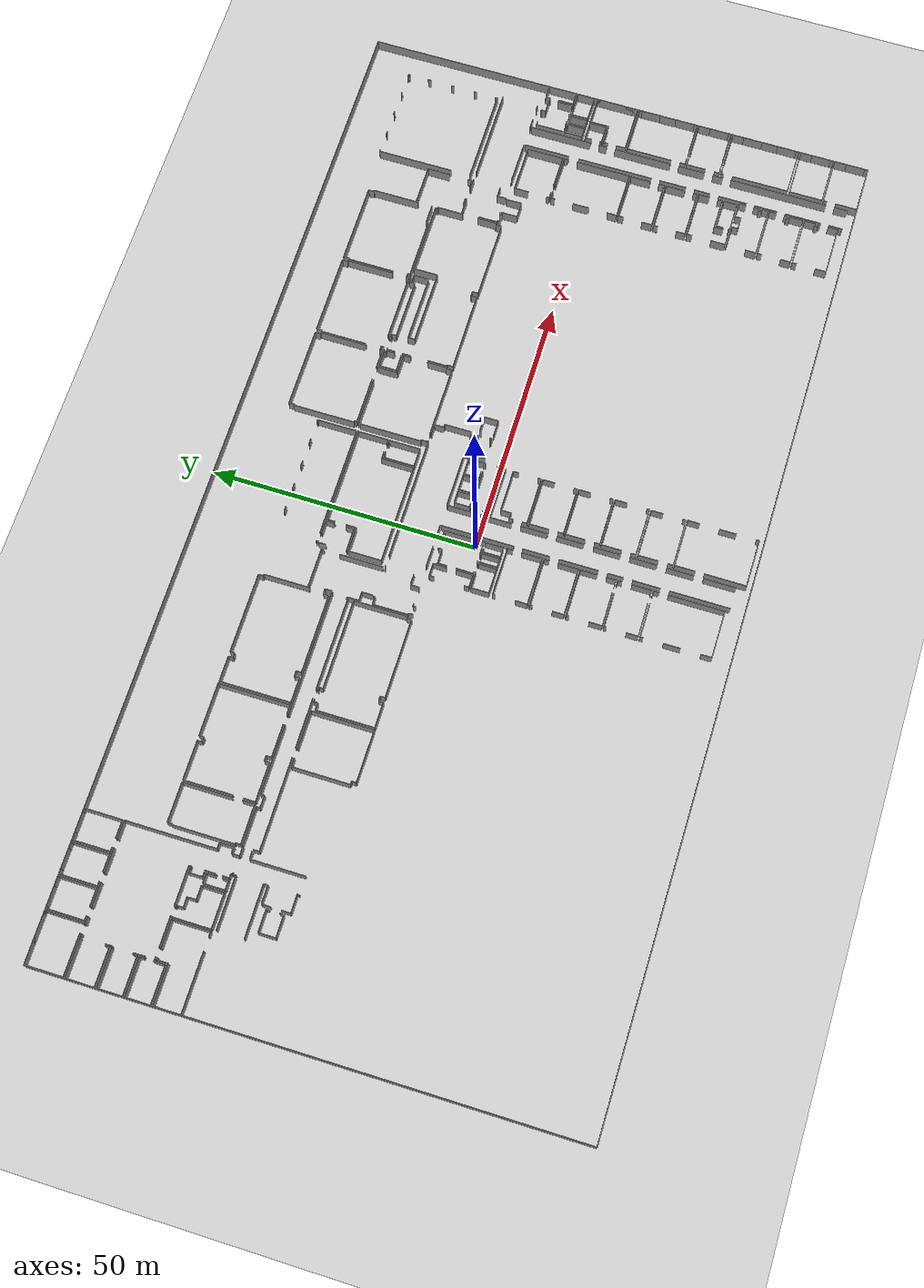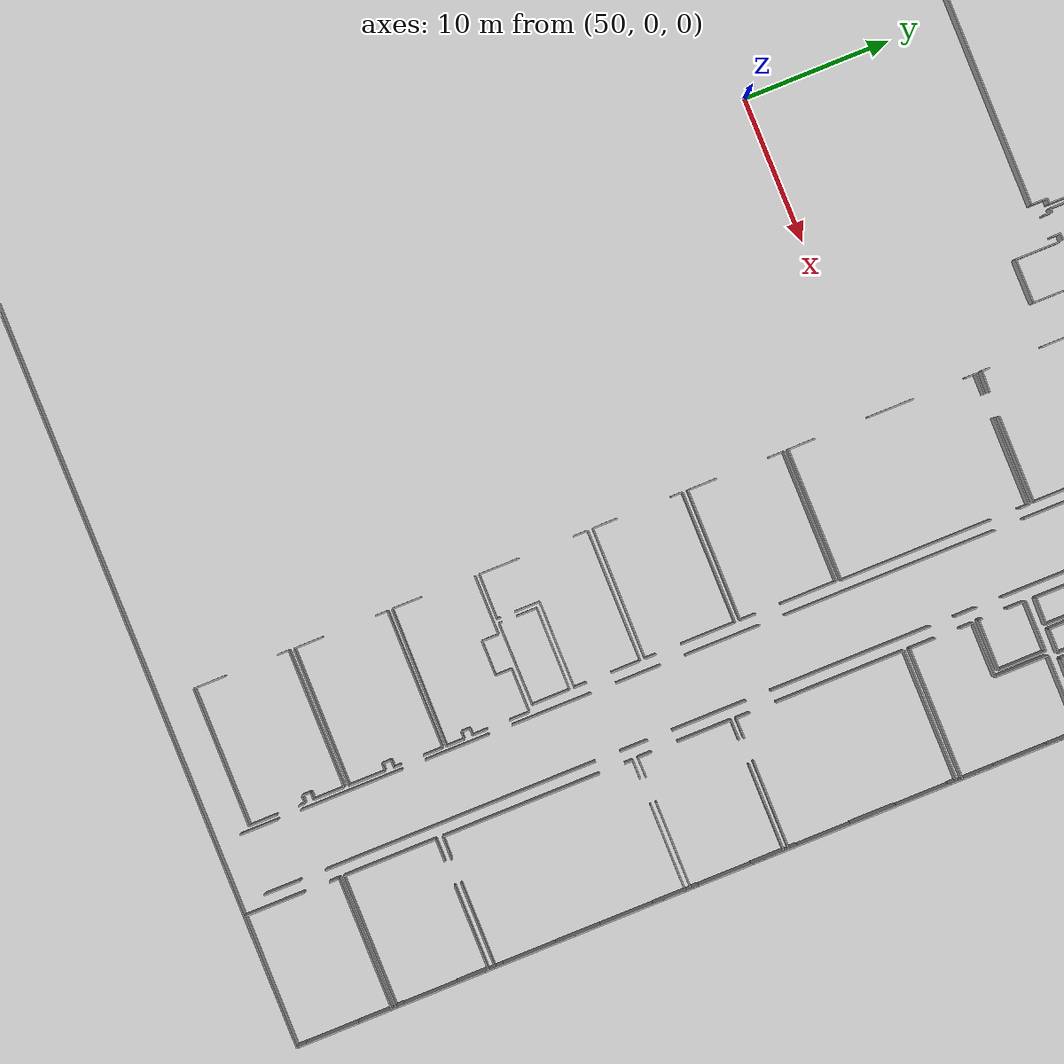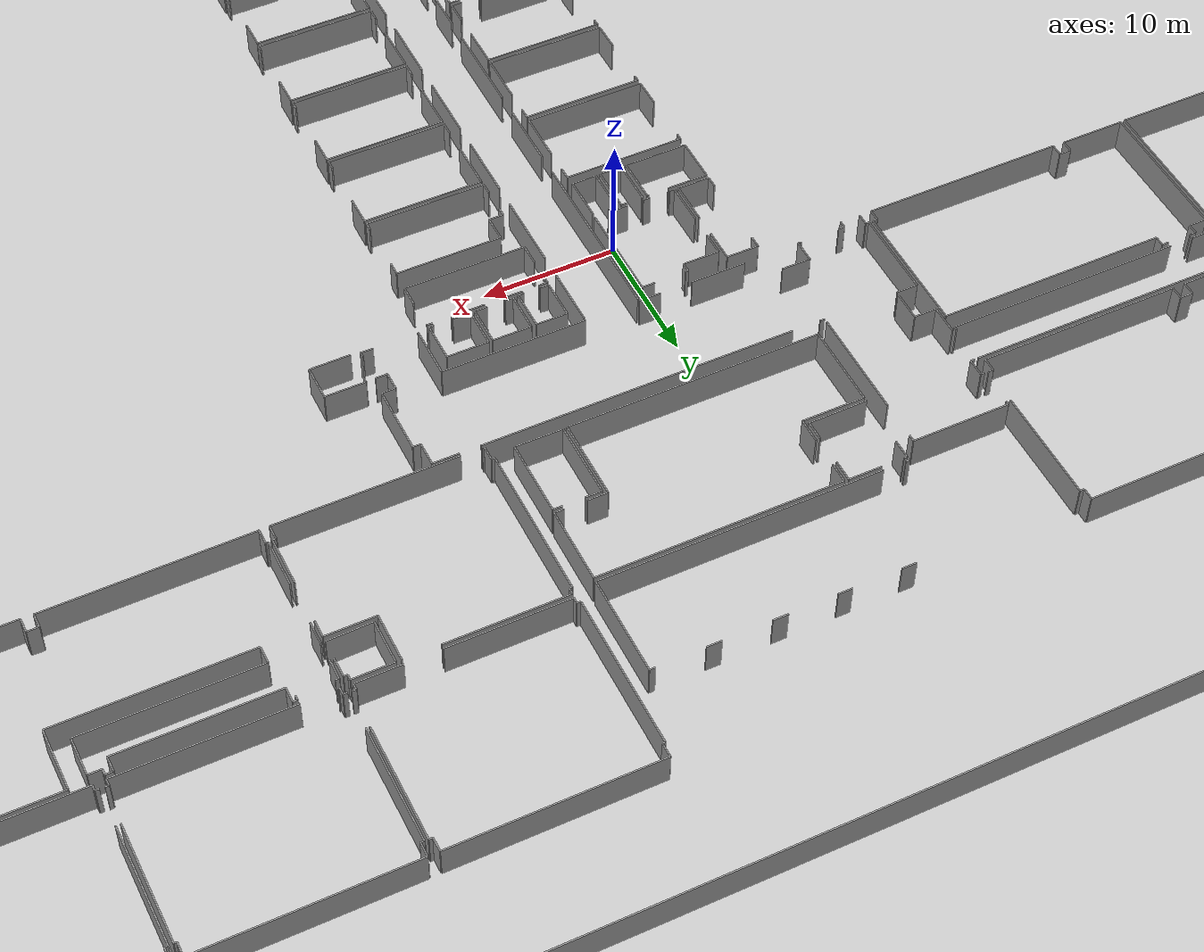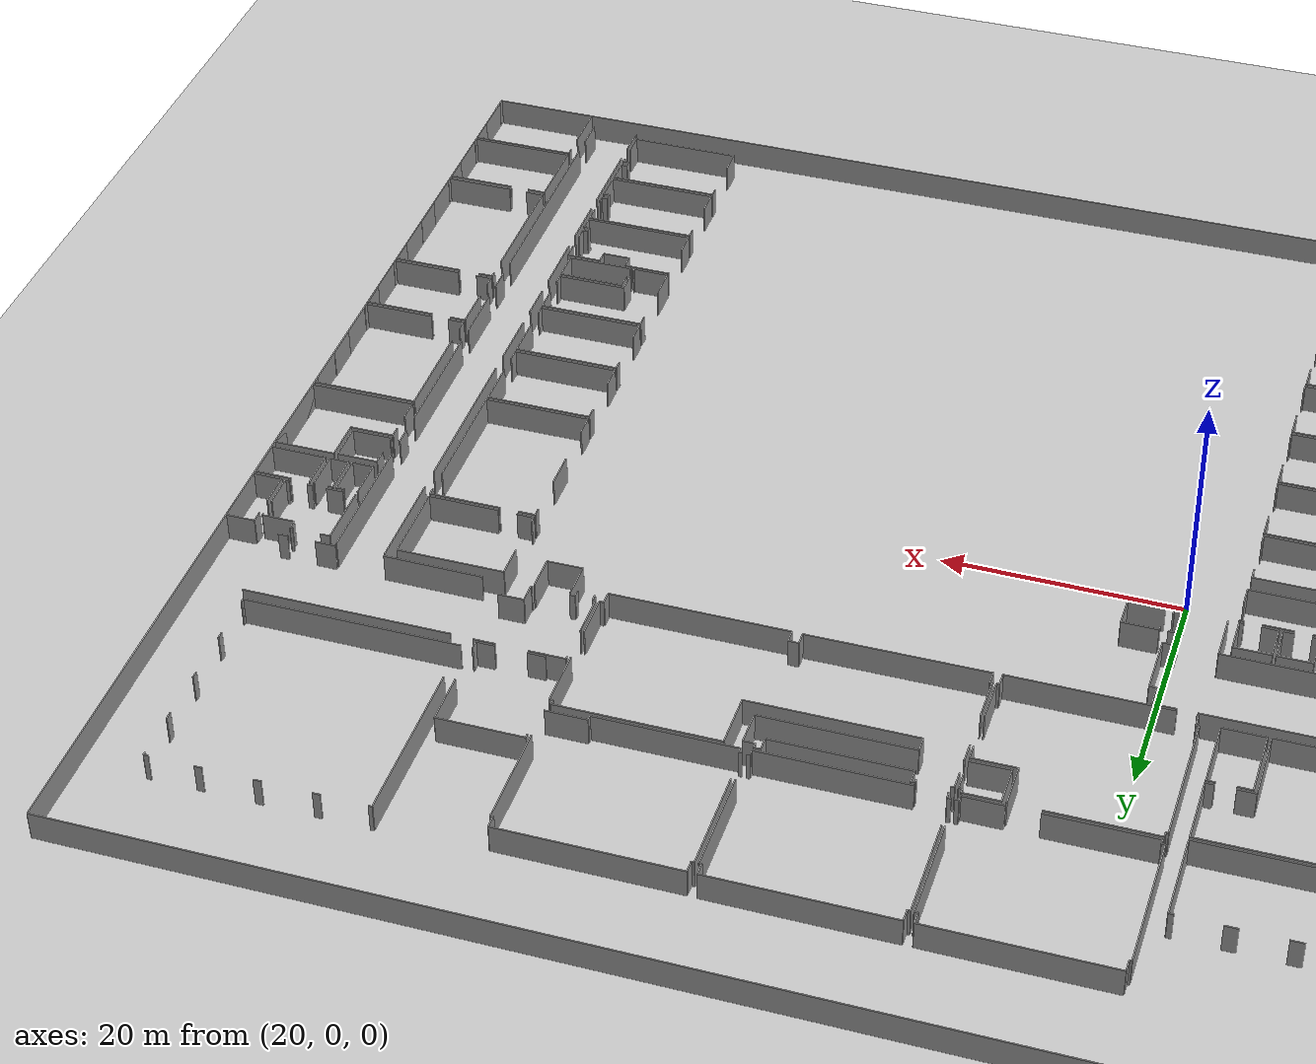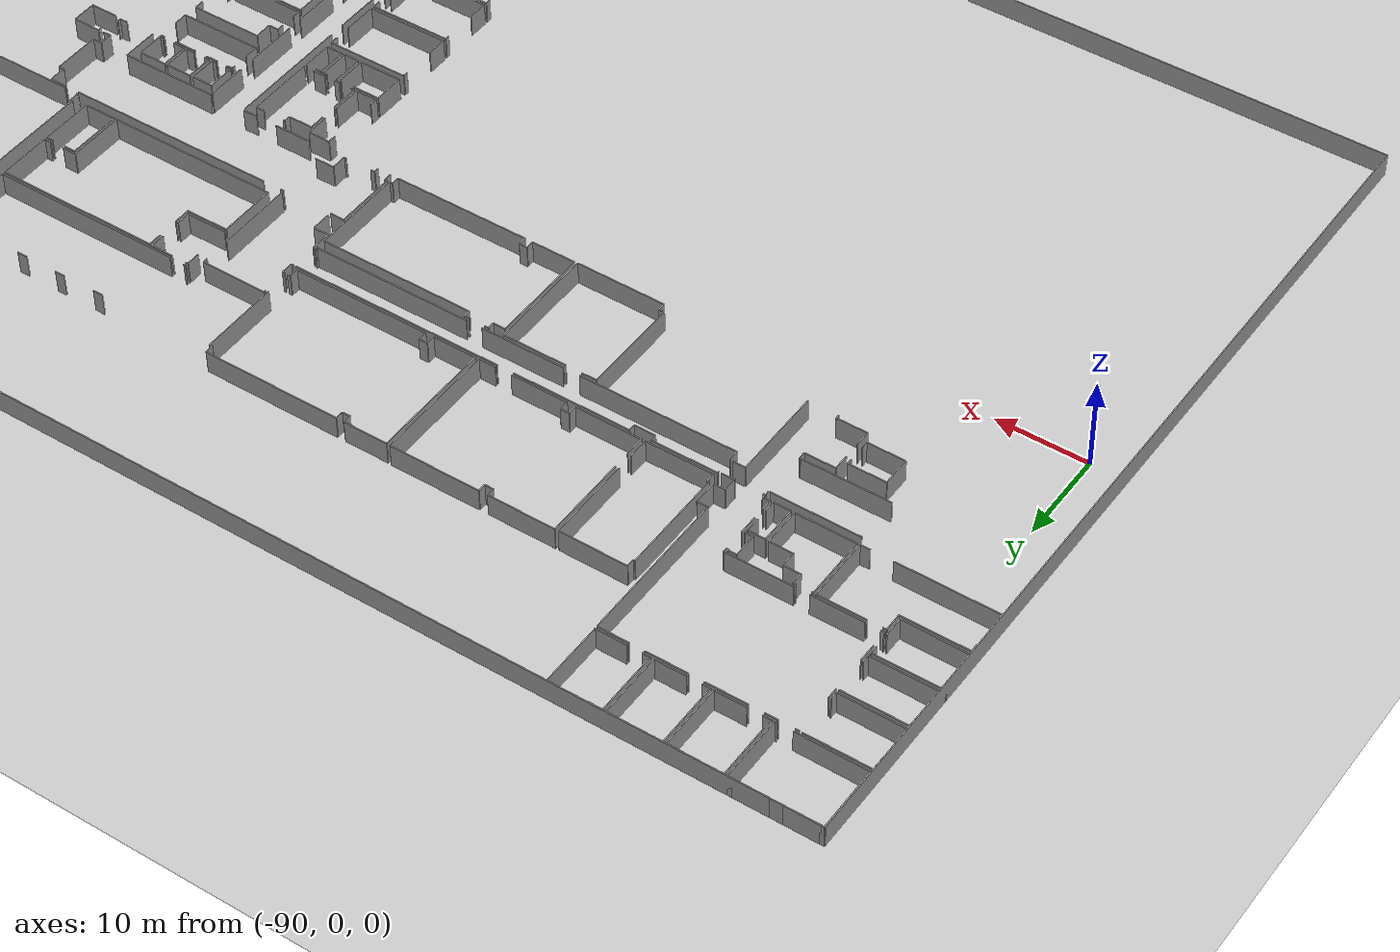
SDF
<sdf version="1.6">
  <world name="default">
    <light name="sun" type="directional">
      <cast_shadows>1</cast_shadows>
      <pose frame="">0 0 10 0 -0 0</pose>
      <diffuse>0.8 0.8 0.8 1</diffuse>
      <specular>0.1 0.1 0.1 1</specular>
      <attenuation>
        <range>1000</range>
        <constant>0.9</constant>
        <linear>0.01</linear>
        <quadratic>0.001</quadratic>
      </attenuation>
      <direction>-0.5 0.5 -1</direction>
    </light>
    <model name="ground_plane">
      <static>1</static>
      <link name="link">
        <collision name="collision">
          <geometry>
            <plane>
              <normal>0 0 1</normal>
              <size>100 100</size>
            </plane>
          </geometry>
          <surface>
            <friction>
              <ode>
                <mu>100</mu>
                <mu2>50</mu2>
              </ode>
              <torsional>
                <ode />
              </torsional>
            </friction>
            <contact>
              <ode />
            </contact>
            <bounce />
          </surface>
          <max_contacts>10</max_contacts>
        </collision>
        <visual name="visual">
          <cast_shadows>0</cast_shadows>
          <geometry>
            <plane>
              <normal>0 0 1</normal>
              <size>100 100</size>
            </plane>
          </geometry>
          <material>
            <script>
              <uri>file://media/materials/scripts/gazebo.material</uri>
              <name>Gazebo/Grey</name>
            </script>
          </material>
        </visual>
        <self_collide>0</self_collide>
        <kinematic>0</kinematic>
        <gravity>1</gravity>
      </link>
    </model>
    <gravity>0 0 -9.8</gravity>
    <magnetic_field>6e-06 2.3e-05 -4.2e-05</magnetic_field>
    <atmosphere type="adiabatic" />
    <physics default="0" name="default_physics" type="ode">
      <max_step_size>0.001</max_step_size>
      <real_time_factor>1</real_time_factor>
      <real_time_update_rate>1000</real_time_update_rate>
    </physics>
    <scene>
      <ambient>0.4 0.4 0.4 1</ambient>
      <background>0.7 0.7 0.7 1</background>
      <shadows>1</shadows>
    </scene>
    <spherical_coordinates>
      <surface_model>EARTH_WGS84</surface_model>
      <latitude_deg>0</latitude_deg>
      <longitude_deg>0</longitude_deg>
      <elevation>0</elevation>
      <heading_deg>0</heading_deg>
    </spherical_coordinates>
  <model name="0510035740_A_40_1_103">
		<static>1</static>
		<link name="Wall_0">
			<collision name="Wall_0_Collision">
				<geometry>
					<box>
						<size>6.98590762866 0.1 2.5</size>
					</box>
				</geometry>
				<pose frame="">3.49295381433 0 1.25 0 0 0</pose>
			</collision>
			<visual name="Wall_0_Visual">
				<pose frame="">3.49295381433 0 1.25 0 0 0</pose>
				<geometry>
					<box>
						<size>6.98590762866 0.1 2.5</size>
					</box>
				</geometry>
				<material>
					<script>
						<uri>file://media/materials/scripts/gazebo.material</uri>
						<name>Gazebo/Grey</name>
					</script>
					<ambient>1 1 1 1</ambient>
				</material>
			</visual>
			<pose frame="">0.0746178689492 -6.98590762866 0 0 0 1.57079632679</pose>
		</link>
		<link name="Wall_1">
			<collision name="Wall_1_Collision">
				<geometry>
					<box>
						<size>0.406591245091 0.1 2.5</size>
					</box>
				</geometry>
				<pose frame="">0.203295622545 0 1.25 0 0 0</pose>
			</collision>
			<visual name="Wall_1_Visual">
				<pose frame="">0.203295622545 0 1.25 0 0 0</pose>
				<geometry>
					<box>
						<size>0.406591245091 0.1 2.5</size>
					</box>
				</geometry>
				<material>
					<script>
						<uri>file://media/materials/scripts/gazebo.material</uri>
						<name>Gazebo/Grey</name>
					</script>
					<ambient>1 1 1 1</ambient>
				</material>
			</visual>
			<pose frame="">0.0746178689492 -0.0 0 0 0 0.0</pose>
		</link>
		<link name="Wall_2">
			<collision name="Wall_2_Collision">
				<geometry>
					<box>
						<size>1.34413685019 0.1 2.5</size>
					</box>
				</geometry>
				<pose frame="">0.672068425093 0 1.25 0 0 0</pose>
			</collision>
			<visual name="Wall_2_Visual">
				<pose frame="">0.672068425093 0 1.25 0 0 0</pose>
				<geometry>
					<box>
						<size>1.34413685019 0.1 2.5</size>
					</box>
				</geometry>
				<material>
					<script>
						<uri>file://media/materials/scripts/gazebo.material</uri>
						<name>Gazebo/Grey</name>
					</script>
					<ambient>1 1 1 1</ambient>
				</material>
			</visual>
			<pose frame="">4.09027746934 -0.0 0 0 0 0.0</pose>
		</link>
		<link name="Wall_3">
			<collision name="Wall_3_Collision">
				<geometry>
					<box>
						<size>0.472833638954 0.1 2.5</size>
					</box>
				</geometry>
				<pose frame="">0.236416819477 0 1.25 0 0 0</pose>
			</collision>
			<visual name="Wall_3_Visual">
				<pose frame="">0.236416819477 0 1.25 0 0 0</pose>
				<geometry>
					<box>
						<size>0.472833638954 0.1 2.5</size>
					</box>
				</geometry>
				<material>
					<script>
						<uri>file://media/materials/scripts/gazebo.material</uri>
						<name>Gazebo/Grey</name>
					</script>
					<ambient>1 1 1 1</ambient>
				</material>
			</visual>
			<pose frame="">9.10160339587 -0.0 0 0 0 0.0</pose>
		</link>
		<link name="Wall_4">
			<collision name="Wall_4_Collision">
				<geometry>
					<box>
						<size>7.03311485187 0.1 2.5</size>
					</box>
				</geometry>
				<pose frame="">3.51655742594 0 1.25 0 0 0</pose>
			</collision>
			<visual name="Wall_4_Visual">
				<pose frame="">3.51655742594 0 1.25 0 0 0</pose>
				<geometry>
					<box>
						<size>7.03311485187 0.1 2.5</size>
					</box>
				</geometry>
				<material>
					<script>
						<uri>file://media/materials/scripts/gazebo.material</uri>
						<name>Gazebo/Grey</name>
					</script>
					<ambient>1 1 1 1</ambient>
				</material>
			</visual>
			<pose frame="">9.57443703483 -0.0 0 0 0 -1.57079632679</pose>
		</link>
		<link name="Wall_5">
			<collision name="Wall_5_Collision">
				<geometry>
					<box>
						<size>0.221315584094 0.1 2.5</size>
					</box>
				</geometry>
				<pose frame="">0.110657792047 0 1.25 0 0 0</pose>
			</collision>
			<visual name="Wall_5_Visual">
				<pose frame="">0.110657792047 0 1.25 0 0 0</pose>
				<geometry>
					<box>
						<size>0.221315584094 0.1 2.5</size>
					</box>
				</geometry>
				<material>
					<script>
						<uri>file://media/materials/scripts/gazebo.material</uri>
						<name>Gazebo/Grey</name>
					</script>
					<ambient>1 1 1 1</ambient>
				</material>
			</visual>
			<pose frame="">9.57443703483 -7.03311485187 0 0 0 3.14159265359</pose>
		</link>
		<link name="Wall_6">
			<collision name="Wall_6_Collision">
				<geometry>
					<box>
						<size>7.67512598577 0.1 2.5</size>
					</box>
				</geometry>
				<pose frame="">3.83756299289 0 1.25 0 0 0</pose>
			</collision>
			<visual name="Wall_6_Visual">
				<pose frame="">3.83756299289 0 1.25 0 0 0</pose>
				<geometry>
					<box>
						<size>7.67512598577 0.1 2.5</size>
					</box>
				</geometry>
				<material>
					<script>
						<uri>file://media/materials/scripts/gazebo.material</uri>
						<name>Gazebo/Grey</name>
					</script>
					<ambient>1 1 1 1</ambient>
				</material>
			</visual>
			<pose frame="">7.74959867515 -7.03311485187 0 0 0 3.1354419375</pose>
		</link>
		<link name="Wall_7">
			<collision name="Wall_7_Collision">
				<geometry>
					<box>
						<size>6.96890287621 0.1 2.5</size>
					</box>
				</geometry>
				<pose frame="">3.48445143811 0 1.25 0 0 0</pose>
			</collision>
			<visual name="Wall_7_Visual">
				<pose frame="">3.48445143811 0 1.25 0 0 0</pose>
				<geometry>
					<box>
						<size>6.96890287621 0.1 2.5</size>
					</box>
				</geometry>
				<material>
					<script>
						<uri>file://media/materials/scripts/gazebo.material</uri>
						<name>Gazebo/Grey</name>
					</script>
					<ambient>1 1 1 1</ambient>
				</material>
			</visual>
			<pose frame="">9.91605489743 -6.98540002411 0 0 0 1.57079632679</pose>
		</link>
		<link name="Wall_8">
			<collision name="Wall_8_Collision">
				<geometry>
					<box>
						<size>0.479940102663 0.1 2.5</size>
					</box>
				</geometry>
				<pose frame="">0.239970051332 0 1.25 0 0 0</pose>
			</collision>
			<visual name="Wall_8_Visual">
				<pose frame="">0.239970051332 0 1.25 0 0 0</pose>
				<geometry>
					<box>
						<size>0.479940102663 0.1 2.5</size>
					</box>
				</geometry>
				<material>
					<script>
						<uri>file://media/materials/scripts/gazebo.material</uri>
						<name>Gazebo/Grey</name>
					</script>
					<ambient>1 1 1 1</ambient>
				</material>
			</visual>
			<pose frame="">9.91605489743 -0.0164971478969 0 0 0 0.0</pose>
		</link>
		<link name="Wall_9">
			<collision name="Wall_9_Collision">
				<geometry>
					<box>
						<size>1.72509406547 0.1 2.5</size>
					</box>
				</geometry>
				<pose frame="">0.862547032734 0 1.25 0 0 0</pose>
			</collision>
			<visual name="Wall_9_Visual">
				<pose frame="">0.862547032734 0 1.25 0 0 0</pose>
				<geometry>
					<box>
						<size>1.72509406547 0.1 2.5</size>
					</box>
				</geometry>
				<material>
					<script>
						<uri>file://media/materials/scripts/gazebo.material</uri>
						<name>Gazebo/Grey</name>
					</script>
					<ambient>1 1 1 1</ambient>
				</material>
			</visual>
			<pose frame="">13.9773989074 -0.0164971478969 0 0 0 0.0</pose>
		</link>
		<link name="Wall_10">
			<collision name="Wall_10_Collision">
				<geometry>
					<box>
						<size>6.99428310375 0.1 2.5</size>
					</box>
				</geometry>
				<pose frame="">3.49714155187 0 1.25 0 0 0</pose>
			</collision>
			<visual name="Wall_10_Visual">
				<pose frame="">3.49714155187 0 1.25 0 0 0</pose>
				<geometry>
					<box>
						<size>6.99428310375 0.1 2.5</size>
					</box>
				</geometry>
				<material>
					<script>
						<uri>file://media/materials/scripts/gazebo.material</uri>
						<name>Gazebo/Grey</name>
					</script>
					<ambient>1 1 1 1</ambient>
				</material>
			</visual>
			<pose frame="">15.7024929728 -0.0164971478969 0 0 0 -1.57079632679</pose>
		</link>
		<link name="Wall_11">
			<collision name="Wall_11_Collision">
				<geometry>
					<box>
						<size>3.33369288656 0.1 2.5</size>
					</box>
				</geometry>
				<pose frame="">1.66684644328 0 1.25 0 0 0</pose>
			</collision>
			<visual name="Wall_11_Visual">
				<pose frame="">1.66684644328 0 1.25 0 0 0</pose>
				<geometry>
					<box>
						<size>3.33369288656 0.1 2.5</size>
					</box>
				</geometry>
				<material>
					<script>
						<uri>file://media/materials/scripts/gazebo.material</uri>
						<name>Gazebo/Grey</name>
					</script>
					<ambient>1 1 1 1</ambient>
				</material>
			</visual>
			<pose frame="">15.7024929728 -7.01078025164 0 0 0 3.14159265359</pose>
		</link>
		<link name="Wall_12">
			<collision name="Wall_12_Collision">
				<geometry>
					<box>
						<size>0.886640876324 0.1 2.5</size>
					</box>
				</geometry>
				<pose frame="">0.443320438162 0 1.25 0 0 0</pose>
			</collision>
			<visual name="Wall_12_Visual">
				<pose frame="">0.443320438162 0 1.25 0 0 0</pose>
				<geometry>
					<box>
						<size>0.886640876324 0.1 2.5</size>
					</box>
				</geometry>
				<material>
					<script>
						<uri>file://media/materials/scripts/gazebo.material</uri>
						<name>Gazebo/Grey</name>
					</script>
					<ambient>1 1 1 1</ambient>
				</material>
			</visual>
			<pose frame="">10.8023324429 -7.01078025164 0 0 0 3.11296359353</pose>
		</link>
		<link name="Wall_13">
			<collision name="Wall_13_Collision">
				<geometry>
					<box>
						<size>6.97474032855 0.1 2.5</size>
					</box>
				</geometry>
				<pose frame="">3.48737016427 0 1.25 0 0 0</pose>
			</collision>
			<visual name="Wall_13_Visual">
				<pose frame="">3.48737016427 0 1.25 0 0 0</pose>
				<geometry>
					<box>
						<size>6.97474032855 0.1 2.5</size>
					</box>
				</geometry>
				<material>
					<script>
						<uri>file://media/materials/scripts/gazebo.material</uri>
						<name>Gazebo/Grey</name>
					</script>
					<ambient>1 1 1 1</ambient>
				</material>
			</visual>
			<pose frame="">16.0415728127 -6.99504451057 0 0 0 1.57079632679</pose>
		</link>
		<link name="Wall_14">
			<collision name="Wall_14_Collision">
				<geometry>
					<box>
						<size>0.975108341846 0.1 2.5</size>
					</box>
				</geometry>
				<pose frame="">0.487554170923 0 1.25 0 0 0</pose>
			</collision>
			<visual name="Wall_14_Visual">
				<pose frame="">0.487554170923 0 1.25 0 0 0</pose>
				<geometry>
					<box>
						<size>0.975108341846 0.1 2.5</size>
					</box>
				</geometry>
				<material>
					<script>
						<uri>file://media/materials/scripts/gazebo.material</uri>
						<name>Gazebo/Grey</name>
					</script>
					<ambient>1 1 1 1</ambient>
				</material>
			</visual>
			<pose frame="">16.0415728127 -0.020304182027 0 0 0 0.0</pose>
		</link>
		<link name="Wall_15">
			<collision name="Wall_15_Collision">
				<geometry>
					<box>
						<size>1.15429274823 0.1 2.5</size>
					</box>
				</geometry>
				<pose frame="">0.577146374117 0 1.25 0 0 0</pose>
			</collision>
			<visual name="Wall_15_Visual">
				<pose frame="">0.577146374117 0 1.25 0 0 0</pose>
				<geometry>
					<box>
						<size>1.15429274823 0.1 2.5</size>
					</box>
				</geometry>
				<material>
					<script>
						<uri>file://media/materials/scripts/gazebo.material</uri>
						<name>Gazebo/Grey</name>
					</script>
					<ambient>1 1 1 1</ambient>
				</material>
			</visual>
			<pose frame="">20.6800631968 -0.020304182027 0 0 0 0.0</pose>
		</link>
		<link name="Wall_16">
			<collision name="Wall_16_Collision">
				<geometry>
					<box>
						<size>6.99428310375 0.1 2.5</size>
					</box>
				</geometry>
				<pose frame="">3.49714155187 0 1.25 0 0 0</pose>
			</collision>
			<visual name="Wall_16_Visual">
				<pose frame="">3.49714155187 0 1.25 0 0 0</pose>
				<geometry>
					<box>
						<size>6.99428310375 0.1 2.5</size>
					</box>
				</geometry>
				<material>
					<script>
						<uri>file://media/materials/scripts/gazebo.material</uri>
						<name>Gazebo/Grey</name>
					</script>
					<ambient>1 1 1 1</ambient>
				</material>
			</visual>
			<pose frame="">21.834355945 -0.020304182027 0 0 0 -1.57079632679</pose>
		</link>
		<link name="Wall_17">
			<collision name="Wall_17_Collision">
				<geometry>
					<box>
						<size>3.32760163195 0.1 2.5</size>
					</box>
				</geometry>
				<pose frame="">1.66380081597 0 1.25 0 0 0</pose>
			</collision>
			<visual name="Wall_17_Visual">
				<pose frame="">1.66380081597 0 1.25 0 0 0</pose>
				<geometry>
					<box>
						<size>3.32760163195 0.1 2.5</size>
					</box>
				</geometry>
				<material>
					<script>
						<uri>file://media/materials/scripts/gazebo.material</uri>
						<name>Gazebo/Grey</name>
					</script>
					<ambient>1 1 1 1</ambient>
				</material>
			</visual>
			<pose frame="">21.834355945 -7.01458728578 0 0 0 3.14159265359</pose>
		</link>
		<link name="Wall_18">
			<collision name="Wall_18_Collision">
				<geometry>
					<box>
						<size>0.85934294708 0.1 2.5</size>
					</box>
				</geometry>
				<pose frame="">0.42967147354 0 1.25 0 0 0</pose>
			</collision>
			<visual name="Wall_18_Visual">
				<pose frame="">0.42967147354 0 1.25 0 0 0</pose>
				<geometry>
					<box>
						<size>0.85934294708 0.1 2.5</size>
					</box>
				</geometry>
				<material>
					<script>
						<uri>file://media/materials/scripts/gazebo.material</uri>
						<name>Gazebo/Grey</name>
					</script>
					<ambient>1 1 1 1</ambient>
				</material>
			</visual>
			<pose frame="">16.9006935147 -7.01458728578 0 0 0 3.11884916082</pose>
		</link>
		<link name="Wall_19">
			<collision name="Wall_19_Collision">
				<geometry>
					<box>
						<size>6.96636485346 0.1 2.5</size>
					</box>
				</geometry>
				<pose frame="">3.48318242673 0 1.25 0 0 0</pose>
			</collision>
			<visual name="Wall_19_Visual">
				<pose frame="">3.48318242673 0 1.25 0 0 0</pose>
				<geometry>
					<box>
						<size>6.96636485346 0.1 2.5</size>
					</box>
				</geometry>
				<material>
					<script>
						<uri>file://media/materials/scripts/gazebo.material</uri>
						<name>Gazebo/Grey</name>
					</script>
					<ambient>1 1 1 1</ambient>
				</material>
			</visual>
			<pose frame="">22.1957703851 -7.00468899704 0 0 0 1.57079632679</pose>
		</link>
		<link name="Wall_20">
			<collision name="Wall_20_Collision">
				<geometry>
					<box>
						<size>1.47433741743 0.1 2.5</size>
					</box>
				</geometry>
				<pose frame="">0.737168708717 0 1.25 0 0 0</pose>
			</collision>
			<visual name="Wall_20_Visual">
				<pose frame="">0.737168708717 0 1.25 0 0 0</pose>
				<geometry>
					<box>
						<size>1.47433741743 0.1 2.5</size>
					</box>
				</geometry>
				<material>
					<script>
						<uri>file://media/materials/scripts/gazebo.material</uri>
						<name>Gazebo/Grey</name>
					</script>
					<ambient>1 1 1 1</ambient>
				</material>
			</visual>
			<pose frame="">22.1957703851 -0.0383241435759 0 0 0 0.0</pose>
		</link>
		<link name="Wall_21">
			<collision name="Wall_21_Collision">
				<geometry>
					<box>
						<size>0.564710062626 0.1 2.5</size>
					</box>
				</geometry>
				<pose frame="">0.282355031313 0 1.25 0 0 0</pose>
			</collision>
			<visual name="Wall_21_Visual">
				<pose frame="">0.282355031313 0 1.25 0 0 0</pose>
				<geometry>
					<box>
						<size>0.564710062626 0.1 2.5</size>
					</box>
				</geometry>
				<material>
					<script>
						<uri>file://media/materials/scripts/gazebo.material</uri>
						<name>Gazebo/Grey</name>
					</script>
					<ambient>1 1 1 1</ambient>
				</material>
			</visual>
			<pose frame="">27.3776514406 -0.0383241435759 0 0 0 0.0</pose>
		</link>
		<link name="Wall_22">
			<collision name="Wall_22_Collision">
				<geometry>
					<box>
						<size>6.98438481501 0.1 2.5</size>
					</box>
				</geometry>
				<pose frame="">3.4921924075 0 1.25 0 0 0</pose>
			</collision>
			<visual name="Wall_22_Visual">
				<pose frame="">3.4921924075 0 1.25 0 0 0</pose>
				<geometry>
					<box>
						<size>6.98438481501 0.1 2.5</size>
					</box>
				</geometry>
				<material>
					<script>
						<uri>file://media/materials/scripts/gazebo.material</uri>
						<name>Gazebo/Grey</name>
					</script>
					<ambient>1 1 1 1</ambient>
				</material>
			</visual>
			<pose frame="">27.9423615033 -0.0383241435759 0 0 0 -1.57079632679</pose>
		</link>
		<link name="Wall_23">
			<collision name="Wall_23_Collision">
				<geometry>
					<box>
						<size>3.30882026357 0.1 2.5</size>
					</box>
				</geometry>
				<pose frame="">1.65441013179 0 1.25 0 0 0</pose>
			</collision>
			<visual name="Wall_23_Visual">
				<pose frame="">1.65441013179 0 1.25 0 0 0</pose>
				<geometry>
					<box>
						<size>3.30882026357 0.1 2.5</size>
					</box>
				</geometry>
				<material>
					<script>
						<uri>file://media/materials/scripts/gazebo.material</uri>
						<name>Gazebo/Grey</name>
					</script>
					<ambient>1 1 1 1</ambient>
				</material>
			</visual>
			<pose frame="">27.9423615033 -7.02270895859 0 0 0 3.14159265359</pose>
		</link>
		<link name="Wall_24">
			<collision name="Wall_24_Collision">
				<geometry>
					<box>
						<size>0.869713296988 0.1 2.5</size>
					</box>
				</geometry>
				<pose frame="">0.434856648494 0 1.25 0 0 0</pose>
			</collision>
			<visual name="Wall_24_Visual">
				<pose frame="">0.434856648494 0 1.25 0 0 0</pose>
				<geometry>
					<box>
						<size>0.869713296988 0.1 2.5</size>
					</box>
				</geometry>
				<material>
					<script>
						<uri>file://media/materials/scripts/gazebo.material</uri>
						<name>Gazebo/Grey</name>
					</script>
					<ambient>1 1 1 1</ambient>
				</material>
			</visual>
			<pose frame="">23.0652969804 -7.02270895859 0 0 0 3.12087174341</pose>
		</link>
		<link name="Wall_25">
			<collision name="Wall_25_Collision">
				<geometry>
					<box>
						<size>1.52662068615 0.1 2.5</size>
					</box>
				</geometry>
				<pose frame="">0.763310343077 0 1.25 0 0 0</pose>
			</collision>
			<visual name="Wall_25_Visual">
				<pose frame="">0.763310343077 0 1.25 0 0 0</pose>
				<geometry>
					<box>
						<size>1.52662068615 0.1 2.5</size>
					</box>
				</geometry>
				<material>
					<script>
						<uri>file://media/materials/scripts/gazebo.material</uri>
						<name>Gazebo/Grey</name>
					</script>
					<ambient>1 1 1 1</ambient>
				</material>
			</visual>
			<pose frame="">0.0164971478969 -8.83612621587 0 0 0 1.57079632679</pose>
		</link>
		<link name="Wall_26">
			<collision name="Wall_26_Collision">
				<geometry>
					<box>
						<size>7.02753120182 0.1 2.5</size>
					</box>
				</geometry>
				<pose frame="">3.51376560091 0 1.25 0 0 0</pose>
			</collision>
			<visual name="Wall_26_Visual">
				<pose frame="">3.51376560091 0 1.25 0 0 0</pose>
				<geometry>
					<box>
						<size>7.02753120182 0.1 2.5</size>
					</box>
				</geometry>
				<material>
					<script>
						<uri>file://media/materials/scripts/gazebo.material</uri>
						<name>Gazebo/Grey</name>
					</script>
					<ambient>1 1 1 1</ambient>
				</material>
			</visual>
			<pose frame="">0.0164971478969 -7.30950552972 0 0 0 0.0</pose>
		</link>
		<link name="Wall_27">
			<collision name="Wall_27_Collision">
				<geometry>
					<box>
						<size>0.858613097466 0.1 2.5</size>
					</box>
				</geometry>
				<pose frame="">0.429306548733 0 1.25 0 0 0</pose>
			</collision>
			<visual name="Wall_27_Visual">
				<pose frame="">0.429306548733 0 1.25 0 0 0</pose>
				<geometry>
					<box>
						<size>0.858613097466 0.1 2.5</size>
					</box>
				</geometry>
				<material>
					<script>
						<uri>file://media/materials/scripts/gazebo.material</uri>
						<name>Gazebo/Grey</name>
					</script>
					<ambient>1 1 1 1</ambient>
				</material>
			</visual>
			<pose frame="">7.04402834971 -11.7193200637 0 0 0 -1.57079632679</pose>
		</link>
		<link name="Wall_28">
			<collision name="Wall_28_Collision">
				<geometry>
					<box>
						<size>7.02760985176 0.1 2.5</size>
					</box>
				</geometry>
				<pose frame="">3.51380492588 0 1.25 0 0 0</pose>
			</collision>
			<visual name="Wall_28_Visual">
				<pose frame="">3.51380492588 0 1.25 0 0 0</pose>
				<geometry>
					<box>
						<size>7.02760985176 0.1 2.5</size>
					</box>
				</geometry>
				<material>
					<script>
						<uri>file://media/materials/scripts/gazebo.material</uri>
						<name>Gazebo/Grey</name>
					</script>
					<ambient>1 1 1 1</ambient>
				</material>
			</visual>
			<pose frame="">7.04402834971 -12.5779331612 0 0 0 3.13686156823</pose>
		</link>
		<link name="Wall_29">
			<collision name="Wall_29_Collision">
				<geometry>
					<box>
						<size>0.901759484274 0.1 2.5</size>
					</box>
				</geometry>
				<pose frame="">0.450879742137 0 1.25 0 0 0</pose>
			</collision>
			<visual name="Wall_29_Visual">
				<pose frame="">0.450879742137 0 1.25 0 0 0</pose>
				<geometry>
					<box>
						<size>0.901759484274 0.1 2.5</size>
					</box>
				</geometry>
				<material>
					<script>
						<uri>file://media/materials/scripts/gazebo.material</uri>
						<name>Gazebo/Grey</name>
					</script>
					<ambient>1 1 1 1</ambient>
				</material>
			</visual>
			<pose frame="">0.0164971478969 -13.840599481 0 0 0 1.57079632679</pose>
		</link>
		<link name="Wall_30">
			<collision name="Wall_30_Collision">
				<geometry>
					<box>
						<size>7.01915572673 0.1 2.5</size>
					</box>
				</geometry>
				<pose frame="">3.50957786337 0 1.25 0 0 0</pose>
			</collision>
			<visual name="Wall_30_Visual">
				<pose frame="">3.50957786337 0 1.25 0 0 0</pose>
				<geometry>
					<box>
						<size>7.01915572673 0.1 2.5</size>
					</box>
				</geometry>
				<material>
					<script>
						<uri>file://media/materials/scripts/gazebo.material</uri>
						<name>Gazebo/Grey</name>
					</script>
					<ambient>1 1 1 1</ambient>
				</material>
			</visual>
			<pose frame="">0.0164971478969 -12.9388399967 0 0 0 0.0</pose>
		</link>
		<link name="Wall_31">
			<collision name="Wall_31_Collision">
				<geometry>
					<box>
						<size>0.823080778919 0.1 2.5</size>
					</box>
				</geometry>
				<pose frame="">0.41154038946 0 1.25 0 0 0</pose>
			</collision>
			<visual name="Wall_31_Visual">
				<pose frame="">0.41154038946 0 1.25 0 0 0</pose>
				<geometry>
					<box>
						<size>0.823080778919 0.1 2.5</size>
					</box>
				</geometry>
				<material>
					<script>
						<uri>file://media/materials/scripts/gazebo.material</uri>
						<name>Gazebo/Grey</name>
					</script>
					<ambient>1 1 1 1</ambient>
				</material>
			</visual>
			<pose frame="">7.03565287463 -16.7047581582 0 0 0 -1.57079632679</pose>
		</link>
		<link name="Wall_32">
			<collision name="Wall_32_Collision">
				<geometry>
					<box>
						<size>7.0191573832 0.1 2.5</size>
					</box>
				</geometry>
				<pose frame="">3.5095786916 0 1.25 0 0 0</pose>
			</collision>
			<visual name="Wall_32_Visual">
				<pose frame="">3.5095786916 0 1.25 0 0 0</pose>
				<geometry>
					<box>
						<size>7.0191573832 0.1 2.5</size>
					</box>
				</geometry>
				<material>
					<script>
						<uri>file://media/materials/scripts/gazebo.material</uri>
						<name>Gazebo/Grey</name>
					</script>
					<ambient>1 1 1 1</ambient>
				</material>
			</visual>
			<pose frame="">7.03565287463 -17.5278389371 0 0 0 3.14090564184</pose>
		</link>
		<link name="Wall_33">
			<collision name="Wall_33_Collision">
				<geometry>
					<box>
						<size>0.887546556855 0.1 2.5</size>
					</box>
				</geometry>
				<pose frame="">0.443773278427 0 1.25 0 0 0</pose>
			</collision>
			<visual name="Wall_33_Visual">
				<pose frame="">0.443773278427 0 1.25 0 0 0</pose>
				<geometry>
					<box>
						<size>0.887546556855 0.1 2.5</size>
					</box>
				</geometry>
				<material>
					<script>
						<uri>file://media/materials/scripts/gazebo.material</uri>
						<name>Gazebo/Grey</name>
					</script>
					<ambient>1 1 1 1</ambient>
				</material>
			</visual>
			<pose frame="">0.0 -18.7839063977 0 0 0 1.57079632679</pose>
		</link>
		<link name="Wall_34">
			<collision name="Wall_34_Collision">
				<geometry>
					<box>
						<size>7.00240477656 0.1 2.5</size>
					</box>
				</geometry>
				<pose frame="">3.50120238828 0 1.25 0 0 0</pose>
			</collision>
			<visual name="Wall_34_Visual">
				<pose frame="">3.50120238828 0 1.25 0 0 0</pose>
				<geometry>
					<box>
						<size>7.00240477656 0.1 2.5</size>
					</box>
				</geometry>
				<material>
					<script>
						<uri>file://media/materials/scripts/gazebo.material</uri>
						<name>Gazebo/Grey</name>
					</script>
					<ambient>1 1 1 1</ambient>
				</material>
			</visual>
			<pose frame="">0.0 -17.8963598409 0 0 0 0.0</pose>
		</link>
		<link name="Wall_35">
			<collision name="Wall_35_Collision">
				<geometry>
					<box>
						<size>0.837801310889 0.1 2.5</size>
					</box>
				</geometry>
				<pose frame="">0.418900655444 0 1.25 0 0 0</pose>
			</collision>
			<visual name="Wall_35_Visual">
				<pose frame="">0.418900655444 0 1.25 0 0 0</pose>
				<geometry>
					<box>
						<size>0.837801310889 0.1 2.5</size>
					</box>
				</geometry>
				<material>
					<script>
						<uri>file://media/materials/scripts/gazebo.material</uri>
						<name>Gazebo/Grey</name>
					</script>
					<ambient>1 1 1 1</ambient>
				</material>
			</visual>
			<pose frame="">7.00240477656 -17.8963598409 0 0 0 -1.57079632679</pose>
		</link>
		<link name="Wall_36">
			<collision name="Wall_36_Collision">
				<geometry>
					<box>
						<size>2.16138017677 0.1 2.5</size>
					</box>
				</geometry>
				<pose frame="">1.08069008839 0 1.25 0 0 0</pose>
			</collision>
			<visual name="Wall_36_Visual">
				<pose frame="">1.08069008839 0 1.25 0 0 0</pose>
				<geometry>
					<box>
						<size>2.16138017677 0.1 2.5</size>
					</box>
				</geometry>
				<material>
					<script>
						<uri>file://media/materials/scripts/gazebo.material</uri>
						<name>Gazebo/Grey</name>
					</script>
					<ambient>1 1 1 1</ambient>
				</material>
			</visual>
			<pose frame="">7.00240477656 -20.3478360183 0 0 0 -1.57079632679</pose>
		</link>
		<link name="Wall_37">
			<collision name="Wall_37_Collision">
				<geometry>
					<box>
						<size>7.00252698051 0.1 2.5</size>
					</box>
				</geometry>
				<pose frame="">3.50126349025 0 1.25 0 0 0</pose>
			</collision>
			<visual name="Wall_37_Visual">
				<pose frame="">3.50126349025 0 1.25 0 0 0</pose>
				<geometry>
					<box>
						<size>7.00252698051 0.1 2.5</size>
					</box>
				</geometry>
				<material>
					<script>
						<uri>file://media/materials/scripts/gazebo.material</uri>
						<name>Gazebo/Grey</name>
					</script>
					<ambient>1 1 1 1</ambient>
				</material>
			</visual>
			<pose frame="">7.00240477656 -22.5092161951 0 0 0 3.13568478467</pose>
		</link>
		<link name="Wall_38">
			<collision name="Wall_38_Collision">
				<geometry>
					<box>
						<size>0.438824134058 0.1 2.5</size>
					</box>
				</geometry>
				<pose frame="">0.219412067029 0 1.25 0 0 0</pose>
			</collision>
			<visual name="Wall_38_Visual">
				<pose frame="">0.219412067029 0 1.25 0 0 0</pose>
				<geometry>
					<box>
						<size>0.438824134058 0.1 2.5</size>
					</box>
				</geometry>
				<material>
					<script>
						<uri>file://media/materials/scripts/gazebo.material</uri>
						<name>Gazebo/Grey</name>
					</script>
					<ambient>1 1 1 1</ambient>
				</material>
			</visual>
			<pose frame="">0.0786787053546 -27.8238358407 0 0 0 1.57079632679</pose>
		</link>
		<link name="Wall_39">
			<collision name="Wall_39_Collision">
				<geometry>
					<box>
						<size>0.868257583929 0.1 2.5</size>
					</box>
				</geometry>
				<pose frame="">0.434128791965 0 1.25 0 0 0</pose>
			</collision>
			<visual name="Wall_39_Visual">
				<pose frame="">0.434128791965 0 1.25 0 0 0</pose>
				<geometry>
					<box>
						<size>0.868257583929 0.1 2.5</size>
					</box>
				</geometry>
				<material>
					<script>
						<uri>file://media/materials/scripts/gazebo.material</uri>
						<name>Gazebo/Grey</name>
					</script>
					<ambient>1 1 1 1</ambient>
				</material>
			</visual>
			<pose frame="">0.0786787053546 -23.7114775734 0 0 0 1.57079632679</pose>
		</link>
		<link name="Wall_40">
			<collision name="Wall_40_Collision">
				<geometry>
					<box>
						<size>7.26153689968 0.1 2.5</size>
					</box>
				</geometry>
				<pose frame="">3.63076844984 0 1.25 0 0 0</pose>
			</collision>
			<visual name="Wall_40_Visual">
				<pose frame="">3.63076844984 0 1.25 0 0 0</pose>
				<geometry>
					<box>
						<size>7.26153689968 0.1 2.5</size>
					</box>
				</geometry>
				<material>
					<script>
						<uri>file://media/materials/scripts/gazebo.material</uri>
						<name>Gazebo/Grey</name>
					</script>
					<ambient>1 1 1 1</ambient>
				</material>
			</visual>
			<pose frame="">0.0786787053546 -22.8432199895 0 0 0 0.0</pose>
		</link>
		<link name="Wall_41">
			<collision name="Wall_41_Collision">
				<geometry>
					<box>
						<size>1.97559691123 0.1 2.5</size>
					</box>
				</geometry>
				<pose frame="">0.987798455613 0 1.25 0 0 0</pose>
			</collision>
			<visual name="Wall_41_Visual">
				<pose frame="">0.987798455613 0 1.25 0 0 0</pose>
				<geometry>
					<box>
						<size>1.97559691123 0.1 2.5</size>
					</box>
				</geometry>
				<material>
					<script>
						<uri>file://media/materials/scripts/gazebo.material</uri>
						<name>Gazebo/Grey</name>
					</script>
					<ambient>1 1 1 1</ambient>
				</material>
			</visual>
			<pose frame="">7.34021560503 -22.8432199895 0 0 0 1.57079632679</pose>
		</link>
		<link name="Wall_42">
			<collision name="Wall_42_Collision">
				<geometry>
					<box>
						<size>0.396692956352 0.1 2.5</size>
					</box>
				</geometry>
				<pose frame="">0.198346478176 0 1.25 0 0 0</pose>
			</collision>
			<visual name="Wall_42_Visual">
				<pose frame="">0.198346478176 0 1.25 0 0 0</pose>
				<geometry>
					<box>
						<size>0.396692956352 0.1 2.5</size>
					</box>
				</geometry>
				<material>
					<script>
						<uri>file://media/materials/scripts/gazebo.material</uri>
						<name>Gazebo/Grey</name>
					</script>
					<ambient>1 1 1 1</ambient>
				</material>
			</visual>
			<pose frame="">7.34021560503 -20.8676230782 0 0 0 0.0</pose>
		</link>
		<link name="Wall_43">
			<collision name="Wall_43_Collision">
				<geometry>
					<box>
						<size>5.19863200574 0.1 2.5</size>
					</box>
				</geometry>
				<pose frame="">2.59931600287 0 1.25 0 0 0</pose>
			</collision>
			<visual name="Wall_43_Visual">
				<pose frame="">2.59931600287 0 1.25 0 0 0</pose>
				<geometry>
					<box>
						<size>5.19863200574 0.1 2.5</size>
					</box>
				</geometry>
				<material>
					<script>
						<uri>file://media/materials/scripts/gazebo.material</uri>
						<name>Gazebo/Grey</name>
					</script>
					<ambient>1 1 1 1</ambient>
				</material>
			</visual>
			<pose frame="">9.30007677519 -20.8676230782 0 0 0 0.0</pose>
		</link>
		<link name="Wall_44">
			<collision name="Wall_44_Collision">
				<geometry>
					<box>
						<size>6.974232724 0.1 2.5</size>
					</box>
				</geometry>
				<pose frame="">3.487116362 0 1.25 0 0 0</pose>
			</collision>
			<visual name="Wall_44_Visual">
				<pose frame="">3.487116362 0 1.25 0 0 0</pose>
				<geometry>
					<box>
						<size>6.974232724 0.1 2.5</size>
					</box>
				</geometry>
				<material>
					<script>
						<uri>file://media/materials/scripts/gazebo.material</uri>
						<name>Gazebo/Grey</name>
					</script>
					<ambient>1 1 1 1</ambient>
				</material>
			</visual>
			<pose frame="">14.4987087809 -20.8676230782 0 0 0 -1.57079632679</pose>
		</link>
		<link name="Wall_45">
			<collision name="Wall_45_Collision">
				<geometry>
					<box>
						<size>1.05429465175 0.1 2.5</size>
					</box>
				</geometry>
				<pose frame="">0.527147325876 0 1.25 0 0 0</pose>
			</collision>
			<visual name="Wall_45_Visual">
				<pose frame="">0.527147325876 0 1.25 0 0 0</pose>
				<geometry>
					<box>
						<size>1.05429465175 0.1 2.5</size>
					</box>
				</geometry>
				<material>
					<script>
						<uri>file://media/materials/scripts/gazebo.material</uri>
						<name>Gazebo/Grey</name>
					</script>
					<ambient>1 1 1 1</ambient>
				</material>
			</visual>
			<pose frame="">14.4987087809 -27.8418558022 0 0 0 3.14159265359</pose>
		</link>
		<link name="Wall_46">
			<collision name="Wall_46_Collision">
				<geometry>
					<box>
						<size>10.9736637742 0.1 2.5</size>
					</box>
				</geometry>
				<pose frame="">5.48683188708 0 1.25 0 0 0</pose>
			</collision>
			<visual name="Wall_46_Visual">
				<pose frame="">5.48683188708 0 1.25 0 0 0</pose>
				<geometry>
					<box>
						<size>10.9736637742 0.1 2.5</size>
					</box>
				</geometry>
				<material>
					<script>
						<uri>file://media/materials/scripts/gazebo.material</uri>
						<name>Gazebo/Grey</name>
					</script>
					<ambient>1 1 1 1</ambient>
				</material>
			</visual>
			<pose frame="">11.0523276841 -27.8418558022 0 0 0 3.13995054299</pose>
		</link>
		<link name="Wall_47">
			<collision name="Wall_47_Collision">
				<geometry>
					<box>
						<size>6.98971466279 0.1 2.5</size>
					</box>
				</geometry>
				<pose frame="">3.4948573314 0 1.25 0 0 0</pose>
			</collision>
			<visual name="Wall_47_Visual">
				<pose frame="">3.4948573314 0 1.25 0 0 0</pose>
				<geometry>
					<box>
						<size>6.98971466279 0.1 2.5</size>
					</box>
				</geometry>
				<material>
					<script>
						<uri>file://media/materials/scripts/gazebo.material</uri>
						<name>Gazebo/Grey</name>
					</script>
					<ambient>1 1 1 1</ambient>
				</material>
			</visual>
			<pose frame="">14.7987030704 -27.8314499089 0 0 0 1.57079632679</pose>
		</link>
		<link name="Wall_48">
			<collision name="Wall_48_Collision">
				<geometry>
					<box>
						<size>0.160403038013 0.1 2.5</size>
					</box>
				</geometry>
				<pose frame="">0.0802015190066 0 1.25 0 0 0</pose>
			</collision>
			<visual name="Wall_48_Visual">
				<pose frame="">0.0802015190066 0 1.25 0 0 0</pose>
				<geometry>
					<box>
						<size>0.160403038013 0.1 2.5</size>
					</box>
				</geometry>
				<material>
					<script>
						<uri>file://media/materials/scripts/gazebo.material</uri>
						<name>Gazebo/Grey</name>
					</script>
					<ambient>1 1 1 1</ambient>
				</material>
			</visual>
			<pose frame="">14.7987030704 -20.8417352462 0 0 0 0.0</pose>
		</link>
		<link name="Wall_49">
			<collision name="Wall_49_Collision">
				<geometry>
					<box>
						<size>0.307354555434 0.1 2.5</size>
					</box>
				</geometry>
				<pose frame="">0.153677277717 0 1.25 0 0 0</pose>
			</collision>
			<visual name="Wall_49_Visual">
				<pose frame="">0.153677277717 0 1.25 0 0 0</pose>
				<geometry>
					<box>
						<size>0.307354555434 0.1 2.5</size>
					</box>
				</geometry>
				<material>
					<script>
						<uri>file://media/materials/scripts/gazebo.material</uri>
						<name>Gazebo/Grey</name>
					</script>
					<ambient>1 1 1 1</ambient>
				</material>
			</visual>
			<pose frame="">16.5557762225 -20.8417352462 0 0 0 0.0</pose>
		</link>
		<link name="Wall_50">
			<collision name="Wall_50_Collision">
				<geometry>
					<box>
						<size>1.23576327862 0.1 2.5</size>
					</box>
				</geometry>
				<pose frame="">0.617881639309 0 1.25 0 0 0</pose>
			</collision>
			<visual name="Wall_50_Visual">
				<pose frame="">0.617881639309 0 1.25 0 0 0</pose>
				<geometry>
					<box>
						<size>1.23576327862 0.1 2.5</size>
					</box>
				</geometry>
				<material>
					<script>
						<uri>file://media/materials/scripts/gazebo.material</uri>
						<name>Gazebo/Grey</name>
					</script>
					<ambient>1 1 1 1</ambient>
				</material>
			</visual>
			<pose frame="">16.863130778 -20.8417352462 0 0 0 -1.57079632679</pose>
		</link>
		<link name="Wall_51">
			<collision name="Wall_51_Collision">
				<geometry>
					<box>
						<size>1.86950756014 0.1 2.5</size>
					</box>
				</geometry>
				<pose frame="">0.934753780068 0 1.25 0 0 0</pose>
			</collision>
			<visual name="Wall_51_Visual">
				<pose frame="">0.934753780068 0 1.25 0 0 0</pose>
				<geometry>
					<box>
						<size>1.86950756014 0.1 2.5</size>
					</box>
				</geometry>
				<material>
					<script>
						<uri>file://media/materials/scripts/gazebo.material</uri>
						<name>Gazebo/Grey</name>
					</script>
					<ambient>1 1 1 1</ambient>
				</material>
			</visual>
			<pose frame="">16.863130778 -22.0774985248 0 0 0 0.0</pose>
		</link>
		<link name="Wall_52">
			<collision name="Wall_52_Collision">
				<geometry>
					<box>
						<size>1.65631364885 0.1 2.5</size>
					</box>
				</geometry>
				<pose frame="">0.828156824426 0 1.25 0 0 0</pose>
			</collision>
			<visual name="Wall_52_Visual">
				<pose frame="">0.828156824426 0 1.25 0 0 0</pose>
				<geometry>
					<box>
						<size>1.65631364885 0.1 2.5</size>
					</box>
				</geometry>
				<material>
					<script>
						<uri>file://media/materials/scripts/gazebo.material</uri>
						<name>Gazebo/Grey</name>
					</script>
					<ambient>1 1 1 1</ambient>
				</material>
			</visual>
			<pose frame="">18.7326383381 -22.0774985248 0 0 0 -1.57079632679</pose>
		</link>
		<link name="Wall_53">
			<collision name="Wall_53_Collision">
				<geometry>
					<box>
						<size>2.57228606054 0.1 2.5</size>
					</box>
				</geometry>
				<pose frame="">1.28614303027 0 1.25 0 0 0</pose>
			</collision>
			<visual name="Wall_53_Visual">
				<pose frame="">1.28614303027 0 1.25 0 0 0</pose>
				<geometry>
					<box>
						<size>2.57228606054 0.1 2.5</size>
					</box>
				</geometry>
				<material>
					<script>
						<uri>file://media/materials/scripts/gazebo.material</uri>
						<name>Gazebo/Grey</name>
					</script>
					<ambient>1 1 1 1</ambient>
				</material>
			</visual>
			<pose frame="">18.7326383381 -23.7338121736 0 0 0 0.0</pose>
		</link>
		<link name="Wall_54">
			<collision name="Wall_54_Collision">
				<geometry>
					<box>
						<size>4.10804362861 0.1 2.5</size>
					</box>
				</geometry>
				<pose frame="">2.05402181431 0 1.25 0 0 0</pose>
			</collision>
			<visual name="Wall_54_Visual">
				<pose frame="">2.05402181431 0 1.25 0 0 0</pose>
				<geometry>
					<box>
						<size>4.10804362861 0.1 2.5</size>
					</box>
				</geometry>
				<material>
					<script>
						<uri>file://media/materials/scripts/gazebo.material</uri>
						<name>Gazebo/Grey</name>
					</script>
					<ambient>1 1 1 1</ambient>
				</material>
			</visual>
			<pose frame="">21.3049243986 -23.7338121736 0 0 0 -1.57079632679</pose>
		</link>
		<link name="Wall_55">
			<collision name="Wall_55_Collision">
				<geometry>
					<box>
						<size>6.50622964974 0.1 2.5</size>
					</box>
				</geometry>
				<pose frame="">3.25311482487 0 1.25 0 0 0</pose>
			</collision>
			<visual name="Wall_55_Visual">
				<pose frame="">3.25311482487 0 1.25 0 0 0</pose>
				<geometry>
					<box>
						<size>6.50622964974 0.1 2.5</size>
					</box>
				</geometry>
				<material>
					<script>
						<uri>file://media/materials/scripts/gazebo.material</uri>
						<name>Gazebo/Grey</name>
					</script>
					<ambient>1 1 1 1</ambient>
				</material>
			</visual>
			<pose frame="">21.3049243986 -27.8418558022 0 0 0 3.1399932791</pose>
		</link>
		<link name="Wall_56">
			<collision name="Wall_56_Collision">
				<geometry>
					<box>
						<size>4.02403507547 0.1 2.5</size>
					</box>
				</geometry>
				<pose frame="">2.01201753774 0 1.25 0 0 0</pose>
			</collision>
			<visual name="Wall_56_Visual">
				<pose frame="">2.01201753774 0 1.25 0 0 0</pose>
				<geometry>
					<box>
						<size>4.02403507547 0.1 2.5</size>
					</box>
				</geometry>
				<material>
					<script>
						<uri>file://media/materials/scripts/gazebo.material</uri>
						<name>Gazebo/Grey</name>
					</script>
					<ambient>1 1 1 1</ambient>
				</material>
			</visual>
			<pose frame="">21.6879120321 -27.8276428748 0 0 0 1.57079632679</pose>
		</link>
		<link name="Wall_57">
			<collision name="Wall_57_Collision">
				<geometry>
					<box>
						<size>1.8585940623 0.1 2.5</size>
					</box>
				</geometry>
				<pose frame="">0.929297031148 0 1.25 0 0 0</pose>
			</collision>
			<visual name="Wall_57_Visual">
				<pose frame="">0.929297031148 0 1.25 0 0 0</pose>
				<geometry>
					<box>
						<size>1.8585940623 0.1 2.5</size>
					</box>
				</geometry>
				<material>
					<script>
						<uri>file://media/materials/scripts/gazebo.material</uri>
						<name>Gazebo/Grey</name>
					</script>
					<ambient>1 1 1 1</ambient>
				</material>
			</visual>
			<pose frame="">21.6879120321 -23.8036077993 0 0 0 0.0</pose>
		</link>
		<link name="Wall_58">
			<collision name="Wall_58_Collision">
				<geometry>
					<box>
						<size>1.59311688229 0.1 2.5</size>
					</box>
				</geometry>
				<pose frame="">0.796558441146 0 1.25 0 0 0</pose>
			</collision>
			<visual name="Wall_58_Visual">
				<pose frame="">0.796558441146 0 1.25 0 0 0</pose>
				<geometry>
					<box>
						<size>1.59311688229 0.1 2.5</size>
					</box>
				</geometry>
				<material>
					<script>
						<uri>file://media/materials/scripts/gazebo.material</uri>
						<name>Gazebo/Grey</name>
					</script>
					<ambient>1 1 1 1</ambient>
				</material>
			</visual>
			<pose frame="">23.5465060944 -23.8036077993 0 0 0 -1.57079632679</pose>
		</link>
		<link name="Wall_59">
			<collision name="Wall_59_Collision">
				<geometry>
					<box>
						<size>1.1824648008 0.1 2.5</size>
					</box>
				</geometry>
				<pose frame="">0.591232400398 0 1.25 0 0 0</pose>
			</collision>
			<visual name="Wall_59_Visual">
				<pose frame="">0.591232400398 0 1.25 0 0 0</pose>
				<geometry>
					<box>
						<size>1.1824648008 0.1 2.5</size>
					</box>
				</geometry>
				<material>
					<script>
						<uri>file://media/materials/scripts/gazebo.material</uri>
						<name>Gazebo/Grey</name>
					</script>
					<ambient>1 1 1 1</ambient>
				</material>
			</visual>
			<pose frame="">23.5465060944 -26.6604062105 0 0 0 -1.57079632679</pose>
		</link>
		<link name="Wall_60">
			<collision name="Wall_60_Collision">
				<geometry>
					<box>
						<size>1.85865644608 0.1 2.5</size>
					</box>
				</geometry>
				<pose frame="">0.929328223038 0 1.25 0 0 0</pose>
			</collision>
			<visual name="Wall_60_Visual">
				<pose frame="">0.929328223038 0 1.25 0 0 0</pose>
				<geometry>
					<box>
						<size>1.85865644608 0.1 2.5</size>
					</box>
				</geometry>
				<material>
					<script>
						<uri>file://media/materials/scripts/gazebo.material</uri>
						<name>Gazebo/Grey</name>
					</script>
					<ambient>1 1 1 1</ambient>
				</material>
			</visual>
			<pose frame="">23.5465060944 -27.8428710113 0 0 0 3.13339947355</pose>
		</link>
		<link name="Wall_61">
			<collision name="Wall_61_Collision">
				<geometry>
					<box>
						<size>2.56822522414 0.1 2.5</size>
					</box>
				</geometry>
				<pose frame="">1.28411261207 0 1.25 0 0 0</pose>
			</collision>
			<visual name="Wall_61_Visual">
				<pose frame="">1.28411261207 0 1.25 0 0 0</pose>
				<geometry>
					<box>
						<size>2.56822522414 0.1 2.5</size>
					</box>
				</geometry>
				<material>
					<script>
						<uri>file://media/materials/scripts/gazebo.material</uri>
						<name>Gazebo/Grey</name>
					</script>
					<ambient>1 1 1 1</ambient>
				</material>
			</visual>
			<pose frame="">22.7216486996 -23.414275109 0 0 0 1.57079632679</pose>
		</link>
		<link name="Wall_62">
			<collision name="Wall_62_Collision">
				<geometry>
					<box>
						<size>0.902013286549 0.1 2.5</size>
					</box>
				</geometry>
				<pose frame="">0.451006643275 0 1.25 0 0 0</pose>
			</collision>
			<visual name="Wall_62_Visual">
				<pose frame="">0.451006643275 0 1.25 0 0 0</pose>
				<geometry>
					<box>
						<size>0.902013286549 0.1 2.5</size>
					</box>
				</geometry>
				<material>
					<script>
						<uri>file://media/materials/scripts/gazebo.material</uri>
						<name>Gazebo/Grey</name>
					</script>
					<ambient>1 1 1 1</ambient>
				</material>
			</visual>
			<pose frame="">22.7216486996 -20.8460498848 0 0 0 0.0</pose>
		</link>
		<link name="Wall_63">
			<collision name="Wall_63_Collision">
				<geometry>
					<box>
						<size>0.137053228682 0.1 2.5</size>
					</box>
				</geometry>
				<pose frame="">0.0685266143411 0 1.25 0 0 0</pose>
			</collision>
			<visual name="Wall_63_Visual">
				<pose frame="">0.0685266143411 0 1.25 0 0 0</pose>
				<geometry>
					<box>
						<size>0.137053228682 0.1 2.5</size>
					</box>
				</geometry>
				<material>
					<script>
						<uri>file://media/materials/scripts/gazebo.material</uri>
						<name>Gazebo/Grey</name>
					</script>
					<ambient>1 1 1 1</ambient>
				</material>
			</visual>
			<pose frame="">23.6236619861 -20.8460498848 0 0 0 -1.57079632679</pose>
		</link>
		<link name="Wall_64">
			<collision name="Wall_64_Collision">
				<geometry>
					<box>
						<size>0.109642582946 0.1 2.5</size>
					</box>
				</geometry>
				<pose frame="">0.0548212914729 0 1.25 0 0 0</pose>
			</collision>
			<visual name="Wall_64_Visual">
				<pose frame="">0.0548212914729 0 1.25 0 0 0</pose>
				<geometry>
					<box>
						<size>0.109642582946 0.1 2.5</size>
					</box>
				</geometry>
				<material>
					<script>
						<uri>file://media/materials/scripts/gazebo.material</uri>
						<name>Gazebo/Grey</name>
					</script>
					<ambient>1 1 1 1</ambient>
				</material>
			</visual>
			<pose frame="">23.6236619861 -23.3432104719 0 0 0 -1.57079632679</pose>
		</link>
		<link name="Wall_65">
			<collision name="Wall_65_Collision">
				<geometry>
					<box>
						<size>0.90283787416 0.1 2.5</size>
					</box>
				</geometry>
				<pose frame="">0.45141893708 0 1.25 0 0 0</pose>
			</collision>
			<visual name="Wall_65_Visual">
				<pose frame="">0.45141893708 0 1.25 0 0 0</pose>
				<geometry>
					<box>
						<size>0.90283787416 0.1 2.5</size>
					</box>
				</geometry>
				<material>
					<script>
						<uri>file://media/materials/scripts/gazebo.material</uri>
						<name>Gazebo/Grey</name>
					</script>
					<ambient>1 1 1 1</ambient>
				</material>
			</visual>
			<pose frame="">23.6236619861 -23.4528530548 0 0 0 3.09884999067</pose>
		</link>
		<link name="Wall_66">
			<collision name="Wall_66_Collision">
				<geometry>
					<box>
						<size>0.209894481704 0.1 2.5</size>
					</box>
				</geometry>
				<pose frame="">0.104947240852 0 1.25 0 0 0</pose>
			</collision>
			<visual name="Wall_66_Visual">
				<pose frame="">0.104947240852 0 1.25 0 0 0</pose>
				<geometry>
					<box>
						<size>0.209894481704 0.1 2.5</size>
					</box>
				</geometry>
				<material>
					<script>
						<uri>file://media/materials/scripts/gazebo.material</uri>
						<name>Gazebo/Grey</name>
					</script>
					<ambient>1 1 1 1</ambient>
				</material>
			</visual>
			<pose frame="">7.28260248853 -20.5437713749 0 0 0 1.57079632679</pose>
		</link>
		<link name="Wall_67">
			<collision name="Wall_67_Collision">
				<geometry>
					<box>
						<size>2.04082409599 0.1 2.5</size>
					</box>
				</geometry>
				<pose frame="">1.02041204799 0 1.25 0 0 0</pose>
			</collision>
			<visual name="Wall_67_Visual">
				<pose frame="">1.02041204799 0 1.25 0 0 0</pose>
				<geometry>
					<box>
						<size>2.04082409599 0.1 2.5</size>
					</box>
				</geometry>
				<material>
					<script>
						<uri>file://media/materials/scripts/gazebo.material</uri>
						<name>Gazebo/Grey</name>
					</script>
					<ambient>1 1 1 1</ambient>
				</material>
			</visual>
			<pose frame="">7.28260248853 -18.7346687563 0 0 0 1.57079632679</pose>
		</link>
		<link name="Wall_68">
			<collision name="Wall_68_Collision">
				<geometry>
					<box>
						<size>1.17383552344 0.1 2.5</size>
					</box>
				</geometry>
				<pose frame="">0.586917761718 0 1.25 0 0 0</pose>
			</collision>
			<visual name="Wall_68_Visual">
				<pose frame="">0.586917761718 0 1.25 0 0 0</pose>
				<geometry>
					<box>
						<size>1.17383552344 0.1 2.5</size>
					</box>
				</geometry>
				<material>
					<script>
						<uri>file://media/materials/scripts/gazebo.material</uri>
						<name>Gazebo/Grey</name>
					</script>
					<ambient>1 1 1 1</ambient>
				</material>
			</visual>
			<pose frame="">7.28260248853 -12.8972164235 0 0 0 1.57079632679</pose>
		</link>
		<link name="Wall_69">
			<collision name="Wall_69_Collision">
				<geometry>
					<box>
						<size>0.452783259202 0.1 2.5</size>
					</box>
				</geometry>
				<pose frame="">0.226391629601 0 1.25 0 0 0</pose>
			</collision>
			<visual name="Wall_69_Visual">
				<pose frame="">0.226391629601 0 1.25 0 0 0</pose>
				<geometry>
					<box>
						<size>0.452783259202 0.1 2.5</size>
					</box>
				</geometry>
				<material>
					<script>
						<uri>file://media/materials/scripts/gazebo.material</uri>
						<name>Gazebo/Grey</name>
					</script>
					<ambient>1 1 1 1</ambient>
				</material>
			</visual>
			<pose frame="">7.28260248853 -7.31991142301 0 0 0 0.0</pose>
		</link>
		<link name="Wall_70">
			<collision name="Wall_70_Collision">
				<geometry>
					<box>
						<size>1.40454179172 0.1 2.5</size>
					</box>
				</geometry>
				<pose frame="">0.702270895859 0 1.25 0 0 0</pose>
			</collision>
			<visual name="Wall_70_Visual">
				<pose frame="">0.702270895859 0 1.25 0 0 0</pose>
				<geometry>
					<box>
						<size>1.40454179172 0.1 2.5</size>
					</box>
				</geometry>
				<material>
					<script>
						<uri>file://media/materials/scripts/gazebo.material</uri>
						<name>Gazebo/Grey</name>
					</script>
					<ambient>1 1 1 1</ambient>
				</material>
			</visual>
			<pose frame="">9.37342563276 -7.31991142301 0 0 0 0.0</pose>
		</link>
		<link name="Wall_71">
			<collision name="Wall_71_Collision">
				<geometry>
					<box>
						<size>4.51311206005 0.1 2.5</size>
					</box>
				</geometry>
				<pose frame="">2.25655603002 0 1.25 0 0 0</pose>
			</collision>
			<visual name="Wall_71_Visual">
				<pose frame="">2.25655603002 0 1.25 0 0 0</pose>
				<geometry>
					<box>
						<size>4.51311206005 0.1 2.5</size>
					</box>
				</geometry>
				<material>
					<script>
						<uri>file://media/materials/scripts/gazebo.material</uri>
						<name>Gazebo/Grey</name>
					</script>
					<ambient>1 1 1 1</ambient>
				</material>
			</visual>
			<pose frame="">12.3776831659 -7.31991142301 0 0 0 0.0</pose>
		</link>
		<link name="Wall_72">
			<collision name="Wall_72_Collision">
				<geometry>
					<box>
						<size>4.50499038724 0.1 2.5</size>
					</box>
				</geometry>
				<pose frame="">2.25249519362 0 1.25 0 0 0</pose>
			</collision>
			<visual name="Wall_72_Visual">
				<pose frame="">2.25249519362 0 1.25 0 0 0</pose>
				<geometry>
					<box>
						<size>4.50499038724 0.1 2.5</size>
					</box>
				</geometry>
				<material>
					<script>
						<uri>file://media/materials/scripts/gazebo.material</uri>
						<name>Gazebo/Grey</name>
					</script>
					<ambient>1 1 1 1</ambient>
				</material>
			</visual>
			<pose frame="">18.5103075449 -7.31991142301 0 0 0 0.0</pose>
		</link>
		<link name="Wall_73">
			<collision name="Wall_73_Collision">
				<geometry>
					<box>
						<size>3.32303319099 0.1 2.5</size>
					</box>
				</geometry>
				<pose frame="">1.6615165955 0 1.25 0 0 0</pose>
			</collision>
			<visual name="Wall_73_Visual">
				<pose frame="">1.6615165955 0 1.25 0 0 0</pose>
				<geometry>
					<box>
						<size>3.32303319099 0.1 2.5</size>
					</box>
				</geometry>
				<material>
					<script>
						<uri>file://media/materials/scripts/gazebo.material</uri>
						<name>Gazebo/Grey</name>
					</script>
					<ambient>1 1 1 1</ambient>
				</material>
			</visual>
			<pose frame="">24.6497845853 -7.31991142301 0 0 0 0.0</pose>
		</link>
		<link name="Wall_74">
			<collision name="Wall_74_Collision">
				<geometry>
					<box>
						<size>16.8374967482 0.1 2.5</size>
					</box>
				</geometry>
				<pose frame="">8.41874837408 0 1.25 0 0 0</pose>
			</collision>
			<visual name="Wall_74_Visual">
				<pose frame="">8.41874837408 0 1.25 0 0 0</pose>
				<geometry>
					<box>
						<size>16.8374967482 0.1 2.5</size>
					</box>
				</geometry>
				<material>
					<script>
						<uri>file://media/materials/scripts/gazebo.material</uri>
						<name>Gazebo/Grey</name>
					</script>
					<ambient>1 1 1 1</ambient>
				</material>
			</visual>
			<pose frame="">27.9728177763 -7.31991142301 0 0 0 -1.57079632679</pose>
		</link>
		<link name="Wall_75">
			<collision name="Wall_75_Collision">
				<geometry>
					<box>
						<size>1.20936784198 0.1 2.5</size>
					</box>
				</geometry>
				<pose frame="">0.604683920991 0 1.25 0 0 0</pose>
			</collision>
			<visual name="Wall_75_Visual">
				<pose frame="">0.604683920991 0 1.25 0 0 0</pose>
				<geometry>
					<box>
						<size>1.20936784198 0.1 2.5</size>
					</box>
				</geometry>
				<material>
					<script>
						<uri>file://media/materials/scripts/gazebo.material</uri>
						<name>Gazebo/Grey</name>
					</script>
					<ambient>1 1 1 1</ambient>
				</material>
			</visual>
			<pose frame="">27.9728177763 -24.1574081712 0 0 0 0.0</pose>
		</link>
		<link name="Wall_76">
			<collision name="Wall_76_Collision">
				<geometry>
					<box>
						<size>2.59081362664 0.1 2.5</size>
					</box>
				</geometry>
				<pose frame="">1.29540681332 0 1.25 0 0 0</pose>
			</collision>
			<visual name="Wall_76_Visual">
				<pose frame="">1.29540681332 0 1.25 0 0 0</pose>
				<geometry>
					<box>
						<size>2.59081362664 0.1 2.5</size>
					</box>
				</geometry>
				<material>
					<script>
						<uri>file://media/materials/scripts/gazebo.material</uri>
						<name>Gazebo/Grey</name>
					</script>
					<ambient>1 1 1 1</ambient>
				</material>
			</visual>
			<pose frame="">29.1821856183 -24.1574081712 0 0 0 -1.57079632679</pose>
		</link>
		<link name="Wall_77">
			<collision name="Wall_77_Collision">
				<geometry>
					<box>
						<size>1.24743818328 0.1 2.5</size>
					</box>
				</geometry>
				<pose frame="">0.623719091642 0 1.25 0 0 0</pose>
			</collision>
			<visual name="Wall_77_Visual">
				<pose frame="">0.623719091642 0 1.25 0 0 0</pose>
				<geometry>
					<box>
						<size>1.24743818328 0.1 2.5</size>
					</box>
				</geometry>
				<material>
					<script>
						<uri>file://media/materials/scripts/gazebo.material</uri>
						<name>Gazebo/Grey</name>
					</script>
					<ambient>1 1 1 1</ambient>
				</material>
			</visual>
			<pose frame="">29.1821856183 -26.7482217978 0 0 0 3.14159265359</pose>
		</link>
		<link name="Wall_78">
			<collision name="Wall_78_Collision">
				<geometry>
					<box>
						<size>1.34337544336 0.1 2.5</size>
					</box>
				</geometry>
				<pose frame="">0.67168772168 0 1.25 0 0 0</pose>
			</collision>
			<visual name="Wall_78_Visual">
				<pose frame="">0.67168772168 0 1.25 0 0 0</pose>
				<geometry>
					<box>
						<size>1.34337544336 0.1 2.5</size>
					</box>
				</geometry>
				<material>
					<script>
						<uri>file://media/materials/scripts/gazebo.material</uri>
						<name>Gazebo/Grey</name>
					</script>
					<ambient>1 1 1 1</ambient>
				</material>
			</visual>
			<pose frame="">27.934747435 -26.7482217978 0 0 0 -1.57079632679</pose>
		</link>
		<link name="Wall_79">
			<collision name="Wall_79_Collision">
				<geometry>
					<box>
						<size>0.241365963846 0.1 2.5</size>
					</box>
				</geometry>
				<pose frame="">0.120682981923 0 1.25 0 0 0</pose>
			</collision>
			<visual name="Wall_79_Visual">
				<pose frame="">0.120682981923 0 1.25 0 0 0</pose>
				<geometry>
					<box>
						<size>0.241365963846 0.1 2.5</size>
					</box>
				</geometry>
				<material>
					<script>
						<uri>file://media/materials/scripts/gazebo.material</uri>
						<name>Gazebo/Grey</name>
					</script>
					<ambient>1 1 1 1</ambient>
				</material>
			</visual>
			<pose frame="">24.8997798265 -28.0915972412 0 0 0 3.14159265359</pose>
		</link>
		<link name="Wall_80">
			<collision name="Wall_80_Collision">
				<geometry>
					<box>
						<size>0.282481932451 0.1 2.5</size>
					</box>
				</geometry>
				<pose frame="">0.141240966225 0 1.25 0 0 0</pose>
			</collision>
			<visual name="Wall_80_Visual">
				<pose frame="">0.141240966225 0 1.25 0 0 0</pose>
				<geometry>
					<box>
						<size>0.282481932451 0.1 2.5</size>
					</box>
				</geometry>
				<material>
					<script>
						<uri>file://media/materials/scripts/gazebo.material</uri>
						<name>Gazebo/Grey</name>
					</script>
					<ambient>1 1 1 1</ambient>
				</material>
			</visual>
			<pose frame="">24.6584138627 -28.0915972412 0 0 0 1.57079632679</pose>
		</link>
		<link name="Wall_81">
			<collision name="Wall_81_Collision">
				<geometry>
					<box>
						<size>0.779172985286 0.1 2.5</size>
					</box>
				</geometry>
				<pose frame="">0.389586492643 0 1.25 0 0 0</pose>
			</collision>
			<visual name="Wall_81_Visual">
				<pose frame="">0.389586492643 0 1.25 0 0 0</pose>
				<geometry>
					<box>
						<size>0.779172985286 0.1 2.5</size>
					</box>
				</geometry>
				<material>
					<script>
						<uri>file://media/materials/scripts/gazebo.material</uri>
						<name>Gazebo/Grey</name>
					</script>
					<ambient>1 1 1 1</ambient>
				</material>
			</visual>
			<pose frame="">24.6584138627 -27.8091153087 0 0 0 3.14159265359</pose>
		</link>
		<link name="Wall_82">
			<collision name="Wall_82_Collision">
				<geometry>
					<box>
						<size>1.18500282355 0.1 2.5</size>
					</box>
				</geometry>
				<pose frame="">0.592501411775 0 1.25 0 0 0</pose>
			</collision>
			<visual name="Wall_82_Visual">
				<pose frame="">0.592501411775 0 1.25 0 0 0</pose>
				<geometry>
					<box>
						<size>1.18500282355 0.1 2.5</size>
					</box>
				</geometry>
				<material>
					<script>
						<uri>file://media/materials/scripts/gazebo.material</uri>
						<name>Gazebo/Grey</name>
					</script>
					<ambient>1 1 1 1</ambient>
				</material>
			</visual>
			<pose frame="">23.8792408774 -27.8091153087 0 0 0 1.57079632679</pose>
		</link>
		<link name="Wall_83">
			<collision name="Wall_83_Collision">
				<geometry>
					<box>
						<size>2.02026611169 0.1 2.5</size>
					</box>
				</geometry>
				<pose frame="">1.01013305584 0 1.25 0 0 0</pose>
			</collision>
			<visual name="Wall_83_Visual">
				<pose frame="">1.01013305584 0 1.25 0 0 0</pose>
				<geometry>
					<box>
						<size>2.02026611169 0.1 2.5</size>
					</box>
				</geometry>
				<material>
					<script>
						<uri>file://media/materials/scripts/gazebo.material</uri>
						<name>Gazebo/Grey</name>
					</script>
					<ambient>1 1 1 1</ambient>
				</material>
			</visual>
			<pose frame="">23.8792408774 -25.3840345679 0 0 0 1.57079632679</pose>
		</link>
		<link name="Wall_84">
			<collision name="Wall_84_Collision">
				<geometry>
					<box>
						<size>0.4702956162 0.1 2.5</size>
					</box>
				</geometry>
				<pose frame="">0.2351478081 0 1.25 0 0 0</pose>
			</collision>
			<visual name="Wall_84_Visual">
				<pose frame="">0.2351478081 0 1.25 0 0 0</pose>
				<geometry>
					<box>
						<size>0.4702956162 0.1 2.5</size>
					</box>
				</geometry>
				<material>
					<script>
						<uri>file://media/materials/scripts/gazebo.material</uri>
						<name>Gazebo/Grey</name>
					</script>
					<ambient>1 1 1 1</ambient>
				</material>
			</visual>
			<pose frame="">23.8792408774 -21.0171126184 0 0 0 1.57079632679</pose>
		</link>
		<link name="Wall_85">
			<collision name="Wall_85_Collision">
				<geometry>
					<box>
						<size>7.29199317272 0.1 2.5</size>
					</box>
				</geometry>
				<pose frame="">3.64599658636 0 1.25 0 0 0</pose>
			</collision>
			<visual name="Wall_85_Visual">
				<pose frame="">3.64599658636 0 1.25 0 0 0</pose>
				<geometry>
					<box>
						<size>7.29199317272 0.1 2.5</size>
					</box>
				</geometry>
				<material>
					<script>
						<uri>file://media/materials/scripts/gazebo.material</uri>
						<name>Gazebo/Grey</name>
					</script>
					<ambient>1 1 1 1</ambient>
				</material>
			</visual>
			<pose frame="">23.8792408774 -20.5468170022 0 0 0 3.14159265359</pose>
		</link>
		<link name="Wall_86">
			<collision name="Wall_86_Collision">
				<geometry>
					<box>
						<size>5.65090766039 0.1 2.5</size>
					</box>
				</geometry>
				<pose frame="">2.82545383019 0 1.25 0 0 0</pose>
			</collision>
			<visual name="Wall_86_Visual">
				<pose frame="">2.82545383019 0 1.25 0 0 0</pose>
				<geometry>
					<box>
						<size>5.65090766039 0.1 2.5</size>
					</box>
				</geometry>
				<material>
					<script>
						<uri>file://media/materials/scripts/gazebo.material</uri>
						<name>Gazebo/Grey</name>
					</script>
					<ambient>1 1 1 1</ambient>
				</material>
			</visual>
			<pose frame="">14.9585985038 -20.5468170022 0 0 0 3.14159265359</pose>
		</link>
		<link name="Wall_87">
			<collision name="Wall_87_Collision">
				<geometry>
					<box>
						<size>0.458377027511 0.1 2.5</size>
					</box>
				</geometry>
				<pose frame="">0.229188513755 0 1.25 0 0 0</pose>
			</collision>
			<visual name="Wall_87_Visual">
				<pose frame="">0.229188513755 0 1.25 0 0 0</pose>
				<geometry>
					<box>
						<size>0.458377027511 0.1 2.5</size>
					</box>
				</geometry>
				<material>
					<script>
						<uri>file://media/materials/scripts/gazebo.material</uri>
						<name>Gazebo/Grey</name>
					</script>
					<ambient>1 1 1 1</ambient>
				</material>
			</visual>
			<pose frame="">7.74096939779 -20.5468170022 0 0 0 3.1349482331</pose>
		</link>
		<link name="Wall_88">
			<collision name="Wall_88_Collision">
				<geometry>
					<box>
						<size>9.60387809877 0.1 2.5</size>
					</box>
				</geometry>
				<pose frame="">4.80193904938 0 1.25 0 0 0</pose>
			</collision>
			<visual name="Wall_88_Visual">
				<pose frame="">4.80193904938 0 1.25 0 0 0</pose>
				<geometry>
					<box>
						<size>9.60387809877 0.1 2.5</size>
					</box>
				</geometry>
				<material>
					<script>
						<uri>file://media/materials/scripts/gazebo.material</uri>
						<name>Gazebo/Grey</name>
					</script>
					<ambient>1 1 1 1</ambient>
				</material>
			</visual>
			<pose frame="">14.8816964144 -28.7050373407 0 0 0 0.0</pose>
		</link>
		<link name="Wall_89">
			<collision name="Wall_89_Collision">
				<geometry>
					<box>
						<size>9.60389057759 0.1 2.5</size>
					</box>
				</geometry>
				<pose frame="">4.8019452888 0 1.25 0 0 0</pose>
			</collision>
			<visual name="Wall_89_Visual">
				<pose frame="">4.8019452888 0 1.25 0 0 0</pose>
				<geometry>
					<box>
						<size>9.60389057759 0.1 2.5</size>
					</box>
				</geometry>
				<material>
					<script>
						<uri>file://media/materials/scripts/gazebo.material</uri>
						<name>Gazebo/Grey</name>
					</script>
					<ambient>1 1 1 1</ambient>
				</material>
			</visual>
			<pose frame="">24.4855745132 -33.6419992005 0 0 0 -3.13998060425</pose>
		</link>
		<link name="Wall_90">
			<collision name="Wall_90_Collision">
				<geometry>
					<box>
						<size>1.73372334283 0.1 2.5</size>
					</box>
				</geometry>
				<pose frame="">0.866861671415 0 1.25 0 0 0</pose>
			</collision>
			<visual name="Wall_90_Visual">
				<pose frame="">0.866861671415 0 1.25 0 0 0</pose>
				<geometry>
					<box>
						<size>1.73372334283 0.1 2.5</size>
					</box>
				</geometry>
				<material>
					<script>
						<uri>file://media/materials/scripts/gazebo.material</uri>
						<name>Gazebo/Grey</name>
					</script>
					<ambient>1 1 1 1</ambient>
				</material>
			</visual>
			<pose frame="">21.2787827643 -39.6814781445 0 0 0 1.57079632679</pose>
		</link>
		<link name="Wall_91">
			<collision name="Wall_91_Collision">
				<geometry>
					<box>
						<size>1.68448570141 0.1 2.5</size>
					</box>
				</geometry>
				<pose frame="">0.842242850707 0 1.25 0 0 0</pose>
			</collision>
			<visual name="Wall_91_Visual">
				<pose frame="">0.842242850707 0 1.25 0 0 0</pose>
				<geometry>
					<box>
						<size>1.68448570141 0.1 2.5</size>
					</box>
				</geometry>
				<material>
					<script>
						<uri>file://media/materials/scripts/gazebo.material</uri>
						<name>Gazebo/Grey</name>
					</script>
					<ambient>1 1 1 1</ambient>
				</material>
			</visual>
			<pose frame="">21.2787827643 -36.1079421077 0 0 0 1.57079632679</pose>
		</link>
		<link name="Wall_92">
			<collision name="Wall_92_Collision">
				<geometry>
					<box>
						<size>3.34612919805 0.1 2.5</size>
					</box>
				</geometry>
				<pose frame="">1.67306459902 0 1.25 0 0 0</pose>
			</collision>
			<visual name="Wall_92_Visual">
				<pose frame="">1.67306459902 0 1.25 0 0 0</pose>
				<geometry>
					<box>
						<size>3.34612919805 0.1 2.5</size>
					</box>
				</geometry>
				<material>
					<script>
						<uri>file://media/materials/scripts/gazebo.material</uri>
						<name>Gazebo/Grey</name>
					</script>
					<ambient>1 1 1 1</ambient>
				</material>
			</visual>
			<pose frame="">21.2787827643 -34.4234564063 0 0 0 0.0</pose>
		</link>
		<link name="Wall_93">
			<collision name="Wall_93_Collision">
				<geometry>
					<box>
						<size>0.806583631022 0.1 2.5</size>
					</box>
				</geometry>
				<pose frame="">0.403291815511 0 1.25 0 0 0</pose>
			</collision>
			<visual name="Wall_93_Visual">
				<pose frame="">0.403291815511 0 1.25 0 0 0</pose>
				<geometry>
					<box>
						<size>0.806583631022 0.1 2.5</size>
					</box>
				</geometry>
				<material>
					<script>
						<uri>file://media/materials/scripts/gazebo.material</uri>
						<name>Gazebo/Grey</name>
					</script>
					<ambient>1 1 1 1</ambient>
				</material>
			</visual>
			<pose frame="">24.6249119623 -34.4234564063 0 0 0 1.57079632679</pose>
		</link>
		<link name="Wall_94">
			<collision name="Wall_94_Collision">
				<geometry>
					<box>
						<size>0.515726223486 0.1 2.5</size>
					</box>
				</geometry>
				<pose frame="">0.257863111743 0 1.25 0 0 0</pose>
			</collision>
			<visual name="Wall_94_Visual">
				<pose frame="">0.257863111743 0 1.25 0 0 0</pose>
				<geometry>
					<box>
						<size>0.515726223486 0.1 2.5</size>
					</box>
				</geometry>
				<material>
					<script>
						<uri>file://media/materials/scripts/gazebo.material</uri>
						<name>Gazebo/Grey</name>
					</script>
					<ambient>1 1 1 1</ambient>
				</material>
			</visual>
			<pose frame="">24.6249119623 -28.7197578726 0 0 0 1.57079632679</pose>
		</link>
		<link name="Wall_95">
			<collision name="Wall_95_Collision">
				<geometry>
					<box>
						<size>0.241873568397 0.1 2.5</size>
					</box>
				</geometry>
				<pose frame="">0.120936784198 0 1.25 0 0 0</pose>
			</collision>
			<visual name="Wall_95_Visual">
				<pose frame="">0.120936784198 0 1.25 0 0 0</pose>
				<geometry>
					<box>
						<size>0.241873568397 0.1 2.5</size>
					</box>
				</geometry>
				<material>
					<script>
						<uri>file://media/materials/scripts/gazebo.material</uri>
						<name>Gazebo/Grey</name>
					</script>
					<ambient>1 1 1 1</ambient>
				</material>
			</visual>
			<pose frame="">24.6249119623 -28.2040316491 0 0 0 0.0</pose>
		</link>
		<link name="Wall_96">
			<collision name="Wall_96_Collision">
				<geometry>
					<box>
						<size>1.45860167636 0.1 2.5</size>
					</box>
				</geometry>
				<pose frame="">0.729300838182 0 1.25 0 0 0</pose>
			</collision>
			<visual name="Wall_96_Visual">
				<pose frame="">0.729300838182 0 1.25 0 0 0</pose>
				<geometry>
					<box>
						<size>1.45860167636 0.1 2.5</size>
					</box>
				</geometry>
				<material>
					<script>
						<uri>file://media/materials/scripts/gazebo.material</uri>
						<name>Gazebo/Grey</name>
					</script>
					<ambient>1 1 1 1</ambient>
				</material>
			</visual>
			<pose frame="">27.8624137865 -28.2040316491 0 0 0 0.0</pose>
		</link>
		<link name="Wall_97">
			<collision name="Wall_97_Collision">
				<geometry>
					<box>
						<size>1.3758621346 0.1 2.5</size>
					</box>
				</geometry>
				<pose frame="">0.687931067302 0 1.25 0 0 0</pose>
			</collision>
			<visual name="Wall_97_Visual">
				<pose frame="">0.687931067302 0 1.25 0 0 0</pose>
				<geometry>
					<box>
						<size>1.3758621346 0.1 2.5</size>
					</box>
				</geometry>
				<material>
					<script>
						<uri>file://media/materials/scripts/gazebo.material</uri>
						<name>Gazebo/Grey</name>
					</script>
					<ambient>1 1 1 1</ambient>
				</material>
			</visual>
			<pose frame="">29.3210154629 -29.9940990971 0 0 0 3.14159265359</pose>
		</link>
		<link name="Wall_98">
			<collision name="Wall_98_Collision">
				<geometry>
					<box>
						<size>10.1127516608 0.1 2.5</size>
					</box>
				</geometry>
				<pose frame="">5.05637583041 0 1.25 0 0 0</pose>
			</collision>
			<visual name="Wall_98_Visual">
				<pose frame="">5.05637583041 0 1.25 0 0 0</pose>
				<geometry>
					<box>
						<size>10.1127516608 0.1 2.5</size>
					</box>
				</geometry>
				<material>
					<script>
						<uri>file://media/materials/scripts/gazebo.material</uri>
						<name>Gazebo/Grey</name>
					</script>
					<ambient>1 1 1 1</ambient>
				</material>
			</visual>
			<pose frame="">27.9451533283 -29.9940990971 0 0 0 -1.57079632679</pose>
		</link>
		<link name="Wall_99">
			<collision name="Wall_99_Collision">
				<geometry>
					<box>
						<size>0.439585540884 0.1 2.5</size>
					</box>
				</geometry>
				<pose frame="">0.219792770442 0 1.25 0 0 0</pose>
			</collision>
			<visual name="Wall_99_Visual">
				<pose frame="">0.219792770442 0 1.25 0 0 0</pose>
				<geometry>
					<box>
						<size>0.439585540884 0.1 2.5</size>
					</box>
				</geometry>
				<material>
					<script>
						<uri>file://media/materials/scripts/gazebo.material</uri>
						<name>Gazebo/Grey</name>
					</script>
					<ambient>1 1 1 1</ambient>
				</material>
			</visual>
			<pose frame="">24.6249119623 -40.1068507579 0 0 0 1.57079632679</pose>
		</link>
		<link name="Wall_100">
			<collision name="Wall_100_Collision">
				<geometry>
					<box>
						<size>3.34615938313 0.1 2.5</size>
					</box>
				</geometry>
				<pose frame="">1.67307969157 0 1.25 0 0 0</pose>
			</collision>
			<visual name="Wall_100_Visual">
				<pose frame="">1.67307969157 0 1.25 0 0 0</pose>
				<geometry>
					<box>
						<size>3.34615938313 0.1 2.5</size>
					</box>
				</geometry>
				<material>
					<script>
						<uri>file://media/materials/scripts/gazebo.material</uri>
						<name>Gazebo/Grey</name>
					</script>
					<ambient>1 1 1 1</ambient>
				</material>
			</visual>
			<pose frame="">24.6249119623 -39.667265217 0 0 0 -3.13734510632</pose>
		</link>
		<link name="Wall_101">
			<collision name="Wall_101_Collision">
				<geometry>
					<box>
						<size>3.16085353705 0.1 2.5</size>
					</box>
				</geometry>
				<pose frame="">1.58042676853 0 1.25 0 0 0</pose>
			</collision>
			<visual name="Wall_101_Visual">
				<pose frame="">1.58042676853 0 1.25 0 0 0</pose>
				<geometry>
					<box>
						<size>3.16085353705 0.1 2.5</size>
					</box>
				</geometry>
				<material>
					<script>
						<uri>file://media/materials/scripts/gazebo.material</uri>
						<name>Gazebo/Grey</name>
					</script>
					<ambient>1 1 1 1</ambient>
				</material>
			</visual>
			<pose frame="">16.6009530275 -38.6452034542 0 0 0 1.57079632679</pose>
		</link>
		<link name="Wall_102">
			<collision name="Wall_102_Collision">
				<geometry>
					<box>
						<size>4.11870332418 0.1 2.5</size>
					</box>
				</geometry>
				<pose frame="">2.05935166209 0 1.25 0 0 0</pose>
			</collision>
			<visual name="Wall_102_Visual">
				<pose frame="">2.05935166209 0 1.25 0 0 0</pose>
				<geometry>
					<box>
						<size>4.11870332418 0.1 2.5</size>
					</box>
				</geometry>
				<material>
					<script>
						<uri>file://media/materials/scripts/gazebo.material</uri>
						<name>Gazebo/Grey</name>
					</script>
					<ambient>1 1 1 1</ambient>
				</material>
			</visual>
			<pose frame="">16.6009530275 -35.4843499172 0 0 0 0.0</pose>
		</link>
		<link name="Wall_103">
			<collision name="Wall_103_Collision">
				<geometry>
					<box>
						<size>0.60582603123 0.1 2.5</size>
					</box>
				</geometry>
				<pose frame="">0.302913015615 0 1.25 0 0 0</pose>
			</collision>
			<visual name="Wall_103_Visual">
				<pose frame="">0.302913015615 0 1.25 0 0 0</pose>
				<geometry>
					<box>
						<size>0.60582603123 0.1 2.5</size>
					</box>
				</geometry>
				<material>
					<script>
						<uri>file://media/materials/scripts/gazebo.material</uri>
						<name>Gazebo/Grey</name>
					</script>
					<ambient>1 1 1 1</ambient>
				</material>
			</visual>
			<pose frame="">20.7196563517 -35.4843499172 0 0 0 -1.57079632679</pose>
		</link>
		<link name="Wall_104">
			<collision name="Wall_104_Collision">
				<geometry>
					<box>
						<size>0.725366902914 0.1 2.5</size>
					</box>
				</geometry>
				<pose frame="">0.362683451457 0 1.25 0 0 0</pose>
			</collision>
			<visual name="Wall_104_Visual">
				<pose frame="">0.362683451457 0 1.25 0 0 0</pose>
				<geometry>
					<box>
						<size>0.725366902914 0.1 2.5</size>
					</box>
				</geometry>
				<material>
					<script>
						<uri>file://media/materials/scripts/gazebo.material</uri>
						<name>Gazebo/Grey</name>
					</script>
					<ambient>1 1 1 1</ambient>
				</material>
			</visual>
			<pose frame="">20.7196563517 -37.9211055627 0 0 0 -1.57079632679</pose>
		</link>
		<link name="Wall_105">
			<collision name="Wall_105_Collision">
				<geometry>
					<box>
						<size>4.11870351967 0.1 2.5</size>
					</box>
				</geometry>
				<pose frame="">2.05935175984 0 1.25 0 0 0</pose>
			</collision>
			<visual name="Wall_105_Visual">
				<pose frame="">2.05935175984 0 1.25 0 0 0</pose>
				<geometry>
					<box>
						<size>4.11870351967 0.1 2.5</size>
					</box>
				</geometry>
				<material>
					<script>
						<uri>file://media/materials/scripts/gazebo.material</uri>
						<name>Gazebo/Grey</name>
					</script>
					<ambient>1 1 1 1</ambient>
				</material>
			</visual>
			<pose frame="">20.7196563517 -38.6464724656 0 0 0 3.14128454416</pose>
		</link>
		<link name="Wall_106">
			<collision name="Wall_106_Collision">
				<geometry>
					<box>
						<size>1.1309429389 0.1 2.5</size>
					</box>
				</geometry>
				<pose frame="">0.565471469452 0 1.25 0 0 0</pose>
			</collision>
			<visual name="Wall_106_Visual">
				<pose frame="">0.565471469452 0 1.25 0 0 0</pose>
				<geometry>
					<box>
						<size>1.1309429389 0.1 2.5</size>
					</box>
				</geometry>
				<material>
					<script>
						<uri>file://media/materials/scripts/gazebo.material</uri>
						<name>Gazebo/Grey</name>
					</script>
					<ambient>1 1 1 1</ambient>
				</material>
			</visual>
			<pose frame="">29.6560344663 -31.1587977386 0 0 0 1.57079632679</pose>
		</link>
		<link name="Wall_107">
			<collision name="Wall_107_Collision">
				<geometry>
					<box>
						<size>0.175631174533 0.1 2.5</size>
					</box>
				</geometry>
				<pose frame="">0.0878155872667 0 1.25 0 0 0</pose>
			</collision>
			<visual name="Wall_107_Visual">
				<pose frame="">0.0878155872667 0 1.25 0 0 0</pose>
				<geometry>
					<box>
						<size>0.175631174533 0.1 2.5</size>
					</box>
				</geometry>
				<material>
					<script>
						<uri>file://media/materials/scripts/gazebo.material</uri>
						<name>Gazebo/Grey</name>
					</script>
					<ambient>1 1 1 1</ambient>
				</material>
			</visual>
			<pose frame="">29.6560344663 -28.2261124471 0 0 0 1.57079632679</pose>
		</link>
		<link name="Wall_108">
			<collision name="Wall_108_Collision">
				<geometry>
					<box>
						<size>7.1686452669 0.1 2.5</size>
					</box>
				</geometry>
				<pose frame="">3.58432263345 0 1.25 0 0 0</pose>
			</collision>
			<visual name="Wall_108_Visual">
				<pose frame="">3.58432263345 0 1.25 0 0 0</pose>
				<geometry>
					<box>
						<size>7.1686452669 0.1 2.5</size>
					</box>
				</geometry>
				<material>
					<script>
						<uri>file://media/materials/scripts/gazebo.material</uri>
						<name>Gazebo/Grey</name>
					</script>
					<ambient>1 1 1 1</ambient>
				</material>
			</visual>
			<pose frame="">29.6560344663 -28.0504812726 0 0 0 0.0</pose>
		</link>
		<link name="Wall_109">
			<collision name="Wall_109_Collision">
				<geometry>
					<box>
						<size>0.713945800524 0.1 2.5</size>
					</box>
				</geometry>
				<pose frame="">0.356972900262 0 1.25 0 0 0</pose>
			</collision>
			<visual name="Wall_109_Visual">
				<pose frame="">0.356972900262 0 1.25 0 0 0</pose>
				<geometry>
					<box>
						<size>0.713945800524 0.1 2.5</size>
					</box>
				</geometry>
				<material>
					<script>
						<uri>file://media/materials/scripts/gazebo.material</uri>
						<name>Gazebo/Grey</name>
					</script>
					<ambient>1 1 1 1</ambient>
				</material>
			</visual>
			<pose frame="">36.8246797333 -28.0504812726 0 0 0 -1.57079632679</pose>
		</link>
		<link name="Wall_110">
			<collision name="Wall_110_Collision">
				<geometry>
					<box>
						<size>2.30731648509 0.1 2.5</size>
					</box>
				</geometry>
				<pose frame="">1.15365824255 0 1.25 0 0 0</pose>
			</collision>
			<visual name="Wall_110_Visual">
				<pose frame="">1.15365824255 0 1.25 0 0 0</pose>
				<geometry>
					<box>
						<size>2.30731648509 0.1 2.5</size>
					</box>
				</geometry>
				<material>
					<script>
						<uri>file://media/materials/scripts/gazebo.material</uri>
						<name>Gazebo/Grey</name>
					</script>
					<ambient>1 1 1 1</ambient>
				</material>
			</visual>
			<pose frame="">36.8246797333 -28.7644270731 0 0 0 0.0</pose>
		</link>
		<link name="Wall_111">
			<collision name="Wall_111_Collision">
				<geometry>
					<box>
						<size>0.754554164578 0.1 2.5</size>
					</box>
				</geometry>
				<pose frame="">0.377277082289 0 1.25 0 0 0</pose>
			</collision>
			<visual name="Wall_111_Visual">
				<pose frame="">0.377277082289 0 1.25 0 0 0</pose>
				<geometry>
					<box>
						<size>0.754554164578 0.1 2.5</size>
					</box>
				</geometry>
				<material>
					<script>
						<uri>file://media/materials/scripts/gazebo.material</uri>
						<name>Gazebo/Grey</name>
					</script>
					<ambient>1 1 1 1</ambient>
				</material>
			</visual>
			<pose frame="">39.1319962183 -28.7644270731 0 0 0 1.57079632679</pose>
		</link>
		<link name="Wall_112">
			<collision name="Wall_112_Collision">
				<geometry>
					<box>
						<size>12.9149825828 0.1 2.5</size>
					</box>
				</geometry>
				<pose frame="">6.45749129141 0 1.25 0 0 0</pose>
			</collision>
			<visual name="Wall_112_Visual">
				<pose frame="">6.45749129141 0 1.25 0 0 0</pose>
				<geometry>
					<box>
						<size>12.9149825828 0.1 2.5</size>
					</box>
				</geometry>
				<material>
					<script>
						<uri>file://media/materials/scripts/gazebo.material</uri>
						<name>Gazebo/Grey</name>
					</script>
					<ambient>1 1 1 1</ambient>
				</material>
			</visual>
			<pose frame="">39.1319962183 -28.0098729085 0 0 0 0.0</pose>
		</link>
		<link name="Wall_113">
			<collision name="Wall_113_Collision">
				<geometry>
					<box>
						<size>23.3635146539 0.1 2.5</size>
					</box>
				</geometry>
				<pose frame="">11.681757327 0 1.25 0 0 0</pose>
			</collision>
			<visual name="Wall_113_Visual">
				<pose frame="">11.681757327 0 1.25 0 0 0</pose>
				<geometry>
					<box>
						<size>23.3635146539 0.1 2.5</size>
					</box>
				</geometry>
				<material>
					<script>
						<uri>file://media/materials/scripts/gazebo.material</uri>
						<name>Gazebo/Grey</name>
					</script>
					<ambient>1 1 1 1</ambient>
				</material>
			</visual>
			<pose frame="">53.8743551836 -28.0098729085 0 0 0 0.0</pose>
		</link>
		<link name="Wall_114">
			<collision name="Wall_114_Collision">
				<geometry>
					<box>
						<size>0.275883073292 0.1 2.5</size>
					</box>
				</geometry>
				<pose frame="">0.137941536646 0 1.25 0 0 0</pose>
			</collision>
			<visual name="Wall_114_Visual">
				<pose frame="">0.137941536646 0 1.25 0 0 0</pose>
				<geometry>
					<box>
						<size>0.275883073292 0.1 2.5</size>
					</box>
				</geometry>
				<material>
					<script>
						<uri>file://media/materials/scripts/gazebo.material</uri>
						<name>Gazebo/Grey</name>
					</script>
					<ambient>1 1 1 1</ambient>
				</material>
			</visual>
			<pose frame="">77.2378698375 -30.8539812059 0 0 0 -1.57079632679</pose>
		</link>
		<link name="Wall_115">
			<collision name="Wall_115_Collision">
				<geometry>
					<box>
						<size>17.5113417892 0.1 2.5</size>
					</box>
				</geometry>
				<pose frame="">8.75567089459 0 1.25 0 0 0</pose>
			</collision>
			<visual name="Wall_115_Visual">
				<pose frame="">8.75567089459 0 1.25 0 0 0</pose>
				<geometry>
					<box>
						<size>17.5113417892 0.1 2.5</size>
					</box>
				</geometry>
				<material>
					<script>
						<uri>file://media/materials/scripts/gazebo.material</uri>
						<name>Gazebo/Grey</name>
					</script>
					<ambient>1 1 1 1</ambient>
				</material>
			</visual>
			<pose frame="">77.2378698375 -31.1298642792 0 0 0 3.14159265359</pose>
		</link>
		<link name="Wall_116">
			<collision name="Wall_116_Collision">
				<geometry>
					<box>
						<size>9.19779445823 0.1 2.5</size>
					</box>
				</geometry>
				<pose frame="">4.59889722911 0 1.25 0 0 0</pose>
			</collision>
			<visual name="Wall_116_Visual">
				<pose frame="">4.59889722911 0 1.25 0 0 0</pose>
				<geometry>
					<box>
						<size>9.19779445823 0.1 2.5</size>
					</box>
				</geometry>
				<material>
					<script>
						<uri>file://media/materials/scripts/gazebo.material</uri>
						<name>Gazebo/Grey</name>
					</script>
					<ambient>1 1 1 1</ambient>
				</material>
			</visual>
			<pose frame="">57.9189482434 -31.1298642792 0 0 0 3.14159265359</pose>
		</link>
		<link name="Wall_117">
			<collision name="Wall_117_Collision">
				<geometry>
					<box>
						<size>17.2103566116 0.1 2.5</size>
					</box>
				</geometry>
				<pose frame="">8.60517830581 0 1.25 0 0 0</pose>
			</collision>
			<visual name="Wall_117_Visual">
				<pose frame="">8.60517830581 0 1.25 0 0 0</pose>
				<geometry>
					<box>
						<size>17.2103566116 0.1 2.5</size>
					</box>
				</geometry>
				<material>
					<script>
						<uri>file://media/materials/scripts/gazebo.material</uri>
						<name>Gazebo/Grey</name>
					</script>
					<ambient>1 1 1 1</ambient>
				</material>
			</visual>
			<pose frame="">46.866366757 -31.1298642792 0 0 0 -3.1399114872</pose>
		</link>
		<link name="Wall_118">
			<collision name="Wall_118_Collision">
				<geometry>
					<box>
						<size>1.00124997621 0.1 2.5</size>
					</box>
				</geometry>
				<pose frame="">0.500624988103 0 1.25 0 0 0</pose>
			</collision>
			<visual name="Wall_118_Visual">
				<pose frame="">0.500624988103 0 1.25 0 0 0</pose>
				<geometry>
					<box>
						<size>1.00124997621 0.1 2.5</size>
					</box>
				</geometry>
				<material>
					<script>
						<uri>file://media/materials/scripts/gazebo.material</uri>
						<name>Gazebo/Grey</name>
					</script>
					<ambient>1 1 1 1</ambient>
				</material>
			</visual>
			<pose frame="">29.8512084161 -27.7311980102 0 0 0 1.57079632679</pose>
		</link>
		<link name="Wall_119">
			<collision name="Wall_119_Collision">
				<geometry>
					<box>
						<size>0.222330793196 0.1 2.5</size>
					</box>
				</geometry>
				<pose frame="">0.111165396598 0 1.25 0 0 0</pose>
			</collision>
			<visual name="Wall_119_Visual">
				<pose frame="">0.111165396598 0 1.25 0 0 0</pose>
				<geometry>
					<box>
						<size>0.222330793196 0.1 2.5</size>
					</box>
				</geometry>
				<material>
					<script>
						<uri>file://media/materials/scripts/gazebo.material</uri>
						<name>Gazebo/Grey</name>
					</script>
					<ambient>1 1 1 1</ambient>
				</material>
			</visual>
			<pose frame="">29.8512084161 -26.729948034 0 0 0 3.14159265359</pose>
		</link>
		<link name="Wall_120">
			<collision name="Wall_120_Collision">
				<geometry>
					<box>
						<size>11.4104426946 0.1 2.5</size>
					</box>
				</geometry>
				<pose frame="">5.70522134731 0 1.25 0 0 0</pose>
			</collision>
			<visual name="Wall_120_Visual">
				<pose frame="">5.70522134731 0 1.25 0 0 0</pose>
				<geometry>
					<box>
						<size>11.4104426946 0.1 2.5</size>
					</box>
				</geometry>
				<material>
					<script>
						<uri>file://media/materials/scripts/gazebo.material</uri>
						<name>Gazebo/Grey</name>
					</script>
					<ambient>1 1 1 1</ambient>
				</material>
			</visual>
			<pose frame="">29.6288776229 -26.729948034 0 0 0 1.57079632679</pose>
		</link>
		<link name="Wall_121">
			<collision name="Wall_121_Collision">
				<geometry>
					<box>
						<size>0.184768056446 0.1 2.5</size>
					</box>
				</geometry>
				<pose frame="">0.0923840282228 0 1.25 0 0 0</pose>
			</collision>
			<visual name="Wall_121_Visual">
				<pose frame="">0.0923840282228 0 1.25 0 0 0</pose>
				<geometry>
					<box>
						<size>0.184768056446 0.1 2.5</size>
					</box>
				</geometry>
				<material>
					<script>
						<uri>file://media/materials/scripts/gazebo.material</uri>
						<name>Gazebo/Grey</name>
					</script>
					<ambient>1 1 1 1</ambient>
				</material>
			</visual>
			<pose frame="">29.6288776229 -15.3195053394 0 0 0 0.0</pose>
		</link>
		<link name="Wall_122">
			<collision name="Wall_122_Collision">
				<geometry>
					<box>
						<size>0.858613097466 0.1 2.5</size>
					</box>
				</geometry>
				<pose frame="">0.429306548733 0 1.25 0 0 0</pose>
			</collision>
			<visual name="Wall_122_Visual">
				<pose frame="">0.429306548733 0 1.25 0 0 0</pose>
				<geometry>
					<box>
						<size>0.858613097466 0.1 2.5</size>
					</box>
				</geometry>
				<material>
					<script>
						<uri>file://media/materials/scripts/gazebo.material</uri>
						<name>Gazebo/Grey</name>
					</script>
					<ambient>1 1 1 1</ambient>
				</material>
			</visual>
			<pose frame="">29.8136456793 -15.3195053394 0 0 0 1.57079632679</pose>
		</link>
		<link name="Wall_123">
			<collision name="Wall_123_Collision">
				<geometry>
					<box>
						<size>7.37524031903 0.1 2.5</size>
					</box>
				</geometry>
				<pose frame="">3.68762015951 0 1.25 0 0 0</pose>
			</collision>
			<visual name="Wall_123_Visual">
				<pose frame="">3.68762015951 0 1.25 0 0 0</pose>
				<geometry>
					<box>
						<size>7.37524031903 0.1 2.5</size>
					</box>
				</geometry>
				<material>
					<script>
						<uri>file://media/materials/scripts/gazebo.material</uri>
						<name>Gazebo/Grey</name>
					</script>
					<ambient>1 1 1 1</ambient>
				</material>
			</visual>
			<pose frame="">29.8136456793 -14.4608922419 0 0 0 0.0</pose>
		</link>
		<link name="Wall_124">
			<collision name="Wall_124_Collision">
				<geometry>
					<box>
						<size>9.16657677836 0.1 2.5</size>
					</box>
				</geometry>
				<pose frame="">4.58328838918 0 1.25 0 0 0</pose>
			</collision>
			<visual name="Wall_124_Visual">
				<pose frame="">4.58328838918 0 1.25 0 0 0</pose>
				<geometry>
					<box>
						<size>9.16657677836 0.1 2.5</size>
					</box>
				</geometry>
				<material>
					<script>
						<uri>file://media/materials/scripts/gazebo.material</uri>
						<name>Gazebo/Grey</name>
					</script>
					<ambient>1 1 1 1</ambient>
				</material>
			</visual>
			<pose frame="">37.1888859984 -14.4608922419 0 0 0 -1.57079632679</pose>
		</link>
		<link name="Wall_125">
			<collision name="Wall_125_Collision">
				<geometry>
					<box>
						<size>2.21950089783 0.1 2.5</size>
					</box>
				</geometry>
				<pose frame="">1.10975044891 0 1.25 0 0 0</pose>
			</collision>
			<visual name="Wall_125_Visual">
				<pose frame="">1.10975044891 0 1.25 0 0 0</pose>
				<geometry>
					<box>
						<size>2.21950089783 0.1 2.5</size>
					</box>
				</geometry>
				<material>
					<script>
						<uri>file://media/materials/scripts/gazebo.material</uri>
						<name>Gazebo/Grey</name>
					</script>
					<ambient>1 1 1 1</ambient>
				</material>
			</visual>
			<pose frame="">37.1888859984 -25.4616980641 0 0 0 -1.57079632679</pose>
		</link>
		<link name="Wall_126">
			<collision name="Wall_126_Collision">
				<geometry>
					<box>
						<size>7.33784792745 0.1 2.5</size>
					</box>
				</geometry>
				<pose frame="">3.66892396372 0 1.25 0 0 0</pose>
			</collision>
			<visual name="Wall_126_Visual">
				<pose frame="">3.66892396372 0 1.25 0 0 0</pose>
				<geometry>
					<box>
						<size>7.33784792745 0.1 2.5</size>
					</box>
				</geometry>
				<material>
					<script>
						<uri>file://media/materials/scripts/gazebo.material</uri>
						<name>Gazebo/Grey</name>
					</script>
					<ambient>1 1 1 1</ambient>
				</material>
			</visual>
			<pose frame="">37.1888859984 -27.6811989619 0 0 0 -3.13477874362</pose>
		</link>
		<link name="Wall_127">
			<collision name="Wall_127_Collision">
				<geometry>
					<box>
						<size>2.17280127916 0.1 2.5</size>
					</box>
				</geometry>
				<pose frame="">1.08640063958 0 1.25 0 0 0</pose>
			</collision>
			<visual name="Wall_127_Visual">
				<pose frame="">1.08640063958 0 1.25 0 0 0</pose>
				<geometry>
					<box>
						<size>2.17280127916 0.1 2.5</size>
					</box>
				</geometry>
				<material>
					<script>
						<uri>file://media/materials/scripts/gazebo.material</uri>
						<name>Gazebo/Grey</name>
					</script>
					<ambient>1 1 1 1</ambient>
				</material>
			</visual>
			<pose frame="">37.5731426432 -27.6555649321 0 0 0 1.57079632679</pose>
		</link>
		<link name="Wall_128">
			<collision name="Wall_128_Collision">
				<geometry>
					<box>
						<size>9.14855681681 0.1 2.5</size>
					</box>
				</geometry>
				<pose frame="">4.57427840841 0 1.25 0 0 0</pose>
			</collision>
			<visual name="Wall_128_Visual">
				<pose frame="">4.57427840841 0 1.25 0 0 0</pose>
				<geometry>
					<box>
						<size>9.14855681681 0.1 2.5</size>
					</box>
				</geometry>
				<material>
					<script>
						<uri>file://media/materials/scripts/gazebo.material</uri>
						<name>Gazebo/Grey</name>
					</script>
					<ambient>1 1 1 1</ambient>
				</material>
			</visual>
			<pose frame="">37.5731426432 -23.5954899336 0 0 0 1.57079632679</pose>
		</link>
		<link name="Wall_129">
			<collision name="Wall_129_Collision">
				<geometry>
					<box>
						<size>7.32143423666 0.1 2.5</size>
					</box>
				</geometry>
				<pose frame="">3.66071711833 0 1.25 0 0 0</pose>
			</collision>
			<visual name="Wall_129_Visual">
				<pose frame="">3.66071711833 0 1.25 0 0 0</pose>
				<geometry>
					<box>
						<size>7.32143423666 0.1 2.5</size>
					</box>
				</geometry>
				<material>
					<script>
						<uri>file://media/materials/scripts/gazebo.material</uri>
						<name>Gazebo/Grey</name>
					</script>
					<ambient>1 1 1 1</ambient>
				</material>
			</visual>
			<pose frame="">37.5731426432 -14.4469331168 0 0 0 0.0</pose>
		</link>
		<link name="Wall_130">
			<collision name="Wall_130_Collision">
				<geometry>
					<box>
						<size>0.868257583929 0.1 2.5</size>
					</box>
				</geometry>
				<pose frame="">0.434128791965 0 1.25 0 0 0</pose>
			</collision>
			<visual name="Wall_130_Visual">
				<pose frame="">0.434128791965 0 1.25 0 0 0</pose>
				<geometry>
					<box>
						<size>0.868257583929 0.1 2.5</size>
					</box>
				</geometry>
				<material>
					<script>
						<uri>file://media/materials/scripts/gazebo.material</uri>
						<name>Gazebo/Grey</name>
					</script>
					<ambient>1 1 1 1</ambient>
				</material>
			</visual>
			<pose frame="">44.8945768799 -14.4469331168 0 0 0 -1.57079632679</pose>
		</link>
		<link name="Wall_131">
			<collision name="Wall_131_Collision">
				<geometry>
					<box>
						<size>0.944652068806 0.1 2.5</size>
					</box>
				</geometry>
				<pose frame="">0.472326034403 0 1.25 0 0 0</pose>
			</collision>
			<visual name="Wall_131_Visual">
				<pose frame="">0.472326034403 0 1.25 0 0 0</pose>
				<geometry>
					<box>
						<size>0.944652068806 0.1 2.5</size>
					</box>
				</geometry>
				<material>
					<script>
						<uri>file://media/materials/scripts/gazebo.material</uri>
						<name>Gazebo/Grey</name>
					</script>
					<ambient>1 1 1 1</ambient>
				</material>
			</visual>
			<pose frame="">44.8945768799 -15.3151907007 0 0 0 0.0</pose>
		</link>
		<link name="Wall_132">
			<collision name="Wall_132_Collision">
				<geometry>
					<box>
						<size>0.887546556855 0.1 2.5</size>
					</box>
				</geometry>
				<pose frame="">0.443773278427 0 1.25 0 0 0</pose>
			</collision>
			<visual name="Wall_132_Visual">
				<pose frame="">0.443773278427 0 1.25 0 0 0</pose>
				<geometry>
					<box>
						<size>0.887546556855 0.1 2.5</size>
					</box>
				</geometry>
				<material>
					<script>
						<uri>file://media/materials/scripts/gazebo.material</uri>
						<name>Gazebo/Grey</name>
					</script>
					<ambient>1 1 1 1</ambient>
				</material>
			</visual>
			<pose frame="">45.8392289487 -15.3151907007 0 0 0 1.57079632679</pose>
		</link>
		<link name="Wall_133">
			<collision name="Wall_133_Collision">
				<geometry>
					<box>
						<size>9.87392371973 0.1 2.5</size>
					</box>
				</geometry>
				<pose frame="">4.93696185986 0 1.25 0 0 0</pose>
			</collision>
			<visual name="Wall_133_Visual">
				<pose frame="">4.93696185986 0 1.25 0 0 0</pose>
				<geometry>
					<box>
						<size>9.87392371973 0.1 2.5</size>
					</box>
				</geometry>
				<material>
					<script>
						<uri>file://media/materials/scripts/gazebo.material</uri>
						<name>Gazebo/Grey</name>
					</script>
					<ambient>1 1 1 1</ambient>
				</material>
			</visual>
			<pose frame="">45.8392289487 -14.4276441438 0 0 0 0.0</pose>
		</link>
		<link name="Wall_134">
			<collision name="Wall_134_Collision">
				<geometry>
					<box>
						<size>13.2964474027 0.1 2.5</size>
					</box>
				</geometry>
				<pose frame="">6.64822370133 0 1.25 0 0 0</pose>
			</collision>
			<visual name="Wall_134_Visual">
				<pose frame="">6.64822370133 0 1.25 0 0 0</pose>
				<geometry>
					<box>
						<size>13.2964474027 0.1 2.5</size>
					</box>
				</geometry>
				<material>
					<script>
						<uri>file://media/materials/scripts/gazebo.material</uri>
						<name>Gazebo/Grey</name>
					</script>
					<ambient>1 1 1 1</ambient>
				</material>
			</visual>
			<pose frame="">55.7131526684 -14.4276441438 0 0 0 -1.57079632679</pose>
		</link>
		<link name="Wall_135">
			<collision name="Wall_135_Collision">
				<geometry>
					<box>
						<size>1.8400664962 0.1 2.5</size>
					</box>
				</geometry>
				<pose frame="">0.920033248098 0 1.25 0 0 0</pose>
			</collision>
			<visual name="Wall_135_Visual">
				<pose frame="">0.920033248098 0 1.25 0 0 0</pose>
				<geometry>
					<box>
						<size>1.8400664962 0.1 2.5</size>
					</box>
				</geometry>
				<material>
					<script>
						<uri>file://media/materials/scripts/gazebo.material</uri>
						<name>Gazebo/Grey</name>
					</script>
					<ambient>1 1 1 1</ambient>
				</material>
			</visual>
			<pose frame="">55.7131526684 -27.7240915465 0 0 0 3.14159265359</pose>
		</link>
		<link name="Wall_136">
			<collision name="Wall_136_Collision">
				<geometry>
					<box>
						<size>6.23236867319 0.1 2.5</size>
					</box>
				</geometry>
				<pose frame="">3.11618433659 0 1.25 0 0 0</pose>
			</collision>
			<visual name="Wall_136_Visual">
				<pose frame="">3.11618433659 0 1.25 0 0 0</pose>
				<geometry>
					<box>
						<size>6.23236867319 0.1 2.5</size>
					</box>
				</geometry>
				<material>
					<script>
						<uri>file://media/materials/scripts/gazebo.material</uri>
						<name>Gazebo/Grey</name>
					</script>
					<ambient>1 1 1 1</ambient>
				</material>
			</visual>
			<pose frame="">52.0677905877 -27.7240915465 0 0 0 3.14159265359</pose>
		</link>
		<link name="Wall_137">
			<collision name="Wall_137_Collision">
				<geometry>
					<box>
						<size>0.990336478367 0.1 2.5</size>
					</box>
				</geometry>
				<pose frame="">0.495168239183 0 1.25 0 0 0</pose>
			</collision>
			<visual name="Wall_137_Visual">
				<pose frame="">0.495168239183 0 1.25 0 0 0</pose>
				<geometry>
					<box>
						<size>0.990336478367 0.1 2.5</size>
					</box>
				</geometry>
				<material>
					<script>
						<uri>file://media/materials/scripts/gazebo.material</uri>
						<name>Gazebo/Grey</name>
					</script>
					<ambient>1 1 1 1</ambient>
				</material>
			</visual>
			<pose frame="">45.8354219146 -27.7240915465 0 0 0 1.57079632679</pose>
		</link>
		<link name="Wall_138">
			<collision name="Wall_138_Collision">
				<geometry>
					<box>
						<size>0.954550357544 0.1 2.5</size>
					</box>
				</geometry>
				<pose frame="">0.477275178772 0 1.25 0 0 0</pose>
			</collision>
			<visual name="Wall_138_Visual">
				<pose frame="">0.477275178772 0 1.25 0 0 0</pose>
				<geometry>
					<box>
						<size>0.954550357544 0.1 2.5</size>
					</box>
				</geometry>
				<material>
					<script>
						<uri>file://media/materials/scripts/gazebo.material</uri>
						<name>Gazebo/Grey</name>
					</script>
					<ambient>1 1 1 1</ambient>
				</material>
			</visual>
			<pose frame="">45.8354219146 -26.7337550681 0 0 0 3.14159265359</pose>
		</link>
		<link name="Wall_139">
			<collision name="Wall_139_Collision">
				<geometry>
					<box>
						<size>0.954550357544 0.1 2.5</size>
					</box>
				</geometry>
				<pose frame="">0.477275178772 0 1.25 0 0 0</pose>
			</collision>
			<visual name="Wall_139_Visual">
				<pose frame="">0.477275178772 0 1.25 0 0 0</pose>
				<geometry>
					<box>
						<size>0.954550357544 0.1 2.5</size>
					</box>
				</geometry>
				<material>
					<script>
						<uri>file://media/materials/scripts/gazebo.material</uri>
						<name>Gazebo/Grey</name>
					</script>
					<ambient>1 1 1 1</ambient>
				</material>
			</visual>
			<pose frame="">44.880871557 -26.7337550681 0 0 0 -1.57079632679</pose>
		</link>
		<link name="Wall_140">
			<collision name="Wall_140_Collision">
				<geometry>
					<box>
						<size>7.30780225631 0.1 2.5</size>
					</box>
				</geometry>
				<pose frame="">3.65390112816 0 1.25 0 0 0</pose>
			</collision>
			<visual name="Wall_140_Visual">
				<pose frame="">3.65390112816 0 1.25 0 0 0</pose>
				<geometry>
					<box>
						<size>7.30780225631 0.1 2.5</size>
					</box>
				</geometry>
				<material>
					<script>
						<uri>file://media/materials/scripts/gazebo.material</uri>
						<name>Gazebo/Grey</name>
					</script>
					<ambient>1 1 1 1</ambient>
				</material>
			</visual>
			<pose frame="">44.880871557 -27.6883054257 0 0 0 3.13711242795</pose>
		</link>
		<link name="Wall_141">
			<collision name="Wall_141_Collision">
				<geometry>
					<box>
						<size>0.841608345019 0.1 2.5</size>
					</box>
				</geometry>
				<pose frame="">0.420804172509 0 1.25 0 0 0</pose>
			</collision>
			<visual name="Wall_141_Visual">
				<pose frame="">0.420804172509 0 1.25 0 0 0</pose>
				<geometry>
					<box>
						<size>0.841608345019 0.1 2.5</size>
					</box>
				</geometry>
				<material>
					<script>
						<uri>file://media/materials/scripts/gazebo.material</uri>
						<name>Gazebo/Grey</name>
					</script>
					<ambient>1 1 1 1</ambient>
				</material>
			</visual>
			<pose frame="">45.8651167808 -43.1159305343 0 0 0 1.57079632679</pose>
		</link>
		<link name="Wall_142">
			<collision name="Wall_142_Collision">
				<geometry>
					<box>
						<size>0.609379263085 0.1 2.5</size>
					</box>
				</geometry>
				<pose frame="">0.304689631543 0 1.25 0 0 0</pose>
			</collision>
			<visual name="Wall_142_Visual">
				<pose frame="">0.304689631543 0 1.25 0 0 0</pose>
				<geometry>
					<box>
						<size>0.609379263085 0.1 2.5</size>
					</box>
				</geometry>
				<material>
					<script>
						<uri>file://media/materials/scripts/gazebo.material</uri>
						<name>Gazebo/Grey</name>
					</script>
					<ambient>1 1 1 1</ambient>
				</material>
			</visual>
			<pose frame="">45.8651167808 -42.2743221893 0 0 0 3.14159265359</pose>
		</link>
		<link name="Wall_143">
			<collision name="Wall_143_Collision">
				<geometry>
					<box>
						<size>10.7673077289 0.1 2.5</size>
					</box>
				</geometry>
				<pose frame="">5.38365386446 0 1.25 0 0 0</pose>
			</collision>
			<visual name="Wall_143_Visual">
				<pose frame="">5.38365386446 0 1.25 0 0 0</pose>
				<geometry>
					<box>
						<size>10.7673077289 0.1 2.5</size>
					</box>
				</geometry>
				<material>
					<script>
						<uri>file://media/materials/scripts/gazebo.material</uri>
						<name>Gazebo/Grey</name>
					</script>
					<ambient>1 1 1 1</ambient>
				</material>
			</visual>
			<pose frame="">45.2557375177 -42.2743221893 0 0 0 1.57079632679</pose>
		</link>
		<link name="Wall_144">
			<collision name="Wall_144_Collision">
				<geometry>
					<box>
						<size>1.63981650095 0.1 2.5</size>
					</box>
				</geometry>
				<pose frame="">0.819908250477 0 1.25 0 0 0</pose>
			</collision>
			<visual name="Wall_144_Visual">
				<pose frame="">0.819908250477 0 1.25 0 0 0</pose>
				<geometry>
					<box>
						<size>1.63981650095 0.1 2.5</size>
					</box>
				</geometry>
				<material>
					<script>
						<uri>file://media/materials/scripts/gazebo.material</uri>
						<name>Gazebo/Grey</name>
					</script>
					<ambient>1 1 1 1</ambient>
				</material>
			</visual>
			<pose frame="">45.2557375177 -31.5070144604 0 0 0 0.0</pose>
		</link>
		<link name="Wall_145">
			<collision name="Wall_145_Collision">
				<geometry>
					<box>
						<size>7.0524038248 0.1 2.5</size>
					</box>
				</geometry>
				<pose frame="">3.5262019124 0 1.25 0 0 0</pose>
			</collision>
			<visual name="Wall_145_Visual">
				<pose frame="">3.5262019124 0 1.25 0 0 0</pose>
				<geometry>
					<box>
						<size>7.0524038248 0.1 2.5</size>
					</box>
				</geometry>
				<material>
					<script>
						<uri>file://media/materials/scripts/gazebo.material</uri>
						<name>Gazebo/Grey</name>
					</script>
					<ambient>1 1 1 1</ambient>
				</material>
			</visual>
			<pose frame="">48.6802916188 -31.5070144604 0 0 0 0.0</pose>
		</link>
		<link name="Wall_146">
			<collision name="Wall_146_Collision">
				<geometry>
					<box>
						<size>11.6497782403 0.1 2.5</size>
					</box>
				</geometry>
				<pose frame="">5.82488912013 0 1.25 0 0 0</pose>
			</collision>
			<visual name="Wall_146_Visual">
				<pose frame="">5.82488912013 0 1.25 0 0 0</pose>
				<geometry>
					<box>
						<size>11.6497782403 0.1 2.5</size>
					</box>
				</geometry>
				<material>
					<script>
						<uri>file://media/materials/scripts/gazebo.material</uri>
						<name>Gazebo/Grey</name>
					</script>
					<ambient>1 1 1 1</ambient>
				</material>
			</visual>
			<pose frame="">55.7326954436 -31.5070144604 0 0 0 -1.57079632679</pose>
		</link>
		<link name="Wall_147">
			<collision name="Wall_147_Collision">
				<geometry>
					<box>
						<size>9.86766326868 0.1 2.5</size>
					</box>
				</geometry>
				<pose frame="">4.93383163434 0 1.25 0 0 0</pose>
			</collision>
			<visual name="Wall_147_Visual">
				<pose frame="">4.93383163434 0 1.25 0 0 0</pose>
				<geometry>
					<box>
						<size>9.86766326868 0.1 2.5</size>
					</box>
				</geometry>
				<material>
					<script>
						<uri>file://media/materials/scripts/gazebo.material</uri>
						<name>Gazebo/Grey</name>
					</script>
					<ambient>1 1 1 1</ambient>
				</material>
			</visual>
			<pose frame="">55.7326954436 -43.1567927006 0 0 0 3.13745162425</pose>
		</link>
		<link name="Wall_148">
			<collision name="Wall_148_Collision">
				<geometry>
					<box>
						<size>10.898269703 0.1 2.5</size>
					</box>
				</geometry>
				<pose frame="">5.44913485149 0 1.25 0 0 0</pose>
			</collision>
			<visual name="Wall_148_Visual">
				<pose frame="">5.44913485149 0 1.25 0 0 0</pose>
				<geometry>
					<box>
						<size>10.898269703 0.1 2.5</size>
					</box>
				</geometry>
				<material>
					<script>
						<uri>file://media/materials/scripts/gazebo.material</uri>
						<name>Gazebo/Grey</name>
					</script>
					<ambient>1 1 1 1</ambient>
				</material>
			</visual>
			<pose frame="">56.0892876405 -43.1184685571 0 0 0 1.57079632679</pose>
		</link>
		<link name="Wall_149">
			<collision name="Wall_149_Collision">
				<geometry>
					<box>
						<size>1.34718247749 0.1 2.5</size>
					</box>
				</geometry>
				<pose frame="">0.673591238745 0 1.25 0 0 0</pose>
			</collision>
			<visual name="Wall_149_Visual">
				<pose frame="">0.673591238745 0 1.25 0 0 0</pose>
				<geometry>
					<box>
						<size>1.34718247749 0.1 2.5</size>
					</box>
				</geometry>
				<material>
					<script>
						<uri>file://media/materials/scripts/gazebo.material</uri>
						<name>Gazebo/Grey</name>
					</script>
					<ambient>1 1 1 1</ambient>
				</material>
			</visual>
			<pose frame="">56.0892876405 -32.2201988541 0 0 0 0.0</pose>
		</link>
		<link name="Wall_150">
			<collision name="Wall_150_Collision">
				<geometry>
					<box>
						<size>0.734249982551 0.1 2.5</size>
					</box>
				</geometry>
				<pose frame="">0.367124991276 0 1.25 0 0 0</pose>
			</collision>
			<visual name="Wall_150_Visual">
				<pose frame="">0.367124991276 0 1.25 0 0 0</pose>
				<geometry>
					<box>
						<size>0.734249982551 0.1 2.5</size>
					</box>
				</geometry>
				<material>
					<script>
						<uri>file://media/materials/scripts/gazebo.material</uri>
						<name>Gazebo/Grey</name>
					</script>
					<ambient>1 1 1 1</ambient>
				</material>
			</visual>
			<pose frame="">57.436470118 -32.2201988541 0 0 0 1.57079632679</pose>
		</link>
		<link name="Wall_151">
			<collision name="Wall_151_Collision">
				<geometry>
					<box>
						<size>0.420550370234 0.1 2.5</size>
					</box>
				</geometry>
				<pose frame="">0.210275185117 0 1.25 0 0 0</pose>
			</collision>
			<visual name="Wall_151_Visual">
				<pose frame="">0.210275185117 0 1.25 0 0 0</pose>
				<geometry>
					<box>
						<size>0.420550370234 0.1 2.5</size>
					</box>
				</geometry>
				<material>
					<script>
						<uri>file://media/materials/scripts/gazebo.material</uri>
						<name>Gazebo/Grey</name>
					</script>
					<ambient>1 1 1 1</ambient>
				</material>
			</visual>
			<pose frame="">57.436470118 -31.4859488715 0 0 0 0.0</pose>
		</link>
		<link name="Wall_152">
			<collision name="Wall_152_Collision">
				<geometry>
					<box>
						<size>0.504558923371 0.1 2.5</size>
					</box>
				</geometry>
				<pose frame="">0.252279461685 0 1.25 0 0 0</pose>
			</collision>
			<visual name="Wall_152_Visual">
				<pose frame="">0.252279461685 0 1.25 0 0 0</pose>
				<geometry>
					<box>
						<size>0.504558923371 0.1 2.5</size>
					</box>
				</geometry>
				<material>
					<script>
						<uri>file://media/materials/scripts/gazebo.material</uri>
						<name>Gazebo/Grey</name>
					</script>
					<ambient>1 1 1 1</ambient>
				</material>
			</visual>
			<pose frame="">59.682874057 -31.4859488715 0 0 0 0.0</pose>
		</link>
		<link name="Wall_153">
			<collision name="Wall_153_Collision">
				<geometry>
					<box>
						<size>0.75607697823 0.1 2.5</size>
					</box>
				</geometry>
				<pose frame="">0.378038489115 0 1.25 0 0 0</pose>
			</collision>
			<visual name="Wall_153_Visual">
				<pose frame="">0.378038489115 0 1.25 0 0 0</pose>
				<geometry>
					<box>
						<size>0.75607697823 0.1 2.5</size>
					</box>
				</geometry>
				<material>
					<script>
						<uri>file://media/materials/scripts/gazebo.material</uri>
						<name>Gazebo/Grey</name>
					</script>
					<ambient>1 1 1 1</ambient>
				</material>
			</visual>
			<pose frame="">60.1874329803 -31.4859488715 0 0 0 -1.57079632679</pose>
		</link>
		<link name="Wall_154">
			<collision name="Wall_154_Collision">
				<geometry>
					<box>
						<size>17.0509444617 0.1 2.5</size>
					</box>
				</geometry>
				<pose frame="">8.52547223086 0 1.25 0 0 0</pose>
			</collision>
			<visual name="Wall_154_Visual">
				<pose frame="">8.52547223086 0 1.25 0 0 0</pose>
				<geometry>
					<box>
						<size>17.0509444617 0.1 2.5</size>
					</box>
				</geometry>
				<material>
					<script>
						<uri>file://media/materials/scripts/gazebo.material</uri>
						<name>Gazebo/Grey</name>
					</script>
					<ambient>1 1 1 1</ambient>
				</material>
			</visual>
			<pose frame="">60.1874329803 -32.2420258498 0 0 0 0.0</pose>
		</link>
		<link name="Wall_155">
			<collision name="Wall_155_Collision">
				<geometry>
					<box>
						<size>10.02899691 0.1 2.5</size>
					</box>
				</geometry>
				<pose frame="">5.01449845498 0 1.25 0 0 0</pose>
			</collision>
			<visual name="Wall_155_Visual">
				<pose frame="">5.01449845498 0 1.25 0 0 0</pose>
				<geometry>
					<box>
						<size>10.02899691 0.1 2.5</size>
					</box>
				</geometry>
				<material>
					<script>
						<uri>file://media/materials/scripts/gazebo.material</uri>
						<name>Gazebo/Grey</name>
					</script>
					<ambient>1 1 1 1</ambient>
				</material>
			</visual>
			<pose frame="">77.2383774421 -32.2420258498 0 0 0 -1.57079632679</pose>
		</link>
		<link name="Wall_156">
			<collision name="Wall_156_Collision">
				<geometry>
					<box>
						<size>0.350500942241 0.1 2.5</size>
					</box>
				</geometry>
				<pose frame="">0.17525047112 0 1.25 0 0 0</pose>
			</collision>
			<visual name="Wall_156_Visual">
				<pose frame="">0.17525047112 0 1.25 0 0 0</pose>
				<geometry>
					<box>
						<size>0.350500942241 0.1 2.5</size>
					</box>
				</geometry>
				<material>
					<script>
						<uri>file://media/materials/scripts/gazebo.material</uri>
						<name>Gazebo/Grey</name>
					</script>
					<ambient>1 1 1 1</ambient>
				</material>
			</visual>
			<pose frame="">77.2383774421 -42.2710227597 0 0 0 3.14159265359</pose>
		</link>
		<link name="Wall_157">
			<collision name="Wall_157_Collision">
				<geometry>
					<box>
						<size>0.866734770277 0.1 2.5</size>
					</box>
				</geometry>
				<pose frame="">0.433367385139 0 1.25 0 0 0</pose>
			</collision>
			<visual name="Wall_157_Visual">
				<pose frame="">0.433367385139 0 1.25 0 0 0</pose>
				<geometry>
					<box>
						<size>0.866734770277 0.1 2.5</size>
					</box>
				</geometry>
				<material>
					<script>
						<uri>file://media/materials/scripts/gazebo.material</uri>
						<name>Gazebo/Grey</name>
					</script>
					<ambient>1 1 1 1</ambient>
				</material>
			</visual>
			<pose frame="">76.8878764998 -42.2710227597 0 0 0 -1.57079632679</pose>
		</link>
		<link name="Wall_158">
			<collision name="Wall_158_Collision">
				<geometry>
					<box>
						<size>15.0763627596 0.1 2.5</size>
					</box>
				</geometry>
				<pose frame="">7.5381813798 0 1.25 0 0 0</pose>
			</collision>
			<visual name="Wall_158_Visual">
				<pose frame="">7.5381813798 0 1.25 0 0 0</pose>
				<geometry>
					<box>
						<size>15.0763627596 0.1 2.5</size>
					</box>
				</geometry>
				<material>
					<script>
						<uri>file://media/materials/scripts/gazebo.material</uri>
						<name>Gazebo/Grey</name>
					</script>
					<ambient>1 1 1 1</ambient>
				</material>
			</visual>
			<pose frame="">76.8878764998 -43.13775753 0 0 0 3.14159265359</pose>
		</link>
		<link name="Wall_159">
			<collision name="Wall_159_Collision">
				<geometry>
					<box>
						<size>0.899729066071 0.1 2.5</size>
					</box>
				</geometry>
				<pose frame="">0.449864533036 0 1.25 0 0 0</pose>
			</collision>
			<visual name="Wall_159_Visual">
				<pose frame="">0.449864533036 0 1.25 0 0 0</pose>
				<geometry>
					<box>
						<size>0.899729066071 0.1 2.5</size>
					</box>
				</geometry>
				<material>
					<script>
						<uri>file://media/materials/scripts/gazebo.material</uri>
						<name>Gazebo/Grey</name>
					</script>
					<ambient>1 1 1 1</ambient>
				</material>
			</visual>
			<pose frame="">61.8115137402 -43.13775753 0 0 0 1.57079632679</pose>
		</link>
		<link name="Wall_160">
			<collision name="Wall_160_Collision">
				<geometry>
					<box>
						<size>0.877902070392 0.1 2.5</size>
					</box>
				</geometry>
				<pose frame="">0.438951035196 0 1.25 0 0 0</pose>
			</collision>
			<visual name="Wall_160_Visual">
				<pose frame="">0.438951035196 0 1.25 0 0 0</pose>
				<geometry>
					<box>
						<size>0.877902070392 0.1 2.5</size>
					</box>
				</geometry>
				<material>
					<script>
						<uri>file://media/materials/scripts/gazebo.material</uri>
						<name>Gazebo/Grey</name>
					</script>
					<ambient>1 1 1 1</ambient>
				</material>
			</visual>
			<pose frame="">61.8115137402 -42.2380284639 0 0 0 3.14159265359</pose>
		</link>
		<link name="Wall_161">
			<collision name="Wall_161_Collision">
				<geometry>
					<box>
						<size>0.877648268117 0.1 2.5</size>
					</box>
				</geometry>
				<pose frame="">0.438824134058 0 1.25 0 0 0</pose>
			</collision>
			<visual name="Wall_161_Visual">
				<pose frame="">0.438824134058 0 1.25 0 0 0</pose>
				<geometry>
					<box>
						<size>0.877648268117 0.1 2.5</size>
					</box>
				</geometry>
				<material>
					<script>
						<uri>file://media/materials/scripts/gazebo.material</uri>
						<name>Gazebo/Grey</name>
					</script>
					<ambient>1 1 1 1</ambient>
				</material>
			</visual>
			<pose frame="">60.9336116698 -42.2380284639 0 0 0 -1.57079632679</pose>
		</link>
		<link name="Wall_162">
			<collision name="Wall_162_Collision">
				<geometry>
					<box>
						<size>4.84432483384 0.1 2.5</size>
					</box>
				</geometry>
				<pose frame="">2.42216241692 0 1.25 0 0 0</pose>
			</collision>
			<visual name="Wall_162_Visual">
				<pose frame="">2.42216241692 0 1.25 0 0 0</pose>
				<geometry>
					<box>
						<size>4.84432483384 0.1 2.5</size>
					</box>
				</geometry>
				<material>
					<script>
						<uri>file://media/materials/scripts/gazebo.material</uri>
						<name>Gazebo/Grey</name>
					</script>
					<ambient>1 1 1 1</ambient>
				</material>
			</visual>
			<pose frame="">60.9336116698 -43.115676732 0 0 0 -3.14101634517</pose>
		</link>
		<link name="Wall_163">
			<collision name="Wall_163_Collision">
				<geometry>
					<box>
						<size>2.19564348394 0.1 2.5</size>
					</box>
				</geometry>
				<pose frame="">1.09782174197 0 1.25 0 0 0</pose>
			</collision>
			<visual name="Wall_163_Visual">
				<pose frame="">1.09782174197 0 1.25 0 0 0</pose>
				<geometry>
					<box>
						<size>2.19564348394 0.1 2.5</size>
					</box>
				</geometry>
				<material>
					<script>
						<uri>file://media/materials/scripts/gazebo.material</uri>
						<name>Gazebo/Grey</name>
					</script>
					<ambient>1 1 1 1</ambient>
				</material>
			</visual>
			<pose frame="">79.1809800575 -35.3077035336 0 0 0 1.57079632679</pose>
		</link>
		<link name="Wall_164">
			<collision name="Wall_164_Collision">
				<geometry>
					<box>
						<size>1.66570433304 0.1 2.5</size>
					</box>
				</geometry>
				<pose frame="">0.83285216652 0 1.25 0 0 0</pose>
			</collision>
			<visual name="Wall_164_Visual">
				<pose frame="">0.83285216652 0 1.25 0 0 0</pose>
				<geometry>
					<box>
						<size>1.66570433304 0.1 2.5</size>
					</box>
				</geometry>
				<material>
					<script>
						<uri>file://media/materials/scripts/gazebo.material</uri>
						<name>Gazebo/Grey</name>
					</script>
					<ambient>1 1 1 1</ambient>
				</material>
			</visual>
			<pose frame="">79.1809800575 -33.1120600496 0 0 0 3.14159265359</pose>
		</link>
		<link name="Wall_165">
			<collision name="Wall_165_Collision">
				<geometry>
					<box>
						<size>2.2207699092 0.1 2.5</size>
					</box>
				</geometry>
				<pose frame="">1.1103849546 0 1.25 0 0 0</pose>
			</collision>
			<visual name="Wall_165_Visual">
				<pose frame="">1.1103849546 0 1.25 0 0 0</pose>
				<geometry>
					<box>
						<size>2.2207699092 0.1 2.5</size>
					</box>
				</geometry>
				<material>
					<script>
						<uri>file://media/materials/scripts/gazebo.material</uri>
						<name>Gazebo/Grey</name>
					</script>
					<ambient>1 1 1 1</ambient>
				</material>
			</visual>
			<pose frame="">77.5152757244 -33.1120600496 0 0 0 1.57079632679</pose>
		</link>
		<link name="Wall_166">
			<collision name="Wall_166_Collision">
				<geometry>
					<box>
						<size>0.303547521304 0.1 2.5</size>
					</box>
				</geometry>
				<pose frame="">0.151773760652 0 1.25 0 0 0</pose>
			</collision>
			<visual name="Wall_166_Visual">
				<pose frame="">0.151773760652 0 1.25 0 0 0</pose>
				<geometry>
					<box>
						<size>0.303547521304 0.1 2.5</size>
					</box>
				</geometry>
				<material>
					<script>
						<uri>file://media/materials/scripts/gazebo.material</uri>
						<name>Gazebo/Grey</name>
					</script>
					<ambient>1 1 1 1</ambient>
				</material>
			</visual>
			<pose frame="">77.5152757244 -28.0098729085 0 0 0 0.0</pose>
		</link>
		<link name="Wall_167">
			<collision name="Wall_167_Collision">
				<geometry>
					<box>
						<size>1.32053323858 0.1 2.5</size>
					</box>
				</geometry>
				<pose frame="">0.66026661929 0 1.25 0 0 0</pose>
			</collision>
			<visual name="Wall_167_Visual">
				<pose frame="">0.66026661929 0 1.25 0 0 0</pose>
				<geometry>
					<box>
						<size>1.32053323858 0.1 2.5</size>
					</box>
				</geometry>
				<material>
					<script>
						<uri>file://media/materials/scripts/gazebo.material</uri>
						<name>Gazebo/Grey</name>
					</script>
					<ambient>1 1 1 1</ambient>
				</material>
			</visual>
			<pose frame="">77.8188232458 -28.0098729085 0 0 0 1.57079632679</pose>
		</link>
		<link name="Wall_168">
			<collision name="Wall_168_Collision">
				<geometry>
					<box>
						<size>0.265477180003 0.1 2.5</size>
					</box>
				</geometry>
				<pose frame="">0.132738590001 0 1.25 0 0 0</pose>
			</collision>
			<visual name="Wall_168_Visual">
				<pose frame="">0.132738590001 0 1.25 0 0 0</pose>
				<geometry>
					<box>
						<size>0.265477180003 0.1 2.5</size>
					</box>
				</geometry>
				<material>
					<script>
						<uri>file://media/materials/scripts/gazebo.material</uri>
						<name>Gazebo/Grey</name>
					</script>
					<ambient>1 1 1 1</ambient>
				</material>
			</visual>
			<pose frame="">77.8188232458 -26.6893396699 0 0 0 3.14159265359</pose>
		</link>
		<link name="Wall_169">
			<collision name="Wall_169_Collision">
				<geometry>
					<box>
						<size>0.2634467618 0.1 2.5</size>
					</box>
				</geometry>
				<pose frame="">0.1317233809 0 1.25 0 0 0</pose>
			</collision>
			<visual name="Wall_169_Visual">
				<pose frame="">0.1317233809 0 1.25 0 0 0</pose>
				<geometry>
					<box>
						<size>0.2634467618 0.1 2.5</size>
					</box>
				</geometry>
				<material>
					<script>
						<uri>file://media/materials/scripts/gazebo.material</uri>
						<name>Gazebo/Grey</name>
					</script>
					<ambient>1 1 1 1</ambient>
				</material>
			</visual>
			<pose frame="">77.5533460657 -23.8919309912 0 0 0 1.57079632679</pose>
		</link>
		<link name="Wall_170">
			<collision name="Wall_170_Collision">
				<geometry>
					<box>
						<size>7.26788195656 0.1 2.5</size>
					</box>
				</geometry>
				<pose frame="">3.63394097828 0 1.25 0 0 0</pose>
			</collision>
			<visual name="Wall_170_Visual">
				<pose frame="">3.63394097828 0 1.25 0 0 0</pose>
				<geometry>
					<box>
						<size>7.26788195656 0.1 2.5</size>
					</box>
				</geometry>
				<material>
					<script>
						<uri>file://media/materials/scripts/gazebo.material</uri>
						<name>Gazebo/Grey</name>
					</script>
					<ambient>1 1 1 1</ambient>
				</material>
			</visual>
			<pose frame="">77.5533460657 -23.6284842294 0 0 0 0.0</pose>
		</link>
		<link name="Wall_171">
			<collision name="Wall_171_Collision">
				<geometry>
					<box>
						<size>0.514711014384 0.1 2.5</size>
					</box>
				</geometry>
				<pose frame="">0.257355507192 0 1.25 0 0 0</pose>
			</collision>
			<visual name="Wall_171_Visual">
				<pose frame="">0.257355507192 0 1.25 0 0 0</pose>
				<geometry>
					<box>
						<size>0.514711014384 0.1 2.5</size>
					</box>
				</geometry>
				<material>
					<script>
						<uri>file://media/materials/scripts/gazebo.material</uri>
						<name>Gazebo/Grey</name>
					</script>
					<ambient>1 1 1 1</ambient>
				</material>
			</visual>
			<pose frame="">84.8212280223 -23.6284842294 0 0 0 -1.57079632679</pose>
		</link>
		<link name="Wall_172">
			<collision name="Wall_172_Collision">
				<geometry>
					<box>
						<size>8.28715189432 0.1 2.5</size>
					</box>
				</geometry>
				<pose frame="">4.14357594716 0 1.25 0 0 0</pose>
			</collision>
			<visual name="Wall_172_Visual">
				<pose frame="">4.14357594716 0 1.25 0 0 0</pose>
				<geometry>
					<box>
						<size>8.28715189432 0.1 2.5</size>
					</box>
				</geometry>
				<material>
					<script>
						<uri>file://media/materials/scripts/gazebo.material</uri>
						<name>Gazebo/Grey</name>
					</script>
					<ambient>1 1 1 1</ambient>
				</material>
			</visual>
			<pose frame="">84.8212280223 -26.9941562026 0 0 0 -1.57079632679</pose>
		</link>
		<link name="Wall_173">
			<collision name="Wall_173_Collision">
				<geometry>
					<box>
						<size>13.2431489248 0.1 2.5</size>
					</box>
				</geometry>
				<pose frame="">6.62157446242 0 1.25 0 0 0</pose>
			</collision>
			<visual name="Wall_173_Visual">
				<pose frame="">6.62157446242 0 1.25 0 0 0</pose>
				<geometry>
					<box>
						<size>13.2431489248 0.1 2.5</size>
					</box>
				</geometry>
				<material>
					<script>
						<uri>file://media/materials/scripts/gazebo.material</uri>
						<name>Gazebo/Grey</name>
					</script>
					<ambient>1 1 1 1</ambient>
				</material>
			</visual>
			<pose frame="">56.110099427 -27.7050563758 0 0 0 1.57079632679</pose>
		</link>
		<link name="Wall_174">
			<collision name="Wall_174_Collision">
				<geometry>
					<box>
						<size>4.82452745189 0.1 2.5</size>
					</box>
				</geometry>
				<pose frame="">2.41226372594 0 1.25 0 0 0</pose>
			</collision>
			<visual name="Wall_174_Visual">
				<pose frame="">2.41226372594 0 1.25 0 0 0</pose>
				<geometry>
					<box>
						<size>4.82452745189 0.1 2.5</size>
					</box>
				</geometry>
				<material>
					<script>
						<uri>file://media/materials/scripts/gazebo.material</uri>
						<name>Gazebo/Grey</name>
					</script>
					<ambient>1 1 1 1</ambient>
				</material>
			</visual>
			<pose frame="">56.110099427 -14.461907451 0 0 0 0.0</pose>
		</link>
		<link name="Wall_175">
			<collision name="Wall_175_Collision">
				<geometry>
					<box>
						<size>0.858105492916 0.1 2.5</size>
					</box>
				</geometry>
				<pose frame="">0.429052746458 0 1.25 0 0 0</pose>
			</collision>
			<visual name="Wall_175_Visual">
				<pose frame="">0.429052746458 0 1.25 0 0 0</pose>
				<geometry>
					<box>
						<size>0.858105492916 0.1 2.5</size>
					</box>
				</geometry>
				<material>
					<script>
						<uri>file://media/materials/scripts/gazebo.material</uri>
						<name>Gazebo/Grey</name>
					</script>
					<ambient>1 1 1 1</ambient>
				</material>
			</visual>
			<pose frame="">60.9346268789 -14.461907451 0 0 0 -1.57079632679</pose>
		</link>
		<link name="Wall_176">
			<collision name="Wall_176_Collision">
				<geometry>
					<box>
						<size>0.883485720449 0.1 2.5</size>
					</box>
				</geometry>
				<pose frame="">0.441742860225 0 1.25 0 0 0</pose>
			</collision>
			<visual name="Wall_176_Visual">
				<pose frame="">0.441742860225 0 1.25 0 0 0</pose>
				<geometry>
					<box>
						<size>0.883485720449 0.1 2.5</size>
					</box>
				</geometry>
				<material>
					<script>
						<uri>file://media/materials/scripts/gazebo.material</uri>
						<name>Gazebo/Grey</name>
					</script>
					<ambient>1 1 1 1</ambient>
				</material>
			</visual>
			<pose frame="">60.9346268789 -15.3200129439 0 0 0 0.0</pose>
		</link>
		<link name="Wall_177">
			<collision name="Wall_177_Collision">
				<geometry>
					<box>
						<size>0.870541804407 0.1 2.5</size>
					</box>
				</geometry>
				<pose frame="">0.435270902204 0 1.25 0 0 0</pose>
			</collision>
			<visual name="Wall_177_Visual">
				<pose frame="">0.435270902204 0 1.25 0 0 0</pose>
				<geometry>
					<box>
						<size>0.870541804407 0.1 2.5</size>
					</box>
				</geometry>
				<material>
					<script>
						<uri>file://media/materials/scripts/gazebo.material</uri>
						<name>Gazebo/Grey</name>
					</script>
					<ambient>1 1 1 1</ambient>
				</material>
			</visual>
			<pose frame="">61.8181125994 -15.3200129439 0 0 0 1.57079632679</pose>
		</link>
		<link name="Wall_178">
			<collision name="Wall_178_Collision">
				<geometry>
					<box>
						<size>15.0915908961 0.1 2.5</size>
					</box>
				</geometry>
				<pose frame="">7.54579544806 0 1.25 0 0 0</pose>
			</collision>
			<visual name="Wall_178_Visual">
				<pose frame="">7.54579544806 0 1.25 0 0 0</pose>
				<geometry>
					<box>
						<size>15.0915908961 0.1 2.5</size>
					</box>
				</geometry>
				<material>
					<script>
						<uri>file://media/materials/scripts/gazebo.material</uri>
						<name>Gazebo/Grey</name>
					</script>
					<ambient>1 1 1 1</ambient>
				</material>
			</visual>
			<pose frame="">61.8181125994 -14.4494711395 0 0 0 0.0</pose>
		</link>
		<link name="Wall_179">
			<collision name="Wall_179_Collision">
				<geometry>
					<box>
						<size>0.883739522725 0.1 2.5</size>
					</box>
				</geometry>
				<pose frame="">0.441869761362 0 1.25 0 0 0</pose>
			</collision>
			<visual name="Wall_179_Visual">
				<pose frame="">0.441869761362 0 1.25 0 0 0</pose>
				<geometry>
					<box>
						<size>0.883739522725 0.1 2.5</size>
					</box>
				</geometry>
				<material>
					<script>
						<uri>file://media/materials/scripts/gazebo.material</uri>
						<name>Gazebo/Grey</name>
					</script>
					<ambient>1 1 1 1</ambient>
				</material>
			</visual>
			<pose frame="">76.9097034955 -14.4494711395 0 0 0 -1.57079632679</pose>
		</link>
		<link name="Wall_180">
			<collision name="Wall_180_Collision">
				<geometry>
					<box>
						<size>0.318268053273 0.1 2.5</size>
					</box>
				</geometry>
				<pose frame="">0.159134026637 0 1.25 0 0 0</pose>
			</collision>
			<visual name="Wall_180_Visual">
				<pose frame="">0.159134026637 0 1.25 0 0 0</pose>
				<geometry>
					<box>
						<size>0.318268053273 0.1 2.5</size>
					</box>
				</geometry>
				<material>
					<script>
						<uri>file://media/materials/scripts/gazebo.material</uri>
						<name>Gazebo/Grey</name>
					</script>
					<ambient>1 1 1 1</ambient>
				</material>
			</visual>
			<pose frame="">76.9097034955 -15.3332106622 0 0 0 0.0</pose>
		</link>
		<link name="Wall_181">
			<collision name="Wall_181_Collision">
				<geometry>
					<box>
						<size>8.56912622222 0.1 2.5</size>
					</box>
				</geometry>
				<pose frame="">4.28456311111 0 1.25 0 0 0</pose>
			</collision>
			<visual name="Wall_181_Visual">
				<pose frame="">4.28456311111 0 1.25 0 0 0</pose>
				<geometry>
					<box>
						<size>8.56912622222 0.1 2.5</size>
					</box>
				</geometry>
				<material>
					<script>
						<uri>file://media/materials/scripts/gazebo.material</uri>
						<name>Gazebo/Grey</name>
					</script>
					<ambient>1 1 1 1</ambient>
				</material>
			</visual>
			<pose frame="">77.2279715488 -15.3332106622 0 0 0 -1.57079632679</pose>
		</link>
		<link name="Wall_182">
			<collision name="Wall_182_Collision">
				<geometry>
					<box>
						<size>0.356084592298 0.1 2.5</size>
					</box>
				</geometry>
				<pose frame="">0.178042296149 0 1.25 0 0 0</pose>
			</collision>
			<visual name="Wall_182_Visual">
				<pose frame="">0.178042296149 0 1.25 0 0 0</pose>
				<geometry>
					<box>
						<size>0.356084592298 0.1 2.5</size>
					</box>
				</geometry>
				<material>
					<script>
						<uri>file://media/materials/scripts/gazebo.material</uri>
						<name>Gazebo/Grey</name>
					</script>
					<ambient>1 1 1 1</ambient>
				</material>
			</visual>
			<pose frame="">77.2279715488 -26.6766495562 0 0 0 3.14159265359</pose>
		</link>
		<link name="Wall_183">
			<collision name="Wall_183_Collision">
				<geometry>
					<box>
						<size>1.02206176278 0.1 2.5</size>
					</box>
				</geometry>
				<pose frame="">0.511030881392 0 1.25 0 0 0</pose>
			</collision>
			<visual name="Wall_183_Visual">
				<pose frame="">0.511030881392 0 1.25 0 0 0</pose>
				<geometry>
					<box>
						<size>1.02206176278 0.1 2.5</size>
					</box>
				</geometry>
				<material>
					<script>
						<uri>file://media/materials/scripts/gazebo.material</uri>
						<name>Gazebo/Grey</name>
					</script>
					<ambient>1 1 1 1</ambient>
				</material>
			</visual>
			<pose frame="">76.8718869565 -26.6766495562 0 0 0 -1.57079632679</pose>
		</link>
		<link name="Wall_184">
			<collision name="Wall_184_Collision">
				<geometry>
					<box>
						<size>15.0299169432 0.1 2.5</size>
					</box>
				</geometry>
				<pose frame="">7.5149584716 0 1.25 0 0 0</pose>
			</collision>
			<visual name="Wall_184_Visual">
				<pose frame="">7.5149584716 0 1.25 0 0 0</pose>
				<geometry>
					<box>
						<size>15.0299169432 0.1 2.5</size>
					</box>
				</geometry>
				<material>
					<script>
						<uri>file://media/materials/scripts/gazebo.material</uri>
						<name>Gazebo/Grey</name>
					</script>
					<ambient>1 1 1 1</ambient>
				</material>
			</visual>
			<pose frame="">76.8718869565 -27.6987113189 0 0 0 3.14159265359</pose>
		</link>
		<link name="Wall_185">
			<collision name="Wall_185_Collision">
				<geometry>
					<box>
						<size>0.980438189628 0.1 2.5</size>
					</box>
				</geometry>
				<pose frame="">0.490219094814 0 1.25 0 0 0</pose>
			</collision>
			<visual name="Wall_185_Visual">
				<pose frame="">0.490219094814 0 1.25 0 0 0</pose>
				<geometry>
					<box>
						<size>0.980438189628 0.1 2.5</size>
					</box>
				</geometry>
				<material>
					<script>
						<uri>file://media/materials/scripts/gazebo.material</uri>
						<name>Gazebo/Grey</name>
					</script>
					<ambient>1 1 1 1</ambient>
				</material>
			</visual>
			<pose frame="">61.8419700133 -27.6987113189 0 0 0 1.57079632679</pose>
		</link>
		<link name="Wall_186">
			<collision name="Wall_186_Collision">
				<geometry>
					<box>
						<size>0.957595984848 0.1 2.5</size>
					</box>
				</geometry>
				<pose frame="">0.478797992424 0 1.25 0 0 0</pose>
			</collision>
			<visual name="Wall_186_Visual">
				<pose frame="">0.478797992424 0 1.25 0 0 0</pose>
				<geometry>
					<box>
						<size>0.957595984848 0.1 2.5</size>
					</box>
				</geometry>
				<material>
					<script>
						<uri>file://media/materials/scripts/gazebo.material</uri>
						<name>Gazebo/Grey</name>
					</script>
					<ambient>1 1 1 1</ambient>
				</material>
			</visual>
			<pose frame="">61.8419700133 -26.7182731293 0 0 0 3.14159265359</pose>
		</link>
		<link name="Wall_187">
			<collision name="Wall_187_Collision">
				<geometry>
					<box>
						<size>0.986783246512 0.1 2.5</size>
					</box>
				</geometry>
				<pose frame="">0.493391623256 0 1.25 0 0 0</pose>
			</collision>
			<visual name="Wall_187_Visual">
				<pose frame="">0.493391623256 0 1.25 0 0 0</pose>
				<geometry>
					<box>
						<size>0.986783246512 0.1 2.5</size>
					</box>
				</geometry>
				<material>
					<script>
						<uri>file://media/materials/scripts/gazebo.material</uri>
						<name>Gazebo/Grey</name>
					</script>
					<ambient>1 1 1 1</ambient>
				</material>
			</visual>
			<pose frame="">60.8843740284 -26.7182731293 0 0 0 -1.57079632679</pose>
		</link>
		<link name="Wall_188">
			<collision name="Wall_188_Collision">
				<geometry>
					<box>
						<size>4.77427460137 0.1 2.5</size>
					</box>
				</geometry>
				<pose frame="">2.38713730069 0 1.25 0 0 0</pose>
			</collision>
			<visual name="Wall_188_Visual">
				<pose frame="">2.38713730069 0 1.25 0 0 0</pose>
				<geometry>
					<box>
						<size>4.77427460137 0.1 2.5</size>
					</box>
				</geometry>
				<material>
					<script>
						<uri>file://media/materials/scripts/gazebo.material</uri>
						<name>Gazebo/Grey</name>
					</script>
					<ambient>1 1 1 1</ambient>
				</material>
			</visual>
			<pose frame="">60.8843740284 -27.7050563758 0 0 0 3.14159265359</pose>
		</link>
		<link name="Wall_189">
			<collision name="Wall_189_Collision">
				<geometry>
					<box>
						<size>1.47179939468 0.1 2.5</size>
					</box>
				</geometry>
				<pose frame="">0.735899697341 0 1.25 0 0 0</pose>
			</collision>
			<visual name="Wall_189_Visual">
				<pose frame="">0.735899697341 0 1.25 0 0 0</pose>
				<geometry>
					<box>
						<size>1.47179939468 0.1 2.5</size>
					</box>
				</geometry>
				<material>
					<script>
						<uri>file://media/materials/scripts/gazebo.material</uri>
						<name>Gazebo/Grey</name>
					</script>
					<ambient>1 1 1 1</ambient>
				</material>
			</visual>
			<pose frame="">85.8755226741 -24.1132465753 0 0 0 1.57079632679</pose>
		</link>
		<link name="Wall_190">
			<collision name="Wall_190_Collision">
				<geometry>
					<box>
						<size>0.247457218454 0.1 2.5</size>
					</box>
				</geometry>
				<pose frame="">0.123728609227 0 1.25 0 0 0</pose>
			</collision>
			<visual name="Wall_190_Visual">
				<pose frame="">0.123728609227 0 1.25 0 0 0</pose>
				<geometry>
					<box>
						<size>0.247457218454 0.1 2.5</size>
					</box>
				</geometry>
				<material>
					<script>
						<uri>file://media/materials/scripts/gazebo.material</uri>
						<name>Gazebo/Grey</name>
					</script>
					<ambient>1 1 1 1</ambient>
				</material>
			</visual>
			<pose frame="">85.8755226741 -22.6414471806 0 0 0 0.0</pose>
		</link>
		<link name="Wall_191">
			<collision name="Wall_191_Collision">
				<geometry>
					<box>
						<size>2.47457218454 0.1 2.5</size>
					</box>
				</geometry>
				<pose frame="">1.23728609227 0 1.25 0 0 0</pose>
			</collision>
			<visual name="Wall_191_Visual">
				<pose frame="">1.23728609227 0 1.25 0 0 0</pose>
				<geometry>
					<box>
						<size>2.47457218454 0.1 2.5</size>
					</box>
				</geometry>
				<material>
					<script>
						<uri>file://media/materials/scripts/gazebo.material</uri>
						<name>Gazebo/Grey</name>
					</script>
					<ambient>1 1 1 1</ambient>
				</material>
			</visual>
			<pose frame="">87.7701566595 -22.6414471806 0 0 0 0.0</pose>
		</link>
		<link name="Wall_192">
			<collision name="Wall_192_Collision">
				<geometry>
					<box>
						<size>1.60149235738 0.1 2.5</size>
					</box>
				</geometry>
				<pose frame="">0.800746178689 0 1.25 0 0 0</pose>
			</collision>
			<visual name="Wall_192_Visual">
				<pose frame="">0.800746178689 0 1.25 0 0 0</pose>
				<geometry>
					<box>
						<size>1.60149235738 0.1 2.5</size>
					</box>
				</geometry>
				<material>
					<script>
						<uri>file://media/materials/scripts/gazebo.material</uri>
						<name>Gazebo/Grey</name>
					</script>
					<ambient>1 1 1 1</ambient>
				</material>
			</visual>
			<pose frame="">90.244728844 -22.6414471806 0 0 0 -1.57079632679</pose>
		</link>
		<link name="Wall_193">
			<collision name="Wall_193_Collision">
				<geometry>
					<box>
						<size>1.51113874736 0.1 2.5</size>
					</box>
				</geometry>
				<pose frame="">0.755569373679 0 1.25 0 0 0</pose>
			</collision>
			<visual name="Wall_193_Visual">
				<pose frame="">0.755569373679 0 1.25 0 0 0</pose>
				<geometry>
					<box>
						<size>1.51113874736 0.1 2.5</size>
					</box>
				</geometry>
				<material>
					<script>
						<uri>file://media/materials/scripts/gazebo.material</uri>
						<name>Gazebo/Grey</name>
					</script>
					<ambient>1 1 1 1</ambient>
				</material>
			</visual>
			<pose frame="">90.244728844 -26.4461970902 0 0 0 -1.57079632679</pose>
		</link>
		<link name="Wall_194">
			<collision name="Wall_194_Collision">
				<geometry>
					<box>
						<size>4.36939252597 0.1 2.5</size>
					</box>
				</geometry>
				<pose frame="">2.18469626299 0 1.25 0 0 0</pose>
			</collision>
			<visual name="Wall_194_Visual">
				<pose frame="">2.18469626299 0 1.25 0 0 0</pose>
				<geometry>
					<box>
						<size>4.36939252597 0.1 2.5</size>
					</box>
				</geometry>
				<material>
					<script>
						<uri>file://media/materials/scripts/gazebo.material</uri>
						<name>Gazebo/Grey</name>
					</script>
					<ambient>1 1 1 1</ambient>
				</material>
			</visual>
			<pose frame="">90.244728844 -27.9573358375 0 0 0 -3.13235678493</pose>
		</link>
		<link name="Wall_195">
			<collision name="Wall_195_Collision">
				<geometry>
					<box>
						<size>0.866988572553 0.1 2.5</size>
					</box>
				</geometry>
				<pose frame="">0.433494286276 0 1.25 0 0 0</pose>
			</collision>
			<visual name="Wall_195_Visual">
				<pose frame="">0.433494286276 0 1.25 0 0 0</pose>
				<geometry>
					<box>
						<size>0.866988572553 0.1 2.5</size>
					</box>
				</geometry>
				<material>
					<script>
						<uri>file://media/materials/scripts/gazebo.material</uri>
						<name>Gazebo/Grey</name>
					</script>
					<ambient>1 1 1 1</ambient>
				</material>
			</visual>
			<pose frame="">77.8203460594 -43.1268440322 0 0 0 1.57079632679</pose>
		</link>
		<link name="Wall_196">
			<collision name="Wall_196_Collision">
				<geometry>
					<box>
						<size>0.263192959525 0.1 2.5</size>
					</box>
				</geometry>
				<pose frame="">0.131596479762 0 1.25 0 0 0</pose>
			</collision>
			<visual name="Wall_196_Visual">
				<pose frame="">0.131596479762 0 1.25 0 0 0</pose>
				<geometry>
					<box>
						<size>0.263192959525 0.1 2.5</size>
					</box>
				</geometry>
				<material>
					<script>
						<uri>file://media/materials/scripts/gazebo.material</uri>
						<name>Gazebo/Grey</name>
					</script>
					<ambient>1 1 1 1</ambient>
				</material>
			</visual>
			<pose frame="">77.8203460594 -42.2598554596 0 0 0 3.14159265359</pose>
		</link>
		<link name="Wall_197">
			<collision name="Wall_197_Collision">
				<geometry>
					<box>
						<size>6.65977170485 0.1 2.5</size>
					</box>
				</geometry>
				<pose frame="">3.32988585243 0 1.25 0 0 0</pose>
			</collision>
			<visual name="Wall_197_Visual">
				<pose frame="">3.32988585243 0 1.25 0 0 0</pose>
				<geometry>
					<box>
						<size>6.65977170485 0.1 2.5</size>
					</box>
				</geometry>
				<material>
					<script>
						<uri>file://media/materials/scripts/gazebo.material</uri>
						<name>Gazebo/Grey</name>
					</script>
					<ambient>1 1 1 1</ambient>
				</material>
			</visual>
			<pose frame="">77.5571530999 -42.2598554596 0 0 0 1.57079632679</pose>
		</link>
		<link name="Wall_198">
			<collision name="Wall_198_Collision">
				<geometry>
					<box>
						<size>1.56240680698 0.1 2.5</size>
					</box>
				</geometry>
				<pose frame="">0.781203403489 0 1.25 0 0 0</pose>
			</collision>
			<visual name="Wall_198_Visual">
				<pose frame="">0.781203403489 0 1.25 0 0 0</pose>
				<geometry>
					<box>
						<size>1.56240680698 0.1 2.5</size>
					</box>
				</geometry>
				<material>
					<script>
						<uri>file://media/materials/scripts/gazebo.material</uri>
						<name>Gazebo/Grey</name>
					</script>
					<ambient>1 1 1 1</ambient>
				</material>
			</visual>
			<pose frame="">77.5571530999 -35.6000837548 0 0 0 0.0</pose>
		</link>
		<link name="Wall_199">
			<collision name="Wall_199_Collision">
				<geometry>
					<box>
						<size>0.34948573314 0.1 2.5</size>
					</box>
				</geometry>
				<pose frame="">0.17474286657 0 1.25 0 0 0</pose>
			</collision>
			<visual name="Wall_199_Visual">
				<pose frame="">0.17474286657 0 1.25 0 0 0</pose>
				<geometry>
					<box>
						<size>0.34948573314 0.1 2.5</size>
					</box>
				</geometry>
				<material>
					<script>
						<uri>file://media/materials/scripts/gazebo.material</uri>
						<name>Gazebo/Grey</name>
					</script>
					<ambient>1 1 1 1</ambient>
				</material>
			</visual>
			<pose frame="">84.8379789725 -35.6000837548 0 0 0 0.0</pose>
		</link>
		<link name="Wall_200">
			<collision name="Wall_200_Collision">
				<geometry>
					<box>
						<size>2.17051705869 0.1 2.5</size>
					</box>
				</geometry>
				<pose frame="">1.08525852934 0 1.25 0 0 0</pose>
			</collision>
			<visual name="Wall_200_Visual">
				<pose frame="">1.08525852934 0 1.25 0 0 0</pose>
				<geometry>
					<box>
						<size>2.17051705869 0.1 2.5</size>
					</box>
				</geometry>
				<material>
					<script>
						<uri>file://media/materials/scripts/gazebo.material</uri>
						<name>Gazebo/Grey</name>
					</script>
					<ambient>1 1 1 1</ambient>
				</material>
			</visual>
			<pose frame="">85.1874647056 -40.9525199393 0 0 0 3.14159265359</pose>
		</link>
		<link name="Wall_201">
			<collision name="Wall_201_Collision">
				<geometry>
					<box>
						<size>1.67382600585 0.1 2.5</size>
					</box>
				</geometry>
				<pose frame="">0.836913002925 0 1.25 0 0 0</pose>
			</collision>
			<visual name="Wall_201_Visual">
				<pose frame="">0.836913002925 0 1.25 0 0 0</pose>
				<geometry>
					<box>
						<size>1.67382600585 0.1 2.5</size>
					</box>
				</geometry>
				<material>
					<script>
						<uri>file://media/materials/scripts/gazebo.material</uri>
						<name>Gazebo/Grey</name>
					</script>
					<ambient>1 1 1 1</ambient>
				</material>
			</visual>
			<pose frame="">83.0169476469 -40.9525199393 0 0 0 -1.57079632679</pose>
		</link>
		<link name="Wall_202">
			<collision name="Wall_202_Collision">
				<geometry>
					<box>
						<size>0.247964823005 0.1 2.5</size>
					</box>
				</geometry>
				<pose frame="">0.123982411502 0 1.25 0 0 0</pose>
			</collision>
			<visual name="Wall_202_Visual">
				<pose frame="">0.123982411502 0 1.25 0 0 0</pose>
				<geometry>
					<box>
						<size>0.247964823005 0.1 2.5</size>
					</box>
				</geometry>
				<material>
					<script>
						<uri>file://media/materials/scripts/gazebo.material</uri>
						<name>Gazebo/Grey</name>
					</script>
					<ambient>1 1 1 1</ambient>
				</material>
			</visual>
			<pose frame="">83.0169476469 -42.6263459452 0 0 0 3.14159265359</pose>
		</link>
		<link name="Wall_203">
			<collision name="Wall_203_Collision">
				<geometry>
					<box>
						<size>0.467249988896 0.1 2.5</size>
					</box>
				</geometry>
				<pose frame="">0.233624994448 0 1.25 0 0 0</pose>
			</collision>
			<visual name="Wall_203_Visual">
				<pose frame="">0.233624994448 0 1.25 0 0 0</pose>
				<geometry>
					<box>
						<size>0.467249988896 0.1 2.5</size>
					</box>
				</geometry>
				<material>
					<script>
						<uri>file://media/materials/scripts/gazebo.material</uri>
						<name>Gazebo/Grey</name>
					</script>
					<ambient>1 1 1 1</ambient>
				</material>
			</visual>
			<pose frame="">79.7982271911 -42.6263459452 0 0 0 3.14159265359</pose>
		</link>
		<link name="Wall_204">
			<collision name="Wall_204_Collision">
				<geometry>
					<box>
						<size>0.522325082644 0.1 2.5</size>
					</box>
				</geometry>
				<pose frame="">0.261162541322 0 1.25 0 0 0</pose>
			</collision>
			<visual name="Wall_204_Visual">
				<pose frame="">0.261162541322 0 1.25 0 0 0</pose>
				<geometry>
					<box>
						<size>0.522325082644 0.1 2.5</size>
					</box>
				</geometry>
				<material>
					<script>
						<uri>file://media/materials/scripts/gazebo.material</uri>
						<name>Gazebo/Grey</name>
					</script>
					<ambient>1 1 1 1</ambient>
				</material>
			</visual>
			<pose frame="">79.3309772022 -42.6263459452 0 0 0 -1.57079632679</pose>
		</link>
		<link name="Wall_205">
			<collision name="Wall_205_Collision">
				<geometry>
					<box>
						<size>1.08754274982 0.1 2.5</size>
					</box>
				</geometry>
				<pose frame="">0.54377137491 0 1.25 0 0 0</pose>
			</collision>
			<visual name="Wall_205_Visual">
				<pose frame="">0.54377137491 0 1.25 0 0 0</pose>
				<geometry>
					<box>
						<size>1.08754274982 0.1 2.5</size>
					</box>
				</geometry>
				<material>
					<script>
						<uri>file://media/materials/scripts/gazebo.material</uri>
						<name>Gazebo/Grey</name>
					</script>
					<ambient>1 1 1 1</ambient>
				</material>
			</visual>
			<pose frame="">89.6914398838 -14.8613922324 0 0 0 0.0</pose>
		</link>
		<link name="Wall_206">
			<collision name="Wall_206_Collision">
				<geometry>
					<box>
						<size>1.04947240852 0.1 2.5</size>
					</box>
				</geometry>
				<pose frame="">0.52473620426 0 1.25 0 0 0</pose>
			</collision>
			<visual name="Wall_206_Visual">
				<pose frame="">0.52473620426 0 1.25 0 0 0</pose>
				<geometry>
					<box>
						<size>1.04947240852 0.1 2.5</size>
					</box>
				</geometry>
				<material>
					<script>
						<uri>file://media/materials/scripts/gazebo.material</uri>
						<name>Gazebo/Grey</name>
					</script>
					<ambient>1 1 1 1</ambient>
				</material>
			</visual>
			<pose frame="">94.3570871113 -14.8613922324 0 0 0 0.0</pose>
		</link>
		<link name="Wall_207">
			<collision name="Wall_207_Collision">
				<geometry>
					<box>
						<size>1.11647620921 0.1 2.5</size>
					</box>
				</geometry>
				<pose frame="">0.558238104605 0 1.25 0 0 0</pose>
			</collision>
			<visual name="Wall_207_Visual">
				<pose frame="">0.558238104605 0 1.25 0 0 0</pose>
				<geometry>
					<box>
						<size>1.11647620921 0.1 2.5</size>
					</box>
				</geometry>
				<material>
					<script>
						<uri>file://media/materials/scripts/gazebo.material</uri>
						<name>Gazebo/Grey</name>
					</script>
					<ambient>1 1 1 1</ambient>
				</material>
			</visual>
			<pose frame="">98.9463398539 -14.8613922324 0 0 0 0.0</pose>
		</link>
		<link name="Wall_208">
			<collision name="Wall_208_Collision">
				<geometry>
					<box>
						<size>1.09718723628 0.1 2.5</size>
					</box>
				</geometry>
				<pose frame="">0.548593618142 0 1.25 0 0 0</pose>
			</collision>
			<visual name="Wall_208_Visual">
				<pose frame="">0.548593618142 0 1.25 0 0 0</pose>
				<geometry>
					<box>
						<size>1.09718723628 0.1 2.5</size>
					</box>
				</geometry>
				<material>
					<script>
						<uri>file://media/materials/scripts/gazebo.material</uri>
						<name>Gazebo/Grey</name>
					</script>
					<ambient>1 1 1 1</ambient>
				</material>
			</visual>
			<pose frame="">103.631276054 -14.8613922324 0 0 0 0.0</pose>
		</link>
		<link name="Wall_209">
			<collision name="Wall_209_Collision">
				<geometry>
					<box>
						<size>0.410398279221 0.1 2.5</size>
					</box>
				</geometry>
				<pose frame="">0.20519913961 0 1.25 0 0 0</pose>
			</collision>
			<visual name="Wall_209_Visual">
				<pose frame="">0.20519913961 0 1.25 0 0 0</pose>
				<geometry>
					<box>
						<size>0.410398279221 0.1 2.5</size>
					</box>
				</geometry>
				<material>
					<script>
						<uri>file://media/materials/scripts/gazebo.material</uri>
						<name>Gazebo/Grey</name>
					</script>
					<ambient>1 1 1 1</ambient>
				</material>
			</visual>
			<pose frame="">108.268243625 -14.8613922324 0 0 0 0.0</pose>
		</link>
		<link name="Wall_210">
			<collision name="Wall_210_Collision">
				<geometry>
					<box>
						<size>7.49630400437 0.1 2.5</size>
					</box>
				</geometry>
				<pose frame="">3.74815200218 0 1.25 0 0 0</pose>
			</collision>
			<visual name="Wall_210_Visual">
				<pose frame="">3.74815200218 0 1.25 0 0 0</pose>
				<geometry>
					<box>
						<size>7.49630400437 0.1 2.5</size>
					</box>
				</geometry>
				<material>
					<script>
						<uri>file://media/materials/scripts/gazebo.material</uri>
						<name>Gazebo/Grey</name>
					</script>
					<ambient>1 1 1 1</ambient>
				</material>
			</visual>
			<pose frame="">108.678641904 -14.8613922324 0 0 0 -1.57079632679</pose>
		</link>
		<link name="Wall_211">
			<collision name="Wall_211_Collision">
				<geometry>
					<box>
						<size>20.8666078691 0.1 2.5</size>
					</box>
				</geometry>
				<pose frame="">10.4333039346 0 1.25 0 0 0</pose>
			</collision>
			<visual name="Wall_211_Visual">
				<pose frame="">10.4333039346 0 1.25 0 0 0</pose>
				<geometry>
					<box>
						<size>20.8666078691 0.1 2.5</size>
					</box>
				</geometry>
				<material>
					<script>
						<uri>file://media/materials/scripts/gazebo.material</uri>
						<name>Gazebo/Grey</name>
					</script>
					<ambient>1 1 1 1</ambient>
				</material>
			</visual>
			<pose frame="">108.678641904 -22.3576962367 0 0 0 3.14159265359</pose>
		</link>
		<link name="Wall_212">
			<collision name="Wall_212_Collision">
				<geometry>
					<box>
						<size>0.264918275199 0.1 2.5</size>
					</box>
				</geometry>
				<pose frame="">0.132459137599 0 1.25 0 0 0</pose>
			</collision>
			<visual name="Wall_212_Visual">
				<pose frame="">0.132459137599 0 1.25 0 0 0</pose>
				<geometry>
					<box>
						<size>0.264918275199 0.1 2.5</size>
					</box>
				</geometry>
				<material>
					<script>
						<uri>file://media/materials/scripts/gazebo.material</uri>
						<name>Gazebo/Grey</name>
					</script>
					<ambient>1 1 1 1</ambient>
				</material>
			</visual>
			<pose frame="">86.1394770404 -22.3576962367 0 0 0 2.91450657303</pose>
		</link>
		<link name="Wall_213">
			<collision name="Wall_213_Collision">
				<geometry>
					<box>
						<size>6.28642855783 0.1 2.5</size>
					</box>
				</geometry>
				<pose frame="">3.14321427892 0 1.25 0 0 0</pose>
			</collision>
			<visual name="Wall_213_Visual">
				<pose frame="">3.14321427892 0 1.25 0 0 0</pose>
				<geometry>
					<box>
						<size>6.28642855783 0.1 2.5</size>
					</box>
				</geometry>
				<material>
					<script>
						<uri>file://media/materials/scripts/gazebo.material</uri>
						<name>Gazebo/Grey</name>
					</script>
					<ambient>1 1 1 1</ambient>
				</material>
			</visual>
			<pose frame="">85.8917660197 -34.5782757942 0 0 0 1.57079632679</pose>
		</link>
		<link name="Wall_214">
			<collision name="Wall_214_Collision">
				<geometry>
					<box>
						<size>4.67097707531 0.1 2.5</size>
					</box>
				</geometry>
				<pose frame="">2.33548853765 0 1.25 0 0 0</pose>
			</collision>
			<visual name="Wall_214_Visual">
				<pose frame="">2.33548853765 0 1.25 0 0 0</pose>
				<geometry>
					<box>
						<size>4.67097707531 0.1 2.5</size>
					</box>
				</geometry>
				<material>
					<script>
						<uri>file://media/materials/scripts/gazebo.material</uri>
						<name>Gazebo/Grey</name>
					</script>
					<ambient>1 1 1 1</ambient>
				</material>
			</visual>
			<pose frame="">85.8917660197 -28.2918472364 0 0 0 0.0</pose>
		</link>
		<link name="Wall_215">
			<collision name="Wall_215_Collision">
				<geometry>
					<box>
						<size>1.85478702817 0.1 2.5</size>
					</box>
				</geometry>
				<pose frame="">0.927393514083 0 1.25 0 0 0</pose>
			</collision>
			<visual name="Wall_215_Visual">
				<pose frame="">0.927393514083 0 1.25 0 0 0</pose>
				<geometry>
					<box>
						<size>1.85478702817 0.1 2.5</size>
					</box>
				</geometry>
				<material>
					<script>
						<uri>file://media/materials/scripts/gazebo.material</uri>
						<name>Gazebo/Grey</name>
					</script>
					<ambient>1 1 1 1</ambient>
				</material>
			</visual>
			<pose frame="">90.562743095 -28.2918472364 0 0 0 1.57079632679</pose>
		</link>
		<link name="Wall_216">
			<collision name="Wall_216_Collision">
				<geometry>
					<box>
						<size>1.54717867046 0.1 2.5</size>
					</box>
				</geometry>
				<pose frame="">0.773589335228 0 1.25 0 0 0</pose>
			</collision>
			<visual name="Wall_216_Visual">
				<pose frame="">0.773589335228 0 1.25 0 0 0</pose>
				<geometry>
					<box>
						<size>1.54717867046 0.1 2.5</size>
					</box>
				</geometry>
				<material>
					<script>
						<uri>file://media/materials/scripts/gazebo.material</uri>
						<name>Gazebo/Grey</name>
					</script>
					<ambient>1 1 1 1</ambient>
				</material>
			</visual>
			<pose frame="">90.562743095 -24.2211125423 0 0 0 1.57079632679</pose>
		</link>
		<link name="Wall_217">
			<collision name="Wall_217_Collision">
				<geometry>
					<box>
						<size>18.1054929157 0.1 2.5</size>
					</box>
				</geometry>
				<pose frame="">9.05274645787 0 1.25 0 0 0</pose>
			</collision>
			<visual name="Wall_217_Visual">
				<pose frame="">9.05274645787 0 1.25 0 0 0</pose>
				<geometry>
					<box>
						<size>18.1054929157 0.1 2.5</size>
					</box>
				</geometry>
				<material>
					<script>
						<uri>file://media/materials/scripts/gazebo.material</uri>
						<name>Gazebo/Grey</name>
					</script>
					<ambient>1 1 1 1</ambient>
				</material>
			</visual>
			<pose frame="">90.562743095 -22.6739338718 0 0 0 0.0</pose>
		</link>
		<link name="Wall_218">
			<collision name="Wall_218_Collision">
				<geometry>
					<box>
						<size>5.78186963446 0.1 2.5</size>
					</box>
				</geometry>
				<pose frame="">2.89093481723 0 1.25 0 0 0</pose>
			</collision>
			<visual name="Wall_218_Visual">
				<pose frame="">2.89093481723 0 1.25 0 0 0</pose>
				<geometry>
					<box>
						<size>5.78186963446 0.1 2.5</size>
					</box>
				</geometry>
				<material>
					<script>
						<uri>file://media/materials/scripts/gazebo.material</uri>
						<name>Gazebo/Grey</name>
					</script>
					<ambient>1 1 1 1</ambient>
				</material>
			</visual>
			<pose frame="">108.668236011 -22.6739338718 0 0 0 -1.57079632679</pose>
		</link>
		<link name="Wall_219">
			<collision name="Wall_219_Collision">
				<geometry>
					<box>
						<size>0.704555116337 0.1 2.5</size>
					</box>
				</geometry>
				<pose frame="">0.352277558168 0 1.25 0 0 0</pose>
			</collision>
			<visual name="Wall_219_Visual">
				<pose frame="">0.352277558168 0 1.25 0 0 0</pose>
				<geometry>
					<box>
						<size>0.704555116337 0.1 2.5</size>
					</box>
				</geometry>
				<material>
					<script>
						<uri>file://media/materials/scripts/gazebo.material</uri>
						<name>Gazebo/Grey</name>
					</script>
					<ambient>1 1 1 1</ambient>
				</material>
			</visual>
			<pose frame="">108.668236011 -28.4558035063 0 0 0 3.14159265359</pose>
		</link>
		<link name="Wall_220">
			<collision name="Wall_220_Collision">
				<geometry>
					<box>
						<size>1.5014942609 0.1 2.5</size>
					</box>
				</geometry>
				<pose frame="">0.750747130448 0 1.25 0 0 0</pose>
			</collision>
			<visual name="Wall_220_Visual">
				<pose frame="">0.750747130448 0 1.25 0 0 0</pose>
				<geometry>
					<box>
						<size>1.5014942609 0.1 2.5</size>
					</box>
				</geometry>
				<material>
					<script>
						<uri>file://media/materials/scripts/gazebo.material</uri>
						<name>Gazebo/Grey</name>
					</script>
					<ambient>1 1 1 1</ambient>
				</material>
			</visual>
			<pose frame="">106.297976561 -28.4558035063 0 0 0 3.14159265359</pose>
		</link>
		<link name="Wall_221">
			<collision name="Wall_221_Collision">
				<geometry>
					<box>
						<size>6.11866525383 0.1 2.5</size>
					</box>
				</geometry>
				<pose frame="">3.05933262692 0 1.25 0 0 0</pose>
			</collision>
			<visual name="Wall_221_Visual">
				<pose frame="">3.05933262692 0 1.25 0 0 0</pose>
				<geometry>
					<box>
						<size>6.11866525383 0.1 2.5</size>
					</box>
				</geometry>
				<material>
					<script>
						<uri>file://media/materials/scripts/gazebo.material</uri>
						<name>Gazebo/Grey</name>
					</script>
					<ambient>1 1 1 1</ambient>
				</material>
			</visual>
			<pose frame="">104.7964823 -28.4558035063 0 0 0 -1.57079632679</pose>
		</link>
		<link name="Wall_222">
			<collision name="Wall_222_Collision">
				<geometry>
					<box>
						<size>18.9047166641 0.1 2.5</size>
					</box>
				</geometry>
				<pose frame="">9.45235833206 0 1.25 0 0 0</pose>
			</collision>
			<visual name="Wall_222_Visual">
				<pose frame="">9.45235833206 0 1.25 0 0 0</pose>
				<geometry>
					<box>
						<size>18.9047166641 0.1 2.5</size>
					</box>
				</geometry>
				<material>
					<script>
						<uri>file://media/materials/scripts/gazebo.material</uri>
						<name>Gazebo/Grey</name>
					</script>
					<ambient>1 1 1 1</ambient>
				</material>
			</visual>
			<pose frame="">104.7964823 -34.5744687601 0 0 0 -3.14139127347</pose>
		</link>
		<link name="Wall_223">
			<collision name="Wall_223_Collision">
				<geometry>
					<box>
						<size>5.80750366427 0.1 2.5</size>
					</box>
				</geometry>
				<pose frame="">2.90375183214 0 1.25 0 0 0</pose>
			</collision>
			<visual name="Wall_223_Visual">
				<pose frame="">2.90375183214 0 1.25 0 0 0</pose>
				<geometry>
					<box>
						<size>5.80750366427 0.1 2.5</size>
					</box>
				</geometry>
				<material>
					<script>
						<uri>file://media/materials/scripts/gazebo.material</uri>
						<name>Gazebo/Grey</name>
					</script>
					<ambient>1 1 1 1</ambient>
				</material>
			</visual>
			<pose frame="">105.096984194 -34.5399516507 0 0 0 1.57079632679</pose>
		</link>
		<link name="Wall_224">
			<collision name="Wall_224_Collision">
				<geometry>
					<box>
						<size>1.23500187179 0.1 2.5</size>
					</box>
				</geometry>
				<pose frame="">0.617500935896 0 1.25 0 0 0</pose>
			</collision>
			<visual name="Wall_224_Visual">
				<pose frame="">0.617500935896 0 1.25 0 0 0</pose>
				<geometry>
					<box>
						<size>1.23500187179 0.1 2.5</size>
					</box>
				</geometry>
				<material>
					<script>
						<uri>file://media/materials/scripts/gazebo.material</uri>
						<name>Gazebo/Grey</name>
					</script>
					<ambient>1 1 1 1</ambient>
				</material>
			</visual>
			<pose frame="">105.096984194 -28.7324479864 0 0 0 0.0</pose>
		</link>
		<link name="Wall_225">
			<collision name="Wall_225_Collision">
				<geometry>
					<box>
						<size>0.711153975495 0.1 2.5</size>
					</box>
				</geometry>
				<pose frame="">0.355576987748 0 1.25 0 0 0</pose>
			</collision>
			<visual name="Wall_225_Visual">
				<pose frame="">0.355576987748 0 1.25 0 0 0</pose>
				<geometry>
					<box>
						<size>0.711153975495 0.1 2.5</size>
					</box>
				</geometry>
				<material>
					<script>
						<uri>file://media/materials/scripts/gazebo.material</uri>
						<name>Gazebo/Grey</name>
					</script>
					<ambient>1 1 1 1</ambient>
				</material>
			</visual>
			<pose frame="">107.92967139 -28.7324479864 0 0 0 0.0</pose>
		</link>
		<link name="Wall_226">
			<collision name="Wall_226_Collision">
				<geometry>
					<box>
						<size>5.82653883492 0.1 2.5</size>
					</box>
				</geometry>
				<pose frame="">2.91326941746 0 1.25 0 0 0</pose>
			</collision>
			<visual name="Wall_226_Visual">
				<pose frame="">2.91326941746 0 1.25 0 0 0</pose>
				<geometry>
					<box>
						<size>5.82653883492 0.1 2.5</size>
					</box>
				</geometry>
				<material>
					<script>
						<uri>file://media/materials/scripts/gazebo.material</uri>
						<name>Gazebo/Grey</name>
					</script>
					<ambient>1 1 1 1</ambient>
				</material>
			</visual>
			<pose frame="">108.640825365 -28.7324479864 0 0 0 -1.57079632679</pose>
		</link>
		<link name="Wall_227">
			<collision name="Wall_227_Collision">
				<geometry>
					<box>
						<size>3.54389229234 0.1 2.5</size>
					</box>
				</geometry>
				<pose frame="">1.77194614617 0 1.25 0 0 0</pose>
			</collision>
			<visual name="Wall_227_Visual">
				<pose frame="">1.77194614617 0 1.25 0 0 0</pose>
				<geometry>
					<box>
						<size>3.54389229234 0.1 2.5</size>
					</box>
				</geometry>
				<material>
					<script>
						<uri>file://media/materials/scripts/gazebo.material</uri>
						<name>Gazebo/Grey</name>
					</script>
					<ambient>1 1 1 1</ambient>
				</material>
			</visual>
			<pose frame="">108.640825365 -34.5589868213 0 0 0 3.13622136671</pose>
		</link>
		<link name="Wall_228">
			<collision name="Wall_228_Collision">
				<geometry>
					<box>
						<size>23.2835669372 0.1 2.5</size>
					</box>
				</geometry>
				<pose frame="">11.6417834686 0 1.25 0 0 0</pose>
			</collision>
			<visual name="Wall_228_Visual">
				<pose frame="">11.6417834686 0 1.25 0 0 0</pose>
				<geometry>
					<box>
						<size>23.2835669372 0.1 2.5</size>
					</box>
				</geometry>
				<material>
					<script>
						<uri>file://media/materials/scripts/gazebo.material</uri>
						<name>Gazebo/Grey</name>
					</script>
					<ambient>1 1 1 1</ambient>
				</material>
			</visual>
			<pose frame="">87.2879323363 -35.5955153138 0 0 0 0.0</pose>
		</link>
		<link name="Wall_229">
			<collision name="Wall_229_Collision">
				<geometry>
					<box>
						<size>1.96417580884 0.1 2.5</size>
					</box>
				</geometry>
				<pose frame="">0.982087904418 0 1.25 0 0 0</pose>
			</collision>
			<visual name="Wall_229_Visual">
				<pose frame="">0.982087904418 0 1.25 0 0 0</pose>
				<geometry>
					<box>
						<size>1.96417580884 0.1 2.5</size>
					</box>
				</geometry>
				<material>
					<script>
						<uri>file://media/materials/scripts/gazebo.material</uri>
						<name>Gazebo/Grey</name>
					</script>
					<ambient>1 1 1 1</ambient>
				</material>
			</visual>
			<pose frame="">112.120708362 -35.5955153138 0 0 0 0.0</pose>
		</link>
		<link name="Wall_230">
			<collision name="Wall_230_Collision">
				<geometry>
					<box>
						<size>1.83143721883 0.1 2.5</size>
					</box>
				</geometry>
				<pose frame="">0.915718609417 0 1.25 0 0 0</pose>
			</collision>
			<visual name="Wall_230_Visual">
				<pose frame="">0.915718609417 0 1.25 0 0 0</pose>
				<geometry>
					<box>
						<size>1.83143721883 0.1 2.5</size>
					</box>
				</geometry>
				<material>
					<script>
						<uri>file://media/materials/scripts/gazebo.material</uri>
						<name>Gazebo/Grey</name>
					</script>
					<ambient>1 1 1 1</ambient>
				</material>
			</visual>
			<pose frame="">114.084884171 -35.5955153138 0 0 0 -1.57079632679</pose>
		</link>
		<link name="Wall_231">
			<collision name="Wall_231_Collision">
				<geometry>
					<box>
						<size>0.574354549089 0.1 2.5</size>
					</box>
				</geometry>
				<pose frame="">0.287177274544 0 1.25 0 0 0</pose>
			</collision>
			<visual name="Wall_231_Visual">
				<pose frame="">0.287177274544 0 1.25 0 0 0</pose>
				<geometry>
					<box>
						<size>0.574354549089 0.1 2.5</size>
					</box>
				</geometry>
				<material>
					<script>
						<uri>file://media/materials/scripts/gazebo.material</uri>
						<name>Gazebo/Grey</name>
					</script>
					<ambient>1 1 1 1</ambient>
				</material>
			</visual>
			<pose frame="">114.084884171 -37.4269525326 0 0 0 0.0</pose>
		</link>
		<link name="Wall_232">
			<collision name="Wall_232_Collision">
				<geometry>
					<box>
						<size>5.15396280528 0.1 2.5</size>
					</box>
				</geometry>
				<pose frame="">2.57698140264 0 1.25 0 0 0</pose>
			</collision>
			<visual name="Wall_232_Visual">
				<pose frame="">2.57698140264 0 1.25 0 0 0</pose>
				<geometry>
					<box>
						<size>5.15396280528 0.1 2.5</size>
					</box>
				</geometry>
				<material>
					<script>
						<uri>file://media/materials/scripts/gazebo.material</uri>
						<name>Gazebo/Grey</name>
					</script>
					<ambient>1 1 1 1</ambient>
				</material>
			</visual>
			<pose frame="">114.65923872 -37.4269525326 0 0 0 -1.57079632679</pose>
		</link>
		<link name="Wall_233">
			<collision name="Wall_233_Collision">
				<geometry>
					<box>
						<size>1.01723951955 0.1 2.5</size>
					</box>
				</geometry>
				<pose frame="">0.508619759776 0 1.25 0 0 0</pose>
			</collision>
			<visual name="Wall_233_Visual">
				<pose frame="">0.508619759776 0 1.25 0 0 0</pose>
				<geometry>
					<box>
						<size>1.01723951955 0.1 2.5</size>
					</box>
				</geometry>
				<material>
					<script>
						<uri>file://media/materials/scripts/gazebo.material</uri>
						<name>Gazebo/Grey</name>
					</script>
					<ambient>1 1 1 1</ambient>
				</material>
			</visual>
			<pose frame="">114.65923872 -42.5809153379 0 0 0 3.14159265359</pose>
		</link>
		<link name="Wall_234">
			<collision name="Wall_234_Collision">
				<geometry>
					<box>
						<size>1.3913440734 0.1 2.5</size>
					</box>
				</geometry>
				<pose frame="">0.6956720367 0 1.25 0 0 0</pose>
			</collision>
			<visual name="Wall_234_Visual">
				<pose frame="">0.6956720367 0 1.25 0 0 0</pose>
				<geometry>
					<box>
						<size>1.3913440734 0.1 2.5</size>
					</box>
				</geometry>
				<material>
					<script>
						<uri>file://media/materials/scripts/gazebo.material</uri>
						<name>Gazebo/Grey</name>
					</script>
					<ambient>1 1 1 1</ambient>
				</material>
			</visual>
			<pose frame="">113.641999201 -42.5809153379 0 0 0 -1.57079632679</pose>
		</link>
		<link name="Wall_235">
			<collision name="Wall_235_Collision">
				<geometry>
					<box>
						<size>0.875871652189 0.1 2.5</size>
					</box>
				</geometry>
				<pose frame="">0.437935826095 0 1.25 0 0 0</pose>
			</collision>
			<visual name="Wall_235_Visual">
				<pose frame="">0.437935826095 0 1.25 0 0 0</pose>
				<geometry>
					<box>
						<size>0.875871652189 0.1 2.5</size>
					</box>
				</geometry>
				<material>
					<script>
						<uri>file://media/materials/scripts/gazebo.material</uri>
						<name>Gazebo/Grey</name>
					</script>
					<ambient>1 1 1 1</ambient>
				</material>
			</visual>
			<pose frame="">113.641999201 -43.9722594113 0 0 0 0.0</pose>
		</link>
		<link name="Wall_236">
			<collision name="Wall_236_Collision">
				<geometry>
					<box>
						<size>0.396946758628 0.1 2.5</size>
					</box>
				</geometry>
				<pose frame="">0.198473379314 0 1.25 0 0 0</pose>
			</collision>
			<visual name="Wall_236_Visual">
				<pose frame="">0.198473379314 0 1.25 0 0 0</pose>
				<geometry>
					<box>
						<size>0.396946758628 0.1 2.5</size>
					</box>
				</geometry>
				<material>
					<script>
						<uri>file://media/materials/scripts/gazebo.material</uri>
						<name>Gazebo/Grey</name>
					</script>
					<ambient>1 1 1 1</ambient>
				</material>
			</visual>
			<pose frame="">114.517870853 -46.0899855967 0 0 0 -1.57079632679</pose>
		</link>
		<link name="Wall_237">
			<collision name="Wall_237_Collision">
				<geometry>
					<box>
						<size>0.89871385697 0.1 2.5</size>
					</box>
				</geometry>
				<pose frame="">0.449356928485 0 1.25 0 0 0</pose>
			</collision>
			<visual name="Wall_237_Visual">
				<pose frame="">0.449356928485 0 1.25 0 0 0</pose>
				<geometry>
					<box>
						<size>0.89871385697 0.1 2.5</size>
					</box>
				</geometry>
				<material>
					<script>
						<uri>file://media/materials/scripts/gazebo.material</uri>
						<name>Gazebo/Grey</name>
					</script>
					<ambient>1 1 1 1</ambient>
				</material>
			</visual>
			<pose frame="">114.517870853 -46.4869323553 0 0 0 3.14159265359</pose>
		</link>
		<link name="Wall_238">
			<collision name="Wall_238_Collision">
				<geometry>
					<box>
						<size>3.90119477421 0.1 2.5</size>
					</box>
				</geometry>
				<pose frame="">1.95059738711 0 1.25 0 0 0</pose>
			</collision>
			<visual name="Wall_238_Visual">
				<pose frame="">1.95059738711 0 1.25 0 0 0</pose>
				<geometry>
					<box>
						<size>3.90119477421 0.1 2.5</size>
					</box>
				</geometry>
				<material>
					<script>
						<uri>file://media/materials/scripts/gazebo.material</uri>
						<name>Gazebo/Grey</name>
					</script>
					<ambient>1 1 1 1</ambient>
				</material>
			</visual>
			<pose frame="">110.286986923 -46.4869323553 0 0 0 1.57079632679</pose>
		</link>
		<link name="Wall_239">
			<collision name="Wall_239_Collision">
				<geometry>
					<box>
						<size>10.7302525967 0.1 2.5</size>
					</box>
				</geometry>
				<pose frame="">5.36512629836 0 1.25 0 0 0</pose>
			</collision>
			<visual name="Wall_239_Visual">
				<pose frame="">5.36512629836 0 1.25 0 0 0</pose>
				<geometry>
					<box>
						<size>10.7302525967 0.1 2.5</size>
					</box>
				</geometry>
				<material>
					<script>
						<uri>file://media/materials/scripts/gazebo.material</uri>
						<name>Gazebo/Grey</name>
					</script>
					<ambient>1 1 1 1</ambient>
				</material>
			</visual>
			<pose frame="">110.286986923 -42.5857375811 0 0 0 3.14159265359</pose>
		</link>
		<link name="Wall_240">
			<collision name="Wall_240_Collision">
				<geometry>
					<box>
						<size>1.63651707138 0.1 2.5</size>
					</box>
				</geometry>
				<pose frame="">0.818258535688 0 1.25 0 0 0</pose>
			</collision>
			<visual name="Wall_240_Visual">
				<pose frame="">0.818258535688 0 1.25 0 0 0</pose>
				<geometry>
					<box>
						<size>1.63651707138 0.1 2.5</size>
					</box>
				</geometry>
				<material>
					<script>
						<uri>file://media/materials/scripts/gazebo.material</uri>
						<name>Gazebo/Grey</name>
					</script>
					<ambient>1 1 1 1</ambient>
				</material>
			</visual>
			<pose frame="">95.4349853746 -42.5857375811 0 0 0 3.14159265359</pose>
		</link>
		<link name="Wall_241">
			<collision name="Wall_241_Collision">
				<geometry>
					<box>
						<size>4.0989067467 0.1 2.5</size>
					</box>
				</geometry>
				<pose frame="">2.04945337335 0 1.25 0 0 0</pose>
			</collision>
			<visual name="Wall_241_Visual">
				<pose frame="">2.04945337335 0 1.25 0 0 0</pose>
				<geometry>
					<box>
						<size>4.0989067467 0.1 2.5</size>
					</box>
				</geometry>
				<material>
					<script>
						<uri>file://media/materials/scripts/gazebo.material</uri>
						<name>Gazebo/Grey</name>
					</script>
					<ambient>1 1 1 1</ambient>
				</material>
			</visual>
			<pose frame="">91.386839083 -42.5857375811 0 0 0 3.14159265359</pose>
		</link>
		<link name="Wall_242">
			<collision name="Wall_242_Collision">
				<geometry>
					<box>
						<size>0.921048457199 0.1 2.5</size>
					</box>
				</geometry>
				<pose frame="">0.4605242286 0 1.25 0 0 0</pose>
			</collision>
			<visual name="Wall_242_Visual">
				<pose frame="">0.4605242286 0 1.25 0 0 0</pose>
				<geometry>
					<box>
						<size>0.921048457199 0.1 2.5</size>
					</box>
				</geometry>
				<material>
					<script>
						<uri>file://media/materials/scripts/gazebo.material</uri>
						<name>Gazebo/Grey</name>
					</script>
					<ambient>1 1 1 1</ambient>
				</material>
			</visual>
			<pose frame="">85.6668972037 -51.0680634252 0 0 0 1.57079632679</pose>
		</link>
		<link name="Wall_243">
			<collision name="Wall_243_Collision">
				<geometry>
					<box>
						<size>0.900998077448 0.1 2.5</size>
					</box>
				</geometry>
				<pose frame="">0.450499038724 0 1.25 0 0 0</pose>
			</collision>
			<visual name="Wall_243_Visual">
				<pose frame="">0.450499038724 0 1.25 0 0 0</pose>
				<geometry>
					<box>
						<size>0.900998077448 0.1 2.5</size>
					</box>
				</geometry>
				<material>
					<script>
						<uri>file://media/materials/scripts/gazebo.material</uri>
						<name>Gazebo/Grey</name>
					</script>
					<ambient>1 1 1 1</ambient>
				</material>
			</visual>
			<pose frame="">85.6668972037 -44.5192033147 0 0 0 1.57079632679</pose>
		</link>
		<link name="Wall_244">
			<collision name="Wall_244_Collision">
				<geometry>
					<box>
						<size>2.42508074085 0.1 2.5</size>
					</box>
				</geometry>
				<pose frame="">1.21254037042 0 1.25 0 0 0</pose>
			</collision>
			<visual name="Wall_244_Visual">
				<pose frame="">1.21254037042 0 1.25 0 0 0</pose>
				<geometry>
					<box>
						<size>2.42508074085 0.1 2.5</size>
					</box>
				</geometry>
				<material>
					<script>
						<uri>file://media/materials/scripts/gazebo.material</uri>
						<name>Gazebo/Grey</name>
					</script>
					<ambient>1 1 1 1</ambient>
				</material>
			</visual>
			<pose frame="">85.6668972037 -43.6182052372 0 0 0 0.0</pose>
		</link>
		<link name="Wall_245">
			<collision name="Wall_245_Collision">
				<geometry>
					<box>
						<size>2.4821862528 0.1 2.5</size>
					</box>
				</geometry>
				<pose frame="">1.2410931264 0 1.25 0 0 0</pose>
			</collision>
			<visual name="Wall_245_Visual">
				<pose frame="">1.2410931264 0 1.25 0 0 0</pose>
				<geometry>
					<box>
						<size>2.4821862528 0.1 2.5</size>
					</box>
				</geometry>
				<material>
					<script>
						<uri>file://media/materials/scripts/gazebo.material</uri>
						<name>Gazebo/Grey</name>
					</script>
					<ambient>1 1 1 1</ambient>
				</material>
			</visual>
			<pose frame="">88.0919779446 -43.6182052372 0 0 0 -1.57079632679</pose>
		</link>
		<link name="Wall_246">
			<collision name="Wall_246_Collision">
				<geometry>
					<box>
						<size>3.20729935344 0.1 2.5</size>
					</box>
				</geometry>
				<pose frame="">1.60364967672 0 1.25 0 0 0</pose>
			</collision>
			<visual name="Wall_246_Visual">
				<pose frame="">1.60364967672 0 1.25 0 0 0</pose>
				<geometry>
					<box>
						<size>3.20729935344 0.1 2.5</size>
					</box>
				</geometry>
				<material>
					<script>
						<uri>file://media/materials/scripts/gazebo.material</uri>
						<name>Gazebo/Grey</name>
					</script>
					<ambient>1 1 1 1</ambient>
				</material>
			</visual>
			<pose frame="">88.0919779446 -47.8607640717 0 0 0 -1.57079632679</pose>
		</link>
		<link name="Wall_247">
			<collision name="Wall_247_Collision">
				<geometry>
					<box>
						<size>2.42508074085 0.1 2.5</size>
					</box>
				</geometry>
				<pose frame="">1.21254037042 0 1.25 0 0 0</pose>
			</collision>
			<visual name="Wall_247_Visual">
				<pose frame="">1.21254037042 0 1.25 0 0 0</pose>
				<geometry>
					<box>
						<size>2.42508074085 0.1 2.5</size>
					</box>
				</geometry>
				<material>
					<script>
						<uri>file://media/materials/scripts/gazebo.material</uri>
						<name>Gazebo/Grey</name>
					</script>
					<ambient>1 1 1 1</ambient>
				</material>
			</visual>
			<pose frame="">88.0919779446 -51.0680634252 0 0 0 3.14159265359</pose>
		</link>
		<link name="Wall_248">
			<collision name="Wall_248_Collision">
				<geometry>
					<box>
						<size>3.18471095093 0.1 2.5</size>
					</box>
				</geometry>
				<pose frame="">1.59235547547 0 1.25 0 0 0</pose>
			</collision>
			<visual name="Wall_248_Visual">
				<pose frame="">1.59235547547 0 1.25 0 0 0</pose>
				<geometry>
					<box>
						<size>3.18471095093 0.1 2.5</size>
					</box>
				</geometry>
				<material>
					<script>
						<uri>file://media/materials/scripts/gazebo.material</uri>
						<name>Gazebo/Grey</name>
					</script>
					<ambient>1 1 1 1</ambient>
				</material>
			</visual>
			<pose frame="">88.3914646295 -51.0604493569 0 0 0 1.57079632679</pose>
		</link>
		<link name="Wall_249">
			<collision name="Wall_249_Collision">
				<geometry>
					<box>
						<size>1.74133741109 0.1 2.5</size>
					</box>
				</geometry>
				<pose frame="">0.870668705545 0 1.25 0 0 0</pose>
			</collision>
			<visual name="Wall_249_Visual">
				<pose frame="">0.870668705545 0 1.25 0 0 0</pose>
				<geometry>
					<box>
						<size>1.74133741109 0.1 2.5</size>
					</box>
				</geometry>
				<material>
					<script>
						<uri>file://media/materials/scripts/gazebo.material</uri>
						<name>Gazebo/Grey</name>
					</script>
					<ambient>1 1 1 1</ambient>
				</material>
			</visual>
			<pose frame="">88.3914646295 -46.0762802739 0 0 0 1.57079632679</pose>
		</link>
		<link name="Wall_250">
			<collision name="Wall_250_Collision">
				<geometry>
					<box>
						<size>2.7486786419 0.1 2.5</size>
					</box>
				</geometry>
				<pose frame="">1.37433932095 0 1.25 0 0 0</pose>
			</collision>
			<visual name="Wall_250_Visual">
				<pose frame="">1.37433932095 0 1.25 0 0 0</pose>
				<geometry>
					<box>
						<size>2.7486786419 0.1 2.5</size>
					</box>
				</geometry>
				<material>
					<script>
						<uri>file://media/materials/scripts/gazebo.material</uri>
						<name>Gazebo/Grey</name>
					</script>
					<ambient>1 1 1 1</ambient>
				</material>
			</visual>
			<pose frame="">88.3914646295 -44.3349428628 0 0 0 0.0</pose>
		</link>
		<link name="Wall_251">
			<collision name="Wall_251_Collision">
				<geometry>
					<box>
						<size>0.711153975495 0.1 2.5</size>
					</box>
				</geometry>
				<pose frame="">0.355576987748 0 1.25 0 0 0</pose>
			</collision>
			<visual name="Wall_251_Visual">
				<pose frame="">0.355576987748 0 1.25 0 0 0</pose>
				<geometry>
					<box>
						<size>0.711153975495 0.1 2.5</size>
					</box>
				</geometry>
				<material>
					<script>
						<uri>file://media/materials/scripts/gazebo.material</uri>
						<name>Gazebo/Grey</name>
					</script>
					<ambient>1 1 1 1</ambient>
				</material>
			</visual>
			<pose frame="">91.1401432714 -44.3349428628 0 0 0 1.57079632679</pose>
		</link>
		<link name="Wall_252">
			<collision name="Wall_252_Collision">
				<geometry>
					<box>
						<size>0.21776235224 0.1 2.5</size>
					</box>
				</geometry>
				<pose frame="">0.10888117612 0 1.25 0 0 0</pose>
			</collision>
			<visual name="Wall_252_Visual">
				<pose frame="">0.10888117612 0 1.25 0 0 0</pose>
				<geometry>
					<box>
						<size>0.21776235224 0.1 2.5</size>
					</box>
				</geometry>
				<material>
					<script>
						<uri>file://media/materials/scripts/gazebo.material</uri>
						<name>Gazebo/Grey</name>
					</script>
					<ambient>1 1 1 1</ambient>
				</material>
			</visual>
			<pose frame="">91.1401432714 -43.6237888873 0 0 0 0.0</pose>
		</link>
		<link name="Wall_253">
			<collision name="Wall_253_Collision">
				<geometry>
					<box>
						<size>0.9591187985 0.1 2.5</size>
					</box>
				</geometry>
				<pose frame="">0.47955939925 0 1.25 0 0 0</pose>
			</collision>
			<visual name="Wall_253_Visual">
				<pose frame="">0.47955939925 0 1.25 0 0 0</pose>
				<geometry>
					<box>
						<size>0.9591187985 0.1 2.5</size>
					</box>
				</geometry>
				<material>
					<script>
						<uri>file://media/materials/scripts/gazebo.material</uri>
						<name>Gazebo/Grey</name>
					</script>
					<ambient>1 1 1 1</ambient>
				</material>
			</visual>
			<pose frame="">93.7426318027 -43.6237888873 0 0 0 0.0</pose>
		</link>
		<link name="Wall_254">
			<collision name="Wall_254_Collision">
				<geometry>
					<box>
						<size>7.45899506989 0.1 2.5</size>
					</box>
				</geometry>
				<pose frame="">3.72949753495 0 1.25 0 0 0</pose>
			</collision>
			<visual name="Wall_254_Visual">
				<pose frame="">3.72949753495 0 1.25 0 0 0</pose>
				<geometry>
					<box>
						<size>7.45899506989 0.1 2.5</size>
					</box>
				</geometry>
				<material>
					<script>
						<uri>file://media/materials/scripts/gazebo.material</uri>
						<name>Gazebo/Grey</name>
					</script>
					<ambient>1 1 1 1</ambient>
				</material>
			</visual>
			<pose frame="">94.7017506012 -43.6237888873 0 0 0 -1.57079632679</pose>
		</link>
		<link name="Wall_255">
			<collision name="Wall_255_Collision">
				<geometry>
					<box>
						<size>1.39286688705 0.1 2.5</size>
					</box>
				</geometry>
				<pose frame="">0.696433443526 0 1.25 0 0 0</pose>
			</collision>
			<visual name="Wall_255_Visual">
				<pose frame="">0.696433443526 0 1.25 0 0 0</pose>
				<geometry>
					<box>
						<size>1.39286688705 0.1 2.5</size>
					</box>
				</geometry>
				<material>
					<script>
						<uri>file://media/materials/scripts/gazebo.material</uri>
						<name>Gazebo/Grey</name>
					</script>
					<ambient>1 1 1 1</ambient>
				</material>
			</visual>
			<pose frame="">93.4908599456 -51.0827839572 0 0 0 3.14159265359</pose>
		</link>
		<link name="Wall_256">
			<collision name="Wall_256_Collision">
				<geometry>
					<box>
						<size>0.555065576163 0.1 2.5</size>
					</box>
				</geometry>
				<pose frame="">0.277532788081 0 1.25 0 0 0</pose>
			</collision>
			<visual name="Wall_256_Visual">
				<pose frame="">0.277532788081 0 1.25 0 0 0</pose>
				<geometry>
					<box>
						<size>0.555065576163 0.1 2.5</size>
					</box>
				</geometry>
				<material>
					<script>
						<uri>file://media/materials/scripts/gazebo.material</uri>
						<name>Gazebo/Grey</name>
					</script>
					<ambient>1 1 1 1</ambient>
				</material>
			</visual>
			<pose frame="">90.8782193232 -51.0827839572 0 0 0 3.14159265359</pose>
		</link>
		<link name="Wall_257">
			<collision name="Wall_257_Collision">
				<geometry>
					<box>
						<size>0.391239726732 0.1 2.5</size>
					</box>
				</geometry>
				<pose frame="">0.195619863366 0 1.25 0 0 0</pose>
			</collision>
			<visual name="Wall_257_Visual">
				<pose frame="">0.195619863366 0 1.25 0 0 0</pose>
				<geometry>
					<box>
						<size>0.391239726732 0.1 2.5</size>
					</box>
				</geometry>
				<material>
					<script>
						<uri>file://media/materials/scripts/gazebo.material</uri>
						<name>Gazebo/Grey</name>
					</script>
					<ambient>1 1 1 1</ambient>
				</material>
			</visual>
			<pose frame="">88.7820663312 -51.0827839572 0 0 0 3.08447486225</pose>
		</link>
		<link name="Wall_258">
			<collision name="Wall_258_Collision">
				<geometry>
					<box>
						<size>3.3816615166 0.1 2.5</size>
					</box>
				</geometry>
				<pose frame="">1.6908307583 0 1.25 0 0 0</pose>
			</collision>
			<visual name="Wall_258_Visual">
				<pose frame="">1.6908307583 0 1.25 0 0 0</pose>
				<geometry>
					<box>
						<size>3.3816615166 0.1 2.5</size>
					</box>
				</geometry>
				<material>
					<script>
						<uri>file://media/materials/scripts/gazebo.material</uri>
						<name>Gazebo/Grey</name>
					</script>
					<ambient>1 1 1 1</ambient>
				</material>
			</visual>
			<pose frame="">85.6668972037 -54.7527648585 0 0 0 1.57079632679</pose>
		</link>
		<link name="Wall_259">
			<collision name="Wall_259_Collision">
				<geometry>
					<box>
						<size>3.09156551588 0.1 2.5</size>
					</box>
				</geometry>
				<pose frame="">1.54578275794 0 1.25 0 0 0</pose>
			</collision>
			<visual name="Wall_259_Visual">
				<pose frame="">1.54578275794 0 1.25 0 0 0</pose>
				<geometry>
					<box>
						<size>3.09156551588 0.1 2.5</size>
					</box>
				</geometry>
				<material>
					<script>
						<uri>file://media/materials/scripts/gazebo.material</uri>
						<name>Gazebo/Grey</name>
					</script>
					<ambient>1 1 1 1</ambient>
				</material>
			</visual>
			<pose frame="">85.6668972037 -51.3711033419 0 0 0 0.0</pose>
		</link>
		<link name="Wall_260">
			<collision name="Wall_260_Collision">
				<geometry>
					<box>
						<size>0.115987639829 0.1 2.5</size>
					</box>
				</geometry>
				<pose frame="">0.0579938199146 0 1.25 0 0 0</pose>
			</collision>
			<visual name="Wall_260_Visual">
				<pose frame="">0.0579938199146 0 1.25 0 0 0</pose>
				<geometry>
					<box>
						<size>0.115987639829 0.1 2.5</size>
					</box>
				</geometry>
				<material>
					<script>
						<uri>file://media/materials/scripts/gazebo.material</uri>
						<name>Gazebo/Grey</name>
					</script>
					<ambient>1 1 1 1</ambient>
				</material>
			</visual>
			<pose frame="">90.2985349264 -51.3711033419 0 0 0 0.0</pose>
		</link>
		<link name="Wall_261">
			<collision name="Wall_261_Collision">
				<geometry>
					<box>
						<size>3.37785448247 0.1 2.5</size>
					</box>
				</geometry>
				<pose frame="">1.68892724123 0 1.25 0 0 0</pose>
			</collision>
			<visual name="Wall_261_Visual">
				<pose frame="">1.68892724123 0 1.25 0 0 0</pose>
				<geometry>
					<box>
						<size>3.37785448247 0.1 2.5</size>
					</box>
				</geometry>
				<material>
					<script>
						<uri>file://media/materials/scripts/gazebo.material</uri>
						<name>Gazebo/Grey</name>
					</script>
					<ambient>1 1 1 1</ambient>
				</material>
			</visual>
			<pose frame="">90.4145225662 -51.3711033419 0 0 0 -1.57079632679</pose>
		</link>
		<link name="Wall_262">
			<collision name="Wall_262_Collision">
				<geometry>
					<box>
						<size>4.74762688886 0.1 2.5</size>
					</box>
				</geometry>
				<pose frame="">2.37381344443 0 1.25 0 0 0</pose>
			</collision>
			<visual name="Wall_262_Visual">
				<pose frame="">2.37381344443 0 1.25 0 0 0</pose>
				<geometry>
					<box>
						<size>4.74762688886 0.1 2.5</size>
					</box>
				</geometry>
				<material>
					<script>
						<uri>file://media/materials/scripts/gazebo.material</uri>
						<name>Gazebo/Grey</name>
					</script>
					<ambient>1 1 1 1</ambient>
				</material>
			</visual>
			<pose frame="">90.4145225662 -54.7489578244 0 0 0 -3.14079077201</pose>
		</link>
		<link name="Wall_263">
			<collision name="Wall_263_Collision">
				<geometry>
					<box>
						<size>3.38445334162 0.1 2.5</size>
					</box>
				</geometry>
				<pose frame="">1.69222667081 0 1.25 0 0 0</pose>
			</collision>
			<visual name="Wall_263_Visual">
				<pose frame="">1.69222667081 0 1.25 0 0 0</pose>
				<geometry>
					<box>
						<size>3.38445334162 0.1 2.5</size>
					</box>
				</geometry>
				<material>
					<script>
						<uri>file://media/materials/scripts/gazebo.material</uri>
						<name>Gazebo/Grey</name>
					</script>
					<ambient>1 1 1 1</ambient>
				</material>
			</visual>
			<pose frame="">90.7914189451 -54.7253542128 0 0 0 1.57079632679</pose>
		</link>
		<link name="Wall_264">
			<collision name="Wall_264_Collision">
				<geometry>
					<box>
						<size>0.0756330780505 0.1 2.5</size>
					</box>
				</geometry>
				<pose frame="">0.0378165390253 0 1.25 0 0 0</pose>
			</collision>
			<visual name="Wall_264_Visual">
				<pose frame="">0.0378165390253 0 1.25 0 0 0</pose>
				<geometry>
					<box>
						<size>0.0756330780505 0.1 2.5</size>
					</box>
				</geometry>
				<material>
					<script>
						<uri>file://media/materials/scripts/gazebo.material</uri>
						<name>Gazebo/Grey</name>
					</script>
					<ambient>1 1 1 1</ambient>
				</material>
			</visual>
			<pose frame="">90.7914189451 -51.3409008712 0 0 0 0.0</pose>
		</link>
		<link name="Wall_265">
			<collision name="Wall_265_Collision">
				<geometry>
					<box>
						<size>0.449737631898 0.1 2.5</size>
					</box>
				</geometry>
				<pose frame="">0.224868815949 0 1.25 0 0 0</pose>
			</collision>
			<visual name="Wall_265_Visual">
				<pose frame="">0.224868815949 0 1.25 0 0 0</pose>
				<geometry>
					<box>
						<size>0.449737631898 0.1 2.5</size>
					</box>
				</geometry>
				<material>
					<script>
						<uri>file://media/materials/scripts/gazebo.material</uri>
						<name>Gazebo/Grey</name>
					</script>
					<ambient>1 1 1 1</ambient>
				</material>
			</visual>
			<pose frame="">92.0299740487 -51.3409008712 0 0 0 0.0</pose>
		</link>
		<link name="Wall_266">
			<collision name="Wall_266_Collision">
				<geometry>
					<box>
						<size>3.41668623059 0.1 2.5</size>
					</box>
				</geometry>
				<pose frame="">1.7083431153 0 1.25 0 0 0</pose>
			</collision>
			<visual name="Wall_266_Visual">
				<pose frame="">1.7083431153 0 1.25 0 0 0</pose>
				<geometry>
					<box>
						<size>3.41668623059 0.1 2.5</size>
					</box>
				</geometry>
				<material>
					<script>
						<uri>file://media/materials/scripts/gazebo.material</uri>
						<name>Gazebo/Grey</name>
					</script>
					<ambient>1 1 1 1</ambient>
				</material>
			</visual>
			<pose frame="">92.4797116806 -51.3409008712 0 0 0 -1.57079632679</pose>
		</link>
		<link name="Wall_267">
			<collision name="Wall_267_Collision">
				<geometry>
					<box>
						<size>1.68860040271 0.1 2.5</size>
					</box>
				</geometry>
				<pose frame="">0.844300201354 0 1.25 0 0 0</pose>
			</collision>
			<visual name="Wall_267_Visual">
				<pose frame="">0.844300201354 0 1.25 0 0 0</pose>
				<geometry>
					<box>
						<size>1.68860040271 0.1 2.5</size>
					</box>
				</geometry>
				<material>
					<script>
						<uri>file://media/materials/scripts/gazebo.material</uri>
						<name>Gazebo/Grey</name>
					</script>
					<ambient>1 1 1 1</ambient>
				</material>
			</visual>
			<pose frame="">92.4797116806 -54.7575871018 0 0 0 3.12250297038</pose>
		</link>
		<link name="Wall_268">
			<collision name="Wall_268_Collision">
				<geometry>
					<box>
						<size>3.32988585243 0.1 2.5</size>
					</box>
				</geometry>
				<pose frame="">1.66494292621 0 1.25 0 0 0</pose>
			</collision>
			<visual name="Wall_268_Visual">
				<pose frame="">1.66494292621 0 1.25 0 0 0</pose>
				<geometry>
					<box>
						<size>3.32988585243 0.1 2.5</size>
					</box>
				</geometry>
				<material>
					<script>
						<uri>file://media/materials/scripts/gazebo.material</uri>
						<name>Gazebo/Grey</name>
					</script>
					<ambient>1 1 1 1</ambient>
				</material>
			</visual>
			<pose frame="">92.8208219387 -54.7304302583 0 0 0 1.57079632679</pose>
		</link>
		<link name="Wall_269">
			<collision name="Wall_269_Collision">
				<geometry>
					<box>
						<size>0.648972418038 0.1 2.5</size>
					</box>
				</geometry>
				<pose frame="">0.324486209019 0 1.25 0 0 0</pose>
			</collision>
			<visual name="Wall_269_Visual">
				<pose frame="">0.324486209019 0 1.25 0 0 0</pose>
				<geometry>
					<box>
						<size>0.648972418038 0.1 2.5</size>
					</box>
				</geometry>
				<material>
					<script>
						<uri>file://media/materials/scripts/gazebo.material</uri>
						<name>Gazebo/Grey</name>
					</script>
					<ambient>1 1 1 1</ambient>
				</material>
			</visual>
			<pose frame="">92.8208219387 -51.4005444059 0 0 0 0.0</pose>
		</link>
		<link name="Wall_270">
			<collision name="Wall_270_Collision">
				<geometry>
					<box>
						<size>3.3270940274 0.1 2.5</size>
					</box>
				</geometry>
				<pose frame="">1.6635470137 0 1.25 0 0 0</pose>
			</collision>
			<visual name="Wall_270_Visual">
				<pose frame="">1.6635470137 0 1.25 0 0 0</pose>
				<geometry>
					<box>
						<size>3.3270940274 0.1 2.5</size>
					</box>
				</geometry>
				<material>
					<script>
						<uri>file://media/materials/scripts/gazebo.material</uri>
						<name>Gazebo/Grey</name>
					</script>
					<ambient>1 1 1 1</ambient>
				</material>
			</visual>
			<pose frame="">94.6664720849 -51.4005444059 0 0 0 -1.57079632679</pose>
		</link>
		<link name="Wall_271">
			<collision name="Wall_271_Collision">
				<geometry>
					<box>
						<size>1.84565225778 0.1 2.5</size>
					</box>
				</geometry>
				<pose frame="">0.922826128891 0 1.25 0 0 0</pose>
			</collision>
			<visual name="Wall_271_Visual">
				<pose frame="">0.922826128891 0 1.25 0 0 0</pose>
				<geometry>
					<box>
						<size>1.84565225778 0.1 2.5</size>
					</box>
				</geometry>
				<material>
					<script>
						<uri>file://media/materials/scripts/gazebo.material</uri>
						<name>Gazebo/Grey</name>
					</script>
					<ambient>1 1 1 1</ambient>
				</material>
			</visual>
			<pose frame="">94.6664720849 -54.7276384333 0 0 0 -3.14008000348</pose>
		</link>
		<link name="Wall_272">
			<collision name="Wall_272_Collision">
				<geometry>
					<box>
						<size>1.63118722359 0.1 2.5</size>
					</box>
				</geometry>
				<pose frame="">0.815593611797 0 1.25 0 0 0</pose>
			</collision>
			<visual name="Wall_272_Visual">
				<pose frame="">0.815593611797 0 1.25 0 0 0</pose>
				<geometry>
					<box>
						<size>1.63118722359 0.1 2.5</size>
					</box>
				</geometry>
				<material>
					<script>
						<uri>file://media/materials/scripts/gazebo.material</uri>
						<name>Gazebo/Grey</name>
					</script>
					<ambient>1 1 1 1</ambient>
				</material>
			</visual>
			<pose frame="">100.381084116 -50.6028438545 0 0 0 1.57079632679</pose>
		</link>
		<link name="Wall_273">
			<collision name="Wall_273_Collision">
				<geometry>
					<box>
						<size>0.38374904031 0.1 2.5</size>
					</box>
				</geometry>
				<pose frame="">0.191874520155 0 1.25 0 0 0</pose>
			</collision>
			<visual name="Wall_273_Visual">
				<pose frame="">0.191874520155 0 1.25 0 0 0</pose>
				<geometry>
					<box>
						<size>0.38374904031 0.1 2.5</size>
					</box>
				</geometry>
				<material>
					<script>
						<uri>file://media/materials/scripts/gazebo.material</uri>
						<name>Gazebo/Grey</name>
					</script>
					<ambient>1 1 1 1</ambient>
				</material>
			</visual>
			<pose frame="">100.381084116 -47.244278345 0 0 0 1.57079632679</pose>
		</link>
		<link name="Wall_274">
			<collision name="Wall_274_Collision">
				<geometry>
					<box>
						<size>0.671560820543 0.1 2.5</size>
					</box>
				</geometry>
				<pose frame="">0.335780410271 0 1.25 0 0 0</pose>
			</collision>
			<visual name="Wall_274_Visual">
				<pose frame="">0.335780410271 0 1.25 0 0 0</pose>
				<geometry>
					<box>
						<size>0.671560820543 0.1 2.5</size>
					</box>
				</geometry>
				<material>
					<script>
						<uri>file://media/materials/scripts/gazebo.material</uri>
						<name>Gazebo/Grey</name>
					</script>
					<ambient>1 1 1 1</ambient>
				</material>
			</visual>
			<pose frame="">100.381084116 -46.8605293046 0 0 0 0.0</pose>
		</link>
		<link name="Wall_275">
			<collision name="Wall_275_Collision">
				<geometry>
					<box>
						<size>1.43931270344 0.1 2.5</size>
					</box>
				</geometry>
				<pose frame="">0.719656351719 0 1.25 0 0 0</pose>
			</collision>
			<visual name="Wall_275_Visual">
				<pose frame="">0.719656351719 0 1.25 0 0 0</pose>
				<geometry>
					<box>
						<size>1.43931270344 0.1 2.5</size>
					</box>
				</geometry>
				<material>
					<script>
						<uri>file://media/materials/scripts/gazebo.material</uri>
						<name>Gazebo/Grey</name>
					</script>
					<ambient>1 1 1 1</ambient>
				</material>
			</visual>
			<pose frame="">102.28104795 -46.8605293046 0 0 0 0.0</pose>
		</link>
		<link name="Wall_276">
			<collision name="Wall_276_Collision">
				<geometry>
					<box>
						<size>2.51974898955 0.1 2.5</size>
					</box>
				</geometry>
				<pose frame="">1.25987449477 0 1.25 0 0 0</pose>
			</collision>
			<visual name="Wall_276_Visual">
				<pose frame="">1.25987449477 0 1.25 0 0 0</pose>
				<geometry>
					<box>
						<size>2.51974898955 0.1 2.5</size>
					</box>
				</geometry>
				<material>
					<script>
						<uri>file://media/materials/scripts/gazebo.material</uri>
						<name>Gazebo/Grey</name>
					</script>
					<ambient>1 1 1 1</ambient>
				</material>
			</visual>
			<pose frame="">105.147237045 -46.8605293046 0 0 0 0.0</pose>
		</link>
		<link name="Wall_277">
			<collision name="Wall_277_Collision">
				<geometry>
					<box>
						<size>0.42892584532 0.1 2.5</size>
					</box>
				</geometry>
				<pose frame="">0.21446292266 0 1.25 0 0 0</pose>
			</collision>
			<visual name="Wall_277_Visual">
				<pose frame="">0.21446292266 0 1.25 0 0 0</pose>
				<geometry>
					<box>
						<size>0.42892584532 0.1 2.5</size>
					</box>
				</geometry>
				<material>
					<script>
						<uri>file://media/materials/scripts/gazebo.material</uri>
						<name>Gazebo/Grey</name>
					</script>
					<ambient>1 1 1 1</ambient>
				</material>
			</visual>
			<pose frame="">109.061629538 -46.8605293046 0 0 0 0.0</pose>
		</link>
		<link name="Wall_278">
			<collision name="Wall_278_Collision">
				<geometry>
					<box>
						<size>1.56722905021 0.1 2.5</size>
					</box>
				</geometry>
				<pose frame="">0.783614525104 0 1.25 0 0 0</pose>
			</collision>
			<visual name="Wall_278_Visual">
				<pose frame="">0.783614525104 0 1.25 0 0 0</pose>
				<geometry>
					<box>
						<size>1.56722905021 0.1 2.5</size>
					</box>
				</geometry>
				<material>
					<script>
						<uri>file://media/materials/scripts/gazebo.material</uri>
						<name>Gazebo/Grey</name>
					</script>
					<ambient>1 1 1 1</ambient>
				</material>
			</visual>
			<pose frame="">109.490555383 -49.0655634728 0 0 0 -1.57079632679</pose>
		</link>
		<link name="Wall_279">
			<collision name="Wall_279_Collision">
				<geometry>
					<box>
						<size>9.10952049651 0.1 2.5</size>
					</box>
				</geometry>
				<pose frame="">4.55476024825 0 1.25 0 0 0</pose>
			</collision>
			<visual name="Wall_279_Visual">
				<pose frame="">4.55476024825 0 1.25 0 0 0</pose>
				<geometry>
					<box>
						<size>9.10952049651 0.1 2.5</size>
					</box>
				</geometry>
				<material>
					<script>
						<uri>file://media/materials/scripts/gazebo.material</uri>
						<name>Gazebo/Grey</name>
					</script>
					<ambient>1 1 1 1</ambient>
				</material>
			</visual>
			<pose frame="">109.490555383 -50.632792523 0 0 0 3.13830502473</pose>
		</link>
		<link name="Wall_280">
			<collision name="Wall_280_Collision">
				<geometry>
					<box>
						<size>2.91212730722 0.1 2.5</size>
					</box>
				</geometry>
				<pose frame="">1.45606365361 0 1.25 0 0 0</pose>
			</collision>
			<visual name="Wall_280_Visual">
				<pose frame="">1.45606365361 0 1.25 0 0 0</pose>
				<geometry>
					<box>
						<size>2.91212730722 0.1 2.5</size>
					</box>
				</geometry>
				<material>
					<script>
						<uri>file://media/materials/scripts/gazebo.material</uri>
						<name>Gazebo/Grey</name>
					</script>
					<ambient>1 1 1 1</ambient>
				</material>
			</visual>
			<pose frame="">100.40824096 -46.5866766496 0 0 0 1.57079632679</pose>
		</link>
		<link name="Wall_281">
			<collision name="Wall_281_Collision">
				<geometry>
					<box>
						<size>2.32330602844 0.1 2.5</size>
					</box>
				</geometry>
				<pose frame="">1.16165301422 0 1.25 0 0 0</pose>
			</collision>
			<visual name="Wall_281_Visual">
				<pose frame="">1.16165301422 0 1.25 0 0 0</pose>
				<geometry>
					<box>
						<size>2.32330602844 0.1 2.5</size>
					</box>
				</geometry>
				<material>
					<script>
						<uri>file://media/materials/scripts/gazebo.material</uri>
						<name>Gazebo/Grey</name>
					</script>
					<ambient>1 1 1 1</ambient>
				</material>
			</visual>
			<pose frame="">100.40824096 -43.6745493423 0 0 0 0.0</pose>
		</link>
		<link name="Wall_282">
			<collision name="Wall_282_Collision">
				<geometry>
					<box>
						<size>2.96466437822 0.1 2.5</size>
					</box>
				</geometry>
				<pose frame="">1.48233218911 0 1.25 0 0 0</pose>
			</collision>
			<visual name="Wall_282_Visual">
				<pose frame="">1.48233218911 0 1.25 0 0 0</pose>
				<geometry>
					<box>
						<size>2.96466437822 0.1 2.5</size>
					</box>
				</geometry>
				<material>
					<script>
						<uri>file://media/materials/scripts/gazebo.material</uri>
						<name>Gazebo/Grey</name>
					</script>
					<ambient>1 1 1 1</ambient>
				</material>
			</visual>
			<pose frame="">102.731546988 -43.6745493423 0 0 0 -1.57079632679</pose>
		</link>
		<link name="Wall_283">
			<collision name="Wall_283_Collision">
				<geometry>
					<box>
						<size>0.458620711535 0.1 2.5</size>
					</box>
				</geometry>
				<pose frame="">0.229310355767 0 1.25 0 0 0</pose>
			</collision>
			<visual name="Wall_283_Visual">
				<pose frame="">0.229310355767 0 1.25 0 0 0</pose>
				<geometry>
					<box>
						<size>0.458620711535 0.1 2.5</size>
					</box>
				</geometry>
				<material>
					<script>
						<uri>file://media/materials/scripts/gazebo.material</uri>
						<name>Gazebo/Grey</name>
					</script>
					<ambient>1 1 1 1</ambient>
				</material>
			</visual>
			<pose frame="">102.731546988 -46.6392137206 0 0 0 3.14159265359</pose>
		</link>
		<link name="Wall_284">
			<collision name="Wall_284_Collision">
				<geometry>
					<box>
						<size>0.666022097002 0.1 2.5</size>
					</box>
				</geometry>
				<pose frame="">0.333011048501 0 1.25 0 0 0</pose>
			</collision>
			<visual name="Wall_284_Visual">
				<pose frame="">0.333011048501 0 1.25 0 0 0</pose>
				<geometry>
					<box>
						<size>0.666022097002 0.1 2.5</size>
					</box>
				</geometry>
				<material>
					<script>
						<uri>file://media/materials/scripts/gazebo.material</uri>
						<name>Gazebo/Grey</name>
					</script>
					<ambient>1 1 1 1</ambient>
				</material>
			</visual>
			<pose frame="">101.072187712 -46.6392137206 0 0 0 3.06262874479</pose>
		</link>
		<link name="Wall_285">
			<collision name="Wall_285_Collision">
				<geometry>
					<box>
						<size>2.93649232565 0.1 2.5</size>
					</box>
				</geometry>
				<pose frame="">1.46824616283 0 1.25 0 0 0</pose>
			</collision>
			<visual name="Wall_285_Visual">
				<pose frame="">1.46824616283 0 1.25 0 0 0</pose>
				<geometry>
					<box>
						<size>2.93649232565 0.1 2.5</size>
					</box>
				</geometry>
				<material>
					<script>
						<uri>file://media/materials/scripts/gazebo.material</uri>
						<name>Gazebo/Grey</name>
					</script>
					<ambient>1 1 1 1</ambient>
				</material>
			</visual>
			<pose frame="">103.121894888 -46.5879456609 0 0 0 1.57079632679</pose>
		</link>
		<link name="Wall_286">
			<collision name="Wall_286_Collision">
				<geometry>
					<box>
						<size>2.8928383343 0.1 2.5</size>
					</box>
				</geometry>
				<pose frame="">1.44641916715 0 1.25 0 0 0</pose>
			</collision>
			<visual name="Wall_286_Visual">
				<pose frame="">1.44641916715 0 1.25 0 0 0</pose>
				<geometry>
					<box>
						<size>2.8928383343 0.1 2.5</size>
					</box>
				</geometry>
				<material>
					<script>
						<uri>file://media/materials/scripts/gazebo.material</uri>
						<name>Gazebo/Grey</name>
					</script>
					<ambient>1 1 1 1</ambient>
				</material>
			</visual>
			<pose frame="">103.121894888 -43.6514533353 0 0 0 0.0</pose>
		</link>
		<link name="Wall_287">
			<collision name="Wall_287_Collision">
				<geometry>
					<box>
						<size>2.94969004397 0.1 2.5</size>
					</box>
				</geometry>
				<pose frame="">1.47484502199 0 1.25 0 0 0</pose>
			</collision>
			<visual name="Wall_287_Visual">
				<pose frame="">1.47484502199 0 1.25 0 0 0</pose>
				<geometry>
					<box>
						<size>2.94969004397 0.1 2.5</size>
					</box>
				</geometry>
				<material>
					<script>
						<uri>file://media/materials/scripts/gazebo.material</uri>
						<name>Gazebo/Grey</name>
					</script>
					<ambient>1 1 1 1</ambient>
				</material>
			</visual>
			<pose frame="">106.014733222 -43.6514533353 0 0 0 -1.57079632679</pose>
		</link>
		<link name="Wall_288">
			<collision name="Wall_288_Collision">
				<geometry>
					<box>
						<size>0.923586479953 0.1 2.5</size>
					</box>
				</geometry>
				<pose frame="">0.461793239976 0 1.25 0 0 0</pose>
			</collision>
			<visual name="Wall_288_Visual">
				<pose frame="">0.461793239976 0 1.25 0 0 0</pose>
				<geometry>
					<box>
						<size>0.923586479953 0.1 2.5</size>
					</box>
				</geometry>
				<material>
					<script>
						<uri>file://media/materials/scripts/gazebo.material</uri>
						<name>Gazebo/Grey</name>
					</script>
					<ambient>1 1 1 1</ambient>
				</material>
			</visual>
			<pose frame="">106.014733222 -46.6011433793 0 0 0 3.14159265359</pose>
		</link>
		<link name="Wall_289">
			<collision name="Wall_289_Collision">
				<geometry>
					<box>
						<size>0.60495480024 0.1 2.5</size>
					</box>
				</geometry>
				<pose frame="">0.30247740012 0 1.25 0 0 0</pose>
			</collision>
			<visual name="Wall_289_Visual">
				<pose frame="">0.30247740012 0 1.25 0 0 0</pose>
				<geometry>
					<box>
						<size>0.60495480024 0.1 2.5</size>
					</box>
				</geometry>
				<material>
					<script>
						<uri>file://media/materials/scripts/gazebo.material</uri>
						<name>Gazebo/Grey</name>
					</script>
					<ambient>1 1 1 1</ambient>
				</material>
			</visual>
			<pose frame="">103.72670571 -46.6011433793 0 0 0 3.11977488237</pose>
		</link>
		<link name="Wall_290">
			<collision name="Wall_290_Collision">
				<geometry>
					<box>
						<size>2.9514666599 0.1 2.5</size>
					</box>
				</geometry>
				<pose frame="">1.47573332995 0 1.25 0 0 0</pose>
			</collision>
			<visual name="Wall_290_Visual">
				<pose frame="">1.47573332995 0 1.25 0 0 0</pose>
				<geometry>
					<box>
						<size>2.9514666599 0.1 2.5</size>
					</box>
				</geometry>
				<material>
					<script>
						<uri>file://media/materials/scripts/gazebo.material</uri>
						<name>Gazebo/Grey</name>
					</script>
					<ambient>1 1 1 1</ambient>
				</material>
			</visual>
			<pose frame="">106.327163823 -46.5940369155 0 0 0 1.57079632679</pose>
		</link>
		<link name="Wall_291">
			<collision name="Wall_291_Collision">
				<geometry>
					<box>
						<size>3.09435734091 0.1 2.5</size>
					</box>
				</geometry>
				<pose frame="">1.54717867046 0 1.25 0 0 0</pose>
			</collision>
			<visual name="Wall_291_Visual">
				<pose frame="">1.54717867046 0 1.25 0 0 0</pose>
				<geometry>
					<box>
						<size>3.09435734091 0.1 2.5</size>
					</box>
				</geometry>
				<material>
					<script>
						<uri>file://media/materials/scripts/gazebo.material</uri>
						<name>Gazebo/Grey</name>
					</script>
					<ambient>1 1 1 1</ambient>
				</material>
			</visual>
			<pose frame="">106.327163823 -43.6425702556 0 0 0 0.0</pose>
		</link>
		<link name="Wall_292">
			<collision name="Wall_292_Collision">
				<geometry>
					<box>
						<size>2.96694859869 0.1 2.5</size>
					</box>
				</geometry>
				<pose frame="">1.48347429935 0 1.25 0 0 0</pose>
			</collision>
			<visual name="Wall_292_Visual">
				<pose frame="">1.48347429935 0 1.25 0 0 0</pose>
				<geometry>
					<box>
						<size>2.96694859869 0.1 2.5</size>
					</box>
				</geometry>
				<material>
					<script>
						<uri>file://media/materials/scripts/gazebo.material</uri>
						<name>Gazebo/Grey</name>
					</script>
					<ambient>1 1 1 1</ambient>
				</material>
			</visual>
			<pose frame="">109.421521164 -43.6425702556 0 0 0 -1.57079632679</pose>
		</link>
		<link name="Wall_293">
			<collision name="Wall_293_Collision">
				<geometry>
					<box>
						<size>0.347709117212 0.1 2.5</size>
					</box>
				</geometry>
				<pose frame="">0.173854558606 0 1.25 0 0 0</pose>
			</collision>
			<visual name="Wall_293_Visual">
				<pose frame="">0.173854558606 0 1.25 0 0 0</pose>
				<geometry>
					<box>
						<size>0.347709117212 0.1 2.5</size>
					</box>
				</geometry>
				<material>
					<script>
						<uri>file://media/materials/scripts/gazebo.material</uri>
						<name>Gazebo/Grey</name>
					</script>
					<ambient>1 1 1 1</ambient>
				</material>
			</visual>
			<pose frame="">109.421521164 -46.6095188543 0 0 0 3.14159265359</pose>
		</link>
		<link name="Wall_294">
			<collision name="Wall_294_Collision">
				<geometry>
					<box>
						<size>1.34016544245 0.1 2.5</size>
					</box>
				</geometry>
				<pose frame="">0.670082721226 0 1.25 0 0 0</pose>
			</collision>
			<visual name="Wall_294_Visual">
				<pose frame="">0.670082721226 0 1.25 0 0 0</pose>
				<geometry>
					<box>
						<size>1.34016544245 0.1 2.5</size>
					</box>
				</geometry>
				<material>
					<script>
						<uri>file://media/materials/scripts/gazebo.material</uri>
						<name>Gazebo/Grey</name>
					</script>
					<ambient>1 1 1 1</ambient>
				</material>
			</visual>
			<pose frame="">107.667239837 -46.6095188543 0 0 0 3.13004013725</pose>
		</link>
		<link name="Wall_295">
			<collision name="Wall_295_Collision">
				<geometry>
					<box>
						<size>11.211715513 0.1 2.5</size>
					</box>
				</geometry>
				<pose frame="">5.60585775651 0 1.25 0 0 0</pose>
			</collision>
			<visual name="Wall_295_Visual">
				<pose frame="">5.60585775651 0 1.25 0 0 0</pose>
				<geometry>
					<box>
						<size>11.211715513 0.1 2.5</size>
					</box>
				</geometry>
				<material>
					<script>
						<uri>file://media/materials/scripts/gazebo.material</uri>
						<name>Gazebo/Grey</name>
					</script>
					<ambient>1 1 1 1</ambient>
				</material>
			</visual>
			<pose frame="">95.4588427885 -96.582933066 0 0 0 1.57079632679</pose>
		</link>
		<link name="Wall_296">
			<collision name="Wall_296_Collision">
				<geometry>
					<box>
						<size>5.12274512541 0.1 2.5</size>
					</box>
				</geometry>
				<pose frame="">2.56137256271 0 1.25 0 0 0</pose>
			</collision>
			<visual name="Wall_296_Visual">
				<pose frame="">2.56137256271 0 1.25 0 0 0</pose>
				<geometry>
					<box>
						<size>5.12274512541 0.1 2.5</size>
					</box>
				</geometry>
				<material>
					<script>
						<uri>file://media/materials/scripts/gazebo.material</uri>
						<name>Gazebo/Grey</name>
					</script>
					<ambient>1 1 1 1</ambient>
				</material>
			</visual>
			<pose frame="">95.4588427885 -83.6869856538 0 0 0 1.57079632679</pose>
		</link>
		<link name="Wall_297">
			<collision name="Wall_297_Collision">
				<geometry>
					<box>
						<size>2.93116247787 0.1 2.5</size>
					</box>
				</geometry>
				<pose frame="">1.46558123894 0 1.25 0 0 0</pose>
			</collision>
			<visual name="Wall_297_Visual">
				<pose frame="">1.46558123894 0 1.25 0 0 0</pose>
				<geometry>
					<box>
						<size>2.93116247787 0.1 2.5</size>
					</box>
				</geometry>
				<material>
					<script>
						<uri>file://media/materials/scripts/gazebo.material</uri>
						<name>Gazebo/Grey</name>
					</script>
					<ambient>1 1 1 1</ambient>
				</material>
			</visual>
			<pose frame="">95.4588427885 -76.8546284017 0 0 0 1.57079632679</pose>
		</link>
		<link name="Wall_298">
			<collision name="Wall_298_Collision">
				<geometry>
					<box>
						<size>7.28031826805 0.1 2.5</size>
					</box>
				</geometry>
				<pose frame="">3.64015913403 0 1.25 0 0 0</pose>
			</collision>
			<visual name="Wall_298_Visual">
				<pose frame="">3.64015913403 0 1.25 0 0 0</pose>
				<geometry>
					<box>
						<size>7.28031826805 0.1 2.5</size>
					</box>
				</geometry>
				<material>
					<script>
						<uri>file://media/materials/scripts/gazebo.material</uri>
						<name>Gazebo/Grey</name>
					</script>
					<ambient>1 1 1 1</ambient>
				</material>
			</visual>
			<pose frame="">95.4588427885 -72.2255287019 0 0 0 1.57079632679</pose>
		</link>
		<link name="Wall_299">
			<collision name="Wall_299_Collision">
				<geometry>
					<box>
						<size>5.0795987386 0.1 2.5</size>
					</box>
				</geometry>
				<pose frame="">2.5397993693 0 1.25 0 0 0</pose>
			</collision>
			<visual name="Wall_299_Visual">
				<pose frame="">2.5397993693 0 1.25 0 0 0</pose>
				<geometry>
					<box>
						<size>5.0795987386 0.1 2.5</size>
					</box>
				</geometry>
				<material>
					<script>
						<uri>file://media/materials/scripts/gazebo.material</uri>
						<name>Gazebo/Grey</name>
					</script>
					<ambient>1 1 1 1</ambient>
				</material>
			</visual>
			<pose frame="">95.4588427885 -63.199558384 0 0 0 1.57079632679</pose>
		</link>
		<link name="Wall_300">
			<collision name="Wall_300_Collision">
				<geometry>
					<box>
						<size>13.6822268612 0.1 2.5</size>
					</box>
				</geometry>
				<pose frame="">6.84111343058 0 1.25 0 0 0</pose>
			</collision>
			<visual name="Wall_300_Visual">
				<pose frame="">6.84111343058 0 1.25 0 0 0</pose>
				<geometry>
					<box>
						<size>13.6822268612 0.1 2.5</size>
					</box>
				</geometry>
				<material>
					<script>
						<uri>file://media/materials/scripts/gazebo.material</uri>
						<name>Gazebo/Grey</name>
					</script>
					<ambient>1 1 1 1</ambient>
				</material>
			</visual>
			<pose frame="">95.4588427885 -56.447402651 0 0 0 1.57079632679</pose>
		</link>
		<link name="Wall_301">
			<collision name="Wall_301_Collision">
				<geometry>
					<box>
						<size>4.47428031192 0.1 2.5</size>
					</box>
				</geometry>
				<pose frame="">2.23714015596 0 1.25 0 0 0</pose>
			</collision>
			<visual name="Wall_301_Visual">
				<pose frame="">2.23714015596 0 1.25 0 0 0</pose>
				<geometry>
					<box>
						<size>4.47428031192 0.1 2.5</size>
					</box>
				</geometry>
				<material>
					<script>
						<uri>file://media/materials/scripts/gazebo.material</uri>
						<name>Gazebo/Grey</name>
					</script>
					<ambient>1 1 1 1</ambient>
				</material>
			</visual>
			<pose frame="">99.5567343261 -42.7651757898 0 0 0 -1.57079632679</pose>
		</link>
		<link name="Wall_302">
			<collision name="Wall_302_Collision">
				<geometry>
					<box>
						<size>5.84278218054 0.1 2.5</size>
					</box>
				</geometry>
				<pose frame="">2.92139109027 0 1.25 0 0 0</pose>
			</collision>
			<visual name="Wall_302_Visual">
				<pose frame="">2.92139109027 0 1.25 0 0 0</pose>
				<geometry>
					<box>
						<size>5.84278218054 0.1 2.5</size>
					</box>
				</geometry>
				<material>
					<script>
						<uri>file://media/materials/scripts/gazebo.material</uri>
						<name>Gazebo/Grey</name>
					</script>
					<ambient>1 1 1 1</ambient>
				</material>
			</visual>
			<pose frame="">99.5567343261 -48.9917070107 0 0 0 -1.57079632679</pose>
		</link>
		<link name="Wall_303">
			<collision name="Wall_303_Collision">
				<geometry>
					<box>
						<size>5.06462440436 0.1 2.5</size>
					</box>
				</geometry>
				<pose frame="">2.53231220218 0 1.25 0 0 0</pose>
			</collision>
			<visual name="Wall_303_Visual">
				<pose frame="">2.53231220218 0 1.25 0 0 0</pose>
				<geometry>
					<box>
						<size>5.06462440436 0.1 2.5</size>
					</box>
				</geometry>
				<material>
					<script>
						<uri>file://media/materials/scripts/gazebo.material</uri>
						<name>Gazebo/Grey</name>
					</script>
					<ambient>1 1 1 1</ambient>
				</material>
			</visual>
			<pose frame="">99.5567343261 -56.5012087333 0 0 0 -1.57079632679</pose>
		</link>
		<link name="Wall_304">
			<collision name="Wall_304_Collision">
				<geometry>
					<box>
						<size>5.08670520231 0.1 2.5</size>
					</box>
				</geometry>
				<pose frame="">2.54335260116 0 1.25 0 0 0</pose>
			</collision>
			<visual name="Wall_304_Visual">
				<pose frame="">2.54335260116 0 1.25 0 0 0</pose>
				<geometry>
					<box>
						<size>5.08670520231 0.1 2.5</size>
					</box>
				</geometry>
				<material>
					<script>
						<uri>file://media/materials/scripts/gazebo.material</uri>
						<name>Gazebo/Grey</name>
					</script>
					<ambient>1 1 1 1</ambient>
				</material>
			</visual>
			<pose frame="">99.5567343261 -63.2764604735 0 0 0 -1.57079632679</pose>
		</link>
		<link name="Wall_305">
			<collision name="Wall_305_Collision">
				<geometry>
					<box>
						<size>5.04102079275 0.1 2.5</size>
					</box>
				</geometry>
				<pose frame="">2.52051039638 0 1.25 0 0 0</pose>
			</collision>
			<visual name="Wall_305_Visual">
				<pose frame="">2.52051039638 0 1.25 0 0 0</pose>
				<geometry>
					<box>
						<size>5.04102079275 0.1 2.5</size>
					</box>
				</geometry>
				<material>
					<script>
						<uri>file://media/materials/scripts/gazebo.material</uri>
						<name>Gazebo/Grey</name>
					</script>
					<ambient>1 1 1 1</ambient>
				</material>
			</visual>
			<pose frame="">99.5567343261 -70.1585629715 0 0 0 -1.57079632679</pose>
		</link>
		<link name="Wall_306">
			<collision name="Wall_306_Collision">
				<geometry>
					<box>
						<size>5.06919284531 0.1 2.5</size>
					</box>
				</geometry>
				<pose frame="">2.53459642266 0 1.25 0 0 0</pose>
			</collision>
			<visual name="Wall_306_Visual">
				<pose frame="">2.53459642266 0 1.25 0 0 0</pose>
				<geometry>
					<box>
						<size>5.06919284531 0.1 2.5</size>
					</box>
				</geometry>
				<material>
					<script>
						<uri>file://media/materials/scripts/gazebo.material</uri>
						<name>Gazebo/Grey</name>
					</script>
					<ambient>1 1 1 1</ambient>
				</material>
			</visual>
			<pose frame="">99.5567343261 -76.9330533048 0 0 0 -1.57079632679</pose>
		</link>
		<link name="Wall_307">
			<collision name="Wall_307_Collision">
				<geometry>
					<box>
						<size>5.08568999321 0.1 2.5</size>
					</box>
				</geometry>
				<pose frame="">2.54284499661 0 1.25 0 0 0</pose>
			</collision>
			<visual name="Wall_307_Visual">
				<pose frame="">2.54284499661 0 1.25 0 0 0</pose>
				<geometry>
					<box>
						<size>5.08568999321 0.1 2.5</size>
					</box>
				</geometry>
				<material>
					<script>
						<uri>file://media/materials/scripts/gazebo.material</uri>
						<name>Gazebo/Grey</name>
					</script>
					<ambient>1 1 1 1</ambient>
				</material>
			</visual>
			<pose frame="">99.5567343261 -83.7265788088 0 0 0 -1.57079632679</pose>
		</link>
		<link name="Wall_308">
			<collision name="Wall_308_Collision">
				<geometry>
					<box>
						<size>6.01029168226 0.1 2.5</size>
					</box>
				</geometry>
				<pose frame="">3.00514584113 0 1.25 0 0 0</pose>
			</collision>
			<visual name="Wall_308_Visual">
				<pose frame="">3.00514584113 0 1.25 0 0 0</pose>
				<geometry>
					<box>
						<size>6.01029168226 0.1 2.5</size>
					</box>
				</geometry>
				<material>
					<script>
						<uri>file://media/materials/scripts/gazebo.material</uri>
						<name>Gazebo/Grey</name>
					</script>
					<ambient>1 1 1 1</ambient>
				</material>
			</visual>
			<pose frame="">99.5567343261 -90.5586822586 0 0 0 -1.57079632679</pose>
		</link>
		<link name="Wall_309">
			<collision name="Wall_309_Collision">
				<geometry>
					<box>
						<size>2.22609975698 0.1 2.5</size>
					</box>
				</geometry>
				<pose frame="">1.11304987849 0 1.25 0 0 0</pose>
			</collision>
			<visual name="Wall_309_Visual">
				<pose frame="">1.11304987849 0 1.25 0 0 0</pose>
				<geometry>
					<box>
						<size>2.22609975698 0.1 2.5</size>
					</box>
				</geometry>
				<material>
					<script>
						<uri>file://media/materials/scripts/gazebo.material</uri>
						<name>Gazebo/Grey</name>
					</script>
					<ambient>1 1 1 1</ambient>
				</material>
			</visual>
			<pose frame="">85.661567356 -61.9064357912 0 0 0 1.57079632679</pose>
		</link>
		<link name="Wall_310">
			<collision name="Wall_310_Collision">
				<geometry>
					<box>
						<size>0.52257888492 0.1 2.5</size>
					</box>
				</geometry>
				<pose frame="">0.26128944246 0 1.25 0 0 0</pose>
			</collision>
			<visual name="Wall_310_Visual">
				<pose frame="">0.26128944246 0 1.25 0 0 0</pose>
				<geometry>
					<box>
						<size>0.52257888492 0.1 2.5</size>
					</box>
				</geometry>
				<material>
					<script>
						<uri>file://media/materials/scripts/gazebo.material</uri>
						<name>Gazebo/Grey</name>
					</script>
					<ambient>1 1 1 1</ambient>
				</material>
			</visual>
			<pose frame="">85.661567356 -55.9730461984 0 0 0 1.57079632679</pose>
		</link>
		<link name="Wall_311">
			<collision name="Wall_311_Collision">
				<geometry>
					<box>
						<size>9.06277164775 0.1 2.5</size>
					</box>
				</geometry>
				<pose frame="">4.53138582387 0 1.25 0 0 0</pose>
			</collision>
			<visual name="Wall_311_Visual">
				<pose frame="">4.53138582387 0 1.25 0 0 0</pose>
				<geometry>
					<box>
						<size>9.06277164775 0.1 2.5</size>
					</box>
				</geometry>
				<material>
					<script>
						<uri>file://media/materials/scripts/gazebo.material</uri>
						<name>Gazebo/Grey</name>
					</script>
					<ambient>1 1 1 1</ambient>
				</material>
			</visual>
			<pose frame="">85.661567356 -55.4504673134 0 0 0 0.0</pose>
		</link>
		<link name="Wall_312">
			<collision name="Wall_312_Collision">
				<geometry>
					<box>
						<size>0.943383057429 0.1 2.5</size>
					</box>
				</geometry>
				<pose frame="">0.471691528715 0 1.25 0 0 0</pose>
			</collision>
			<visual name="Wall_312_Visual">
				<pose frame="">0.471691528715 0 1.25 0 0 0</pose>
				<geometry>
					<box>
						<size>0.943383057429 0.1 2.5</size>
					</box>
				</geometry>
				<material>
					<script>
						<uri>file://media/materials/scripts/gazebo.material</uri>
						<name>Gazebo/Grey</name>
					</script>
					<ambient>1 1 1 1</ambient>
				</material>
			</visual>
			<pose frame="">94.7243390037 -55.4504673134 0 0 0 -1.57079632679</pose>
		</link>
		<link name="Wall_313">
			<collision name="Wall_313_Collision">
				<geometry>
					<box>
						<size>3.84028222813 0.1 2.5</size>
					</box>
				</geometry>
				<pose frame="">1.92014111407 0 1.25 0 0 0</pose>
			</collision>
			<visual name="Wall_313_Visual">
				<pose frame="">1.92014111407 0 1.25 0 0 0</pose>
				<geometry>
					<box>
						<size>3.84028222813 0.1 2.5</size>
					</box>
				</geometry>
				<material>
					<script>
						<uri>file://media/materials/scripts/gazebo.material</uri>
						<name>Gazebo/Grey</name>
					</script>
					<ambient>1 1 1 1</ambient>
				</material>
			</visual>
			<pose frame="">94.7243390037 -58.1006706725 0 0 0 -1.57079632679</pose>
		</link>
		<link name="Wall_314">
			<collision name="Wall_314_Collision">
				<geometry>
					<box>
						<size>9.06283737965 0.1 2.5</size>
					</box>
				</geometry>
				<pose frame="">4.53141868983 0 1.25 0 0 0</pose>
			</collision>
			<visual name="Wall_314_Visual">
				<pose frame="">4.53141868983 0 1.25 0 0 0</pose>
				<geometry>
					<box>
						<size>9.06283737965 0.1 2.5</size>
					</box>
				</geometry>
				<material>
					<script>
						<uri>file://media/materials/scripts/gazebo.material</uri>
						<name>Gazebo/Grey</name>
					</script>
					<ambient>1 1 1 1</ambient>
				</material>
			</visual>
			<pose frame="">94.7243390037 -61.9409529006 0 0 0 3.13778400168</pose>
		</link>
		<link name="Wall_315">
			<collision name="Wall_315_Collision">
				<geometry>
					<box>
						<size>2.20274994765 0.1 2.5</size>
					</box>
				</geometry>
				<pose frame="">1.10137497383 0 1.25 0 0 0</pose>
			</collision>
			<visual name="Wall_315_Visual">
				<pose frame="">1.10137497383 0 1.25 0 0 0</pose>
				<geometry>
					<box>
						<size>2.20274994765 0.1 2.5</size>
					</box>
				</geometry>
				<material>
					<script>
						<uri>file://media/materials/scripts/gazebo.material</uri>
						<name>Gazebo/Grey</name>
					</script>
					<ambient>1 1 1 1</ambient>
				</material>
			</visual>
			<pose frame="">85.6722270515 -68.6999612952 0 0 0 1.57079632679</pose>
		</link>
		<link name="Wall_316">
			<collision name="Wall_316_Collision">
				<geometry>
					<box>
						<size>0.493391623256 0.1 2.5</size>
					</box>
				</geometry>
				<pose frame="">0.246695811628 0 1.25 0 0 0</pose>
			</collision>
			<visual name="Wall_316_Visual">
				<pose frame="">0.246695811628 0 1.25 0 0 0</pose>
				<geometry>
					<box>
						<size>0.493391623256 0.1 2.5</size>
					</box>
				</geometry>
				<material>
					<script>
						<uri>file://media/materials/scripts/gazebo.material</uri>
						<name>Gazebo/Grey</name>
					</script>
					<ambient>1 1 1 1</ambient>
				</material>
			</visual>
			<pose frame="">85.6722270515 -62.7932209412 0 0 0 1.57079632679</pose>
		</link>
		<link name="Wall_317">
			<collision name="Wall_317_Collision">
				<geometry>
					<box>
						<size>9.0087117631 0.1 2.5</size>
					</box>
				</geometry>
				<pose frame="">4.50435588155 0 1.25 0 0 0</pose>
			</collision>
			<visual name="Wall_317_Visual">
				<pose frame="">4.50435588155 0 1.25 0 0 0</pose>
				<geometry>
					<box>
						<size>9.0087117631 0.1 2.5</size>
					</box>
				</geometry>
				<material>
					<script>
						<uri>file://media/materials/scripts/gazebo.material</uri>
						<name>Gazebo/Grey</name>
					</script>
					<ambient>1 1 1 1</ambient>
				</material>
			</visual>
			<pose frame="">85.6722270515 -62.299829318 0 0 0 0.0</pose>
		</link>
		<link name="Wall_318">
			<collision name="Wall_318_Collision">
				<geometry>
					<box>
						<size>0.895668229666 0.1 2.5</size>
					</box>
				</geometry>
				<pose frame="">0.447834114833 0 1.25 0 0 0</pose>
			</collision>
			<visual name="Wall_318_Visual">
				<pose frame="">0.447834114833 0 1.25 0 0 0</pose>
				<geometry>
					<box>
						<size>0.895668229666 0.1 2.5</size>
					</box>
				</geometry>
				<material>
					<script>
						<uri>file://media/materials/scripts/gazebo.material</uri>
						<name>Gazebo/Grey</name>
					</script>
					<ambient>1 1 1 1</ambient>
				</material>
			</visual>
			<pose frame="">94.6809388146 -62.299829318 0 0 0 -1.57079632679</pose>
		</link>
		<link name="Wall_319">
			<collision name="Wall_319_Collision">
				<geometry>
					<box>
						<size>3.80931835054 0.1 2.5</size>
					</box>
				</geometry>
				<pose frame="">1.90465917527 0 1.25 0 0 0</pose>
			</collision>
			<visual name="Wall_319_Visual">
				<pose frame="">1.90465917527 0 1.25 0 0 0</pose>
				<geometry>
					<box>
						<size>3.80931835054 0.1 2.5</size>
					</box>
				</geometry>
				<material>
					<script>
						<uri>file://media/materials/scripts/gazebo.material</uri>
						<name>Gazebo/Grey</name>
					</script>
					<ambient>1 1 1 1</ambient>
				</material>
			</visual>
			<pose frame="">94.6809388146 -64.9073938948 0 0 0 -1.57079632679</pose>
		</link>
		<link name="Wall_320">
			<collision name="Wall_320_Collision">
				<geometry>
					<box>
						<size>9.00872733659 0.1 2.5</size>
					</box>
				</geometry>
				<pose frame="">4.50436366829 0 1.25 0 0 0</pose>
			</collision>
			<visual name="Wall_320_Visual">
				<pose frame="">4.50436366829 0 1.25 0 0 0</pose>
				<geometry>
					<box>
						<size>9.00872733659 0.1 2.5</size>
					</box>
				</geometry>
				<material>
					<script>
						<uri>file://media/materials/scripts/gazebo.material</uri>
						<name>Gazebo/Grey</name>
					</script>
					<ambient>1 1 1 1</ambient>
				</material>
			</visual>
			<pose frame="">94.6809388146 -68.7167122453 0 0 0 3.13973323891</pose>
		</link>
		<link name="Wall_321">
			<collision name="Wall_321_Collision">
				<geometry>
					<box>
						<size>2.45299899114 0.1 2.5</size>
					</box>
				</geometry>
				<pose frame="">1.22649949557 0 1.25 0 0 0</pose>
			</collision>
			<visual name="Wall_321_Visual">
				<pose frame="">1.22649949557 0 1.25 0 0 0</pose>
				<geometry>
					<box>
						<size>2.45299899114 0.1 2.5</size>
					</box>
				</geometry>
				<material>
					<script>
						<uri>file://media/materials/scripts/gazebo.material</uri>
						<name>Gazebo/Grey</name>
					</script>
					<ambient>1 1 1 1</ambient>
				</material>
			</visual>
			<pose frame="">85.6722270515 -75.7422130289 0 0 0 1.57079632679</pose>
		</link>
		<link name="Wall_322">
			<collision name="Wall_322_Collision">
				<geometry>
					<box>
						<size>0.559634017119 0.1 2.5</size>
					</box>
				</geometry>
				<pose frame="">0.279817008559 0 1.25 0 0 0</pose>
			</collision>
			<visual name="Wall_322_Visual">
				<pose frame="">0.279817008559 0 1.25 0 0 0</pose>
				<geometry>
					<box>
						<size>0.559634017119 0.1 2.5</size>
					</box>
				</geometry>
				<material>
					<script>
						<uri>file://media/materials/scripts/gazebo.material</uri>
						<name>Gazebo/Grey</name>
					</script>
					<ambient>1 1 1 1</ambient>
				</material>
			</visual>
			<pose frame="">85.6722270515 -69.6255781933 0 0 0 1.57079632679</pose>
		</link>
		<link name="Wall_323">
			<collision name="Wall_323_Collision">
				<geometry>
					<box>
						<size>8.99170701065 0.1 2.5</size>
					</box>
				</geometry>
				<pose frame="">4.49585350533 0 1.25 0 0 0</pose>
			</collision>
			<visual name="Wall_323_Visual">
				<pose frame="">4.49585350533 0 1.25 0 0 0</pose>
				<geometry>
					<box>
						<size>8.99170701065 0.1 2.5</size>
					</box>
				</geometry>
				<material>
					<script>
						<uri>file://media/materials/scripts/gazebo.material</uri>
						<name>Gazebo/Grey</name>
					</script>
					<ambient>1 1 1 1</ambient>
				</material>
			</visual>
			<pose frame="">85.6722270515 -69.0659441762 0 0 0 0.0</pose>
		</link>
		<link name="Wall_324">
			<collision name="Wall_324_Collision">
				<geometry>
					<box>
						<size>3.15070144604 0.1 2.5</size>
					</box>
				</geometry>
				<pose frame="">1.57535072302 0 1.25 0 0 0</pose>
			</collision>
			<visual name="Wall_324_Visual">
				<pose frame="">1.57535072302 0 1.25 0 0 0</pose>
				<geometry>
					<box>
						<size>3.15070144604 0.1 2.5</size>
					</box>
				</geometry>
				<material>
					<script>
						<uri>file://media/materials/scripts/gazebo.material</uri>
						<name>Gazebo/Grey</name>
					</script>
					<ambient>1 1 1 1</ambient>
				</material>
			</visual>
			<pose frame="">94.6639340622 -69.0659441762 0 0 0 -1.57079632679</pose>
		</link>
		<link name="Wall_325">
			<collision name="Wall_325_Collision">
				<geometry>
					<box>
						<size>1.76646383635 0.1 2.5</size>
					</box>
				</geometry>
				<pose frame="">0.883231918174 0 1.25 0 0 0</pose>
			</collision>
			<visual name="Wall_325_Visual">
				<pose frame="">0.883231918174 0 1.25 0 0 0</pose>
				<geometry>
					<box>
						<size>1.76646383635 0.1 2.5</size>
					</box>
				</geometry>
				<material>
					<script>
						<uri>file://media/materials/scripts/gazebo.material</uri>
						<name>Gazebo/Grey</name>
					</script>
					<ambient>1 1 1 1</ambient>
				</material>
			</visual>
			<pose frame="">94.6639340622 -73.9328566081 0 0 0 -1.57079632679</pose>
		</link>
		<link name="Wall_326">
			<collision name="Wall_326_Collision">
				<geometry>
					<box>
						<size>0.794908726357 0.1 2.5</size>
					</box>
				</geometry>
				<pose frame="">0.397454363178 0 1.25 0 0 0</pose>
			</collision>
			<visual name="Wall_326_Visual">
				<pose frame="">0.397454363178 0 1.25 0 0 0</pose>
				<geometry>
					<box>
						<size>0.794908726357 0.1 2.5</size>
					</box>
				</geometry>
				<material>
					<script>
						<uri>file://media/materials/scripts/gazebo.material</uri>
						<name>Gazebo/Grey</name>
					</script>
					<ambient>1 1 1 1</ambient>
				</material>
			</visual>
			<pose frame="">94.6639340622 -75.6993204444 0 0 0 3.14159265359</pose>
		</link>
		<link name="Wall_327">
			<collision name="Wall_327_Collision">
				<geometry>
					<box>
						<size>6.60001374586 0.1 2.5</size>
					</box>
				</geometry>
				<pose frame="">3.30000687293 0 1.25 0 0 0</pose>
			</collision>
			<visual name="Wall_327_Visual">
				<pose frame="">3.30000687293 0 1.25 0 0 0</pose>
				<geometry>
					<box>
						<size>6.60001374586 0.1 2.5</size>
					</box>
				</geometry>
				<material>
					<script>
						<uri>file://media/materials/scripts/gazebo.material</uri>
						<name>Gazebo/Grey</name>
					</script>
					<ambient>1 1 1 1</ambient>
				</material>
			</visual>
			<pose frame="">92.2721014194 -75.6993204444 0 0 0 -3.13509374493</pose>
		</link>
		<link name="Wall_328">
			<collision name="Wall_328_Collision">
				<geometry>
					<box>
						<size>2.20274994765 0.1 2.5</size>
					</box>
				</geometry>
				<pose frame="">1.10137497383 0 1.25 0 0 0</pose>
			</collision>
			<visual name="Wall_328_Visual">
				<pose frame="">1.10137497383 0 1.25 0 0 0</pose>
				<geometry>
					<box>
						<size>2.20274994765 0.1 2.5</size>
					</box>
				</geometry>
				<material>
					<script>
						<uri>file://media/materials/scripts/gazebo.material</uri>
						<name>Gazebo/Grey</name>
					</script>
					<ambient>1 1 1 1</ambient>
				</material>
			</visual>
			<pose frame="">85.6557299036 -82.333965724 0 0 0 1.57079632679</pose>
		</link>
		<link name="Wall_329">
			<collision name="Wall_329_Collision">
				<geometry>
					<box>
						<size>0.434763297653 0.1 2.5</size>
					</box>
				</geometry>
				<pose frame="">0.217381648826 0 1.25 0 0 0</pose>
			</collision>
			<visual name="Wall_329_Visual">
				<pose frame="">0.217381648826 0 1.25 0 0 0</pose>
				<geometry>
					<box>
						<size>0.434763297653 0.1 2.5</size>
					</box>
				</geometry>
				<material>
					<script>
						<uri>file://media/materials/scripts/gazebo.material</uri>
						<name>Gazebo/Grey</name>
					</script>
					<ambient>1 1 1 1</ambient>
				</material>
			</visual>
			<pose frame="">85.6557299036 -76.4767168138 0 0 0 1.57079632679</pose>
		</link>
		<link name="Wall_330">
			<collision name="Wall_330_Collision">
				<geometry>
					<box>
						<size>6.60190478608 0.1 2.5</size>
					</box>
				</geometry>
				<pose frame="">3.30095239304 0 1.25 0 0 0</pose>
			</collision>
			<visual name="Wall_330_Visual">
				<pose frame="">3.30095239304 0 1.25 0 0 0</pose>
				<geometry>
					<box>
						<size>6.60190478608 0.1 2.5</size>
					</box>
				</geometry>
				<material>
					<script>
						<uri>file://media/materials/scripts/gazebo.material</uri>
						<name>Gazebo/Grey</name>
					</script>
					<ambient>1 1 1 1</ambient>
				</material>
			</visual>
			<pose frame="">85.6557299036 -76.0419535161 0 0 0 0.0</pose>
		</link>
		<link name="Wall_331">
			<collision name="Wall_331_Collision">
				<geometry>
					<box>
						<size>0.783741426242 0.1 2.5</size>
					</box>
				</geometry>
				<pose frame="">0.391870713121 0 1.25 0 0 0</pose>
			</collision>
			<visual name="Wall_331_Visual">
				<pose frame="">0.391870713121 0 1.25 0 0 0</pose>
				<geometry>
					<box>
						<size>0.783741426242 0.1 2.5</size>
					</box>
				</geometry>
				<material>
					<script>
						<uri>file://media/materials/scripts/gazebo.material</uri>
						<name>Gazebo/Grey</name>
					</script>
					<ambient>1 1 1 1</ambient>
				</material>
			</visual>
			<pose frame="">93.8827306587 -76.0419535161 0 0 0 0.0</pose>
		</link>
		<link name="Wall_332">
			<collision name="Wall_332_Collision">
				<geometry>
					<box>
						<size>0.792624505879 0.1 2.5</size>
					</box>
				</geometry>
				<pose frame="">0.396312252939 0 1.25 0 0 0</pose>
			</collision>
			<visual name="Wall_332_Visual">
				<pose frame="">0.396312252939 0 1.25 0 0 0</pose>
				<geometry>
					<box>
						<size>0.792624505879 0.1 2.5</size>
					</box>
				</geometry>
				<material>
					<script>
						<uri>file://media/materials/scripts/gazebo.material</uri>
						<name>Gazebo/Grey</name>
					</script>
					<ambient>1 1 1 1</ambient>
				</material>
			</visual>
			<pose frame="">94.6664720849 -76.0419535161 0 0 0 -1.57079632679</pose>
		</link>
		<link name="Wall_333">
			<collision name="Wall_333_Collision">
				<geometry>
					<box>
						<size>3.65297614893 0.1 2.5</size>
					</box>
				</geometry>
				<pose frame="">1.82648807447 0 1.25 0 0 0</pose>
			</collision>
			<visual name="Wall_333_Visual">
				<pose frame="">1.82648807447 0 1.25 0 0 0</pose>
				<geometry>
					<box>
						<size>3.65297614893 0.1 2.5</size>
					</box>
				</geometry>
				<material>
					<script>
						<uri>file://media/materials/scripts/gazebo.material</uri>
						<name>Gazebo/Grey</name>
					</script>
					<ambient>1 1 1 1</ambient>
				</material>
			</visual>
			<pose frame="">94.6664720849 -78.647741477 0 0 0 -1.57079632679</pose>
		</link>
		<link name="Wall_334">
			<collision name="Wall_334_Collision">
				<geometry>
					<box>
						<size>0.816989524311 0.1 2.5</size>
					</box>
				</geometry>
				<pose frame="">0.408494762156 0 1.25 0 0 0</pose>
			</collision>
			<visual name="Wall_334_Visual">
				<pose frame="">0.408494762156 0 1.25 0 0 0</pose>
				<geometry>
					<box>
						<size>0.816989524311 0.1 2.5</size>
					</box>
				</geometry>
				<material>
					<script>
						<uri>file://media/materials/scripts/gazebo.material</uri>
						<name>Gazebo/Grey</name>
					</script>
					<ambient>1 1 1 1</ambient>
				</material>
			</visual>
			<pose frame="">94.6664720849 -82.3007176259 0 0 0 3.14159265359</pose>
		</link>
		<link name="Wall_335">
			<collision name="Wall_335_Collision">
				<geometry>
					<box>
						<size>6.53168617739 0.1 2.5</size>
					</box>
				</geometry>
				<pose frame="">3.26584308869 0 1.25 0 0 0</pose>
			</collision>
			<visual name="Wall_335_Visual">
				<pose frame="">3.26584308869 0 1.25 0 0 0</pose>
				<geometry>
					<box>
						<size>6.53168617739 0.1 2.5</size>
					</box>
				</geometry>
				<material>
					<script>
						<uri>file://media/materials/scripts/gazebo.material</uri>
						<name>Gazebo/Grey</name>
					</script>
					<ambient>1 1 1 1</ambient>
				</material>
			</visual>
			<pose frame="">92.1873314594 -82.3007176259 0 0 0 -3.13650235367</pose>
		</link>
		<link name="Wall_336">
			<collision name="Wall_336_Collision">
				<geometry>
					<box>
						<size>2.03168721408 0.1 2.5</size>
					</box>
				</geometry>
				<pose frame="">1.01584360704 0 1.25 0 0 0</pose>
			</collision>
			<visual name="Wall_336_Visual">
				<pose frame="">1.01584360704 0 1.25 0 0 0</pose>
				<geometry>
					<box>
						<size>2.03168721408 0.1 2.5</size>
					</box>
				</geometry>
				<material>
					<script>
						<uri>file://media/materials/scripts/gazebo.material</uri>
						<name>Gazebo/Grey</name>
					</script>
					<ambient>1 1 1 1</ambient>
				</material>
			</visual>
			<pose frame="">85.6839019562 -95.8062981035 0 0 0 1.57079632679</pose>
		</link>
		<link name="Wall_337">
			<collision name="Wall_337_Collision">
				<geometry>
					<box>
						<size>3.13724992545 0.1 2.5</size>
					</box>
				</geometry>
				<pose frame="">1.56862496272 0 1.25 0 0 0</pose>
			</collision>
			<visual name="Wall_337_Visual">
				<pose frame="">1.56862496272 0 1.25 0 0 0</pose>
				<geometry>
					<box>
						<size>3.13724992545 0.1 2.5</size>
					</box>
				</geometry>
				<material>
					<script>
						<uri>file://media/materials/scripts/gazebo.material</uri>
						<name>Gazebo/Grey</name>
					</script>
					<ambient>1 1 1 1</ambient>
				</material>
			</visual>
			<pose frame="">85.6839019562 -90.0604683921 0 0 0 1.57079632679</pose>
		</link>
		<link name="Wall_338">
			<collision name="Wall_338_Collision">
				<geometry>
					<box>
						<size>0.543898276048 0.1 2.5</size>
					</box>
				</geometry>
				<pose frame="">0.271949138024 0 1.25 0 0 0</pose>
			</collision>
			<visual name="Wall_338_Visual">
				<pose frame="">0.271949138024 0 1.25 0 0 0</pose>
				<geometry>
					<box>
						<size>0.543898276048 0.1 2.5</size>
					</box>
				</geometry>
				<material>
					<script>
						<uri>file://media/materials/scripts/gazebo.material</uri>
						<name>Gazebo/Grey</name>
					</script>
					<ambient>1 1 1 1</ambient>
				</material>
			</visual>
			<pose frame="">85.6839019562 -83.2210046763 0 0 0 1.57079632679</pose>
		</link>
		<link name="Wall_339">
			<collision name="Wall_339_Collision">
				<geometry>
					<box>
						<size>6.49759205091 0.1 2.5</size>
					</box>
				</geometry>
				<pose frame="">3.24879602546 0 1.25 0 0 0</pose>
			</collision>
			<visual name="Wall_339_Visual">
				<pose frame="">3.24879602546 0 1.25 0 0 0</pose>
				<geometry>
					<box>
						<size>6.49759205091 0.1 2.5</size>
					</box>
				</geometry>
				<material>
					<script>
						<uri>file://media/materials/scripts/gazebo.material</uri>
						<name>Gazebo/Grey</name>
					</script>
					<ambient>1 1 1 1</ambient>
				</material>
			</visual>
			<pose frame="">85.6839019562 -82.6771064003 0 0 0 0.0</pose>
		</link>
		<link name="Wall_340">
			<collision name="Wall_340_Collision">
				<geometry>
					<box>
						<size>0.800999980965 0.1 2.5</size>
					</box>
				</geometry>
				<pose frame="">0.400499990482 0 1.25 0 0 0</pose>
			</collision>
			<visual name="Wall_340_Visual">
				<pose frame="">0.400499990482 0 1.25 0 0 0</pose>
				<geometry>
					<box>
						<size>0.800999980965 0.1 2.5</size>
					</box>
				</geometry>
				<material>
					<script>
						<uri>file://media/materials/scripts/gazebo.material</uri>
						<name>Gazebo/Grey</name>
					</script>
					<ambient>1 1 1 1</ambient>
				</material>
			</visual>
			<pose frame="">93.8842534723 -82.6771064003 0 0 0 0.0</pose>
		</link>
		<link name="Wall_341">
			<collision name="Wall_341_Collision">
				<geometry>
					<box>
						<size>1.00429560351 0.1 2.5</size>
					</box>
				</geometry>
				<pose frame="">0.502147801755 0 1.25 0 0 0</pose>
			</collision>
			<visual name="Wall_341_Visual">
				<pose frame="">0.502147801755 0 1.25 0 0 0</pose>
				<geometry>
					<box>
						<size>1.00429560351 0.1 2.5</size>
					</box>
				</geometry>
				<material>
					<script>
						<uri>file://media/materials/scripts/gazebo.material</uri>
						<name>Gazebo/Grey</name>
					</script>
					<ambient>1 1 1 1</ambient>
				</material>
			</visual>
			<pose frame="">94.6852534533 -82.6771064003 0 0 0 -1.57079632679</pose>
		</link>
		<link name="Wall_342">
			<collision name="Wall_342_Collision">
				<geometry>
					<box>
						<size>10.4482782688 0.1 2.5</size>
					</box>
				</geometry>
				<pose frame="">5.22413913441 0 1.25 0 0 0</pose>
			</collision>
			<visual name="Wall_342_Visual">
				<pose frame="">5.22413913441 0 1.25 0 0 0</pose>
				<geometry>
					<box>
						<size>10.4482782688 0.1 2.5</size>
					</box>
				</geometry>
				<material>
					<script>
						<uri>file://media/materials/scripts/gazebo.material</uri>
						<name>Gazebo/Grey</name>
					</script>
					<ambient>1 1 1 1</ambient>
				</material>
			</visual>
			<pose frame="">94.6852534533 -85.3580198346 0 0 0 -1.57079632679</pose>
		</link>
		<link name="Wall_343">
			<collision name="Wall_343_Collision">
				<geometry>
					<box>
						<size>9.00135149712 0.1 2.5</size>
					</box>
				</geometry>
				<pose frame="">4.50067574856 0 1.25 0 0 0</pose>
			</collision>
			<visual name="Wall_343_Visual">
				<pose frame="">4.50067574856 0 1.25 0 0 0</pose>
				<geometry>
					<box>
						<size>9.00135149712 0.1 2.5</size>
					</box>
				</geometry>
				<material>
					<script>
						<uri>file://media/materials/scripts/gazebo.material</uri>
						<name>Gazebo/Grey</name>
					</script>
					<ambient>1 1 1 1</ambient>
				</material>
			</visual>
			<pose frame="">94.6852534533 -95.8062981035 0 0 0 3.14159265359</pose>
		</link>
		<link name="Wall_344">
			<collision name="Wall_344_Collision">
				<geometry>
					<box>
						<size>7.83817566924 0.1 2.5</size>
					</box>
				</geometry>
				<pose frame="">3.91908783462 0 1.25 0 0 0</pose>
			</collision>
			<visual name="Wall_344_Visual">
				<pose frame="">3.91908783462 0 1.25 0 0 0</pose>
				<geometry>
					<box>
						<size>7.83817566924 0.1 2.5</size>
					</box>
				</geometry>
				<material>
					<script>
						<uri>file://media/materials/scripts/gazebo.material</uri>
						<name>Gazebo/Grey</name>
					</script>
					<ambient>1 1 1 1</ambient>
				</material>
			</visual>
			<pose frame="">100.427276131 -98.2877229494 0 0 0 1.57079632679</pose>
		</link>
		<link name="Wall_345">
			<collision name="Wall_345_Collision">
				<geometry>
					<box>
						<size>3.83723660083 0.1 2.5</size>
					</box>
				</geometry>
				<pose frame="">1.91861830041 0 1.25 0 0 0</pose>
			</collision>
			<visual name="Wall_345_Visual">
				<pose frame="">1.91861830041 0 1.25 0 0 0</pose>
				<geometry>
					<box>
						<size>3.83723660083 0.1 2.5</size>
					</box>
				</geometry>
				<material>
					<script>
						<uri>file://media/materials/scripts/gazebo.material</uri>
						<name>Gazebo/Grey</name>
					</script>
					<ambient>1 1 1 1</ambient>
				</material>
			</visual>
			<pose frame="">100.427276131 -88.8046547337 0 0 0 1.57079632679</pose>
		</link>
		<link name="Wall_346">
			<collision name="Wall_346_Collision">
				<geometry>
					<box>
						<size>9.06962430918 0.1 2.5</size>
					</box>
				</geometry>
				<pose frame="">4.53481215459 0 1.25 0 0 0</pose>
			</collision>
			<visual name="Wall_346_Visual">
				<pose frame="">4.53481215459 0 1.25 0 0 0</pose>
				<geometry>
					<box>
						<size>9.06962430918 0.1 2.5</size>
					</box>
				</geometry>
				<material>
					<script>
						<uri>file://media/materials/scripts/gazebo.material</uri>
						<name>Gazebo/Grey</name>
					</script>
					<ambient>1 1 1 1</ambient>
				</material>
			</visual>
			<pose frame="">100.427276131 -84.9674181329 0 0 0 0.0</pose>
		</link>
		<link name="Wall_347">
			<collision name="Wall_347_Collision">
				<geometry>
					<box>
						<size>2.25198758907 0.1 2.5</size>
					</box>
				</geometry>
				<pose frame="">1.12599379453 0 1.25 0 0 0</pose>
			</collision>
			<visual name="Wall_347_Visual">
				<pose frame="">1.12599379453 0 1.25 0 0 0</pose>
				<geometry>
					<box>
						<size>2.25198758907 0.1 2.5</size>
					</box>
				</geometry>
				<material>
					<script>
						<uri>file://media/materials/scripts/gazebo.material</uri>
						<name>Gazebo/Grey</name>
					</script>
					<ambient>1 1 1 1</ambient>
				</material>
			</visual>
			<pose frame="">109.49690044 -84.9674181329 0 0 0 -1.57079632679</pose>
		</link>
		<link name="Wall_348">
			<collision name="Wall_348_Collision">
				<geometry>
					<box>
						<size>3.15222425969 0.1 2.5</size>
					</box>
				</geometry>
				<pose frame="">1.57611212985 0 1.25 0 0 0</pose>
			</collision>
			<visual name="Wall_348_Visual">
				<pose frame="">1.57611212985 0 1.25 0 0 0</pose>
				<geometry>
					<box>
						<size>3.15222425969 0.1 2.5</size>
					</box>
				</geometry>
				<material>
					<script>
						<uri>file://media/materials/scripts/gazebo.material</uri>
						<name>Gazebo/Grey</name>
					</script>
					<ambient>1 1 1 1</ambient>
				</material>
			</visual>
			<pose frame="">109.49690044 -90.8782193232 0 0 0 -1.57079632679</pose>
		</link>
		<link name="Wall_349">
			<collision name="Wall_349_Collision">
				<geometry>
					<box>
						<size>0.595927742492 0.1 2.5</size>
					</box>
				</geometry>
				<pose frame="">0.297963871246 0 1.25 0 0 0</pose>
			</collision>
			<visual name="Wall_349_Visual">
				<pose frame="">0.297963871246 0 1.25 0 0 0</pose>
				<geometry>
					<box>
						<size>0.595927742492 0.1 2.5</size>
					</box>
				</geometry>
				<material>
					<script>
						<uri>file://media/materials/scripts/gazebo.material</uri>
						<name>Gazebo/Grey</name>
					</script>
					<ambient>1 1 1 1</ambient>
				</material>
			</visual>
			<pose frame="">109.49690044 -97.7159064231 0 0 0 -1.57079632679</pose>
		</link>
		<link name="Wall_350">
			<collision name="Wall_350_Collision">
				<geometry>
					<box>
						<size>9.06965635845 0.1 2.5</size>
					</box>
				</geometry>
				<pose frame="">4.53482817923 0 1.25 0 0 0</pose>
			</collision>
			<visual name="Wall_350_Visual">
				<pose frame="">4.53482817923 0 1.25 0 0 0</pose>
				<geometry>
					<box>
						<size>9.06965635845 0.1 2.5</size>
					</box>
				</geometry>
				<material>
					<script>
						<uri>file://media/materials/scripts/gazebo.material</uri>
						<name>Gazebo/Grey</name>
					</script>
					<ambient>1 1 1 1</ambient>
				</material>
			</visual>
			<pose frame="">109.49690044 -98.3118341656 0 0 0 3.13893420176</pose>
		</link>
		<link name="Wall_351">
			<collision name="Wall_351_Collision">
				<geometry>
					<box>
						<size>1.04058932888 0.1 2.5</size>
					</box>
				</geometry>
				<pose frame="">0.520294664442 0 1.25 0 0 0</pose>
			</collision>
			<visual name="Wall_351_Visual">
				<pose frame="">0.520294664442 0 1.25 0 0 0</pose>
				<geometry>
					<box>
						<size>1.04058932888 0.1 2.5</size>
					</box>
				</geometry>
				<material>
					<script>
						<uri>file://media/materials/scripts/gazebo.material</uri>
						<name>Gazebo/Grey</name>
					</script>
					<ambient>1 1 1 1</ambient>
				</material>
			</visual>
			<pose frame="">100.384129744 -84.7389960851 0 0 0 1.57079632679</pose>
		</link>
		<link name="Wall_352">
			<collision name="Wall_352_Collision">
				<geometry>
					<box>
						<size>3.78749135486 0.1 2.5</size>
					</box>
				</geometry>
				<pose frame="">1.89374567743 0 1.25 0 0 0</pose>
			</collision>
			<visual name="Wall_352_Visual">
				<pose frame="">1.89374567743 0 1.25 0 0 0</pose>
				<geometry>
					<box>
						<size>3.78749135486 0.1 2.5</size>
					</box>
				</geometry>
				<material>
					<script>
						<uri>file://media/materials/scripts/gazebo.material</uri>
						<name>Gazebo/Grey</name>
					</script>
					<ambient>1 1 1 1</ambient>
				</material>
			</visual>
			<pose frame="">100.384129744 -81.9626529952 0 0 0 1.57079632679</pose>
		</link>
		<link name="Wall_353">
			<collision name="Wall_353_Collision">
				<geometry>
					<box>
						<size>9.04018324524 0.1 2.5</size>
					</box>
				</geometry>
				<pose frame="">4.52009162262 0 1.25 0 0 0</pose>
			</collision>
			<visual name="Wall_353_Visual">
				<pose frame="">4.52009162262 0 1.25 0 0 0</pose>
				<geometry>
					<box>
						<size>9.04018324524 0.1 2.5</size>
					</box>
				</geometry>
				<material>
					<script>
						<uri>file://media/materials/scripts/gazebo.material</uri>
						<name>Gazebo/Grey</name>
					</script>
					<ambient>1 1 1 1</ambient>
				</material>
			</visual>
			<pose frame="">100.384129744 -78.1751616403 0 0 0 0.0</pose>
		</link>
		<link name="Wall_354">
			<collision name="Wall_354_Collision">
				<geometry>
					<box>
						<size>2.22026230465 0.1 2.5</size>
					</box>
				</geometry>
				<pose frame="">1.11013115233 0 1.25 0 0 0</pose>
			</collision>
			<visual name="Wall_354_Visual">
				<pose frame="">1.11013115233 0 1.25 0 0 0</pose>
				<geometry>
					<box>
						<size>2.22026230465 0.1 2.5</size>
					</box>
				</geometry>
				<material>
					<script>
						<uri>file://media/materials/scripts/gazebo.material</uri>
						<name>Gazebo/Grey</name>
					</script>
					<ambient>1 1 1 1</ambient>
				</material>
			</visual>
			<pose frame="">109.424312989 -78.1751616403 0 0 0 -1.57079632679</pose>
		</link>
		<link name="Wall_355">
			<collision name="Wall_355_Collision">
				<geometry>
					<box>
						<size>0.594912533391 0.1 2.5</size>
					</box>
				</geometry>
				<pose frame="">0.297456266695 0 1.25 0 0 0</pose>
			</collision>
			<visual name="Wall_355_Visual">
				<pose frame="">0.297456266695 0 1.25 0 0 0</pose>
				<geometry>
					<box>
						<size>0.594912533391 0.1 2.5</size>
					</box>
				</geometry>
				<material>
					<script>
						<uri>file://media/materials/scripts/gazebo.material</uri>
						<name>Gazebo/Grey</name>
					</script>
					<ambient>1 1 1 1</ambient>
				</material>
			</visual>
			<pose frame="">109.424312989 -84.0666738577 0 0 0 -1.57079632679</pose>
		</link>
		<link name="Wall_356">
			<collision name="Wall_356_Collision">
				<geometry>
					<box>
						<size>9.0405146628 0.1 2.5</size>
					</box>
				</geometry>
				<pose frame="">4.5202573314 0 1.25 0 0 0</pose>
			</collision>
			<visual name="Wall_356_Visual">
				<pose frame="">4.5202573314 0 1.25 0 0 0</pose>
				<geometry>
					<box>
						<size>9.0405146628 0.1 2.5</size>
					</box>
				</geometry>
				<material>
					<script>
						<uri>file://media/materials/scripts/gazebo.material</uri>
						<name>Gazebo/Grey</name>
					</script>
					<ambient>1 1 1 1</ambient>
				</material>
			</visual>
			<pose frame="">109.424312989 -84.6615863911 0 0 0 -3.13303001719</pose>
		</link>
		<link name="Wall_357">
			<collision name="Wall_357_Collision">
				<geometry>
					<box>
						<size>0.934499977792 0.1 2.5</size>
					</box>
				</geometry>
				<pose frame="">0.467249988896 0 1.25 0 0 0</pose>
			</collision>
			<visual name="Wall_357_Visual">
				<pose frame="">0.467249988896 0 1.25 0 0 0</pose>
				<geometry>
					<box>
						<size>0.934499977792 0.1 2.5</size>
					</box>
				</geometry>
				<material>
					<script>
						<uri>file://media/materials/scripts/gazebo.material</uri>
						<name>Gazebo/Grey</name>
					</script>
					<ambient>1 1 1 1</ambient>
				</material>
			</visual>
			<pose frame="">100.390982405 -77.811716782 0 0 0 1.57079632679</pose>
		</link>
		<link name="Wall_358">
			<collision name="Wall_358_Collision">
				<geometry>
					<box>
						<size>3.78165390253 0.1 2.5</size>
					</box>
				</geometry>
				<pose frame="">1.89082695126 0 1.25 0 0 0</pose>
			</collision>
			<visual name="Wall_358_Visual">
				<pose frame="">1.89082695126 0 1.25 0 0 0</pose>
				<geometry>
					<box>
						<size>3.78165390253 0.1 2.5</size>
					</box>
				</geometry>
				<material>
					<script>
						<uri>file://media/materials/scripts/gazebo.material</uri>
						<name>Gazebo/Grey</name>
					</script>
					<ambient>1 1 1 1</ambient>
				</material>
			</visual>
			<pose frame="">100.390982405 -75.1452700773 0 0 0 1.57079632679</pose>
		</link>
		<link name="Wall_359">
			<collision name="Wall_359_Collision">
				<geometry>
					<box>
						<size>9.10591803456 0.1 2.5</size>
					</box>
				</geometry>
				<pose frame="">4.55295901728 0 1.25 0 0 0</pose>
			</collision>
			<visual name="Wall_359_Visual">
				<pose frame="">4.55295901728 0 1.25 0 0 0</pose>
				<geometry>
					<box>
						<size>9.10591803456 0.1 2.5</size>
					</box>
				</geometry>
				<material>
					<script>
						<uri>file://media/materials/scripts/gazebo.material</uri>
						<name>Gazebo/Grey</name>
					</script>
					<ambient>1 1 1 1</ambient>
				</material>
			</visual>
			<pose frame="">100.390982405 -71.3636161748 0 0 0 0.0</pose>
		</link>
		<link name="Wall_360">
			<collision name="Wall_360_Collision">
				<geometry>
					<box>
						<size>2.26848473697 0.1 2.5</size>
					</box>
				</geometry>
				<pose frame="">1.13424236848 0 1.25 0 0 0</pose>
			</collision>
			<visual name="Wall_360_Visual">
				<pose frame="">1.13424236848 0 1.25 0 0 0</pose>
				<geometry>
					<box>
						<size>2.26848473697 0.1 2.5</size>
					</box>
				</geometry>
				<material>
					<script>
						<uri>file://media/materials/scripts/gazebo.material</uri>
						<name>Gazebo/Grey</name>
					</script>
					<ambient>1 1 1 1</ambient>
				</material>
			</visual>
			<pose frame="">109.49690044 -71.3636161748 0 0 0 -1.57079632679</pose>
		</link>
		<link name="Wall_361">
			<collision name="Wall_361_Collision">
				<geometry>
					<box>
						<size>0.498975273313 0.1 2.5</size>
					</box>
				</geometry>
				<pose frame="">0.249487636657 0 1.25 0 0 0</pose>
			</collision>
			<visual name="Wall_361_Visual">
				<pose frame="">0.249487636657 0 1.25 0 0 0</pose>
				<geometry>
					<box>
						<size>0.498975273313 0.1 2.5</size>
					</box>
				</geometry>
				<material>
					<script>
						<uri>file://media/materials/scripts/gazebo.material</uri>
						<name>Gazebo/Grey</name>
					</script>
					<ambient>1 1 1 1</ambient>
				</material>
			</visual>
			<pose frame="">109.49690044 -77.3168023451 0 0 0 -1.57079632679</pose>
		</link>
		<link name="Wall_362">
			<collision name="Wall_362_Collision">
				<geometry>
					<box>
						<size>9.10591894003 0.1 2.5</size>
					</box>
				</geometry>
				<pose frame="">4.55295947002 0 1.25 0 0 0</pose>
			</collision>
			<visual name="Wall_362_Visual">
				<pose frame="">4.55295947002 0 1.25 0 0 0</pose>
				<geometry>
					<box>
						<size>9.10591894003 0.1 2.5</size>
					</box>
				</geometry>
				<material>
					<script>
						<uri>file://media/materials/scripts/gazebo.material</uri>
						<name>Gazebo/Grey</name>
					</script>
					<ambient>1 1 1 1</ambient>
				</material>
			</visual>
			<pose frame="">109.49690044 -77.8157776184 0 0 0 3.14114669788</pose>
		</link>
		<link name="Wall_363">
			<collision name="Wall_363_Collision">
				<geometry>
					<box>
						<size>1.01800092638 0.1 2.5</size>
					</box>
				</geometry>
				<pose frame="">0.509000463189 0 1.25 0 0 0</pose>
			</collision>
			<visual name="Wall_363_Visual">
				<pose frame="">0.509000463189 0 1.25 0 0 0</pose>
				<geometry>
					<box>
						<size>1.01800092638 0.1 2.5</size>
					</box>
				</geometry>
				<material>
					<script>
						<uri>file://media/materials/scripts/gazebo.material</uri>
						<name>Gazebo/Grey</name>
					</script>
					<ambient>1 1 1 1</ambient>
				</material>
			</visual>
			<pose frame="">100.424484306 -71.0864640902 0 0 0 1.57079632679</pose>
		</link>
		<link name="Wall_364">
			<collision name="Wall_364_Collision">
				<geometry>
					<box>
						<size>3.78063869343 0.1 2.5</size>
					</box>
				</geometry>
				<pose frame="">1.89031934671 0 1.25 0 0 0</pose>
			</collision>
			<visual name="Wall_364_Visual">
				<pose frame="">1.89031934671 0 1.25 0 0 0</pose>
				<geometry>
					<box>
						<size>3.78063869343 0.1 2.5</size>
					</box>
				</geometry>
				<material>
					<script>
						<uri>file://media/materials/scripts/gazebo.material</uri>
						<name>Gazebo/Grey</name>
					</script>
					<ambient>1 1 1 1</ambient>
				</material>
			</visual>
			<pose frame="">100.424484306 -68.3355012278 0 0 0 1.57079632679</pose>
		</link>
		<link name="Wall_365">
			<collision name="Wall_365_Collision">
				<geometry>
					<box>
						<size>9.05794940452 0.1 2.5</size>
					</box>
				</geometry>
				<pose frame="">4.52897470226 0 1.25 0 0 0</pose>
			</collision>
			<visual name="Wall_365_Visual">
				<pose frame="">4.52897470226 0 1.25 0 0 0</pose>
				<geometry>
					<box>
						<size>9.05794940452 0.1 2.5</size>
					</box>
				</geometry>
				<material>
					<script>
						<uri>file://media/materials/scripts/gazebo.material</uri>
						<name>Gazebo/Grey</name>
					</script>
					<ambient>1 1 1 1</ambient>
				</material>
			</visual>
			<pose frame="">100.424484306 -64.5548625343 0 0 0 0.0</pose>
		</link>
		<link name="Wall_366">
			<collision name="Wall_366_Collision">
				<geometry>
					<box>
						<size>2.21442485232 0.1 2.5</size>
					</box>
				</geometry>
				<pose frame="">1.10721242616 0 1.25 0 0 0</pose>
			</collision>
			<visual name="Wall_366_Visual">
				<pose frame="">1.10721242616 0 1.25 0 0 0</pose>
				<geometry>
					<box>
						<size>2.21442485232 0.1 2.5</size>
					</box>
				</geometry>
				<material>
					<script>
						<uri>file://media/materials/scripts/gazebo.material</uri>
						<name>Gazebo/Grey</name>
					</script>
					<ambient>1 1 1 1</ambient>
				</material>
			</visual>
			<pose frame="">109.48243371 -64.5548625343 0 0 0 -1.57079632679</pose>
		</link>
		<link name="Wall_367">
			<collision name="Wall_367_Collision">
				<geometry>
					<box>
						<size>0.614455308592 0.1 2.5</size>
					</box>
				</geometry>
				<pose frame="">0.307227654296 0 1.25 0 0 0</pose>
			</collision>
			<visual name="Wall_367_Visual">
				<pose frame="">0.307227654296 0 1.25 0 0 0</pose>
				<geometry>
					<box>
						<size>0.614455308592 0.1 2.5</size>
					</box>
				</geometry>
				<material>
					<script>
						<uri>file://media/materials/scripts/gazebo.material</uri>
						<name>Gazebo/Grey</name>
					</script>
					<ambient>1 1 1 1</ambient>
				</material>
			</visual>
			<pose frame="">109.48243371 -70.4265781743 0 0 0 -1.57079632679</pose>
		</link>
		<link name="Wall_368">
			<collision name="Wall_368_Collision">
				<geometry>
					<box>
						<size>9.05806333356 0.1 2.5</size>
					</box>
				</geometry>
				<pose frame="">4.52903166678 0 1.25 0 0 0</pose>
			</collision>
			<visual name="Wall_368_Visual">
				<pose frame="">4.52903166678 0 1.25 0 0 0</pose>
				<geometry>
					<box>
						<size>9.05806333356 0.1 2.5</size>
					</box>
				</geometry>
				<material>
					<script>
						<uri>file://media/materials/scripts/gazebo.material</uri>
						<name>Gazebo/Grey</name>
					</script>
					<ambient>1 1 1 1</ambient>
				</material>
			</visual>
			<pose frame="">109.48243371 -71.0410334829 0 0 0 -3.13657714464</pose>
		</link>
		<link name="Wall_369">
			<collision name="Wall_369_Collision">
				<geometry>
					<box>
						<size>1.02866062194 0.1 2.5</size>
					</box>
				</geometry>
				<pose frame="">0.514330310971 0 1.25 0 0 0</pose>
			</collision>
			<visual name="Wall_369_Visual">
				<pose frame="">0.514330310971 0 1.25 0 0 0</pose>
				<geometry>
					<box>
						<size>1.02866062194 0.1 2.5</size>
					</box>
				</geometry>
				<material>
					<script>
						<uri>file://media/materials/scripts/gazebo.material</uri>
						<name>Gazebo/Grey</name>
					</script>
					<ambient>1 1 1 1</ambient>
				</material>
			</visual>
			<pose frame="">100.424484306 -64.2609594995 0 0 0 1.57079632679</pose>
		</link>
		<link name="Wall_370">
			<collision name="Wall_370_Collision">
				<geometry>
					<box>
						<size>3.77150181151 0.1 2.5</size>
					</box>
				</geometry>
				<pose frame="">1.88575090576 0 1.25 0 0 0</pose>
			</collision>
			<visual name="Wall_370_Visual">
				<pose frame="">1.88575090576 0 1.25 0 0 0</pose>
				<geometry>
					<box>
						<size>3.77150181151 0.1 2.5</size>
					</box>
				</geometry>
				<material>
					<script>
						<uri>file://media/materials/scripts/gazebo.material</uri>
						<name>Gazebo/Grey</name>
					</script>
					<ambient>1 1 1 1</ambient>
				</material>
			</visual>
			<pose frame="">100.424484306 -61.5074586144 0 0 0 1.57079632679</pose>
		</link>
		<link name="Wall_371">
			<collision name="Wall_371_Collision">
				<geometry>
					<box>
						<size>9.02876214285 0.1 2.5</size>
					</box>
				</geometry>
				<pose frame="">4.51438107143 0 1.25 0 0 0</pose>
			</collision>
			<visual name="Wall_371_Visual">
				<pose frame="">4.51438107143 0 1.25 0 0 0</pose>
				<geometry>
					<box>
						<size>9.02876214285 0.1 2.5</size>
					</box>
				</geometry>
				<material>
					<script>
						<uri>file://media/materials/scripts/gazebo.material</uri>
						<name>Gazebo/Grey</name>
					</script>
					<ambient>1 1 1 1</ambient>
				</material>
			</visual>
			<pose frame="">100.424484306 -57.7359568029 0 0 0 0.0</pose>
		</link>
		<link name="Wall_372">
			<collision name="Wall_372_Collision">
				<geometry>
					<box>
						<size>2.24208930033 0.1 2.5</size>
					</box>
				</geometry>
				<pose frame="">1.12104465017 0 1.25 0 0 0</pose>
			</collision>
			<visual name="Wall_372_Visual">
				<pose frame="">1.12104465017 0 1.25 0 0 0</pose>
				<geometry>
					<box>
						<size>2.24208930033 0.1 2.5</size>
					</box>
				</geometry>
				<material>
					<script>
						<uri>file://media/materials/scripts/gazebo.material</uri>
						<name>Gazebo/Grey</name>
					</script>
					<ambient>1 1 1 1</ambient>
				</material>
			</visual>
			<pose frame="">109.453246448 -57.7359568029 0 0 0 -1.57079632679</pose>
		</link>
		<link name="Wall_373">
			<collision name="Wall_373_Collision">
				<geometry>
					<box>
						<size>0.64338876798 0.1 2.5</size>
					</box>
				</geometry>
				<pose frame="">0.32169438399 0 1.25 0 0 0</pose>
			</collision>
			<visual name="Wall_373_Visual">
				<pose frame="">0.32169438399 0 1.25 0 0 0</pose>
				<geometry>
					<box>
						<size>0.64338876798 0.1 2.5</size>
					</box>
				</geometry>
				<material>
					<script>
						<uri>file://media/materials/scripts/gazebo.material</uri>
						<name>Gazebo/Grey</name>
					</script>
					<ambient>1 1 1 1</ambient>
				</material>
			</visual>
			<pose frame="">109.453246448 -63.6236619861 0 0 0 -1.57079632679</pose>
		</link>
		<link name="Wall_374">
			<collision name="Wall_374_Collision">
				<geometry>
					<box>
						<size>9.02876419758 0.1 2.5</size>
					</box>
				</geometry>
				<pose frame="">4.51438209879 0 1.25 0 0 0</pose>
			</collision>
			<visual name="Wall_374_Visual">
				<pose frame="">4.51438209879 0 1.25 0 0 0</pose>
				<geometry>
					<box>
						<size>9.02876419758 0.1 2.5</size>
					</box>
				</geometry>
				<material>
					<script>
						<uri>file://media/materials/scripts/gazebo.material</uri>
						<name>Gazebo/Grey</name>
					</script>
					<ambient>1 1 1 1</ambient>
				</material>
			</visual>
			<pose frame="">109.453246448 -64.2670507541 0 0 0 3.14091800367</pose>
		</link>
		<link name="Wall_375">
			<collision name="Wall_375_Collision">
				<geometry>
					<box>
						<size>0.895922031941 0.1 2.5</size>
					</box>
				</geometry>
				<pose frame="">0.447961015971 0 1.25 0 0 0</pose>
			</collision>
			<visual name="Wall_375_Visual">
				<pose frame="">0.447961015971 0 1.25 0 0 0</pose>
				<geometry>
					<box>
						<size>0.895922031941 0.1 2.5</size>
					</box>
				</geometry>
				<material>
					<script>
						<uri>file://media/materials/scripts/gazebo.material</uri>
						<name>Gazebo/Grey</name>
					</script>
					<ambient>1 1 1 1</ambient>
				</material>
			</visual>
			<pose frame="">100.405195333 -57.4027144153 0 0 0 1.57079632679</pose>
		</link>
		<link name="Wall_376">
			<collision name="Wall_376_Collision">
				<geometry>
					<box>
						<size>0.706331732264 0.1 2.5</size>
					</box>
				</geometry>
				<pose frame="">0.353165866132 0 1.25 0 0 0</pose>
			</collision>
			<visual name="Wall_376_Visual">
				<pose frame="">0.353165866132 0 1.25 0 0 0</pose>
				<geometry>
					<box>
						<size>0.706331732264 0.1 2.5</size>
					</box>
				</geometry>
				<material>
					<script>
						<uri>file://media/materials/scripts/gazebo.material</uri>
						<name>Gazebo/Grey</name>
					</script>
					<ambient>1 1 1 1</ambient>
				</material>
			</visual>
			<pose frame="">100.405195333 -54.7903275953 0 0 0 1.57079632679</pose>
		</link>
		<link name="Wall_377">
			<collision name="Wall_377_Collision">
				<geometry>
					<box>
						<size>1.09566442263 0.1 2.5</size>
					</box>
				</geometry>
				<pose frame="">0.547832211316 0 1.25 0 0 0</pose>
			</collision>
			<visual name="Wall_377_Visual">
				<pose frame="">0.547832211316 0 1.25 0 0 0</pose>
				<geometry>
					<box>
						<size>1.09566442263 0.1 2.5</size>
					</box>
				</geometry>
				<material>
					<script>
						<uri>file://media/materials/scripts/gazebo.material</uri>
						<name>Gazebo/Grey</name>
					</script>
					<ambient>1 1 1 1</ambient>
				</material>
			</visual>
			<pose frame="">100.405195333 -54.083995863 0 0 0 0.0</pose>
		</link>
		<link name="Wall_378">
			<collision name="Wall_378_Collision">
				<geometry>
					<box>
						<size>1.93828797675 0.1 2.5</size>
					</box>
				</geometry>
				<pose frame="">0.969143988376 0 1.25 0 0 0</pose>
			</collision>
			<visual name="Wall_378_Visual">
				<pose frame="">0.969143988376 0 1.25 0 0 0</pose>
				<geometry>
					<box>
						<size>1.93828797675 0.1 2.5</size>
					</box>
				</geometry>
				<material>
					<script>
						<uri>file://media/materials/scripts/gazebo.material</uri>
						<name>Gazebo/Grey</name>
					</script>
					<ambient>1 1 1 1</ambient>
				</material>
			</visual>
			<pose frame="">101.500859755 -54.083995863 0 0 0 1.57079632679</pose>
		</link>
		<link name="Wall_379">
			<collision name="Wall_379_Collision">
				<geometry>
					<box>
						<size>7.91837718825 0.1 2.5</size>
					</box>
				</geometry>
				<pose frame="">3.95918859413 0 1.25 0 0 0</pose>
			</collision>
			<visual name="Wall_379_Visual">
				<pose frame="">3.95918859413 0 1.25 0 0 0</pose>
				<geometry>
					<box>
						<size>7.91837718825 0.1 2.5</size>
					</box>
				</geometry>
				<material>
					<script>
						<uri>file://media/materials/scripts/gazebo.material</uri>
						<name>Gazebo/Grey</name>
					</script>
					<ambient>1 1 1 1</ambient>
				</material>
			</visual>
			<pose frame="">101.500859755 -52.1457078863 0 0 0 0.0</pose>
		</link>
		<link name="Wall_380">
			<collision name="Wall_380_Collision">
				<geometry>
					<box>
						<size>1.03449807428 0.1 2.5</size>
					</box>
				</geometry>
				<pose frame="">0.517249037138 0 1.25 0 0 0</pose>
			</collision>
			<visual name="Wall_380_Visual">
				<pose frame="">0.517249037138 0 1.25 0 0 0</pose>
				<geometry>
					<box>
						<size>1.03449807428 0.1 2.5</size>
					</box>
				</geometry>
				<material>
					<script>
						<uri>file://media/materials/scripts/gazebo.material</uri>
						<name>Gazebo/Grey</name>
					</script>
					<ambient>1 1 1 1</ambient>
				</material>
			</visual>
			<pose frame="">109.419236943 -52.1457078863 0 0 0 -1.57079632679</pose>
		</link>
		<link name="Wall_381">
			<collision name="Wall_381_Collision">
				<geometry>
					<box>
						<size>0.594912533391 0.1 2.5</size>
					</box>
				</geometry>
				<pose frame="">0.297456266695 0 1.25 0 0 0</pose>
			</collision>
			<visual name="Wall_381_Visual">
				<pose frame="">0.297456266695 0 1.25 0 0 0</pose>
				<geometry>
					<box>
						<size>0.594912533391 0.1 2.5</size>
					</box>
				</geometry>
				<material>
					<script>
						<uri>file://media/materials/scripts/gazebo.material</uri>
						<name>Gazebo/Grey</name>
					</script>
					<ambient>1 1 1 1</ambient>
				</material>
			</visual>
			<pose frame="">109.419236943 -56.8435880028 0 0 0 -1.57079632679</pose>
		</link>
		<link name="Wall_382">
			<collision name="Wall_382_Collision">
				<geometry>
					<box>
						<size>9.0141126468 0.1 2.5</size>
					</box>
				</geometry>
				<pose frame="">4.5070563234 0 1.25 0 0 0</pose>
			</collision>
			<visual name="Wall_382_Visual">
				<pose frame="">4.5070563234 0 1.25 0 0 0</pose>
				<geometry>
					<box>
						<size>9.0141126468 0.1 2.5</size>
					</box>
				</geometry>
				<material>
					<script>
						<uri>file://media/materials/scripts/gazebo.material</uri>
						<name>Gazebo/Grey</name>
					</script>
					<ambient>1 1 1 1</ambient>
				</material>
			</visual>
			<pose frame="">109.419236943 -57.4385005362 0 0 0 3.13762263278</pose>
		</link>
		<link name="Wall_383">
			<collision name="Wall_383_Collision">
				<geometry>
					<box>
						<size>0.391870713121 0.1 2.5</size>
					</box>
				</geometry>
				<pose frame="">0.19593535656 0 1.25 0 0 0</pose>
			</collision>
			<visual name="Wall_383_Visual">
				<pose frame="">0.19593535656 0 1.25 0 0 0</pose>
				<geometry>
					<box>
						<size>0.391870713121 0.1 2.5</size>
					</box>
				</geometry>
				<material>
					<script>
						<uri>file://media/materials/scripts/gazebo.material</uri>
						<name>Gazebo/Grey</name>
					</script>
					<ambient>1 1 1 1</ambient>
				</material>
			</visual>
			<pose frame="">115.204913612 -44.3349428628 0 0 0 1.57079632679</pose>
		</link>
		<link name="Wall_384">
			<collision name="Wall_384_Collision">
				<geometry>
					<box>
						<size>3.01314061281 0.1 2.5</size>
					</box>
				</geometry>
				<pose frame="">1.5065703064 0 1.25 0 0 0</pose>
			</collision>
			<visual name="Wall_384_Visual">
				<pose frame="">1.5065703064 0 1.25 0 0 0</pose>
				<geometry>
					<box>
						<size>3.01314061281 0.1 2.5</size>
					</box>
				</geometry>
				<material>
					<script>
						<uri>file://media/materials/scripts/gazebo.material</uri>
						<name>Gazebo/Grey</name>
					</script>
					<ambient>1 1 1 1</ambient>
				</material>
			</visual>
			<pose frame="">115.204913612 -43.9430721496 0 0 0 0.0</pose>
		</link>
		<link name="Wall_385">
			<collision name="Wall_385_Collision">
				<geometry>
					<box>
						<size>2.67025373882 0.1 2.5</size>
					</box>
				</geometry>
				<pose frame="">1.33512686941 0 1.25 0 0 0</pose>
			</collision>
			<visual name="Wall_385_Visual">
				<pose frame="">1.33512686941 0 1.25 0 0 0</pose>
				<geometry>
					<box>
						<size>2.67025373882 0.1 2.5</size>
					</box>
				</geometry>
				<material>
					<script>
						<uri>file://media/materials/scripts/gazebo.material</uri>
						<name>Gazebo/Grey</name>
					</script>
					<ambient>1 1 1 1</ambient>
				</material>
			</visual>
			<pose frame="">118.218054225 -43.9430721496 0 0 0 -1.57079632679</pose>
		</link>
		<link name="Wall_386">
			<collision name="Wall_386_Collision">
				<geometry>
					<box>
						<size>3.01314899306 0.1 2.5</size>
					</box>
				</geometry>
				<pose frame="">1.50657449653 0 1.25 0 0 0</pose>
			</collision>
			<visual name="Wall_386_Visual">
				<pose frame="">1.50657449653 0 1.25 0 0 0</pose>
				<geometry>
					<box>
						<size>3.01314899306 0.1 2.5</size>
					</box>
				</geometry>
				<material>
					<script>
						<uri>file://media/materials/scripts/gazebo.material</uri>
						<name>Gazebo/Grey</name>
					</script>
					<ambient>1 1 1 1</ambient>
				</material>
			</visual>
			<pose frame="">118.218054225 -46.6133258885 0 0 0 -3.1392341674</pose>
		</link>
		<link name="Wall_387">
			<collision name="Wall_387_Collision">
				<geometry>
					<box>
						<size>1.07637544971 0.1 2.5</size>
					</box>
				</geometry>
				<pose frame="">0.538187724853 0 1.25 0 0 0</pose>
			</collision>
			<visual name="Wall_387_Visual">
				<pose frame="">0.538187724853 0 1.25 0 0 0</pose>
				<geometry>
					<box>
						<size>1.07637544971 0.1 2.5</size>
					</box>
				</geometry>
				<material>
					<script>
						<uri>file://media/materials/scripts/gazebo.material</uri>
						<name>Gazebo/Grey</name>
					</script>
					<ambient>1 1 1 1</ambient>
				</material>
			</visual>
			<pose frame="">110.43723787 -35.3242006815 0 0 0 1.57079632679</pose>
		</link>
		<link name="Wall_388">
			<collision name="Wall_388_Collision">
				<geometry>
					<box>
						<size>0.240096952469 0.1 2.5</size>
					</box>
				</geometry>
				<pose frame="">0.120048476235 0 1.25 0 0 0</pose>
			</collision>
			<visual name="Wall_388_Visual">
				<pose frame="">0.120048476235 0 1.25 0 0 0</pose>
				<geometry>
					<box>
						<size>0.240096952469 0.1 2.5</size>
					</box>
				</geometry>
				<material>
					<script>
						<uri>file://media/materials/scripts/gazebo.material</uri>
						<name>Gazebo/Grey</name>
					</script>
					<ambient>1 1 1 1</ambient>
				</material>
			</visual>
			<pose frame="">110.43723787 -34.2478252318 0 0 0 3.14159265359</pose>
		</link>
		<link name="Wall_389">
			<collision name="Wall_389_Collision">
				<geometry>
					<box>
						<size>11.6507934494 0.1 2.5</size>
					</box>
				</geometry>
				<pose frame="">5.82539672468 0 1.25 0 0 0</pose>
			</collision>
			<visual name="Wall_389_Visual">
				<pose frame="">5.82539672468 0 1.25 0 0 0</pose>
				<geometry>
					<box>
						<size>11.6507934494 0.1 2.5</size>
					</box>
				</geometry>
				<material>
					<script>
						<uri>file://media/materials/scripts/gazebo.material</uri>
						<name>Gazebo/Grey</name>
					</script>
					<ambient>1 1 1 1</ambient>
				</material>
			</visual>
			<pose frame="">110.197140917 -34.2478252318 0 0 0 1.57079632679</pose>
		</link>
		<link name="Wall_390">
			<collision name="Wall_390_Collision">
				<geometry>
					<box>
						<size>0.213955318109 0.1 2.5</size>
					</box>
				</geometry>
				<pose frame="">0.106977659055 0 1.25 0 0 0</pose>
			</collision>
			<visual name="Wall_390_Visual">
				<pose frame="">0.106977659055 0 1.25 0 0 0</pose>
				<geometry>
					<box>
						<size>0.213955318109 0.1 2.5</size>
					</box>
				</geometry>
				<material>
					<script>
						<uri>file://media/materials/scripts/gazebo.material</uri>
						<name>Gazebo/Grey</name>
					</script>
					<ambient>1 1 1 1</ambient>
				</material>
			</visual>
			<pose frame="">110.197140917 -22.5970317824 0 0 0 0.0</pose>
		</link>
		<link name="Wall_391">
			<collision name="Wall_391_Collision">
				<geometry>
					<box>
						<size>0.464204361592 0.1 2.5</size>
					</box>
				</geometry>
				<pose frame="">0.232102180796 0 1.25 0 0 0</pose>
			</collision>
			<visual name="Wall_391_Visual">
				<pose frame="">0.232102180796 0 1.25 0 0 0</pose>
				<geometry>
					<box>
						<size>0.464204361592 0.1 2.5</size>
					</box>
				</geometry>
				<material>
					<script>
						<uri>file://media/materials/scripts/gazebo.material</uri>
						<name>Gazebo/Grey</name>
					</script>
					<ambient>1 1 1 1</ambient>
				</material>
			</visual>
			<pose frame="">110.411096235 -22.5970317824 0 0 0 1.57079632679</pose>
		</link>
		<link name="Wall_392">
			<collision name="Wall_392_Collision">
				<geometry>
					<box>
						<size>8.99703685844 0.1 2.5</size>
					</box>
				</geometry>
				<pose frame="">4.49851842922 0 1.25 0 0 0</pose>
			</collision>
			<visual name="Wall_392_Visual">
				<pose frame="">4.49851842922 0 1.25 0 0 0</pose>
				<geometry>
					<box>
						<size>8.99703685844 0.1 2.5</size>
					</box>
				</geometry>
				<material>
					<script>
						<uri>file://media/materials/scripts/gazebo.material</uri>
						<name>Gazebo/Grey</name>
					</script>
					<ambient>1 1 1 1</ambient>
				</material>
			</visual>
			<pose frame="">110.411096235 -22.1328274208 0 0 0 0.0</pose>
		</link>
		<link name="Wall_393">
			<collision name="Wall_393_Collision">
				<geometry>
					<box>
						<size>3.75195903631 0.1 2.5</size>
					</box>
				</geometry>
				<pose frame="">1.87597951816 0 1.25 0 0 0</pose>
			</collision>
			<visual name="Wall_393_Visual">
				<pose frame="">1.87597951816 0 1.25 0 0 0</pose>
				<geometry>
					<box>
						<size>3.75195903631 0.1 2.5</size>
					</box>
				</geometry>
				<material>
					<script>
						<uri>file://media/materials/scripts/gazebo.material</uri>
						<name>Gazebo/Grey</name>
					</script>
					<ambient>1 1 1 1</ambient>
				</material>
			</visual>
			<pose frame="">122.085239494 -22.1328274208 0 0 0 -1.57079632679</pose>
		</link>
		<link name="Wall_394">
			<collision name="Wall_394_Collision">
				<geometry>
					<box>
						<size>3.72404078603 0.1 2.5</size>
					</box>
				</geometry>
				<pose frame="">1.86202039301 0 1.25 0 0 0</pose>
			</collision>
			<visual name="Wall_394_Visual">
				<pose frame="">1.86202039301 0 1.25 0 0 0</pose>
				<geometry>
					<box>
						<size>3.72404078603 0.1 2.5</size>
					</box>
				</geometry>
				<material>
					<script>
						<uri>file://media/materials/scripts/gazebo.material</uri>
						<name>Gazebo/Grey</name>
					</script>
					<ambient>1 1 1 1</ambient>
				</material>
			</visual>
			<pose frame="">122.085239494 -25.8847864571 0 0 0 0.0</pose>
		</link>
		<link name="Wall_395">
			<collision name="Wall_395_Collision">
				<geometry>
					<box>
						<size>1.32408647044 0.1 2.5</size>
					</box>
				</geometry>
				<pose frame="">0.662043235218 0 1.25 0 0 0</pose>
			</collision>
			<visual name="Wall_395_Visual">
				<pose frame="">0.662043235218 0 1.25 0 0 0</pose>
				<geometry>
					<box>
						<size>1.32408647044 0.1 2.5</size>
					</box>
				</geometry>
				<material>
					<script>
						<uri>file://media/materials/scripts/gazebo.material</uri>
						<name>Gazebo/Grey</name>
					</script>
					<ambient>1 1 1 1</ambient>
				</material>
			</visual>
			<pose frame="">125.80928028 -25.8847864571 0 0 0 -1.57079632679</pose>
		</link>
		<link name="Wall_396">
			<collision name="Wall_396_Collision">
				<geometry>
					<box>
						<size>3.73723850434 0.1 2.5</size>
					</box>
				</geometry>
				<pose frame="">1.86861925217 0 1.25 0 0 0</pose>
			</collision>
			<visual name="Wall_396_Visual">
				<pose frame="">1.86861925217 0 1.25 0 0 0</pose>
				<geometry>
					<box>
						<size>3.73723850434 0.1 2.5</size>
					</box>
				</geometry>
				<material>
					<script>
						<uri>file://media/materials/scripts/gazebo.material</uri>
						<name>Gazebo/Grey</name>
					</script>
					<ambient>1 1 1 1</ambient>
				</material>
			</visual>
			<pose frame="">125.80928028 -30.5357131527 0 0 0 -1.57079632679</pose>
		</link>
		<link name="Wall_397">
			<collision name="Wall_397_Collision">
				<geometry>
					<box>
						<size>0.252787066236 0.1 2.5</size>
					</box>
				</geometry>
				<pose frame="">0.126393533118 0 1.25 0 0 0</pose>
			</collision>
			<visual name="Wall_397_Visual">
				<pose frame="">0.126393533118 0 1.25 0 0 0</pose>
				<geometry>
					<box>
						<size>0.252787066236 0.1 2.5</size>
					</box>
				</geometry>
				<material>
					<script>
						<uri>file://media/materials/scripts/gazebo.material</uri>
						<name>Gazebo/Grey</name>
					</script>
					<ambient>1 1 1 1</ambient>
				</material>
			</visual>
			<pose frame="">125.80928028 -34.272951657 0 0 0 3.14159265359</pose>
		</link>
		<link name="Wall_398">
			<collision name="Wall_398_Collision">
				<geometry>
					<box>
						<size>1.11799902286 0.1 2.5</size>
					</box>
				</geometry>
				<pose frame="">0.558999511431 0 1.25 0 0 0</pose>
			</collision>
			<visual name="Wall_398_Visual">
				<pose frame="">0.558999511431 0 1.25 0 0 0</pose>
				<geometry>
					<box>
						<size>1.11799902286 0.1 2.5</size>
					</box>
				</geometry>
				<material>
					<script>
						<uri>file://media/materials/scripts/gazebo.material</uri>
						<name>Gazebo/Grey</name>
					</script>
					<ambient>1 1 1 1</ambient>
				</material>
			</visual>
			<pose frame="">125.556493214 -34.272951657 0 0 0 -1.57079632679</pose>
		</link>
		<link name="Wall_399">
			<collision name="Wall_399_Collision">
				<geometry>
					<box>
						<size>13.4286783881 0.1 2.5</size>
					</box>
				</geometry>
				<pose frame="">6.71433919405 0 1.25 0 0 0</pose>
			</collision>
			<visual name="Wall_399_Visual">
				<pose frame="">6.71433919405 0 1.25 0 0 0</pose>
				<geometry>
					<box>
						<size>13.4286783881 0.1 2.5</size>
					</box>
				</geometry>
				<material>
					<script>
						<uri>file://media/materials/scripts/gazebo.material</uri>
						<name>Gazebo/Grey</name>
					</script>
					<ambient>1 1 1 1</ambient>
				</material>
			</visual>
			<pose frame="">125.556493214 -35.3909506799 0 0 0 3.14159265359</pose>
		</link>
		<link name="Wall_400">
			<collision name="Wall_400_Collision">
				<geometry>
					<box>
						<size>0.162325951239 0.1 2.5</size>
					</box>
				</geometry>
				<pose frame="">0.0811629756197 0 1.25 0 0 0</pose>
			</collision>
			<visual name="Wall_400_Visual">
				<pose frame="">0.0811629756197 0 1.25 0 0 0</pose>
				<geometry>
					<box>
						<size>0.162325951239 0.1 2.5</size>
					</box>
				</geometry>
				<material>
					<script>
						<uri>file://media/materials/scripts/gazebo.material</uri>
						<name>Gazebo/Grey</name>
					</script>
					<ambient>1 1 1 1</ambient>
				</material>
			</visual>
			<pose frame="">110.585204596 -35.3909506799 0 0 0 2.71781194366</pose>
		</link>
		<link name="Wall_401">
			<collision name="Wall_401_Collision">
				<geometry>
					<box>
						<size>0.454306072854 0.1 2.5</size>
					</box>
				</geometry>
				<pose frame="">0.227153036427 0 1.25 0 0 0</pose>
			</collision>
			<visual name="Wall_401_Visual">
				<pose frame="">0.227153036427 0 1.25 0 0 0</pose>
				<geometry>
					<box>
						<size>0.454306072854 0.1 2.5</size>
					</box>
				</geometry>
				<material>
					<script>
						<uri>file://media/materials/scripts/gazebo.material</uri>
						<name>Gazebo/Grey</name>
					</script>
					<ambient>1 1 1 1</ambient>
				</material>
			</visual>
			<pose frame="">110.474800607 -21.8186202039 0 0 0 1.57079632679</pose>
		</link>
		<link name="Wall_402">
			<collision name="Wall_402_Collision">
				<geometry>
					<box>
						<size>0.277659689219 0.1 2.5</size>
					</box>
				</geometry>
				<pose frame="">0.13882984461 0 1.25 0 0 0</pose>
			</collision>
			<visual name="Wall_402_Visual">
				<pose frame="">0.13882984461 0 1.25 0 0 0</pose>
				<geometry>
					<box>
						<size>0.277659689219 0.1 2.5</size>
					</box>
				</geometry>
				<material>
					<script>
						<uri>file://media/materials/scripts/gazebo.material</uri>
						<name>Gazebo/Grey</name>
					</script>
					<ambient>1 1 1 1</ambient>
				</material>
			</visual>
			<pose frame="">110.474800607 -21.3643141311 0 0 0 3.14159265359</pose>
		</link>
		<link name="Wall_403">
			<collision name="Wall_403_Collision">
				<geometry>
					<box>
						<size>11.6530776698 0.1 2.5</size>
					</box>
				</geometry>
				<pose frame="">5.82653883492 0 1.25 0 0 0</pose>
			</collision>
			<visual name="Wall_403_Visual">
				<pose frame="">5.82653883492 0 1.25 0 0 0</pose>
				<geometry>
					<box>
						<size>11.6530776698 0.1 2.5</size>
					</box>
				</geometry>
				<material>
					<script>
						<uri>file://media/materials/scripts/gazebo.material</uri>
						<name>Gazebo/Grey</name>
					</script>
					<ambient>1 1 1 1</ambient>
				</material>
			</visual>
			<pose frame="">110.197140917 -21.3643141311 0 0 0 1.57079632679</pose>
		</link>
		<link name="Wall_404">
			<collision name="Wall_404_Collision">
				<geometry>
					<box>
						<size>0.199488588415 0.1 2.5</size>
					</box>
				</geometry>
				<pose frame="">0.0997442942076 0 1.25 0 0 0</pose>
			</collision>
			<visual name="Wall_404_Visual">
				<pose frame="">0.0997442942076 0 1.25 0 0 0</pose>
				<geometry>
					<box>
						<size>0.199488588415 0.1 2.5</size>
					</box>
				</geometry>
				<material>
					<script>
						<uri>file://media/materials/scripts/gazebo.material</uri>
						<name>Gazebo/Grey</name>
					</script>
					<ambient>1 1 1 1</ambient>
				</material>
			</visual>
			<pose frame="">110.197140917 -9.71123646123 0 0 0 0.0</pose>
		</link>
		<link name="Wall_405">
			<collision name="Wall_405_Collision">
				<geometry>
					<box>
						<size>1.04490396756 0.1 2.5</size>
					</box>
				</geometry>
				<pose frame="">0.522451983782 0 1.25 0 0 0</pose>
			</collision>
			<visual name="Wall_405_Visual">
				<pose frame="">0.522451983782 0 1.25 0 0 0</pose>
				<geometry>
					<box>
						<size>1.04490396756 0.1 2.5</size>
					</box>
				</geometry>
				<material>
					<script>
						<uri>file://media/materials/scripts/gazebo.material</uri>
						<name>Gazebo/Grey</name>
					</script>
					<ambient>1 1 1 1</ambient>
				</material>
			</visual>
			<pose frame="">110.396629506 -9.71123646123 0 0 0 1.57079632679</pose>
		</link>
		<link name="Wall_406">
			<collision name="Wall_406_Collision">
				<geometry>
					<box>
						<size>15.1205243555 0.1 2.5</size>
					</box>
				</geometry>
				<pose frame="">7.56026217775 0 1.25 0 0 0</pose>
			</collision>
			<visual name="Wall_406_Visual">
				<pose frame="">7.56026217775 0 1.25 0 0 0</pose>
				<geometry>
					<box>
						<size>15.1205243555 0.1 2.5</size>
					</box>
				</geometry>
				<material>
					<script>
						<uri>file://media/materials/scripts/gazebo.material</uri>
						<name>Gazebo/Grey</name>
					</script>
					<ambient>1 1 1 1</ambient>
				</material>
			</visual>
			<pose frame="">110.396629506 -8.66633249367 0 0 0 0.0</pose>
		</link>
		<link name="Wall_407">
			<collision name="Wall_407_Collision">
				<geometry>
					<box>
						<size>1.03043723787 0.1 2.5</size>
					</box>
				</geometry>
				<pose frame="">0.515218618935 0 1.25 0 0 0</pose>
			</collision>
			<visual name="Wall_407_Visual">
				<pose frame="">0.515218618935 0 1.25 0 0 0</pose>
				<geometry>
					<box>
						<size>1.03043723787 0.1 2.5</size>
					</box>
				</geometry>
				<material>
					<script>
						<uri>file://media/materials/scripts/gazebo.material</uri>
						<name>Gazebo/Grey</name>
					</script>
					<ambient>1 1 1 1</ambient>
				</material>
			</visual>
			<pose frame="">125.517153861 -8.66633249367 0 0 0 -1.57079632679</pose>
		</link>
		<link name="Wall_408">
			<collision name="Wall_408_Collision">
				<geometry>
					<box>
						<size>0.275883073292 0.1 2.5</size>
					</box>
				</geometry>
				<pose frame="">0.137941536646 0 1.25 0 0 0</pose>
			</collision>
			<visual name="Wall_408_Visual">
				<pose frame="">0.137941536646 0 1.25 0 0 0</pose>
				<geometry>
					<box>
						<size>0.275883073292 0.1 2.5</size>
					</box>
				</geometry>
				<material>
					<script>
						<uri>file://media/materials/scripts/gazebo.material</uri>
						<name>Gazebo/Grey</name>
					</script>
					<ambient>1 1 1 1</ambient>
				</material>
			</visual>
			<pose frame="">125.517153861 -9.69676973154 0 0 0 0.0</pose>
		</link>
		<link name="Wall_409">
			<collision name="Wall_409_Collision">
				<geometry>
					<box>
						<size>8.78942659721 0.1 2.5</size>
					</box>
				</geometry>
				<pose frame="">4.3947132986 0 1.25 0 0 0</pose>
			</collision>
			<visual name="Wall_409_Visual">
				<pose frame="">4.3947132986 0 1.25 0 0 0</pose>
				<geometry>
					<box>
						<size>8.78942659721 0.1 2.5</size>
					</box>
				</geometry>
				<material>
					<script>
						<uri>file://media/materials/scripts/gazebo.material</uri>
						<name>Gazebo/Grey</name>
					</script>
					<ambient>1 1 1 1</ambient>
				</material>
			</visual>
			<pose frame="">125.793036935 -9.69676973154 0 0 0 -1.57079632679</pose>
		</link>
		<link name="Wall_410">
			<collision name="Wall_410_Collision">
				<geometry>
					<box>
						<size>0.319283262374 0.1 2.5</size>
					</box>
				</geometry>
				<pose frame="">0.159641631187 0 1.25 0 0 0</pose>
			</collision>
			<visual name="Wall_410_Visual">
				<pose frame="">0.159641631187 0 1.25 0 0 0</pose>
				<geometry>
					<box>
						<size>0.319283262374 0.1 2.5</size>
					</box>
				</geometry>
				<material>
					<script>
						<uri>file://media/materials/scripts/gazebo.material</uri>
						<name>Gazebo/Grey</name>
					</script>
					<ambient>1 1 1 1</ambient>
				</material>
			</visual>
			<pose frame="">125.793036935 -21.3346192649 0 0 0 3.14159265359</pose>
		</link>
		<link name="Wall_411">
			<collision name="Wall_411_Collision">
				<geometry>
					<box>
						<size>0.478924893562 0.1 2.5</size>
					</box>
				</geometry>
				<pose frame="">0.239462446781 0 1.25 0 0 0</pose>
			</collision>
			<visual name="Wall_411_Visual">
				<pose frame="">0.239462446781 0 1.25 0 0 0</pose>
				<geometry>
					<box>
						<size>0.478924893562 0.1 2.5</size>
					</box>
				</geometry>
				<material>
					<script>
						<uri>file://media/materials/scripts/gazebo.material</uri>
						<name>Gazebo/Grey</name>
					</script>
					<ambient>1 1 1 1</ambient>
				</material>
			</visual>
			<pose frame="">125.473753672 -21.3346192649 0 0 0 -1.57079632679</pose>
		</link>
		<link name="Wall_412">
			<collision name="Wall_412_Collision">
				<geometry>
					<box>
						<size>3.36668718235 0.1 2.5</size>
					</box>
				</geometry>
				<pose frame="">1.68334359118 0 1.25 0 0 0</pose>
			</collision>
			<visual name="Wall_412_Visual">
				<pose frame="">1.68334359118 0 1.25 0 0 0</pose>
				<geometry>
					<box>
						<size>3.36668718235 0.1 2.5</size>
					</box>
				</geometry>
				<material>
					<script>
						<uri>file://media/materials/scripts/gazebo.material</uri>
						<name>Gazebo/Grey</name>
					</script>
					<ambient>1 1 1 1</ambient>
				</material>
			</visual>
			<pose frame="">125.473753672 -21.8135441584 0 0 0 3.14159265359</pose>
		</link>
		<link name="Wall_413">
			<collision name="Wall_413_Collision">
				<geometry>
					<box>
						<size>8.95922175738 0.1 2.5</size>
					</box>
				</geometry>
				<pose frame="">4.47961087869 0 1.25 0 0 0</pose>
			</collision>
			<visual name="Wall_413_Visual">
				<pose frame="">4.47961087869 0 1.25 0 0 0</pose>
				<geometry>
					<box>
						<size>8.95922175738 0.1 2.5</size>
					</box>
				</geometry>
				<material>
					<script>
						<uri>file://media/materials/scripts/gazebo.material</uri>
						<name>Gazebo/Grey</name>
					</script>
					<ambient>1 1 1 1</ambient>
				</material>
			</visual>
			<pose frame="">119.434020926 -21.8135441584 0 0 0 -3.14102608141</pose>
		</link>
		<link name="Wall_414">
			<collision name="Wall_414_Collision">
				<geometry>
					<box>
						<size>1.13500377531 0.1 2.5</size>
					</box>
				</geometry>
				<pose frame="">0.567501887654 0 1.25 0 0 0</pose>
			</collision>
			<visual name="Wall_414_Visual">
				<pose frame="">0.567501887654 0 1.25 0 0 0</pose>
				<geometry>
					<box>
						<size>1.13500377531 0.1 2.5</size>
					</box>
				</geometry>
				<material>
					<script>
						<uri>file://media/materials/scripts/gazebo.material</uri>
						<name>Gazebo/Grey</name>
					</script>
					<ambient>1 1 1 1</ambient>
				</material>
			</visual>
			<pose frame="">126.290743197 -35.3577025818 0 0 0 1.57079632679</pose>
		</link>
		<link name="Wall_415">
			<collision name="Wall_415_Collision">
				<geometry>
					<box>
						<size>0.183499045069 0.1 2.5</size>
					</box>
				</geometry>
				<pose frame="">0.0917495225345 0 1.25 0 0 0</pose>
			</collision>
			<visual name="Wall_415_Visual">
				<pose frame="">0.0917495225345 0 1.25 0 0 0</pose>
				<geometry>
					<box>
						<size>0.183499045069 0.1 2.5</size>
					</box>
				</geometry>
				<material>
					<script>
						<uri>file://media/materials/scripts/gazebo.material</uri>
						<name>Gazebo/Grey</name>
					</script>
					<ambient>1 1 1 1</ambient>
				</material>
			</visual>
			<pose frame="">126.290743197 -34.2226988065 0 0 0 3.14159265359</pose>
		</link>
		<link name="Wall_416">
			<collision name="Wall_416_Collision">
				<geometry>
					<box>
						<size>3.67124991276 0.1 2.5</size>
					</box>
				</geometry>
				<pose frame="">1.83562495638 0 1.25 0 0 0</pose>
			</collision>
			<visual name="Wall_416_Visual">
				<pose frame="">1.83562495638 0 1.25 0 0 0</pose>
				<geometry>
					<box>
						<size>3.67124991276 0.1 2.5</size>
					</box>
				</geometry>
				<material>
					<script>
						<uri>file://media/materials/scripts/gazebo.material</uri>
						<name>Gazebo/Grey</name>
					</script>
					<ambient>1 1 1 1</ambient>
				</material>
			</visual>
			<pose frame="">126.107244151 -34.2226988065 0 0 0 1.57079632679</pose>
		</link>
		<link name="Wall_417">
			<collision name="Wall_417_Collision">
				<geometry>
					<box>
						<size>1.68803893327 0.1 2.5</size>
					</box>
				</geometry>
				<pose frame="">0.844019466635 0 1.25 0 0 0</pose>
			</collision>
			<visual name="Wall_417_Visual">
				<pose frame="">0.844019466635 0 1.25 0 0 0</pose>
				<geometry>
					<box>
						<size>1.68803893327 0.1 2.5</size>
					</box>
				</geometry>
				<material>
					<script>
						<uri>file://media/materials/scripts/gazebo.material</uri>
						<name>Gazebo/Grey</name>
					</script>
					<ambient>1 1 1 1</ambient>
				</material>
			</visual>
			<pose frame="">126.107244151 -27.2139489731 0 0 0 1.57079632679</pose>
		</link>
		<link name="Wall_418">
			<collision name="Wall_418_Collision">
				<geometry>
					<box>
						<size>1.17535833709 0.1 2.5</size>
					</box>
				</geometry>
				<pose frame="">0.587679168544 0 1.25 0 0 0</pose>
			</collision>
			<visual name="Wall_418_Visual">
				<pose frame="">0.587679168544 0 1.25 0 0 0</pose>
				<geometry>
					<box>
						<size>1.17535833709 0.1 2.5</size>
					</box>
				</geometry>
				<material>
					<script>
						<uri>file://media/materials/scripts/gazebo.material</uri>
						<name>Gazebo/Grey</name>
					</script>
					<ambient>1 1 1 1</ambient>
				</material>
			</visual>
			<pose frame="">126.300895288 -35.4104934551 0 0 0 1.57079632679</pose>
		</link>
		<link name="Wall_419">
			<collision name="Wall_419_Collision">
				<geometry>
					<box>
						<size>0.191874520155 0.1 2.5</size>
					</box>
				</geometry>
				<pose frame="">0.0959372600775 0 1.25 0 0 0</pose>
			</collision>
			<visual name="Wall_419_Visual">
				<pose frame="">0.0959372600775 0 1.25 0 0 0</pose>
				<geometry>
					<box>
						<size>0.191874520155 0.1 2.5</size>
					</box>
				</geometry>
				<material>
					<script>
						<uri>file://media/materials/scripts/gazebo.material</uri>
						<name>Gazebo/Grey</name>
					</script>
					<ambient>1 1 1 1</ambient>
				</material>
			</visual>
			<pose frame="">126.300895288 -34.235135118 0 0 0 3.14159265359</pose>
		</link>
		<link name="Wall_420">
			<collision name="Wall_420_Collision">
				<geometry>
					<box>
						<size>3.7027213949 0.1 2.5</size>
					</box>
				</geometry>
				<pose frame="">1.85136069745 0 1.25 0 0 0</pose>
			</collision>
			<visual name="Wall_420_Visual">
				<pose frame="">1.85136069745 0 1.25 0 0 0</pose>
				<geometry>
					<box>
						<size>3.7027213949 0.1 2.5</size>
					</box>
				</geometry>
				<material>
					<script>
						<uri>file://media/materials/scripts/gazebo.material</uri>
						<name>Gazebo/Grey</name>
					</script>
					<ambient>1 1 1 1</ambient>
				</material>
			</visual>
			<pose frame="">126.109020767 -34.235135118 0 0 0 1.57079632679</pose>
		</link>
		<link name="Wall_421">
			<collision name="Wall_421_Collision">
				<geometry>
					<box>
						<size>1.7124039517 0.1 2.5</size>
					</box>
				</geometry>
				<pose frame="">0.856201975851 0 1.25 0 0 0</pose>
			</collision>
			<visual name="Wall_421_Visual">
				<pose frame="">0.856201975851 0 1.25 0 0 0</pose>
				<geometry>
					<box>
						<size>1.7124039517 0.1 2.5</size>
					</box>
				</geometry>
				<material>
					<script>
						<uri>file://media/materials/scripts/gazebo.material</uri>
						<name>Gazebo/Grey</name>
					</script>
					<ambient>1 1 1 1</ambient>
				</material>
			</visual>
			<pose frame="">126.109020767 -27.1971980229 0 0 0 1.57079632679</pose>
		</link>
		<link name="Wall_422">
			<collision name="Wall_422_Collision">
				<geometry>
					<box>
						<size>1.58981745271 0.1 2.5</size>
					</box>
				</geometry>
				<pose frame="">0.794908726357 0 1.25 0 0 0</pose>
			</collision>
			<visual name="Wall_422_Visual">
				<pose frame="">0.794908726357 0 1.25 0 0 0</pose>
				<geometry>
					<box>
						<size>1.58981745271 0.1 2.5</size>
					</box>
				</geometry>
				<material>
					<script>
						<uri>file://media/materials/scripts/gazebo.material</uri>
						<name>Gazebo/Grey</name>
					</script>
					<ambient>1 1 1 1</ambient>
				</material>
			</visual>
			<pose frame="">126.109020767 -24.1277133049 0 0 0 1.57079632679</pose>
		</link>
		<link name="Wall_423">
			<collision name="Wall_423_Collision">
				<geometry>
					<box>
						<size>0.277659689219 0.1 2.5</size>
					</box>
				</geometry>
				<pose frame="">0.13882984461 0 1.25 0 0 0</pose>
			</collision>
			<visual name="Wall_423_Visual">
				<pose frame="">0.13882984461 0 1.25 0 0 0</pose>
				<geometry>
					<box>
						<size>0.277659689219 0.1 2.5</size>
					</box>
				</geometry>
				<material>
					<script>
						<uri>file://media/materials/scripts/gazebo.material</uri>
						<name>Gazebo/Grey</name>
					</script>
					<ambient>1 1 1 1</ambient>
				</material>
			</visual>
			<pose frame="">126.109020767 -22.5378958522 0 0 0 0.0</pose>
		</link>
		<link name="Wall_424">
			<collision name="Wall_424_Collision">
				<geometry>
					<box>
						<size>0.37613497205 0.1 2.5</size>
					</box>
				</geometry>
				<pose frame="">0.188067486025 0 1.25 0 0 0</pose>
			</collision>
			<visual name="Wall_424_Visual">
				<pose frame="">0.188067486025 0 1.25 0 0 0</pose>
				<geometry>
					<box>
						<size>0.37613497205 0.1 2.5</size>
					</box>
				</geometry>
				<material>
					<script>
						<uri>file://media/materials/scripts/gazebo.material</uri>
						<name>Gazebo/Grey</name>
					</script>
					<ambient>1 1 1 1</ambient>
				</material>
			</visual>
			<pose frame="">129.000082486 -22.5378958522 0 0 0 1.57079632679</pose>
		</link>
		<link name="Wall_425">
			<collision name="Wall_425_Collision">
				<geometry>
					<box>
						<size>0.319029460099 0.1 2.5</size>
					</box>
				</geometry>
				<pose frame="">0.15951473005 0 1.25 0 0 0</pose>
			</collision>
			<visual name="Wall_425_Visual">
				<pose frame="">0.15951473005 0 1.25 0 0 0</pose>
				<geometry>
					<box>
						<size>0.319029460099 0.1 2.5</size>
					</box>
				</geometry>
				<material>
					<script>
						<uri>file://media/materials/scripts/gazebo.material</uri>
						<name>Gazebo/Grey</name>
					</script>
					<ambient>1 1 1 1</ambient>
				</material>
			</visual>
			<pose frame="">129.000082486 -22.1617608802 0 0 0 0.0</pose>
		</link>
		<link name="Wall_426">
			<collision name="Wall_426_Collision">
				<geometry>
					<box>
						<size>1.16089160739 0.1 2.5</size>
					</box>
				</geometry>
				<pose frame="">0.580445803697 0 1.25 0 0 0</pose>
			</collision>
			<visual name="Wall_426_Visual">
				<pose frame="">0.580445803697 0 1.25 0 0 0</pose>
				<geometry>
					<box>
						<size>1.16089160739 0.1 2.5</size>
					</box>
				</geometry>
				<material>
					<script>
						<uri>file://media/materials/scripts/gazebo.material</uri>
						<name>Gazebo/Grey</name>
					</script>
					<ambient>1 1 1 1</ambient>
				</material>
			</visual>
			<pose frame="">129.319111946 -22.1617608802 0 0 0 -1.57079632679</pose>
		</link>
		<link name="Wall_427">
			<collision name="Wall_427_Collision">
				<geometry>
					<box>
						<size>11.5282069504 0.1 2.5</size>
					</box>
				</geometry>
				<pose frame="">5.76410347519 0 1.25 0 0 0</pose>
			</collision>
			<visual name="Wall_427_Visual">
				<pose frame="">5.76410347519 0 1.25 0 0 0</pose>
				<geometry>
					<box>
						<size>11.5282069504 0.1 2.5</size>
					</box>
				</geometry>
				<material>
					<script>
						<uri>file://media/materials/scripts/gazebo.material</uri>
						<name>Gazebo/Grey</name>
					</script>
					<ambient>1 1 1 1</ambient>
				</material>
			</visual>
			<pose frame="">129.319111946 -23.3226524876 0 0 0 0.0</pose>
		</link>
		<link name="Wall_428">
			<collision name="Wall_428_Collision">
				<geometry>
					<box>
						<size>1.13804940261 0.1 2.5</size>
					</box>
				</geometry>
				<pose frame="">0.569024701306 0 1.25 0 0 0</pose>
			</collision>
			<visual name="Wall_428_Visual">
				<pose frame="">0.569024701306 0 1.25 0 0 0</pose>
				<geometry>
					<box>
						<size>1.13804940261 0.1 2.5</size>
					</box>
				</geometry>
				<material>
					<script>
						<uri>file://media/materials/scripts/gazebo.material</uri>
						<name>Gazebo/Grey</name>
					</script>
					<ambient>1 1 1 1</ambient>
				</material>
			</visual>
			<pose frame="">140.847318896 -23.3226524876 0 0 0 1.57079632679</pose>
		</link>
		<link name="Wall_429">
			<collision name="Wall_429_Collision">
				<geometry>
					<box>
						<size>0.555319378438 0.1 2.5</size>
					</box>
				</geometry>
				<pose frame="">0.277659689219 0 1.25 0 0 0</pose>
			</collision>
			<visual name="Wall_429_Visual">
				<pose frame="">0.277659689219 0 1.25 0 0 0</pose>
				<geometry>
					<box>
						<size>0.555319378438 0.1 2.5</size>
					</box>
				</geometry>
				<material>
					<script>
						<uri>file://media/materials/scripts/gazebo.material</uri>
						<name>Gazebo/Grey</name>
					</script>
					<ambient>1 1 1 1</ambient>
				</material>
			</visual>
			<pose frame="">140.847318896 -22.184603085 0 0 0 0.0</pose>
		</link>
		<link name="Wall_430">
			<collision name="Wall_430_Collision">
				<geometry>
					<box>
						<size>0.441615959087 0.1 2.5</size>
					</box>
				</geometry>
				<pose frame="">0.220807979544 0 1.25 0 0 0</pose>
			</collision>
			<visual name="Wall_430_Visual">
				<pose frame="">0.220807979544 0 1.25 0 0 0</pose>
				<geometry>
					<box>
						<size>0.441615959087 0.1 2.5</size>
					</box>
				</geometry>
				<material>
					<script>
						<uri>file://media/materials/scripts/gazebo.material</uri>
						<name>Gazebo/Grey</name>
					</script>
					<ambient>1 1 1 1</ambient>
				</material>
			</visual>
			<pose frame="">141.402638275 -22.184603085 0 0 0 -1.57079632679</pose>
		</link>
		<link name="Wall_431">
			<collision name="Wall_431_Collision">
				<geometry>
					<box>
						<size>0.971555109992 0.1 2.5</size>
					</box>
				</geometry>
				<pose frame="">0.485777554996 0 1.25 0 0 0</pose>
			</collision>
			<visual name="Wall_431_Visual">
				<pose frame="">0.485777554996 0 1.25 0 0 0</pose>
				<geometry>
					<box>
						<size>0.971555109992 0.1 2.5</size>
					</box>
				</geometry>
				<material>
					<script>
						<uri>file://media/materials/scripts/gazebo.material</uri>
						<name>Gazebo/Grey</name>
					</script>
					<ambient>1 1 1 1</ambient>
				</material>
			</visual>
			<pose frame="">141.402638275 -22.6262190441 0 0 0 0.0</pose>
		</link>
		<link name="Wall_432">
			<collision name="Wall_432_Collision">
				<geometry>
					<box>
						<size>2.92177179368 0.1 2.5</size>
					</box>
				</geometry>
				<pose frame="">1.46088589684 0 1.25 0 0 0</pose>
			</collision>
			<visual name="Wall_432_Visual">
				<pose frame="">1.46088589684 0 1.25 0 0 0</pose>
				<geometry>
					<box>
						<size>2.92177179368 0.1 2.5</size>
					</box>
				</geometry>
				<material>
					<script>
						<uri>file://media/materials/scripts/gazebo.material</uri>
						<name>Gazebo/Grey</name>
					</script>
					<ambient>1 1 1 1</ambient>
				</material>
			</visual>
			<pose frame="">142.374193385 -22.6262190441 0 0 0 -1.57079632679</pose>
		</link>
		<link name="Wall_433">
			<collision name="Wall_433_Collision">
				<geometry>
					<box>
						<size>12.784274411 0.1 2.5</size>
					</box>
				</geometry>
				<pose frame="">6.39213720551 0 1.25 0 0 0</pose>
			</collision>
			<visual name="Wall_433_Visual">
				<pose frame="">6.39213720551 0 1.25 0 0 0</pose>
				<geometry>
					<box>
						<size>12.784274411 0.1 2.5</size>
					</box>
				</geometry>
				<material>
					<script>
						<uri>file://media/materials/scripts/gazebo.material</uri>
						<name>Gazebo/Grey</name>
					</script>
					<ambient>1 1 1 1</ambient>
				</material>
			</visual>
			<pose frame="">142.374193385 -25.5479908377 0 0 0 3.14159265359</pose>
		</link>
		<link name="Wall_434">
			<collision name="Wall_434_Collision">
				<geometry>
					<box>
						<size>1.29616822015 0.1 2.5</size>
					</box>
				</geometry>
				<pose frame="">0.648084110074 0 1.25 0 0 0</pose>
			</collision>
			<visual name="Wall_434_Visual">
				<pose frame="">0.648084110074 0 1.25 0 0 0</pose>
				<geometry>
					<box>
						<size>1.29616822015 0.1 2.5</size>
					</box>
				</geometry>
				<material>
					<script>
						<uri>file://media/materials/scripts/gazebo.material</uri>
						<name>Gazebo/Grey</name>
					</script>
					<ambient>1 1 1 1</ambient>
				</material>
			</visual>
			<pose frame="">129.589918974 -25.5479908377 0 0 0 -1.57079632679</pose>
		</link>
		<link name="Wall_435">
			<collision name="Wall_435_Collision">
				<geometry>
					<box>
						<size>14.1246042271 0.1 2.5</size>
					</box>
				</geometry>
				<pose frame="">7.06230211354 0 1.25 0 0 0</pose>
			</collision>
			<visual name="Wall_435_Visual">
				<pose frame="">7.06230211354 0 1.25 0 0 0</pose>
				<geometry>
					<box>
						<size>14.1246042271 0.1 2.5</size>
					</box>
				</geometry>
				<material>
					<script>
						<uri>file://media/materials/scripts/gazebo.material</uri>
						<name>Gazebo/Grey</name>
					</script>
					<ambient>1 1 1 1</ambient>
				</material>
			</visual>
			<pose frame="">129.589918974 -26.8441590579 0 0 0 0.0</pose>
		</link>
		<link name="Wall_436">
			<collision name="Wall_436_Collision">
				<geometry>
					<box>
						<size>4.71006262571 0.1 2.5</size>
					</box>
				</geometry>
				<pose frame="">2.35503131286 0 1.25 0 0 0</pose>
			</collision>
			<visual name="Wall_436_Visual">
				<pose frame="">2.35503131286 0 1.25 0 0 0</pose>
				<geometry>
					<box>
						<size>4.71006262571 0.1 2.5</size>
					</box>
				</geometry>
				<material>
					<script>
						<uri>file://media/materials/scripts/gazebo.material</uri>
						<name>Gazebo/Grey</name>
					</script>
					<ambient>1 1 1 1</ambient>
				</material>
			</visual>
			<pose frame="">143.714523201 -26.8441590579 0 0 0 1.57079632679</pose>
		</link>
		<link name="Wall_437">
			<collision name="Wall_437_Collision">
				<geometry>
					<box>
						<size>13.6548162154 0.1 2.5</size>
					</box>
				</geometry>
				<pose frame="">6.82740810771 0 1.25 0 0 0</pose>
			</collision>
			<visual name="Wall_437_Visual">
				<pose frame="">6.82740810771 0 1.25 0 0 0</pose>
				<geometry>
					<box>
						<size>13.6548162154 0.1 2.5</size>
					</box>
				</geometry>
				<material>
					<script>
						<uri>file://media/materials/scripts/gazebo.material</uri>
						<name>Gazebo/Grey</name>
					</script>
					<ambient>1 1 1 1</ambient>
				</material>
			</visual>
			<pose frame="">143.714523201 -22.1340964322 0 0 0 0.0</pose>
		</link>
		<link name="Wall_438">
			<collision name="Wall_438_Collision">
				<geometry>
					<box>
						<size>0.448468620521 0.1 2.5</size>
					</box>
				</geometry>
				<pose frame="">0.224234310261 0 1.25 0 0 0</pose>
			</collision>
			<visual name="Wall_438_Visual">
				<pose frame="">0.224234310261 0 1.25 0 0 0</pose>
				<geometry>
					<box>
						<size>0.448468620521 0.1 2.5</size>
					</box>
				</geometry>
				<material>
					<script>
						<uri>file://media/materials/scripts/gazebo.material</uri>
						<name>Gazebo/Grey</name>
					</script>
					<ambient>1 1 1 1</ambient>
				</material>
			</visual>
			<pose frame="">157.369339416 -22.1340964322 0 0 0 -1.57079632679</pose>
		</link>
		<link name="Wall_439">
			<collision name="Wall_439_Collision">
				<geometry>
					<box>
						<size>0.290349802986 0.1 2.5</size>
					</box>
				</geometry>
				<pose frame="">0.145174901493 0 1.25 0 0 0</pose>
			</collision>
			<visual name="Wall_439_Visual">
				<pose frame="">0.145174901493 0 1.25 0 0 0</pose>
				<geometry>
					<box>
						<size>0.290349802986 0.1 2.5</size>
					</box>
				</geometry>
				<material>
					<script>
						<uri>file://media/materials/scripts/gazebo.material</uri>
						<name>Gazebo/Grey</name>
					</script>
					<ambient>1 1 1 1</ambient>
				</material>
			</visual>
			<pose frame="">157.369339416 -22.5825650527 0 0 0 0.0</pose>
		</link>
		<link name="Wall_440">
			<collision name="Wall_440_Collision">
				<geometry>
					<box>
						<size>4.91411965508 0.1 2.5</size>
					</box>
				</geometry>
				<pose frame="">2.45705982754 0 1.25 0 0 0</pose>
			</collision>
			<visual name="Wall_440_Visual">
				<pose frame="">2.45705982754 0 1.25 0 0 0</pose>
				<geometry>
					<box>
						<size>4.91411965508 0.1 2.5</size>
					</box>
				</geometry>
				<material>
					<script>
						<uri>file://media/materials/scripts/gazebo.material</uri>
						<name>Gazebo/Grey</name>
					</script>
					<ambient>1 1 1 1</ambient>
				</material>
			</visual>
			<pose frame="">157.659689219 -22.5825650527 0 0 0 -1.57079632679</pose>
		</link>
		<link name="Wall_441">
			<collision name="Wall_441_Collision">
				<geometry>
					<box>
						<size>3.65932120581 0.1 2.5</size>
					</box>
				</geometry>
				<pose frame="">1.82966060291 0 1.25 0 0 0</pose>
			</collision>
			<visual name="Wall_441_Visual">
				<pose frame="">1.82966060291 0 1.25 0 0 0</pose>
				<geometry>
					<box>
						<size>3.65932120581 0.1 2.5</size>
					</box>
				</geometry>
				<material>
					<script>
						<uri>file://media/materials/scripts/gazebo.material</uri>
						<name>Gazebo/Grey</name>
					</script>
					<ambient>1 1 1 1</ambient>
				</material>
			</visual>
			<pose frame="">157.659689219 -30.5758139122 0 0 0 -1.57079632679</pose>
		</link>
		<link name="Wall_442">
			<collision name="Wall_442_Collision">
				<geometry>
					<box>
						<size>0.362937253733 0.1 2.5</size>
					</box>
				</geometry>
				<pose frame="">0.181468626866 0 1.25 0 0 0</pose>
			</collision>
			<visual name="Wall_442_Visual">
				<pose frame="">0.181468626866 0 1.25 0 0 0</pose>
				<geometry>
					<box>
						<size>0.362937253733 0.1 2.5</size>
					</box>
				</geometry>
				<material>
					<script>
						<uri>file://media/materials/scripts/gazebo.material</uri>
						<name>Gazebo/Grey</name>
					</script>
					<ambient>1 1 1 1</ambient>
				</material>
			</visual>
			<pose frame="">157.659689219 -34.235135118 0 0 0 3.14159265359</pose>
		</link>
		<link name="Wall_443">
			<collision name="Wall_443_Collision">
				<geometry>
					<box>
						<size>1.08830415665 0.1 2.5</size>
					</box>
				</geometry>
				<pose frame="">0.544152078323 0 1.25 0 0 0</pose>
			</collision>
			<visual name="Wall_443_Visual">
				<pose frame="">0.544152078323 0 1.25 0 0 0</pose>
				<geometry>
					<box>
						<size>1.08830415665 0.1 2.5</size>
					</box>
				</geometry>
				<material>
					<script>
						<uri>file://media/materials/scripts/gazebo.material</uri>
						<name>Gazebo/Grey</name>
					</script>
					<ambient>1 1 1 1</ambient>
				</material>
			</visual>
			<pose frame="">157.296751965 -34.235135118 0 0 0 -1.57079632679</pose>
		</link>
		<link name="Wall_444">
			<collision name="Wall_444_Collision">
				<geometry>
					<box>
						<size>15.0190034454 0.1 2.5</size>
					</box>
				</geometry>
				<pose frame="">7.50950172268 0 1.25 0 0 0</pose>
			</collision>
			<visual name="Wall_444_Visual">
				<pose frame="">7.50950172268 0 1.25 0 0 0</pose>
				<geometry>
					<box>
						<size>15.0190034454 0.1 2.5</size>
					</box>
				</geometry>
				<material>
					<script>
						<uri>file://media/materials/scripts/gazebo.material</uri>
						<name>Gazebo/Grey</name>
					</script>
					<ambient>1 1 1 1</ambient>
				</material>
			</visual>
			<pose frame="">157.296751965 -35.3234392746 0 0 0 3.14159265359</pose>
		</link>
		<link name="Wall_445">
			<collision name="Wall_445_Collision">
				<geometry>
					<box>
						<size>1.10277088634 0.1 2.5</size>
					</box>
				</geometry>
				<pose frame="">0.55138544317 0 1.25 0 0 0</pose>
			</collision>
			<visual name="Wall_445_Visual">
				<pose frame="">0.55138544317 0 1.25 0 0 0</pose>
				<geometry>
					<box>
						<size>1.10277088634 0.1 2.5</size>
					</box>
				</geometry>
				<material>
					<script>
						<uri>file://media/materials/scripts/gazebo.material</uri>
						<name>Gazebo/Grey</name>
					</script>
					<ambient>1 1 1 1</ambient>
				</material>
			</visual>
			<pose frame="">142.27774852 -35.3234392746 0 0 0 1.57079632679</pose>
		</link>
		<link name="Wall_446">
			<collision name="Wall_446_Collision">
				<geometry>
					<box>
						<size>0.870795606683 0.1 2.5</size>
					</box>
				</geometry>
				<pose frame="">0.435397803341 0 1.25 0 0 0</pose>
			</collision>
			<visual name="Wall_446_Visual">
				<pose frame="">0.435397803341 0 1.25 0 0 0</pose>
				<geometry>
					<box>
						<size>0.870795606683 0.1 2.5</size>
					</box>
				</geometry>
				<material>
					<script>
						<uri>file://media/materials/scripts/gazebo.material</uri>
						<name>Gazebo/Grey</name>
					</script>
					<ambient>1 1 1 1</ambient>
				</material>
			</visual>
			<pose frame="">142.27774852 -34.2206683883 0 0 0 3.14159265359</pose>
		</link>
		<link name="Wall_447">
			<collision name="Wall_447_Collision">
				<geometry>
					<box>
						<size>1.07383742695 0.1 2.5</size>
					</box>
				</geometry>
				<pose frame="">0.536918713476 0 1.25 0 0 0</pose>
			</collision>
			<visual name="Wall_447_Visual">
				<pose frame="">0.536918713476 0 1.25 0 0 0</pose>
				<geometry>
					<box>
						<size>1.07383742695 0.1 2.5</size>
					</box>
				</geometry>
				<material>
					<script>
						<uri>file://media/materials/scripts/gazebo.material</uri>
						<name>Gazebo/Grey</name>
					</script>
					<ambient>1 1 1 1</ambient>
				</material>
			</visual>
			<pose frame="">141.406952913 -34.2206683883 0 0 0 -1.57079632679</pose>
		</link>
		<link name="Wall_448">
			<collision name="Wall_448_Collision">
				<geometry>
					<box>
						<size>15.1163418205 0.1 2.5</size>
					</box>
				</geometry>
				<pose frame="">7.55817091025 0 1.25 0 0 0</pose>
			</collision>
			<visual name="Wall_448_Visual">
				<pose frame="">7.55817091025 0 1.25 0 0 0</pose>
				<geometry>
					<box>
						<size>15.1163418205 0.1 2.5</size>
					</box>
				</geometry>
				<material>
					<script>
						<uri>file://media/materials/scripts/gazebo.material</uri>
						<name>Gazebo/Grey</name>
					</script>
					<ambient>1 1 1 1</ambient>
				</material>
			</visual>
			<pose frame="">141.406952913 -35.2945058152 0 0 0 -3.13741194959</pose>
		</link>
		<link name="Wall_449">
			<collision name="Wall_449_Collision">
				<geometry>
					<box>
						<size>0.550750937482 0.1 2.5</size>
					</box>
				</geometry>
				<pose frame="">0.275375468741 0 1.25 0 0 0</pose>
			</collision>
			<visual name="Wall_449_Visual">
				<pose frame="">0.275375468741 0 1.25 0 0 0</pose>
				<geometry>
					<box>
						<size>0.550750937482 0.1 2.5</size>
					</box>
				</geometry>
				<material>
					<script>
						<uri>file://media/materials/scripts/gazebo.material</uri>
						<name>Gazebo/Grey</name>
					</script>
					<ambient>1 1 1 1</ambient>
				</material>
			</visual>
			<pose frame="">126.357493195 -21.8904462479 0 0 0 1.57079632679</pose>
		</link>
		<link name="Wall_450">
			<collision name="Wall_450_Collision">
				<geometry>
					<box>
						<size>0.300501893999 0.1 2.5</size>
					</box>
				</geometry>
				<pose frame="">0.150250947 0 1.25 0 0 0</pose>
			</collision>
			<visual name="Wall_450_Visual">
				<pose frame="">0.150250947 0 1.25 0 0 0</pose>
				<geometry>
					<box>
						<size>0.300501893999 0.1 2.5</size>
					</box>
				</geometry>
				<material>
					<script>
						<uri>file://media/materials/scripts/gazebo.material</uri>
						<name>Gazebo/Grey</name>
					</script>
					<ambient>1 1 1 1</ambient>
				</material>
			</visual>
			<pose frame="">126.357493195 -21.3396953104 0 0 0 3.14159265359</pose>
		</link>
		<link name="Wall_451">
			<collision name="Wall_451_Collision">
				<geometry>
					<box>
						<size>8.77851309937 0.1 2.5</size>
					</box>
				</geometry>
				<pose frame="">4.38925654968 0 1.25 0 0 0</pose>
			</collision>
			<visual name="Wall_451_Visual">
				<pose frame="">4.38925654968 0 1.25 0 0 0</pose>
				<geometry>
					<box>
						<size>8.77851309937 0.1 2.5</size>
					</box>
				</geometry>
				<material>
					<script>
						<uri>file://media/materials/scripts/gazebo.material</uri>
						<name>Gazebo/Grey</name>
					</script>
					<ambient>1 1 1 1</ambient>
				</material>
			</visual>
			<pose frame="">126.056991301 -18.4960946175 0 0 0 1.57079632679</pose>
		</link>
		<link name="Wall_452">
			<collision name="Wall_452_Collision">
				<geometry>
					<box>
						<size>0.254056077613 0.1 2.5</size>
					</box>
				</geometry>
				<pose frame="">0.127028038806 0 1.25 0 0 0</pose>
			</collision>
			<visual name="Wall_452_Visual">
				<pose frame="">0.127028038806 0 1.25 0 0 0</pose>
				<geometry>
					<box>
						<size>0.254056077613 0.1 2.5</size>
					</box>
				</geometry>
				<material>
					<script>
						<uri>file://media/materials/scripts/gazebo.material</uri>
						<name>Gazebo/Grey</name>
					</script>
					<ambient>1 1 1 1</ambient>
				</material>
			</visual>
			<pose frame="">126.056991301 -9.71758151812 0 0 0 0.0</pose>
		</link>
		<link name="Wall_453">
			<collision name="Wall_453_Collision">
				<geometry>
					<box>
						<size>1.06013210408 0.1 2.5</size>
					</box>
				</geometry>
				<pose frame="">0.530066052042 0 1.25 0 0 0</pose>
			</collision>
			<visual name="Wall_453_Visual">
				<pose frame="">0.530066052042 0 1.25 0 0 0</pose>
				<geometry>
					<box>
						<size>1.06013210408 0.1 2.5</size>
					</box>
				</geometry>
				<material>
					<script>
						<uri>file://media/materials/scripts/gazebo.material</uri>
						<name>Gazebo/Grey</name>
					</script>
					<ambient>1 1 1 1</ambient>
				</material>
			</visual>
			<pose frame="">126.311047379 -9.71758151812 0 0 0 1.57079632679</pose>
		</link>
		<link name="Wall_454">
			<collision name="Wall_454_Collision">
				<geometry>
					<box>
						<size>15.1829597152 0.1 2.5</size>
					</box>
				</geometry>
				<pose frame="">7.59147985762 0 1.25 0 0 0</pose>
			</collision>
			<visual name="Wall_454_Visual">
				<pose frame="">7.59147985762 0 1.25 0 0 0</pose>
				<geometry>
					<box>
						<size>15.1829597152 0.1 2.5</size>
					</box>
				</geometry>
				<material>
					<script>
						<uri>file://media/materials/scripts/gazebo.material</uri>
						<name>Gazebo/Grey</name>
					</script>
					<ambient>1 1 1 1</ambient>
				</material>
			</visual>
			<pose frame="">126.311047379 -8.65744941403 0 0 0 0.0</pose>
		</link>
		<link name="Wall_455">
			<collision name="Wall_455_Collision">
				<geometry>
					<box>
						<size>1.0537870472 0.1 2.5</size>
					</box>
				</geometry>
				<pose frame="">0.5268935236 0 1.25 0 0 0</pose>
			</collision>
			<visual name="Wall_455_Visual">
				<pose frame="">0.5268935236 0 1.25 0 0 0</pose>
				<geometry>
					<box>
						<size>1.0537870472 0.1 2.5</size>
					</box>
				</geometry>
				<material>
					<script>
						<uri>file://media/materials/scripts/gazebo.material</uri>
						<name>Gazebo/Grey</name>
					</script>
					<ambient>1 1 1 1</ambient>
				</material>
			</visual>
			<pose frame="">141.494007094 -8.65744941403 0 0 0 -1.57079632679</pose>
		</link>
		<link name="Wall_456">
			<collision name="Wall_456_Collision">
				<geometry>
					<box>
						<size>0.203295622545 0.1 2.5</size>
					</box>
				</geometry>
				<pose frame="">0.101647811273 0 1.25 0 0 0</pose>
			</collision>
			<visual name="Wall_456_Visual">
				<pose frame="">0.101647811273 0 1.25 0 0 0</pose>
				<geometry>
					<box>
						<size>0.203295622545 0.1 2.5</size>
					</box>
				</geometry>
				<material>
					<script>
						<uri>file://media/materials/scripts/gazebo.material</uri>
						<name>Gazebo/Grey</name>
					</script>
					<ambient>1 1 1 1</ambient>
				</material>
			</visual>
			<pose frame="">141.494007094 -9.71123646123 0 0 0 0.0</pose>
		</link>
		<link name="Wall_457">
			<collision name="Wall_457_Collision">
				<geometry>
					<box>
						<size>8.84247127275 0.1 2.5</size>
					</box>
				</geometry>
				<pose frame="">4.42123563638 0 1.25 0 0 0</pose>
			</collision>
			<visual name="Wall_457_Visual">
				<pose frame="">4.42123563638 0 1.25 0 0 0</pose>
				<geometry>
					<box>
						<size>8.84247127275 0.1 2.5</size>
					</box>
				</geometry>
				<material>
					<script>
						<uri>file://media/materials/scripts/gazebo.material</uri>
						<name>Gazebo/Grey</name>
					</script>
					<ambient>1 1 1 1</ambient>
				</material>
			</visual>
			<pose frame="">141.697302716 -9.71123646123 0 0 0 -1.57079632679</pose>
		</link>
		<link name="Wall_458">
			<collision name="Wall_458_Collision">
				<geometry>
					<box>
						<size>0.27055322551 0.1 2.5</size>
					</box>
				</geometry>
				<pose frame="">0.135276612755 0 1.25 0 0 0</pose>
			</collision>
			<visual name="Wall_458_Visual">
				<pose frame="">0.135276612755 0 1.25 0 0 0</pose>
				<geometry>
					<box>
						<size>0.27055322551 0.1 2.5</size>
					</box>
				</geometry>
				<material>
					<script>
						<uri>file://media/materials/scripts/gazebo.material</uri>
						<name>Gazebo/Grey</name>
					</script>
					<ambient>1 1 1 1</ambient>
				</material>
			</visual>
			<pose frame="">141.697302716 -21.3564462605 0 0 0 3.14159265359</pose>
		</link>
		<link name="Wall_459">
			<collision name="Wall_459_Collision">
				<geometry>
					<box>
						<size>0.500498086965 0.1 2.5</size>
					</box>
				</geometry>
				<pose frame="">0.250249043483 0 1.25 0 0 0</pose>
			</collision>
			<visual name="Wall_459_Visual">
				<pose frame="">0.250249043483 0 1.25 0 0 0</pose>
				<geometry>
					<box>
						<size>0.500498086965 0.1 2.5</size>
					</box>
				</geometry>
				<material>
					<script>
						<uri>file://media/materials/scripts/gazebo.material</uri>
						<name>Gazebo/Grey</name>
					</script>
					<ambient>1 1 1 1</ambient>
				</material>
			</visual>
			<pose frame="">141.426749491 -21.3564462605 0 0 0 -1.57079632679</pose>
		</link>
		<link name="Wall_460">
			<collision name="Wall_460_Collision">
				<geometry>
					<box>
						<size>12.4523010349 0.1 2.5</size>
					</box>
				</geometry>
				<pose frame="">6.22615051744 0 1.25 0 0 0</pose>
			</collision>
			<visual name="Wall_460_Visual">
				<pose frame="">6.22615051744 0 1.25 0 0 0</pose>
				<geometry>
					<box>
						<size>12.4523010349 0.1 2.5</size>
					</box>
				</geometry>
				<material>
					<script>
						<uri>file://media/materials/scripts/gazebo.material</uri>
						<name>Gazebo/Grey</name>
					</script>
					<ambient>1 1 1 1</ambient>
				</material>
			</visual>
			<pose frame="">141.426749491 -21.8569443475 0 0 0 3.14159265359</pose>
		</link>
		<link name="Wall_461">
			<collision name="Wall_461_Collision">
				<geometry>
					<box>
						<size>0.130758183456 0.1 2.5</size>
					</box>
				</geometry>
				<pose frame="">0.0653790917281 0 1.25 0 0 0</pose>
			</collision>
			<visual name="Wall_461_Visual">
				<pose frame="">0.0653790917281 0 1.25 0 0 0</pose>
				<geometry>
					<box>
						<size>0.130758183456 0.1 2.5</size>
					</box>
				</geometry>
				<material>
					<script>
						<uri>file://media/materials/scripts/gazebo.material</uri>
						<name>Gazebo/Grey</name>
					</script>
					<ambient>1 1 1 1</ambient>
				</material>
			</visual>
			<pose frame="">126.483886728 -21.8569443475 0 0 0 -2.88249063581</pose>
		</link>
		<link name="Wall_462">
			<collision name="Wall_462_Collision">
				<geometry>
					<box>
						<size>0.426641624842 0.1 2.5</size>
					</box>
				</geometry>
				<pose frame="">0.213320812421 0 1.25 0 0 0</pose>
			</collision>
			<visual name="Wall_462_Visual">
				<pose frame="">0.213320812421 0 1.25 0 0 0</pose>
				<geometry>
					<box>
						<size>0.426641624842 0.1 2.5</size>
					</box>
				</geometry>
				<material>
					<script>
						<uri>file://media/materials/scripts/gazebo.material</uri>
						<name>Gazebo/Grey</name>
					</script>
					<ambient>1 1 1 1</ambient>
				</material>
			</visual>
			<pose frame="">142.313534641 -21.8160821812 0 0 0 1.57079632679</pose>
		</link>
		<link name="Wall_463">
			<collision name="Wall_463_Collision">
				<geometry>
					<box>
						<size>0.279943909697 0.1 2.5</size>
					</box>
				</geometry>
				<pose frame="">0.139971954849 0 1.25 0 0 0</pose>
			</collision>
			<visual name="Wall_463_Visual">
				<pose frame="">0.139971954849 0 1.25 0 0 0</pose>
				<geometry>
					<box>
						<size>0.279943909697 0.1 2.5</size>
					</box>
				</geometry>
				<material>
					<script>
						<uri>file://media/materials/scripts/gazebo.material</uri>
						<name>Gazebo/Grey</name>
					</script>
					<ambient>1 1 1 1</ambient>
				</material>
			</visual>
			<pose frame="">142.313534641 -21.3894405563 0 0 0 3.14159265359</pose>
		</link>
		<link name="Wall_464">
			<collision name="Wall_464_Collision">
				<geometry>
					<box>
						<size>8.84856252736 0.1 2.5</size>
					</box>
				</geometry>
				<pose frame="">4.42428126368 0 1.25 0 0 0</pose>
			</collision>
			<visual name="Wall_464_Visual">
				<pose frame="">4.42428126368 0 1.25 0 0 0</pose>
				<geometry>
					<box>
						<size>8.84856252736 0.1 2.5</size>
					</box>
				</geometry>
				<material>
					<script>
						<uri>file://media/materials/scripts/gazebo.material</uri>
						<name>Gazebo/Grey</name>
					</script>
					<ambient>1 1 1 1</ambient>
				</material>
			</visual>
			<pose frame="">142.033590731 -18.5529463272 0 0 0 1.57079632679</pose>
		</link>
		<link name="Wall_465">
			<collision name="Wall_465_Collision">
				<geometry>
					<box>
						<size>0.239843150194 0.1 2.5</size>
					</box>
				</geometry>
				<pose frame="">0.119921575097 0 1.25 0 0 0</pose>
			</collision>
			<visual name="Wall_465_Visual">
				<pose frame="">0.119921575097 0 1.25 0 0 0</pose>
				<geometry>
					<box>
						<size>0.239843150194 0.1 2.5</size>
					</box>
				</geometry>
				<material>
					<script>
						<uri>file://media/materials/scripts/gazebo.material</uri>
						<name>Gazebo/Grey</name>
					</script>
					<ambient>1 1 1 1</ambient>
				</material>
			</visual>
			<pose frame="">142.033590731 -9.7043837998 0 0 0 0.0</pose>
		</link>
		<link name="Wall_466">
			<collision name="Wall_466_Collision">
				<geometry>
					<box>
						<size>1.03145244697 0.1 2.5</size>
					</box>
				</geometry>
				<pose frame="">0.515726223486 0 1.25 0 0 0</pose>
			</collision>
			<visual name="Wall_466_Visual">
				<pose frame="">0.515726223486 0 1.25 0 0 0</pose>
				<geometry>
					<box>
						<size>1.03145244697 0.1 2.5</size>
					</box>
				</geometry>
				<material>
					<script>
						<uri>file://media/materials/scripts/gazebo.material</uri>
						<name>Gazebo/Grey</name>
					</script>
					<ambient>1 1 1 1</ambient>
				</material>
			</visual>
			<pose frame="">142.273433881 -9.7043837998 0 0 0 1.57079632679</pose>
		</link>
		<link name="Wall_467">
			<collision name="Wall_467_Collision">
				<geometry>
					<box>
						<size>15.0981897553 0.1 2.5</size>
					</box>
				</geometry>
				<pose frame="">7.54909487764 0 1.25 0 0 0</pose>
			</collision>
			<visual name="Wall_467_Visual">
				<pose frame="">7.54909487764 0 1.25 0 0 0</pose>
				<geometry>
					<box>
						<size>15.0981897553 0.1 2.5</size>
					</box>
				</geometry>
				<material>
					<script>
						<uri>file://media/materials/scripts/gazebo.material</uri>
						<name>Gazebo/Grey</name>
					</script>
					<ambient>1 1 1 1</ambient>
				</material>
			</visual>
			<pose frame="">142.273433881 -8.67293135283 0 0 0 0.0</pose>
		</link>
		<link name="Wall_468">
			<collision name="Wall_468_Collision">
				<geometry>
					<box>
						<size>1.04236594481 0.1 2.5</size>
					</box>
				</geometry>
				<pose frame="">0.521182972405 0 1.25 0 0 0</pose>
			</collision>
			<visual name="Wall_468_Visual">
				<pose frame="">0.521182972405 0 1.25 0 0 0</pose>
				<geometry>
					<box>
						<size>1.04236594481 0.1 2.5</size>
					</box>
				</geometry>
				<material>
					<script>
						<uri>file://media/materials/scripts/gazebo.material</uri>
						<name>Gazebo/Grey</name>
					</script>
					<ambient>1 1 1 1</ambient>
				</material>
			</visual>
			<pose frame="">157.371623637 -8.67293135283 0 0 0 -1.57079632679</pose>
		</link>
		<link name="Wall_469">
			<collision name="Wall_469_Collision">
				<geometry>
					<box>
						<size>0.241365963846 0.1 2.5</size>
					</box>
				</geometry>
				<pose frame="">0.120682981923 0 1.25 0 0 0</pose>
			</collision>
			<visual name="Wall_469_Visual">
				<pose frame="">0.120682981923 0 1.25 0 0 0</pose>
				<geometry>
					<box>
						<size>0.241365963846 0.1 2.5</size>
					</box>
				</geometry>
				<material>
					<script>
						<uri>file://media/materials/scripts/gazebo.material</uri>
						<name>Gazebo/Grey</name>
					</script>
					<ambient>1 1 1 1</ambient>
				</material>
			</visual>
			<pose frame="">157.371623637 -9.71529729764 0 0 0 0.0</pose>
		</link>
		<link name="Wall_470">
			<collision name="Wall_470_Collision">
				<geometry>
					<box>
						<size>8.83764902952 0.1 2.5</size>
					</box>
				</geometry>
				<pose frame="">4.41882451476 0 1.25 0 0 0</pose>
			</collision>
			<visual name="Wall_470_Visual">
				<pose frame="">4.41882451476 0 1.25 0 0 0</pose>
				<geometry>
					<box>
						<size>8.83764902952 0.1 2.5</size>
					</box>
				</geometry>
				<material>
					<script>
						<uri>file://media/materials/scripts/gazebo.material</uri>
						<name>Gazebo/Grey</name>
					</script>
					<ambient>1 1 1 1</ambient>
				</material>
			</visual>
			<pose frame="">157.6129896 -9.71529729764 0 0 0 -1.57079632679</pose>
		</link>
		<link name="Wall_471">
			<collision name="Wall_471_Collision">
				<geometry>
					<box>
						<size>3.4783601835 0.1 2.5</size>
					</box>
				</geometry>
				<pose frame="">1.73918009175 0 1.25 0 0 0</pose>
			</collision>
			<visual name="Wall_471_Visual">
				<pose frame="">1.73918009175 0 1.25 0 0 0</pose>
				<geometry>
					<box>
						<size>3.4783601835 0.1 2.5</size>
					</box>
				</geometry>
				<material>
					<script>
						<uri>file://media/materials/scripts/gazebo.material</uri>
						<name>Gazebo/Grey</name>
					</script>
					<ambient>1 1 1 1</ambient>
				</material>
			</visual>
			<pose frame="">157.6129896 -21.3462941695 0 0 0 3.14159265359</pose>
		</link>
		<link name="Wall_472">
			<collision name="Wall_472_Collision">
				<geometry>
					<box>
						<size>0.449737631898 0.1 2.5</size>
					</box>
				</geometry>
				<pose frame="">0.224868815949 0 1.25 0 0 0</pose>
			</collision>
			<visual name="Wall_472_Visual">
				<pose frame="">0.224868815949 0 1.25 0 0 0</pose>
				<geometry>
					<box>
						<size>0.449737631898 0.1 2.5</size>
					</box>
				</geometry>
				<material>
					<script>
						<uri>file://media/materials/scripts/gazebo.material</uri>
						<name>Gazebo/Grey</name>
					</script>
					<ambient>1 1 1 1</ambient>
				</material>
			</visual>
			<pose frame="">154.134629417 -21.3462941695 0 0 0 -1.57079632679</pose>
		</link>
		<link name="Wall_473">
			<collision name="Wall_473_Collision">
				<geometry>
					<box>
						<size>11.8211117804 0.1 2.5</size>
					</box>
				</geometry>
				<pose frame="">5.91055589018 0 1.25 0 0 0</pose>
			</collision>
			<visual name="Wall_473_Visual">
				<pose frame="">5.91055589018 0 1.25 0 0 0</pose>
				<geometry>
					<box>
						<size>11.8211117804 0.1 2.5</size>
					</box>
				</geometry>
				<material>
					<script>
						<uri>file://media/materials/scripts/gazebo.material</uri>
						<name>Gazebo/Grey</name>
					</script>
					<ambient>1 1 1 1</ambient>
				</material>
			</visual>
			<pose frame="">154.134629417 -21.7960318014 0 0 0 -3.13989650269</pose>
		</link>
		<link name="Wall_474">
			<collision name="Wall_474_Collision">
				<geometry>
					<box>
						<size>0.400499990482 0.1 2.5</size>
					</box>
				</geometry>
				<pose frame="">0.200249995241 0 1.25 0 0 0</pose>
			</collision>
			<visual name="Wall_474_Visual">
				<pose frame="">0.200249995241 0 1.25 0 0 0</pose>
				<geometry>
					<box>
						<size>0.400499990482 0.1 2.5</size>
					</box>
				</geometry>
				<material>
					<script>
						<uri>file://media/materials/scripts/gazebo.material</uri>
						<name>Gazebo/Grey</name>
					</script>
					<ambient>1 1 1 1</ambient>
				</material>
			</visual>
			<pose frame="">157.932780467 -18.5694434751 0 0 0 1.57079632679</pose>
		</link>
		<link name="Wall_475">
			<collision name="Wall_475_Collision">
				<geometry>
					<box>
						<size>7.29783062505 0.1 2.5</size>
					</box>
				</geometry>
				<pose frame="">3.64891531253 0 1.25 0 0 0</pose>
			</collision>
			<visual name="Wall_475_Visual">
				<pose frame="">3.64891531253 0 1.25 0 0 0</pose>
				<geometry>
					<box>
						<size>7.29783062505 0.1 2.5</size>
					</box>
				</geometry>
				<material>
					<script>
						<uri>file://media/materials/scripts/gazebo.material</uri>
						<name>Gazebo/Grey</name>
					</script>
					<ambient>1 1 1 1</ambient>
				</material>
			</visual>
			<pose frame="">157.932780467 -18.1689434846 0 0 0 0.0</pose>
		</link>
		<link name="Wall_476">
			<collision name="Wall_476_Collision">
				<geometry>
					<box>
						<size>4.37758164502 0.1 2.5</size>
					</box>
				</geometry>
				<pose frame="">2.18879082251 0 1.25 0 0 0</pose>
			</collision>
			<visual name="Wall_476_Visual">
				<pose frame="">2.18879082251 0 1.25 0 0 0</pose>
				<geometry>
					<box>
						<size>4.37758164502 0.1 2.5</size>
					</box>
				</geometry>
				<material>
					<script>
						<uri>file://media/materials/scripts/gazebo.material</uri>
						<name>Gazebo/Grey</name>
					</script>
					<ambient>1 1 1 1</ambient>
				</material>
			</visual>
			<pose frame="">165.230611092 -18.1689434846 0 0 0 -1.57079632679</pose>
		</link>
		<link name="Wall_477">
			<collision name="Wall_477_Collision">
				<geometry>
					<box>
						<size>0.747955305419 0.1 2.5</size>
					</box>
				</geometry>
				<pose frame="">0.37397765271 0 1.25 0 0 0</pose>
			</collision>
			<visual name="Wall_477_Visual">
				<pose frame="">0.37397765271 0 1.25 0 0 0</pose>
				<geometry>
					<box>
						<size>0.747955305419 0.1 2.5</size>
					</box>
				</geometry>
				<material>
					<script>
						<uri>file://media/materials/scripts/gazebo.material</uri>
						<name>Gazebo/Grey</name>
					</script>
					<ambient>1 1 1 1</ambient>
				</material>
			</visual>
			<pose frame="">165.230611092 -26.2489927222 0 0 0 -1.57079632679</pose>
		</link>
		<link name="Wall_478">
			<collision name="Wall_478_Collision">
				<geometry>
					<box>
						<size>1.52788969753 0.1 2.5</size>
					</box>
				</geometry>
				<pose frame="">0.763944848766 0 1.25 0 0 0</pose>
			</collision>
			<visual name="Wall_478_Visual">
				<pose frame="">0.763944848766 0 1.25 0 0 0</pose>
				<geometry>
					<box>
						<size>1.52788969753 0.1 2.5</size>
					</box>
				</geometry>
				<material>
					<script>
						<uri>file://media/materials/scripts/gazebo.material</uri>
						<name>Gazebo/Grey</name>
					</script>
					<ambient>1 1 1 1</ambient>
				</material>
			</visual>
			<pose frame="">165.230611092 -26.9969480276 0 0 0 3.14159265359</pose>
		</link>
		<link name="Wall_479">
			<collision name="Wall_479_Collision">
				<geometry>
					<box>
						<size>1.51419205337 0.1 2.5</size>
					</box>
				</geometry>
				<pose frame="">0.757096026687 0 1.25 0 0 0</pose>
			</collision>
			<visual name="Wall_479_Visual">
				<pose frame="">0.757096026687 0 1.25 0 0 0</pose>
				<geometry>
					<box>
						<size>1.51419205337 0.1 2.5</size>
					</box>
				</geometry>
				<material>
					<script>
						<uri>file://media/materials/scripts/gazebo.material</uri>
						<name>Gazebo/Grey</name>
					</script>
					<ambient>1 1 1 1</ambient>
				</material>
			</visual>
			<pose frame="">161.049472409 -26.9969480276 0 0 0 3.13840795098</pose>
		</link>
		<link name="Wall_480">
			<collision name="Wall_480_Collision">
				<geometry>
					<box>
						<size>14.4844958535 0.1 2.5</size>
					</box>
				</geometry>
				<pose frame="">7.24224792675 0 1.25 0 0 0</pose>
			</collision>
			<visual name="Wall_480_Visual">
				<pose frame="">7.24224792675 0 1.25 0 0 0</pose>
				<geometry>
					<box>
						<size>14.4844958535 0.1 2.5</size>
					</box>
				</geometry>
				<material>
					<script>
						<uri>file://media/materials/scripts/gazebo.material</uri>
						<name>Gazebo/Grey</name>
					</script>
					<ambient>1 1 1 1</ambient>
				</material>
			</visual>
			<pose frame="">166.169679511 -22.5574386274 0 0 0 1.57079632679</pose>
		</link>
		<link name="Wall_481">
			<collision name="Wall_481_Collision">
				<geometry>
					<box>
						<size>0.305577939506 0.1 2.5</size>
					</box>
				</geometry>
				<pose frame="">0.152788969753 0 1.25 0 0 0</pose>
			</collision>
			<visual name="Wall_481_Visual">
				<pose frame="">0.152788969753 0 1.25 0 0 0</pose>
				<geometry>
					<box>
						<size>0.305577939506 0.1 2.5</size>
					</box>
				</geometry>
				<material>
					<script>
						<uri>file://media/materials/scripts/gazebo.material</uri>
						<name>Gazebo/Grey</name>
					</script>
					<ambient>1 1 1 1</ambient>
				</material>
			</visual>
			<pose frame="">166.169679511 -8.07294277393 0 0 0 0.0</pose>
		</link>
		<link name="Wall_482">
			<collision name="Wall_482_Collision">
				<geometry>
					<box>
						<size>0.633998083793 0.1 2.5</size>
					</box>
				</geometry>
				<pose frame="">0.316999041896 0 1.25 0 0 0</pose>
			</collision>
			<visual name="Wall_482_Visual">
				<pose frame="">0.316999041896 0 1.25 0 0 0</pose>
				<geometry>
					<box>
						<size>0.633998083793 0.1 2.5</size>
					</box>
				</geometry>
				<material>
					<script>
						<uri>file://media/materials/scripts/gazebo.material</uri>
						<name>Gazebo/Grey</name>
					</script>
					<ambient>1 1 1 1</ambient>
				</material>
			</visual>
			<pose frame="">170.246759262 -8.07294277393 0 0 0 0.0</pose>
		</link>
		<link name="Wall_483">
			<collision name="Wall_483_Collision">
				<geometry>
					<box>
						<size>0.656078881747 0.1 2.5</size>
					</box>
				</geometry>
				<pose frame="">0.328039440874 0 1.25 0 0 0</pose>
			</collision>
			<visual name="Wall_483_Visual">
				<pose frame="">0.328039440874 0 1.25 0 0 0</pose>
				<geometry>
					<box>
						<size>0.656078881747 0.1 2.5</size>
					</box>
				</geometry>
				<material>
					<script>
						<uri>file://media/materials/scripts/gazebo.material</uri>
						<name>Gazebo/Grey</name>
					</script>
					<ambient>1 1 1 1</ambient>
				</material>
			</visual>
			<pose frame="">174.94260896 -8.07294277393 0 0 0 0.0</pose>
		</link>
		<link name="Wall_484">
			<collision name="Wall_484_Collision">
				<geometry>
					<box>
						<size>0.618516144997 0.1 2.5</size>
					</box>
				</geometry>
				<pose frame="">0.309258072499 0 1.25 0 0 0</pose>
			</collision>
			<visual name="Wall_484_Visual">
				<pose frame="">0.309258072499 0 1.25 0 0 0</pose>
				<geometry>
					<box>
						<size>0.618516144997 0.1 2.5</size>
					</box>
				</geometry>
				<material>
					<script>
						<uri>file://media/materials/scripts/gazebo.material</uri>
						<name>Gazebo/Grey</name>
					</script>
					<ambient>1 1 1 1</ambient>
				</material>
			</visual>
			<pose frame="">179.686934893 -8.07294277393 0 0 0 0.0</pose>
		</link>
		<link name="Wall_485">
			<collision name="Wall_485_Collision">
				<geometry>
					<box>
						<size>0.391109306295 0.1 2.5</size>
					</box>
				</geometry>
				<pose frame="">0.195554653147 0 1.25 0 0 0</pose>
			</collision>
			<visual name="Wall_485_Visual">
				<pose frame="">0.195554653147 0 1.25 0 0 0</pose>
				<geometry>
					<box>
						<size>0.391109306295 0.1 2.5</size>
					</box>
				</geometry>
				<material>
					<script>
						<uri>file://media/materials/scripts/gazebo.material</uri>
						<name>Gazebo/Grey</name>
					</script>
					<ambient>1 1 1 1</ambient>
				</material>
			</visual>
			<pose frame="">184.002588783 -8.07294277393 0 0 0 0.0</pose>
		</link>
		<link name="Wall_486">
			<collision name="Wall_486_Collision">
				<geometry>
					<box>
						<size>0.269030411858 0.1 2.5</size>
					</box>
				</geometry>
				<pose frame="">0.134515205929 0 1.25 0 0 0</pose>
			</collision>
			<visual name="Wall_486_Visual">
				<pose frame="">0.134515205929 0 1.25 0 0 0</pose>
				<geometry>
					<box>
						<size>0.269030411858 0.1 2.5</size>
					</box>
				</geometry>
				<material>
					<script>
						<uri>file://media/materials/scripts/gazebo.material</uri>
						<name>Gazebo/Grey</name>
					</script>
					<ambient>1 1 1 1</ambient>
				</material>
			</visual>
			<pose frame="">184.39369809 -8.07294277393 0 0 0 -1.57079632679</pose>
		</link>
		<link name="Wall_487">
			<collision name="Wall_487_Collision">
				<geometry>
					<box>
						<size>0.668768995514 0.1 2.5</size>
					</box>
				</geometry>
				<pose frame="">0.334384497757 0 1.25 0 0 0</pose>
			</collision>
			<visual name="Wall_487_Visual">
				<pose frame="">0.334384497757 0 1.25 0 0 0</pose>
				<geometry>
					<box>
						<size>0.668768995514 0.1 2.5</size>
					</box>
				</geometry>
				<material>
					<script>
						<uri>file://media/materials/scripts/gazebo.material</uri>
						<name>Gazebo/Grey</name>
					</script>
					<ambient>1 1 1 1</ambient>
				</material>
			</visual>
			<pose frame="">184.39369809 -12.1023076972 0 0 0 -1.57079632679</pose>
		</link>
		<link name="Wall_488">
			<collision name="Wall_488_Collision">
				<geometry>
					<box>
						<size>0.623845992779 0.1 2.5</size>
					</box>
				</geometry>
				<pose frame="">0.31192299639 0 1.25 0 0 0</pose>
			</collision>
			<visual name="Wall_488_Visual">
				<pose frame="">0.31192299639 0 1.25 0 0 0</pose>
				<geometry>
					<box>
						<size>0.623845992779 0.1 2.5</size>
					</box>
				</geometry>
				<material>
					<script>
						<uri>file://media/materials/scripts/gazebo.material</uri>
						<name>Gazebo/Grey</name>
					</script>
					<ambient>1 1 1 1</ambient>
				</material>
			</visual>
			<pose frame="">184.39369809 -16.8362277368 0 0 0 -1.57079632679</pose>
		</link>
		<link name="Wall_489">
			<collision name="Wall_489_Collision">
				<geometry>
					<box>
						<size>0.618008540447 0.1 2.5</size>
					</box>
				</geometry>
				<pose frame="">0.309004270223 0 1.25 0 0 0</pose>
			</collision>
			<visual name="Wall_489_Visual">
				<pose frame="">0.309004270223 0 1.25 0 0 0</pose>
				<geometry>
					<box>
						<size>0.618008540447 0.1 2.5</size>
					</box>
				</geometry>
				<material>
					<script>
						<uri>file://media/materials/scripts/gazebo.material</uri>
						<name>Gazebo/Grey</name>
					</script>
					<ambient>1 1 1 1</ambient>
				</material>
			</visual>
			<pose frame="">184.39369809 -21.5531430239 0 0 0 -1.57079632679</pose>
		</link>
		<link name="Wall_490">
			<collision name="Wall_490_Collision">
				<geometry>
					<box>
						<size>0.350500942241 0.1 2.5</size>
					</box>
				</geometry>
				<pose frame="">0.17525047112 0 1.25 0 0 0</pose>
			</collision>
			<visual name="Wall_490_Visual">
				<pose frame="">0.17525047112 0 1.25 0 0 0</pose>
				<geometry>
					<box>
						<size>0.350500942241 0.1 2.5</size>
					</box>
				</geometry>
				<material>
					<script>
						<uri>file://media/materials/scripts/gazebo.material</uri>
						<name>Gazebo/Grey</name>
					</script>
					<ambient>1 1 1 1</ambient>
				</material>
			</visual>
			<pose frame="">184.39369809 -25.9121971028 0 0 0 -1.57079632679</pose>
		</link>
		<link name="Wall_491">
			<collision name="Wall_491_Collision">
				<geometry>
					<box>
						<size>18.2021915826 0.1 2.5</size>
					</box>
				</geometry>
				<pose frame="">9.10109579132 0 1.25 0 0 0</pose>
			</collision>
			<visual name="Wall_491_Visual">
				<pose frame="">9.10109579132 0 1.25 0 0 0</pose>
				<geometry>
					<box>
						<size>18.2021915826 0.1 2.5</size>
					</box>
				</geometry>
				<material>
					<script>
						<uri>file://media/materials/scripts/gazebo.material</uri>
						<name>Gazebo/Grey</name>
					</script>
					<ambient>1 1 1 1</ambient>
				</material>
			</visual>
			<pose frame="">184.39369809 -26.2626980451 0 0 0 3.14159265359</pose>
		</link>
		<link name="Wall_492">
			<collision name="Wall_492_Collision">
				<geometry>
					<box>
						<size>0.562933446698 0.1 2.5</size>
					</box>
				</geometry>
				<pose frame="">0.281466723349 0 1.25 0 0 0</pose>
			</collision>
			<visual name="Wall_492_Visual">
				<pose frame="">0.281466723349 0 1.25 0 0 0</pose>
				<geometry>
					<box>
						<size>0.562933446698 0.1 2.5</size>
					</box>
				</geometry>
				<material>
					<script>
						<uri>file://media/materials/scripts/gazebo.material</uri>
						<name>Gazebo/Grey</name>
					</script>
					<ambient>1 1 1 1</ambient>
				</material>
			</visual>
			<pose frame="">158.226937304 -34.8366465105 0 0 0 1.57079632679</pose>
		</link>
		<link name="Wall_493">
			<collision name="Wall_493_Collision">
				<geometry>
					<box>
						<size>0.26725379593 0.1 2.5</size>
					</box>
				</geometry>
				<pose frame="">0.133626897965 0 1.25 0 0 0</pose>
			</collision>
			<visual name="Wall_493_Visual">
				<pose frame="">0.133626897965 0 1.25 0 0 0</pose>
				<geometry>
					<box>
						<size>0.26725379593 0.1 2.5</size>
					</box>
				</geometry>
				<material>
					<script>
						<uri>file://media/materials/scripts/gazebo.material</uri>
						<name>Gazebo/Grey</name>
					</script>
					<ambient>1 1 1 1</ambient>
				</material>
			</visual>
			<pose frame="">158.226937304 -34.2737130638 0 0 0 3.14159265359</pose>
		</link>
		<link name="Wall_494">
			<collision name="Wall_494_Collision">
				<geometry>
					<box>
						<size>3.66795048318 0.1 2.5</size>
					</box>
				</geometry>
				<pose frame="">1.83397524159 0 1.25 0 0 0</pose>
			</collision>
			<visual name="Wall_494_Visual">
				<pose frame="">1.83397524159 0 1.25 0 0 0</pose>
				<geometry>
					<box>
						<size>3.66795048318 0.1 2.5</size>
					</box>
				</geometry>
				<material>
					<script>
						<uri>file://media/materials/scripts/gazebo.material</uri>
						<name>Gazebo/Grey</name>
					</script>
					<ambient>1 1 1 1</ambient>
				</material>
			</visual>
			<pose frame="">157.959683509 -34.2737130638 0 0 0 1.57079632679</pose>
		</link>
		<link name="Wall_495">
			<collision name="Wall_495_Collision">
				<geometry>
					<box>
						<size>0.252279461685 0.1 2.5</size>
					</box>
				</geometry>
				<pose frame="">0.126139730843 0 1.25 0 0 0</pose>
			</collision>
			<visual name="Wall_495_Visual">
				<pose frame="">0.126139730843 0 1.25 0 0 0</pose>
				<geometry>
					<box>
						<size>0.252279461685 0.1 2.5</size>
					</box>
				</geometry>
				<material>
					<script>
						<uri>file://media/materials/scripts/gazebo.material</uri>
						<name>Gazebo/Grey</name>
					</script>
					<ambient>1 1 1 1</ambient>
				</material>
			</visual>
			<pose frame="">157.959683509 -27.4715582825 0 0 0 1.57079632679</pose>
		</link>
		<link name="Wall_496">
			<collision name="Wall_496_Collision">
				<geometry>
					<box>
						<size>3.05197236093 0.1 2.5</size>
					</box>
				</geometry>
				<pose frame="">1.52598618047 0 1.25 0 0 0</pose>
			</collision>
			<visual name="Wall_496_Visual">
				<pose frame="">1.52598618047 0 1.25 0 0 0</pose>
				<geometry>
					<box>
						<size>3.05197236093 0.1 2.5</size>
					</box>
				</geometry>
				<material>
					<script>
						<uri>file://media/materials/scripts/gazebo.material</uri>
						<name>Gazebo/Grey</name>
					</script>
					<ambient>1 1 1 1</ambient>
				</material>
			</visual>
			<pose frame="">157.959683509 -27.2192788208 0 0 0 0.0</pose>
		</link>
		<link name="Wall_497">
			<collision name="Wall_497_Collision">
				<geometry>
					<box>
						<size>1.81417866411 0.1 2.5</size>
					</box>
				</geometry>
				<pose frame="">0.907089332056 0 1.25 0 0 0</pose>
			</collision>
			<visual name="Wall_497_Visual">
				<pose frame="">0.907089332056 0 1.25 0 0 0</pose>
				<geometry>
					<box>
						<size>1.81417866411 0.1 2.5</size>
					</box>
				</geometry>
				<material>
					<script>
						<uri>file://media/materials/scripts/gazebo.material</uri>
						<name>Gazebo/Grey</name>
					</script>
					<ambient>1 1 1 1</ambient>
				</material>
			</visual>
			<pose frame="">163.733177668 -27.2192788208 0 0 0 0.0</pose>
		</link>
		<link name="Wall_498">
			<collision name="Wall_498_Collision">
				<geometry>
					<box>
						<size>2.16950184958 0.1 2.5</size>
					</box>
				</geometry>
				<pose frame="">1.08475092479 0 1.25 0 0 0</pose>
			</collision>
			<visual name="Wall_498_Visual">
				<pose frame="">1.08475092479 0 1.25 0 0 0</pose>
				<geometry>
					<box>
						<size>2.16950184958 0.1 2.5</size>
					</box>
				</geometry>
				<material>
					<script>
						<uri>file://media/materials/scripts/gazebo.material</uri>
						<name>Gazebo/Grey</name>
					</script>
					<ambient>1 1 1 1</ambient>
				</material>
			</visual>
			<pose frame="">165.547356332 -32.6841494134 0 0 0 3.14159265359</pose>
		</link>
		<link name="Wall_499">
			<collision name="Wall_499_Collision">
				<geometry>
					<box>
						<size>1.60149235738 0.1 2.5</size>
					</box>
				</geometry>
				<pose frame="">0.800746178689 0 1.25 0 0 0</pose>
			</collision>
			<visual name="Wall_499_Visual">
				<pose frame="">0.800746178689 0 1.25 0 0 0</pose>
				<geometry>
					<box>
						<size>1.60149235738 0.1 2.5</size>
					</box>
				</geometry>
				<material>
					<script>
						<uri>file://media/materials/scripts/gazebo.material</uri>
						<name>Gazebo/Grey</name>
					</script>
					<ambient>1 1 1 1</ambient>
				</material>
			</visual>
			<pose frame="">163.377854482 -32.6841494134 0 0 0 -1.57079632679</pose>
		</link>
		<link name="Wall_500">
			<collision name="Wall_500_Collision">
				<geometry>
					<box>
						<size>0.145174901493 0.1 2.5</size>
					</box>
				</geometry>
				<pose frame="">0.0725874507465 0 1.25 0 0 0</pose>
			</collision>
			<visual name="Wall_500_Visual">
				<pose frame="">0.0725874507465 0 1.25 0 0 0</pose>
				<geometry>
					<box>
						<size>0.145174901493 0.1 2.5</size>
					</box>
				</geometry>
				<material>
					<script>
						<uri>file://media/materials/scripts/gazebo.material</uri>
						<name>Gazebo/Grey</name>
					</script>
					<ambient>1 1 1 1</ambient>
				</material>
			</visual>
			<pose frame="">163.377854482 -34.2856417708 0 0 0 3.14159265359</pose>
		</link>
		<link name="Wall_501">
			<collision name="Wall_501_Collision">
				<geometry>
					<box>
						<size>0.460651129737 0.1 2.5</size>
					</box>
				</geometry>
				<pose frame="">0.230325564869 0 1.25 0 0 0</pose>
			</collision>
			<visual name="Wall_501_Visual">
				<pose frame="">0.230325564869 0 1.25 0 0 0</pose>
				<geometry>
					<box>
						<size>0.460651129737 0.1 2.5</size>
					</box>
				</geometry>
				<material>
					<script>
						<uri>file://media/materials/scripts/gazebo.material</uri>
						<name>Gazebo/Grey</name>
					</script>
					<ambient>1 1 1 1</ambient>
				</material>
			</visual>
			<pose frame="">160.161418247 -34.2856417708 0 0 0 3.14159265359</pose>
		</link>
		<link name="Wall_502">
			<collision name="Wall_502_Collision">
				<geometry>
					<box>
						<size>0.588059871957 0.1 2.5</size>
					</box>
				</geometry>
				<pose frame="">0.294029935978 0 1.25 0 0 0</pose>
			</collision>
			<visual name="Wall_502_Visual">
				<pose frame="">0.294029935978 0 1.25 0 0 0</pose>
				<geometry>
					<box>
						<size>0.588059871957 0.1 2.5</size>
					</box>
				</geometry>
				<material>
					<script>
						<uri>file://media/materials/scripts/gazebo.material</uri>
						<name>Gazebo/Grey</name>
					</script>
					<ambient>1 1 1 1</ambient>
				</material>
			</visual>
			<pose frame="">159.700767117 -34.2856417708 0 0 0 -1.57079632679</pose>
		</link>
		<link name="Wall_503">
			<collision name="Wall_503_Collision">
				<geometry>
					<box>
						<size>3.02836874933 0.1 2.5</size>
					</box>
				</geometry>
				<pose frame="">1.51418437466 0 1.25 0 0 0</pose>
			</collision>
			<visual name="Wall_503_Visual">
				<pose frame="">1.51418437466 0 1.25 0 0 0</pose>
				<geometry>
					<box>
						<size>3.02836874933 0.1 2.5</size>
					</box>
				</geometry>
				<material>
					<script>
						<uri>file://media/materials/scripts/gazebo.material</uri>
						<name>Gazebo/Grey</name>
					</script>
					<ambient>1 1 1 1</ambient>
				</material>
			</visual>
			<pose frame="">160.180453418 -37.5746654569 0 0 0 1.57079632679</pose>
		</link>
		<link name="Wall_504">
			<collision name="Wall_504_Collision">
				<geometry>
					<box>
						<size>3.01187160143 0.1 2.5</size>
					</box>
				</geometry>
				<pose frame="">1.50593580071 0 1.25 0 0 0</pose>
			</collision>
			<visual name="Wall_504_Visual">
				<pose frame="">1.50593580071 0 1.25 0 0 0</pose>
				<geometry>
					<box>
						<size>3.01187160143 0.1 2.5</size>
					</box>
				</geometry>
				<material>
					<script>
						<uri>file://media/materials/scripts/gazebo.material</uri>
						<name>Gazebo/Grey</name>
					</script>
					<ambient>1 1 1 1</ambient>
				</material>
			</visual>
			<pose frame="">163.188517985 -34.5462967075 0 0 0 -1.57079632679</pose>
		</link>
		<link name="Wall_505">
			<collision name="Wall_505_Collision">
				<geometry>
					<box>
						<size>3.00810980467 0.1 2.5</size>
					</box>
				</geometry>
				<pose frame="">1.50405490233 0 1.25 0 0 0</pose>
			</collision>
			<visual name="Wall_505_Visual">
				<pose frame="">1.50405490233 0 1.25 0 0 0</pose>
				<geometry>
					<box>
						<size>3.00810980467 0.1 2.5</size>
					</box>
				</geometry>
				<material>
					<script>
						<uri>file://media/materials/scripts/gazebo.material</uri>
						<name>Gazebo/Grey</name>
					</script>
					<ambient>1 1 1 1</ambient>
				</material>
			</visual>
			<pose frame="">163.188517985 -37.558168309 0 0 0 -3.13610840213</pose>
		</link>
		<link name="Wall_506">
			<collision name="Wall_506_Collision">
				<geometry>
					<box>
						<size>17.4529672659 0.1 2.5</size>
					</box>
				</geometry>
				<pose frame="">8.72648363293 0 1.25 0 0 0</pose>
			</collision>
			<visual name="Wall_506_Visual">
				<pose frame="">8.72648363293 0 1.25 0 0 0</pose>
				<geometry>
					<box>
						<size>17.4529672659 0.1 2.5</size>
					</box>
				</geometry>
				<material>
					<script>
						<uri>file://media/materials/scripts/gazebo.material</uri>
						<name>Gazebo/Grey</name>
					</script>
					<ambient>1 1 1 1</ambient>
				</material>
			</visual>
			<pose frame="">167.426508379 -27.2806989715 0 0 0 0.0</pose>
		</link>
		<link name="Wall_507">
			<collision name="Wall_507_Collision">
				<geometry>
					<box>
						<size>0.825111197122 0.1 2.5</size>
					</box>
				</geometry>
				<pose frame="">0.412555598561 0 1.25 0 0 0</pose>
			</collision>
			<visual name="Wall_507_Visual">
				<pose frame="">0.412555598561 0 1.25 0 0 0</pose>
				<geometry>
					<box>
						<size>0.825111197122 0.1 2.5</size>
					</box>
				</geometry>
				<material>
					<script>
						<uri>file://media/materials/scripts/gazebo.material</uri>
						<name>Gazebo/Grey</name>
					</script>
					<ambient>1 1 1 1</ambient>
				</material>
			</visual>
			<pose frame="">184.879475644 -34.3094991847 0 0 0 3.14159265359</pose>
		</link>
		<link name="Wall_508">
			<collision name="Wall_508_Collision">
				<geometry>
					<box>
						<size>1.74133741109 0.1 2.5</size>
					</box>
				</geometry>
				<pose frame="">0.870668705545 0 1.25 0 0 0</pose>
			</collision>
			<visual name="Wall_508_Visual">
				<pose frame="">0.870668705545 0 1.25 0 0 0</pose>
				<geometry>
					<box>
						<size>1.74133741109 0.1 2.5</size>
					</box>
				</geometry>
				<material>
					<script>
						<uri>file://media/materials/scripts/gazebo.material</uri>
						<name>Gazebo/Grey</name>
					</script>
					<ambient>1 1 1 1</ambient>
				</material>
			</visual>
			<pose frame="">181.690196253 -34.3094991847 0 0 0 3.14159265359</pose>
		</link>
		<link name="Wall_509">
			<collision name="Wall_509_Collision">
				<geometry>
					<box>
						<size>8.38351238186 0.1 2.5</size>
					</box>
				</geometry>
				<pose frame="">4.19175619093 0 1.25 0 0 0</pose>
			</collision>
			<visual name="Wall_509_Visual">
				<pose frame="">4.19175619093 0 1.25 0 0 0</pose>
				<geometry>
					<box>
						<size>8.38351238186 0.1 2.5</size>
					</box>
				</geometry>
				<material>
					<script>
						<uri>file://media/materials/scripts/gazebo.material</uri>
						<name>Gazebo/Grey</name>
					</script>
					<ambient>1 1 1 1</ambient>
				</material>
			</visual>
			<pose frame="">175.809851335 -34.3094991847 0 0 0 3.13523507523</pose>
		</link>
		<link name="Wall_510">
			<collision name="Wall_510_Collision">
				<geometry>
					<box>
						<size>2.47406457999 0.1 2.5</size>
					</box>
				</geometry>
				<pose frame="">1.23703228999 0 1.25 0 0 0</pose>
			</collision>
			<visual name="Wall_510_Visual">
				<pose frame="">1.23703228999 0 1.25 0 0 0</pose>
				<geometry>
					<box>
						<size>2.47406457999 0.1 2.5</size>
					</box>
				</geometry>
				<material>
					<script>
						<uri>file://media/materials/scripts/gazebo.material</uri>
						<name>Gazebo/Grey</name>
					</script>
					<ambient>1 1 1 1</ambient>
				</material>
			</visual>
			<pose frame="">175.821272438 -97.429109852 0 0 0 1.57079632679</pose>
		</link>
		<link name="Wall_511">
			<collision name="Wall_511_Collision">
				<geometry>
					<box>
						<size>7.04022131558 0.1 2.5</size>
					</box>
				</geometry>
				<pose frame="">3.52011065779 0 1.25 0 0 0</pose>
			</collision>
			<visual name="Wall_511_Visual">
				<pose frame="">3.52011065779 0 1.25 0 0 0</pose>
				<geometry>
					<box>
						<size>7.04022131558 0.1 2.5</size>
					</box>
				</geometry>
				<material>
					<script>
						<uri>file://media/materials/scripts/gazebo.material</uri>
						<name>Gazebo/Grey</name>
					</script>
					<ambient>1 1 1 1</ambient>
				</material>
			</visual>
			<pose frame="">175.821272438 -93.3903542445 0 0 0 1.57079632679</pose>
		</link>
		<link name="Wall_512">
			<collision name="Wall_512_Collision">
				<geometry>
					<box>
						<size>4.43316434332 0.1 2.5</size>
					</box>
				</geometry>
				<pose frame="">2.21658217166 0 1.25 0 0 0</pose>
			</collision>
			<visual name="Wall_512_Visual">
				<pose frame="">2.21658217166 0 1.25 0 0 0</pose>
				<geometry>
					<box>
						<size>4.43316434332 0.1 2.5</size>
					</box>
				</geometry>
				<material>
					<script>
						<uri>file://media/materials/scripts/gazebo.material</uri>
						<name>Gazebo/Grey</name>
					</script>
					<ambient>1 1 1 1</ambient>
				</material>
			</visual>
			<pose frame="">175.821272438 -84.7631073013 0 0 0 1.57079632679</pose>
		</link>
		<link name="Wall_513">
			<collision name="Wall_513_Collision">
				<geometry>
					<box>
						<size>5.52705215002 0.1 2.5</size>
					</box>
				</geometry>
				<pose frame="">2.76352607501 0 1.25 0 0 0</pose>
			</collision>
			<visual name="Wall_513_Visual">
				<pose frame="">2.76352607501 0 1.25 0 0 0</pose>
				<geometry>
					<box>
						<size>5.52705215002 0.1 2.5</size>
					</box>
				</geometry>
				<material>
					<script>
						<uri>file://media/materials/scripts/gazebo.material</uri>
						<name>Gazebo/Grey</name>
					</script>
					<ambient>1 1 1 1</ambient>
				</material>
			</visual>
			<pose frame="">175.821272438 -78.765759535 0 0 0 1.57079632679</pose>
		</link>
		<link name="Wall_514">
			<collision name="Wall_514_Collision">
				<geometry>
					<box>
						<size>3.12075277755 0.1 2.5</size>
					</box>
				</geometry>
				<pose frame="">1.56037638877 0 1.25 0 0 0</pose>
			</collision>
			<visual name="Wall_514_Visual">
				<pose frame="">1.56037638877 0 1.25 0 0 0</pose>
				<geometry>
					<box>
						<size>3.12075277755 0.1 2.5</size>
					</box>
				</geometry>
				<material>
					<script>
						<uri>file://media/materials/scripts/gazebo.material</uri>
						<name>Gazebo/Grey</name>
					</script>
					<ambient>1 1 1 1</ambient>
				</material>
			</visual>
			<pose frame="">175.821272438 -71.553714079 0 0 0 1.57079632679</pose>
		</link>
		<link name="Wall_515">
			<collision name="Wall_515_Collision">
				<geometry>
					<box>
						<size>5.16741432587 0.1 2.5</size>
					</box>
				</geometry>
				<pose frame="">2.58370716293 0 1.25 0 0 0</pose>
			</collision>
			<visual name="Wall_515_Visual">
				<pose frame="">2.58370716293 0 1.25 0 0 0</pose>
				<geometry>
					<box>
						<size>5.16741432587 0.1 2.5</size>
					</box>
				</geometry>
				<material>
					<script>
						<uri>file://media/materials/scripts/gazebo.material</uri>
						<name>Gazebo/Grey</name>
					</script>
					<ambient>1 1 1 1</ambient>
				</material>
			</visual>
			<pose frame="">175.821272438 -66.7563434706 0 0 0 1.57079632679</pose>
		</link>
		<link name="Wall_516">
			<collision name="Wall_516_Collision">
				<geometry>
					<box>
						<size>14.5763722772 0.1 2.5</size>
					</box>
				</geometry>
				<pose frame="">7.28818613859 0 1.25 0 0 0</pose>
			</collision>
			<visual name="Wall_516_Visual">
				<pose frame="">7.28818613859 0 1.25 0 0 0</pose>
				<geometry>
					<box>
						<size>14.5763722772 0.1 2.5</size>
					</box>
				</geometry>
				<material>
					<script>
						<uri>file://media/materials/scripts/gazebo.material</uri>
						<name>Gazebo/Grey</name>
					</script>
					<ambient>1 1 1 1</ambient>
				</material>
			</visual>
			<pose frame="">175.821272438 -59.8633274747 0 0 0 1.57079632679</pose>
		</link>
		<link name="Wall_517">
			<collision name="Wall_517_Collision">
				<geometry>
					<box>
						<size>8.76430017195 0.1 2.5</size>
					</box>
				</geometry>
				<pose frame="">4.38215008598 0 1.25 0 0 0</pose>
			</collision>
			<visual name="Wall_517_Visual">
				<pose frame="">4.38215008598 0 1.25 0 0 0</pose>
				<geometry>
					<box>
						<size>8.76430017195 0.1 2.5</size>
					</box>
				</geometry>
				<material>
					<script>
						<uri>file://media/materials/scripts/gazebo.material</uri>
						<name>Gazebo/Grey</name>
					</script>
					<ambient>1 1 1 1</ambient>
				</material>
			</visual>
			<pose frame="">175.821272438 -43.3204951682 0 0 0 1.57079632679</pose>
		</link>
		<link name="Wall_518">
			<collision name="Wall_518_Collision">
				<geometry>
					<box>
						<size>11.920585268 0.1 2.5</size>
					</box>
				</geometry>
				<pose frame="">5.96029263402 0 1.25 0 0 0</pose>
			</collision>
			<visual name="Wall_518_Visual">
				<pose frame="">5.96029263402 0 1.25 0 0 0</pose>
				<geometry>
					<box>
						<size>11.920585268 0.1 2.5</size>
					</box>
				</geometry>
				<material>
					<script>
						<uri>file://media/materials/scripts/gazebo.material</uri>
						<name>Gazebo/Grey</name>
					</script>
					<ambient>1 1 1 1</ambient>
				</material>
			</visual>
			<pose frame="">179.985660171 -34.5561949963 0 0 0 -1.57079632679</pose>
		</link>
		<link name="Wall_519">
			<collision name="Wall_519_Collision">
				<geometry>
					<box>
						<size>1.55200091369 0.1 2.5</size>
					</box>
				</geometry>
				<pose frame="">0.776000456844 0 1.25 0 0 0</pose>
			</collision>
			<visual name="Wall_519_Visual">
				<pose frame="">0.776000456844 0 1.25 0 0 0</pose>
				<geometry>
					<box>
						<size>1.55200091369 0.1 2.5</size>
					</box>
				</geometry>
				<material>
					<script>
						<uri>file://media/materials/scripts/gazebo.material</uri>
						<name>Gazebo/Grey</name>
					</script>
					<ambient>1 1 1 1</ambient>
				</material>
			</visual>
			<pose frame="">179.985660171 -48.2239551278 0 0 0 -1.57079632679</pose>
		</link>
		<link name="Wall_520">
			<collision name="Wall_520_Collision">
				<geometry>
					<box>
						<size>11.078976923 0.1 2.5</size>
					</box>
				</geometry>
				<pose frame="">5.53948846151 0 1.25 0 0 0</pose>
			</collision>
			<visual name="Wall_520_Visual">
				<pose frame="">5.53948846151 0 1.25 0 0 0</pose>
				<geometry>
					<box>
						<size>11.078976923 0.1 2.5</size>
					</box>
				</geometry>
				<material>
					<script>
						<uri>file://media/materials/scripts/gazebo.material</uri>
						<name>Gazebo/Grey</name>
					</script>
					<ambient>1 1 1 1</ambient>
				</material>
			</visual>
			<pose frame="">179.985660171 -51.4358229222 0 0 0 -1.57079632679</pose>
		</link>
		<link name="Wall_521">
			<collision name="Wall_521_Collision">
				<geometry>
					<box>
						<size>5.12680596182 0.1 2.5</size>
					</box>
				</geometry>
				<pose frame="">2.56340298091 0 1.25 0 0 0</pose>
			</collision>
			<visual name="Wall_521_Visual">
				<pose frame="">2.56340298091 0 1.25 0 0 0</pose>
				<geometry>
					<box>
						<size>5.12680596182 0.1 2.5</size>
					</box>
				</geometry>
				<material>
					<script>
						<uri>file://media/materials/scripts/gazebo.material</uri>
						<name>Gazebo/Grey</name>
					</script>
					<ambient>1 1 1 1</ambient>
				</material>
			</visual>
			<pose frame="">179.985660171 -64.2063920103 0 0 0 -1.57079632679</pose>
		</link>
		<link name="Wall_522">
			<collision name="Wall_522_Collision">
				<geometry>
					<box>
						<size>1.93016630394 0.1 2.5</size>
					</box>
				</geometry>
				<pose frame="">0.96508315197 0 1.25 0 0 0</pose>
			</collision>
			<visual name="Wall_522_Visual">
				<pose frame="">0.96508315197 0 1.25 0 0 0</pose>
				<geometry>
					<box>
						<size>1.93016630394 0.1 2.5</size>
					</box>
				</geometry>
				<material>
					<script>
						<uri>file://media/materials/scripts/gazebo.material</uri>
						<name>Gazebo/Grey</name>
					</script>
					<ambient>1 1 1 1</ambient>
				</material>
			</visual>
			<pose frame="">179.985660171 -71.0209831031 0 0 0 -1.57079632679</pose>
		</link>
		<link name="Wall_523">
			<collision name="Wall_523_Collision">
				<geometry>
					<box>
						<size>18.7085271219 0.1 2.5</size>
					</box>
				</geometry>
				<pose frame="">9.35426356097 0 1.25 0 0 0</pose>
			</collision>
			<visual name="Wall_523_Visual">
				<pose frame="">9.35426356097 0 1.25 0 0 0</pose>
				<geometry>
					<box>
						<size>18.7085271219 0.1 2.5</size>
					</box>
				</geometry>
				<material>
					<script>
						<uri>file://media/materials/scripts/gazebo.material</uri>
						<name>Gazebo/Grey</name>
					</script>
					<ambient>1 1 1 1</ambient>
				</material>
			</visual>
			<pose frame="">179.985660171 -74.6521322564 0 0 0 -1.57079632679</pose>
		</link>
		<link name="Wall_524">
			<collision name="Wall_524_Collision">
				<geometry>
					<box>
						<size>2.53649993972 0.1 2.5</size>
					</box>
				</geometry>
				<pose frame="">1.26824996986 0 1.25 0 0 0</pose>
			</collision>
			<visual name="Wall_524_Visual">
				<pose frame="">1.26824996986 0 1.25 0 0 0</pose>
				<geometry>
					<box>
						<size>2.53649993972 0.1 2.5</size>
					</box>
				</geometry>
				<material>
					<script>
						<uri>file://media/materials/scripts/gazebo.material</uri>
						<name>Gazebo/Grey</name>
					</script>
					<ambient>1 1 1 1</ambient>
				</material>
			</visual>
			<pose frame="">179.985660171 -95.0669720754 0 0 0 -1.57079632679</pose>
		</link>
		<link name="Wall_525">
			<collision name="Wall_525_Collision">
				<geometry>
					<box>
						<size>0.174628691972 0.1 2.5</size>
					</box>
				</geometry>
				<pose frame="">0.087314345986 0 1.25 0 0 0</pose>
			</collision>
			<visual name="Wall_525_Visual">
				<pose frame="">0.087314345986 0 1.25 0 0 0</pose>
				<geometry>
					<box>
						<size>0.174628691972 0.1 2.5</size>
					</box>
				</geometry>
				<material>
					<script>
						<uri>file://media/materials/scripts/gazebo.material</uri>
						<name>Gazebo/Grey</name>
					</script>
					<ambient>1 1 1 1</ambient>
				</material>
			</visual>
			<pose frame="">175.811627951 -97.6034720151 0 0 0 1.51553967901</pose>
		</link>
		<link name="Wall_526">
			<collision name="Wall_526_Collision">
				<geometry>
					<box>
						<size>0.516741432587 0.1 2.5</size>
					</box>
				</geometry>
				<pose frame="">0.258370716293 0 1.25 0 0 0</pose>
			</collision>
			<visual name="Wall_526_Visual">
				<pose frame="">0.258370716293 0 1.25 0 0 0</pose>
				<geometry>
					<box>
						<size>0.516741432587 0.1 2.5</size>
					</box>
				</geometry>
				<material>
					<script>
						<uri>file://media/materials/scripts/gazebo.material</uri>
						<name>Gazebo/Grey</name>
					</script>
					<ambient>1 1 1 1</ambient>
				</material>
			</visual>
			<pose frame="">166.018159553 -42.2598554596 0 0 0 1.57079632679</pose>
		</link>
		<link name="Wall_527">
			<collision name="Wall_527_Collision">
				<geometry>
					<box>
						<size>2.76339917387 0.1 2.5</size>
					</box>
				</geometry>
				<pose frame="">1.38169958694 0 1.25 0 0 0</pose>
			</collision>
			<visual name="Wall_527_Visual">
				<pose frame="">1.38169958694 0 1.25 0 0 0</pose>
				<geometry>
					<box>
						<size>2.76339917387 0.1 2.5</size>
					</box>
				</geometry>
				<material>
					<script>
						<uri>file://media/materials/scripts/gazebo.material</uri>
						<name>Gazebo/Grey</name>
					</script>
					<ambient>1 1 1 1</ambient>
				</material>
			</visual>
			<pose frame="">166.018159553 -38.0837928212 0 0 0 1.57079632679</pose>
		</link>
		<link name="Wall_528">
			<collision name="Wall_528_Collision">
				<geometry>
					<box>
						<size>9.05058913853 0.1 2.5</size>
					</box>
				</geometry>
				<pose frame="">4.52529456927 0 1.25 0 0 0</pose>
			</collision>
			<visual name="Wall_528_Visual">
				<pose frame="">4.52529456927 0 1.25 0 0 0</pose>
				<geometry>
					<box>
						<size>9.05058913853 0.1 2.5</size>
					</box>
				</geometry>
				<material>
					<script>
						<uri>file://media/materials/scripts/gazebo.material</uri>
						<name>Gazebo/Grey</name>
					</script>
					<ambient>1 1 1 1</ambient>
				</material>
			</visual>
			<pose frame="">166.018159553 -35.3203936473 0 0 0 0.0</pose>
		</link>
		<link name="Wall_529">
			<collision name="Wall_529_Collision">
				<geometry>
					<box>
						<size>6.99605971968 0.1 2.5</size>
					</box>
				</geometry>
				<pose frame="">3.49802985984 0 1.25 0 0 0</pose>
			</collision>
			<visual name="Wall_529_Visual">
				<pose frame="">3.49802985984 0 1.25 0 0 0</pose>
				<geometry>
					<box>
						<size>6.99605971968 0.1 2.5</size>
					</box>
				</geometry>
				<material>
					<script>
						<uri>file://media/materials/scripts/gazebo.material</uri>
						<name>Gazebo/Grey</name>
					</script>
					<ambient>1 1 1 1</ambient>
				</material>
			</visual>
			<pose frame="">175.068748691 -35.3203936473 0 0 0 -1.57079632679</pose>
		</link>
		<link name="Wall_530">
			<collision name="Wall_530_Collision">
				<geometry>
					<box>
						<size>5.96739909773 0.1 2.5</size>
					</box>
				</geometry>
				<pose frame="">2.98369954887 0 1.25 0 0 0</pose>
			</collision>
			<visual name="Wall_530_Visual">
				<pose frame="">2.98369954887 0 1.25 0 0 0</pose>
				<geometry>
					<box>
						<size>5.96739909773 0.1 2.5</size>
					</box>
				</geometry>
				<material>
					<script>
						<uri>file://media/materials/scripts/gazebo.material</uri>
						<name>Gazebo/Grey</name>
					</script>
					<ambient>1 1 1 1</ambient>
				</material>
			</visual>
			<pose frame="">175.068748691 -42.316453367 0 0 0 3.14159265359</pose>
		</link>
		<link name="Wall_531">
			<collision name="Wall_531_Collision">
				<geometry>
					<box>
						<size>1.45538795896 0.1 2.5</size>
					</box>
				</geometry>
				<pose frame="">0.727693979482 0 1.25 0 0 0</pose>
			</collision>
			<visual name="Wall_531_Visual">
				<pose frame="">0.727693979482 0 1.25 0 0 0</pose>
				<geometry>
					<box>
						<size>1.45538795896 0.1 2.5</size>
					</box>
				</geometry>
				<material>
					<script>
						<uri>file://media/materials/scripts/gazebo.material</uri>
						<name>Gazebo/Grey</name>
					</script>
					<ambient>1 1 1 1</ambient>
				</material>
			</visual>
			<pose frame="">167.47244659 -42.316453367 0 0 0 3.10269430869</pose>
		</link>
		<link name="Wall_532">
			<collision name="Wall_532_Collision">
				<geometry>
					<box>
						<size>1.82889919608 0.1 2.5</size>
					</box>
				</geometry>
				<pose frame="">0.914449598041 0 1.25 0 0 0</pose>
			</collision>
			<visual name="Wall_532_Visual">
				<pose frame="">0.914449598041 0 1.25 0 0 0</pose>
				<geometry>
					<box>
						<size>1.82889919608 0.1 2.5</size>
					</box>
				</geometry>
				<material>
					<script>
						<uri>file://media/materials/scripts/gazebo.material</uri>
						<name>Gazebo/Grey</name>
					</script>
					<ambient>1 1 1 1</ambient>
				</material>
			</visual>
			<pose frame="">166.032880085 -55.6730519089 0 0 0 1.57079632679</pose>
		</link>
		<link name="Wall_533">
			<collision name="Wall_533_Collision">
				<geometry>
					<box>
						<size>3.14207216868 0.1 2.5</size>
					</box>
				</geometry>
				<pose frame="">1.57103608434 0 1.25 0 0 0</pose>
			</collision>
			<visual name="Wall_533_Visual">
				<pose frame="">1.57103608434 0 1.25 0 0 0</pose>
				<geometry>
					<box>
						<size>3.14207216868 0.1 2.5</size>
					</box>
				</geometry>
				<material>
					<script>
						<uri>file://media/materials/scripts/gazebo.material</uri>
						<name>Gazebo/Grey</name>
					</script>
					<ambient>1 1 1 1</ambient>
				</material>
			</visual>
			<pose frame="">166.032880085 -50.1597050818 0 0 0 1.57079632679</pose>
		</link>
		<link name="Wall_534">
			<collision name="Wall_534_Collision">
				<geometry>
					<box>
						<size>0.719275648306 0.1 2.5</size>
					</box>
				</geometry>
				<pose frame="">0.359637824153 0 1.25 0 0 0</pose>
			</collision>
			<visual name="Wall_534_Visual">
				<pose frame="">0.359637824153 0 1.25 0 0 0</pose>
				<geometry>
					<box>
						<size>0.719275648306 0.1 2.5</size>
					</box>
				</geometry>
				<material>
					<script>
						<uri>file://media/materials/scripts/gazebo.material</uri>
						<name>Gazebo/Grey</name>
					</script>
					<ambient>1 1 1 1</ambient>
				</material>
			</visual>
			<pose frame="">166.032880085 -43.3583117073 0 0 0 1.57079632679</pose>
		</link>
		<link name="Wall_535">
			<collision name="Wall_535_Collision">
				<geometry>
					<box>
						<size>1.42687639195 0.1 2.5</size>
					</box>
				</geometry>
				<pose frame="">0.713438195973 0 1.25 0 0 0</pose>
			</collision>
			<visual name="Wall_535_Visual">
				<pose frame="">0.713438195973 0 1.25 0 0 0</pose>
				<geometry>
					<box>
						<size>1.42687639195 0.1 2.5</size>
					</box>
				</geometry>
				<material>
					<script>
						<uri>file://media/materials/scripts/gazebo.material</uri>
						<name>Gazebo/Grey</name>
					</script>
					<ambient>1 1 1 1</ambient>
				</material>
			</visual>
			<pose frame="">166.032880085 -42.639036059 0 0 0 0.0</pose>
		</link>
		<link name="Wall_536">
			<collision name="Wall_536_Collision">
				<geometry>
					<box>
						<size>6.0366871189 0.1 2.5</size>
					</box>
				</geometry>
				<pose frame="">3.01834355945 0 1.25 0 0 0</pose>
			</collision>
			<visual name="Wall_536_Visual">
				<pose frame="">3.01834355945 0 1.25 0 0 0</pose>
				<geometry>
					<box>
						<size>6.0366871189 0.1 2.5</size>
					</box>
				</geometry>
				<material>
					<script>
						<uri>file://media/materials/scripts/gazebo.material</uri>
						<name>Gazebo/Grey</name>
					</script>
					<ambient>1 1 1 1</ambient>
				</material>
			</visual>
			<pose frame="">169.065563473 -42.639036059 0 0 0 0.0</pose>
		</link>
		<link name="Wall_537">
			<collision name="Wall_537_Collision">
				<geometry>
					<box>
						<size>0.680190097904 0.1 2.5</size>
					</box>
				</geometry>
				<pose frame="">0.340095048952 0 1.25 0 0 0</pose>
			</collision>
			<visual name="Wall_537_Visual">
				<pose frame="">0.340095048952 0 1.25 0 0 0</pose>
				<geometry>
					<box>
						<size>0.680190097904 0.1 2.5</size>
					</box>
				</geometry>
				<material>
					<script>
						<uri>file://media/materials/scripts/gazebo.material</uri>
						<name>Gazebo/Grey</name>
					</script>
					<ambient>1 1 1 1</ambient>
				</material>
			</visual>
			<pose frame="">175.102250592 -42.639036059 0 0 0 -1.57079632679</pose>
		</link>
		<link name="Wall_538">
			<collision name="Wall_538_Collision">
				<geometry>
					<box>
						<size>10.3726451908 0.1 2.5</size>
					</box>
				</geometry>
				<pose frame="">5.18632259538 0 1.25 0 0 0</pose>
			</collision>
			<visual name="Wall_538_Visual">
				<pose frame="">5.18632259538 0 1.25 0 0 0</pose>
				<geometry>
					<box>
						<size>10.3726451908 0.1 2.5</size>
					</box>
				</geometry>
				<material>
					<script>
						<uri>file://media/materials/scripts/gazebo.material</uri>
						<name>Gazebo/Grey</name>
					</script>
					<ambient>1 1 1 1</ambient>
				</material>
			</visual>
			<pose frame="">175.102250592 -45.2783259202 0 0 0 -1.57079632679</pose>
		</link>
		<link name="Wall_539">
			<collision name="Wall_539_Collision">
				<geometry>
					<box>
						<size>9.06939738644 0.1 2.5</size>
					</box>
				</geometry>
				<pose frame="">4.53469869322 0 1.25 0 0 0</pose>
			</collision>
			<visual name="Wall_539_Visual">
				<pose frame="">4.53469869322 0 1.25 0 0 0</pose>
				<geometry>
					<box>
						<size>9.06939738644 0.1 2.5</size>
					</box>
				</geometry>
				<material>
					<script>
						<uri>file://media/materials/scripts/gazebo.material</uri>
						<name>Gazebo/Grey</name>
					</script>
					<ambient>1 1 1 1</ambient>
				</material>
			</visual>
			<pose frame="">175.102250592 -55.650971111 0 0 0 -3.13915800233</pose>
		</link>
		<link name="Wall_540">
			<collision name="Wall_540_Collision">
				<geometry>
					<box>
						<size>1.96849044752 0.1 2.5</size>
					</box>
				</geometry>
				<pose frame="">0.984245223758 0 1.25 0 0 0</pose>
			</collision>
			<visual name="Wall_540_Visual">
				<pose frame="">0.984245223758 0 1.25 0 0 0</pose>
				<geometry>
					<box>
						<size>1.96849044752 0.1 2.5</size>
					</box>
				</geometry>
				<material>
					<script>
						<uri>file://media/materials/scripts/gazebo.material</uri>
						<name>Gazebo/Grey</name>
					</script>
					<ambient>1 1 1 1</ambient>
				</material>
			</visual>
			<pose frame="">166.046585408 -62.6267266486 0 0 0 1.57079632679</pose>
		</link>
		<link name="Wall_541">
			<collision name="Wall_541_Collision">
				<geometry>
					<box>
						<size>1.03449807428 0.1 2.5</size>
					</box>
				</geometry>
				<pose frame="">0.517249037138 0 1.25 0 0 0</pose>
			</collision>
			<visual name="Wall_541_Visual">
				<pose frame="">0.517249037138 0 1.25 0 0 0</pose>
				<geometry>
					<box>
						<size>1.03449807428 0.1 2.5</size>
					</box>
				</geometry>
				<material>
					<script>
						<uri>file://media/materials/scripts/gazebo.material</uri>
						<name>Gazebo/Grey</name>
					</script>
					<ambient>1 1 1 1</ambient>
				</material>
			</visual>
			<pose frame="">166.046585408 -57.0113513068 0 0 0 1.57079632679</pose>
		</link>
		<link name="Wall_542">
			<collision name="Wall_542_Collision">
				<geometry>
					<box>
						<size>9.00185910167 0.1 2.5</size>
					</box>
				</geometry>
				<pose frame="">4.50092955083 0 1.25 0 0 0</pose>
			</collision>
			<visual name="Wall_542_Visual">
				<pose frame="">4.50092955083 0 1.25 0 0 0</pose>
				<geometry>
					<box>
						<size>9.00185910167 0.1 2.5</size>
					</box>
				</geometry>
				<material>
					<script>
						<uri>file://media/materials/scripts/gazebo.material</uri>
						<name>Gazebo/Grey</name>
					</script>
					<ambient>1 1 1 1</ambient>
				</material>
			</visual>
			<pose frame="">166.046585408 -55.9768532325 0 0 0 0.0</pose>
		</link>
		<link name="Wall_543">
			<collision name="Wall_543_Collision">
				<geometry>
					<box>
						<size>3.86794667614 0.1 2.5</size>
					</box>
				</geometry>
				<pose frame="">1.93397333807 0 1.25 0 0 0</pose>
			</collision>
			<visual name="Wall_543_Visual">
				<pose frame="">1.93397333807 0 1.25 0 0 0</pose>
				<geometry>
					<box>
						<size>3.86794667614 0.1 2.5</size>
					</box>
				</geometry>
				<material>
					<script>
						<uri>file://media/materials/scripts/gazebo.material</uri>
						<name>Gazebo/Grey</name>
					</script>
					<ambient>1 1 1 1</ambient>
				</material>
			</visual>
			<pose frame="">175.048444509 -55.9768532325 0 0 0 -1.57079632679</pose>
		</link>
		<link name="Wall_544">
			<collision name="Wall_544_Collision">
				<geometry>
					<box>
						<size>1.07383742695 0.1 2.5</size>
					</box>
				</geometry>
				<pose frame="">0.536918713476 0 1.25 0 0 0</pose>
			</collision>
			<visual name="Wall_544_Visual">
				<pose frame="">0.536918713476 0 1.25 0 0 0</pose>
				<geometry>
					<box>
						<size>1.07383742695 0.1 2.5</size>
					</box>
				</geometry>
				<material>
					<script>
						<uri>file://media/materials/scripts/gazebo.material</uri>
						<name>Gazebo/Grey</name>
					</script>
					<ambient>1 1 1 1</ambient>
				</material>
			</visual>
			<pose frame="">175.048444509 -61.5597418831 0 0 0 -1.57079632679</pose>
		</link>
		<link name="Wall_545">
			<collision name="Wall_545_Collision">
				<geometry>
					<box>
						<size>9.00186170996 0.1 2.5</size>
					</box>
				</geometry>
				<pose frame="">4.50093085498 0 1.25 0 0 0</pose>
			</collision>
			<visual name="Wall_545_Visual">
				<pose frame="">4.50093085498 0 1.25 0 0 0</pose>
				<geometry>
					<box>
						<size>9.00186170996 0.1 2.5</size>
					</box>
				</geometry>
				<material>
					<script>
						<uri>file://media/materials/scripts/gazebo.material</uri>
						<name>Gazebo/Grey</name>
					</script>
					<ambient>1 1 1 1</ambient>
				</material>
			</visual>
			<pose frame="">175.048444509 -62.63357931 0 0 0 3.14083140416</pose>
		</link>
		<link name="Wall_546">
			<collision name="Wall_546_Collision">
				<geometry>
					<box>
						<size>1.70352087206 0.1 2.5</size>
					</box>
				</geometry>
				<pose frame="">0.851760436032 0 1.25 0 0 0</pose>
			</collision>
			<visual name="Wall_546_Visual">
				<pose frame="">0.851760436032 0 1.25 0 0 0</pose>
				<geometry>
					<box>
						<size>1.70352087206 0.1 2.5</size>
					</box>
				</geometry>
				<material>
					<script>
						<uri>file://media/materials/scripts/gazebo.material</uri>
						<name>Gazebo/Grey</name>
					</script>
					<ambient>1 1 1 1</ambient>
				</material>
			</visual>
			<pose frame="">166.033895294 -69.2009669867 0 0 0 1.57079632679</pose>
		</link>
		<link name="Wall_547">
			<collision name="Wall_547_Collision">
				<geometry>
					<box>
						<size>0.794908726357 0.1 2.5</size>
					</box>
				</geometry>
				<pose frame="">0.397454363178 0 1.25 0 0 0</pose>
			</collision>
			<visual name="Wall_547_Visual">
				<pose frame="">0.397454363178 0 1.25 0 0 0</pose>
				<geometry>
					<box>
						<size>0.794908726357 0.1 2.5</size>
					</box>
				</geometry>
				<material>
					<script>
						<uri>file://media/materials/scripts/gazebo.material</uri>
						<name>Gazebo/Grey</name>
					</script>
					<ambient>1 1 1 1</ambient>
				</material>
			</visual>
			<pose frame="">166.033895294 -63.787618256 0 0 0 1.57079632679</pose>
		</link>
		<link name="Wall_548">
			<collision name="Wall_548_Collision">
				<geometry>
					<box>
						<size>9.02216328369 0.1 2.5</size>
					</box>
				</geometry>
				<pose frame="">4.51108164185 0 1.25 0 0 0</pose>
			</collision>
			<visual name="Wall_548_Visual">
				<pose frame="">4.51108164185 0 1.25 0 0 0</pose>
				<geometry>
					<box>
						<size>9.02216328369 0.1 2.5</size>
					</box>
				</geometry>
				<material>
					<script>
						<uri>file://media/materials/scripts/gazebo.material</uri>
						<name>Gazebo/Grey</name>
					</script>
					<ambient>1 1 1 1</ambient>
				</material>
			</visual>
			<pose frame="">166.033895294 -62.9927095296 0 0 0 0.0</pose>
		</link>
		<link name="Wall_549">
			<collision name="Wall_549_Collision">
				<geometry>
					<box>
						<size>3.73495428387 0.1 2.5</size>
					</box>
				</geometry>
				<pose frame="">1.86747714193 0 1.25 0 0 0</pose>
			</collision>
			<visual name="Wall_549_Visual">
				<pose frame="">1.86747714193 0 1.25 0 0 0</pose>
				<geometry>
					<box>
						<size>3.73495428387 0.1 2.5</size>
					</box>
				</geometry>
				<material>
					<script>
						<uri>file://media/materials/scripts/gazebo.material</uri>
						<name>Gazebo/Grey</name>
					</script>
					<ambient>1 1 1 1</ambient>
				</material>
			</visual>
			<pose frame="">175.056058578 -62.9927095296 0 0 0 -1.57079632679</pose>
		</link>
		<link name="Wall_550">
			<collision name="Wall_550_Collision">
				<geometry>
					<box>
						<size>0.783741426242 0.1 2.5</size>
					</box>
				</geometry>
				<pose frame="">0.391870713121 0 1.25 0 0 0</pose>
			</collision>
			<visual name="Wall_550_Visual">
				<pose frame="">0.391870713121 0 1.25 0 0 0</pose>
				<geometry>
					<box>
						<size>0.783741426242 0.1 2.5</size>
					</box>
				</geometry>
				<material>
					<script>
						<uri>file://media/materials/scripts/gazebo.material</uri>
						<name>Gazebo/Grey</name>
					</script>
					<ambient>1 1 1 1</ambient>
				</material>
			</visual>
			<pose frame="">175.056058578 -68.438037347 0 0 0 -1.57079632679</pose>
		</link>
		<link name="Wall_551">
			<collision name="Wall_551_Collision">
				<geometry>
					<box>
						<size>9.02218728735 0.1 2.5</size>
					</box>
				</geometry>
				<pose frame="">4.51109364368 0 1.25 0 0 0</pose>
			</collision>
			<visual name="Wall_551_Visual">
				<pose frame="">4.51109364368 0 1.25 0 0 0</pose>
				<geometry>
					<box>
						<size>9.02218728735 0.1 2.5</size>
					</box>
				</geometry>
				<material>
					<script>
						<uri>file://media/materials/scripts/gazebo.material</uri>
						<name>Gazebo/Grey</name>
					</script>
					<ambient>1 1 1 1</ambient>
				</material>
			</visual>
			<pose frame="">175.056058578 -69.2217787732 0 0 0 3.1392859175</pose>
		</link>
		<link name="Wall_552">
			<collision name="Wall_552_Collision">
				<geometry>
					<box>
						<size>2.78624137865 0.1 2.5</size>
					</box>
				</geometry>
				<pose frame="">1.39312068933 0 1.25 0 0 0</pose>
			</collision>
			<visual name="Wall_552_Visual">
				<pose frame="">1.39312068933 0 1.25 0 0 0</pose>
				<geometry>
					<box>
						<size>2.78624137865 0.1 2.5</size>
					</box>
				</geometry>
				<material>
					<script>
						<uri>file://media/materials/scripts/gazebo.material</uri>
						<name>Gazebo/Grey</name>
					</script>
					<ambient>1 1 1 1</ambient>
				</material>
			</visual>
			<pose frame="">166.047093012 -77.0868574837 0 0 0 1.57079632679</pose>
		</link>
		<link name="Wall_553">
			<collision name="Wall_553_Collision">
				<geometry>
					<box>
						<size>1.0157167059 0.1 2.5</size>
					</box>
				</geometry>
				<pose frame="">0.50785835295 0 1.25 0 0 0</pose>
			</collision>
			<visual name="Wall_553_Visual">
				<pose frame="">0.50785835295 0 1.25 0 0 0</pose>
				<geometry>
					<box>
						<size>1.0157167059 0.1 2.5</size>
					</box>
				</geometry>
				<material>
					<script>
						<uri>file://media/materials/scripts/gazebo.material</uri>
						<name>Gazebo/Grey</name>
					</script>
					<ambient>1 1 1 1</ambient>
				</material>
			</visual>
			<pose frame="">166.047093012 -70.5712454712 0 0 0 1.57079632679</pose>
		</link>
		<link name="Wall_554">
			<collision name="Wall_554_Collision">
				<geometry>
					<box>
						<size>9.02597031782 0.1 2.5</size>
					</box>
				</geometry>
				<pose frame="">4.51298515891 0 1.25 0 0 0</pose>
			</collision>
			<visual name="Wall_554_Visual">
				<pose frame="">4.51298515891 0 1.25 0 0 0</pose>
				<geometry>
					<box>
						<size>9.02597031782 0.1 2.5</size>
					</box>
				</geometry>
				<material>
					<script>
						<uri>file://media/materials/scripts/gazebo.material</uri>
						<name>Gazebo/Grey</name>
					</script>
					<ambient>1 1 1 1</ambient>
				</material>
			</visual>
			<pose frame="">166.047093012 -69.5555287653 0 0 0 0.0</pose>
		</link>
		<link name="Wall_555">
			<collision name="Wall_555_Collision">
				<geometry>
					<box>
						<size>2.03397143455 0.1 2.5</size>
					</box>
				</geometry>
				<pose frame="">1.01698571728 0 1.25 0 0 0</pose>
			</collision>
			<visual name="Wall_555_Visual">
				<pose frame="">1.01698571728 0 1.25 0 0 0</pose>
				<geometry>
					<box>
						<size>2.03397143455 0.1 2.5</size>
					</box>
				</geometry>
				<material>
					<script>
						<uri>file://media/materials/scripts/gazebo.material</uri>
						<name>Gazebo/Grey</name>
					</script>
					<ambient>1 1 1 1</ambient>
				</material>
			</visual>
			<pose frame="">175.07306333 -69.5555287653 0 0 0 -1.57079632679</pose>
		</link>
		<link name="Wall_556">
			<collision name="Wall_556_Collision">
				<geometry>
					<box>
						<size>0.867749979379 0.1 2.5</size>
					</box>
				</geometry>
				<pose frame="">0.433874989689 0 1.25 0 0 0</pose>
			</collision>
			<visual name="Wall_556_Visual">
				<pose frame="">0.433874989689 0 1.25 0 0 0</pose>
				<geometry>
					<box>
						<size>0.867749979379 0.1 2.5</size>
					</box>
				</geometry>
				<material>
					<script>
						<uri>file://media/materials/scripts/gazebo.material</uri>
						<name>Gazebo/Grey</name>
					</script>
					<ambient>1 1 1 1</ambient>
				</material>
			</visual>
			<pose frame="">175.07306333 -73.2724630876 0 0 0 -1.57079632679</pose>
		</link>
		<link name="Wall_557">
			<collision name="Wall_557_Collision">
				<geometry>
					<box>
						<size>5.94455689295 0.1 2.5</size>
					</box>
				</geometry>
				<pose frame="">2.97227844648 0 1.25 0 0 0</pose>
			</collision>
			<visual name="Wall_557_Visual">
				<pose frame="">2.97227844648 0 1.25 0 0 0</pose>
				<geometry>
					<box>
						<size>5.94455689295 0.1 2.5</size>
					</box>
				</geometry>
				<material>
					<script>
						<uri>file://media/materials/scripts/gazebo.material</uri>
						<name>Gazebo/Grey</name>
					</script>
					<ambient>1 1 1 1</ambient>
				</material>
			</visual>
			<pose frame="">175.07306333 -74.140213067 0 0 0 3.14159265359</pose>
		</link>
		<link name="Wall_558">
			<collision name="Wall_558_Collision">
				<geometry>
					<box>
						<size>1.71900281086 0.1 2.5</size>
					</box>
				</geometry>
				<pose frame="">0.85950140543 0 1.25 0 0 0</pose>
			</collision>
			<visual name="Wall_558_Visual">
				<pose frame="">0.85950140543 0 1.25 0 0 0</pose>
				<geometry>
					<box>
						<size>1.71900281086 0.1 2.5</size>
					</box>
				</geometry>
				<material>
					<script>
						<uri>file://media/materials/scripts/gazebo.material</uri>
						<name>Gazebo/Grey</name>
					</script>
					<ambient>1 1 1 1</ambient>
				</material>
			</visual>
			<pose frame="">169.128506437 -74.140213067 0 0 0 -1.57079632679</pose>
		</link>
		<link name="Wall_559">
			<collision name="Wall_559_Collision">
				<geometry>
					<box>
						<size>0.241365963846 0.1 2.5</size>
					</box>
				</geometry>
				<pose frame="">0.120682981923 0 1.25 0 0 0</pose>
			</collision>
			<visual name="Wall_559_Visual">
				<pose frame="">0.120682981923 0 1.25 0 0 0</pose>
				<geometry>
					<box>
						<size>0.241365963846 0.1 2.5</size>
					</box>
				</geometry>
				<material>
					<script>
						<uri>file://media/materials/scripts/gazebo.material</uri>
						<name>Gazebo/Grey</name>
					</script>
					<ambient>1 1 1 1</ambient>
				</material>
			</visual>
			<pose frame="">169.128506437 -76.8564050177 0 0 0 -1.57079632679</pose>
		</link>
		<link name="Wall_560">
			<collision name="Wall_560_Collision">
				<geometry>
					<box>
						<size>3.08143275108 0.1 2.5</size>
					</box>
				</geometry>
				<pose frame="">1.54071637554 0 1.25 0 0 0</pose>
			</collision>
			<visual name="Wall_560_Visual">
				<pose frame="">1.54071637554 0 1.25 0 0 0</pose>
				<geometry>
					<box>
						<size>3.08143275108 0.1 2.5</size>
					</box>
				</geometry>
				<material>
					<script>
						<uri>file://media/materials/scripts/gazebo.material</uri>
						<name>Gazebo/Grey</name>
					</script>
					<ambient>1 1 1 1</ambient>
				</material>
			</visual>
			<pose frame="">169.128506437 -77.0977709815 0 0 0 3.13805095025</pose>
		</link>
		<link name="Wall_561">
			<collision name="Wall_561_Collision">
				<geometry>
					<box>
						<size>0.2253764205 0.1 2.5</size>
					</box>
				</geometry>
				<pose frame="">0.11268821025 0 1.25 0 0 0</pose>
			</collision>
			<visual name="Wall_561_Visual">
				<pose frame="">0.11268821025 0 1.25 0 0 0</pose>
				<geometry>
					<box>
						<size>0.2253764205 0.1 2.5</size>
					</box>
				</geometry>
				<material>
					<script>
						<uri>file://media/materials/scripts/gazebo.material</uri>
						<name>Gazebo/Grey</name>
					</script>
					<ambient>1 1 1 1</ambient>
				</material>
			</visual>
			<pose frame="">169.440937038 -77.0873650882 0 0 0 1.57079632679</pose>
		</link>
		<link name="Wall_562">
			<collision name="Wall_562_Collision">
				<geometry>
					<box>
						<size>1.4068260122 0.1 2.5</size>
					</box>
				</geometry>
				<pose frame="">0.703413006098 0 1.25 0 0 0</pose>
			</collision>
			<visual name="Wall_562_Visual">
				<pose frame="">0.703413006098 0 1.25 0 0 0</pose>
				<geometry>
					<box>
						<size>1.4068260122 0.1 2.5</size>
					</box>
				</geometry>
				<material>
					<script>
						<uri>file://media/materials/scripts/gazebo.material</uri>
						<name>Gazebo/Grey</name>
					</script>
					<ambient>1 1 1 1</ambient>
				</material>
			</visual>
			<pose frame="">169.440937038 -75.8721597939 0 0 0 1.57079632679</pose>
		</link>
		<link name="Wall_563">
			<collision name="Wall_563_Collision">
				<geometry>
					<box>
						<size>5.64684682398 0.1 2.5</size>
					</box>
				</geometry>
				<pose frame="">2.82342341199 0 1.25 0 0 0</pose>
			</collision>
			<visual name="Wall_563_Visual">
				<pose frame="">2.82342341199 0 1.25 0 0 0</pose>
				<geometry>
					<box>
						<size>5.64684682398 0.1 2.5</size>
					</box>
				</geometry>
				<material>
					<script>
						<uri>file://media/materials/scripts/gazebo.material</uri>
						<name>Gazebo/Grey</name>
					</script>
					<ambient>1 1 1 1</ambient>
				</material>
			</visual>
			<pose frame="">169.440937038 -74.4653337817 0 0 0 0.0</pose>
		</link>
		<link name="Wall_564">
			<collision name="Wall_564_Collision">
				<geometry>
					<box>
						<size>2.58751419706 0.1 2.5</size>
					</box>
				</geometry>
				<pose frame="">1.29375709853 0 1.25 0 0 0</pose>
			</collision>
			<visual name="Wall_564_Visual">
				<pose frame="">1.29375709853 0 1.25 0 0 0</pose>
				<geometry>
					<box>
						<size>2.58751419706 0.1 2.5</size>
					</box>
				</geometry>
				<material>
					<script>
						<uri>file://media/materials/scripts/gazebo.material</uri>
						<name>Gazebo/Grey</name>
					</script>
					<ambient>1 1 1 1</ambient>
				</material>
			</visual>
			<pose frame="">175.087783862 -74.4653337817 0 0 0 -1.57079632679</pose>
		</link>
		<link name="Wall_565">
			<collision name="Wall_565_Collision">
				<geometry>
					<box>
						<size>5.64695231823 0.1 2.5</size>
					</box>
				</geometry>
				<pose frame="">2.82347615911 0 1.25 0 0 0</pose>
			</collision>
			<visual name="Wall_565_Visual">
				<pose frame="">2.82347615911 0 1.25 0 0 0</pose>
				<geometry>
					<box>
						<size>5.64695231823 0.1 2.5</size>
					</box>
				</geometry>
				<material>
					<script>
						<uri>file://media/materials/scripts/gazebo.material</uri>
						<name>Gazebo/Grey</name>
					</script>
					<ambient>1 1 1 1</ambient>
				</material>
			</visual>
			<pose frame="">175.087783862 -77.0528479788 0 0 0 -3.13548009544</pose>
		</link>
		<link name="Wall_566">
			<collision name="Wall_566_Collision">
				<geometry>
					<box>
						<size>2.01899710031 0.1 2.5</size>
					</box>
				</geometry>
				<pose frame="">1.00949855015 0 1.25 0 0 0</pose>
			</collision>
			<visual name="Wall_566_Visual">
				<pose frame="">1.00949855015 0 1.25 0 0 0</pose>
				<geometry>
					<box>
						<size>2.01899710031 0.1 2.5</size>
					</box>
				</geometry>
				<material>
					<script>
						<uri>file://media/materials/scripts/gazebo.material</uri>
						<name>Gazebo/Grey</name>
					</script>
					<ambient>1 1 1 1</ambient>
				</material>
			</visual>
			<pose frame="">166.008515066 -83.1065398501 0 0 0 1.57079632679</pose>
		</link>
		<link name="Wall_567">
			<collision name="Wall_567_Collision">
				<geometry>
					<box>
						<size>4.08799324886 0.1 2.5</size>
					</box>
				</geometry>
				<pose frame="">2.04399662443 0 1.25 0 0 0</pose>
			</collision>
			<visual name="Wall_567_Visual">
				<pose frame="">2.04399662443 0 1.25 0 0 0</pose>
				<geometry>
					<box>
						<size>4.08799324886 0.1 2.5</size>
					</box>
				</geometry>
				<material>
					<script>
						<uri>file://media/materials/scripts/gazebo.material</uri>
						<name>Gazebo/Grey</name>
					</script>
					<ambient>1 1 1 1</ambient>
				</material>
			</visual>
			<pose frame="">166.008515066 -77.3777148912 0 0 0 0.0</pose>
		</link>
		<link name="Wall_568">
			<collision name="Wall_568_Collision">
				<geometry>
					<box>
						<size>1.15150092321 0.1 2.5</size>
					</box>
				</geometry>
				<pose frame="">0.575750461603 0 1.25 0 0 0</pose>
			</collision>
			<visual name="Wall_568_Visual">
				<pose frame="">0.575750461603 0 1.25 0 0 0</pose>
				<geometry>
					<box>
						<size>1.15150092321 0.1 2.5</size>
					</box>
				</geometry>
				<material>
					<script>
						<uri>file://media/materials/scripts/gazebo.material</uri>
						<name>Gazebo/Grey</name>
					</script>
					<ambient>1 1 1 1</ambient>
				</material>
			</visual>
			<pose frame="">170.096508315 -77.3777148912 0 0 0 -1.57079632679</pose>
		</link>
		<link name="Wall_569">
			<collision name="Wall_569_Collision">
				<geometry>
					<box>
						<size>2.36975184483 0.1 2.5</size>
					</box>
				</geometry>
				<pose frame="">1.18487592241 0 1.25 0 0 0</pose>
			</collision>
			<visual name="Wall_569_Visual">
				<pose frame="">1.18487592241 0 1.25 0 0 0</pose>
				<geometry>
					<box>
						<size>2.36975184483 0.1 2.5</size>
					</box>
				</geometry>
				<material>
					<script>
						<uri>file://media/materials/scripts/gazebo.material</uri>
						<name>Gazebo/Grey</name>
					</script>
					<ambient>1 1 1 1</ambient>
				</material>
			</visual>
			<pose frame="">170.096508315 -78.5292158144 0 0 0 0.0</pose>
		</link>
		<link name="Wall_570">
			<collision name="Wall_570_Collision">
				<geometry>
					<box>
						<size>1.11799902286 0.1 2.5</size>
					</box>
				</geometry>
				<pose frame="">0.558999511431 0 1.25 0 0 0</pose>
			</collision>
			<visual name="Wall_570_Visual">
				<pose frame="">0.558999511431 0 1.25 0 0 0</pose>
				<geometry>
					<box>
						<size>1.11799902286 0.1 2.5</size>
					</box>
				</geometry>
				<material>
					<script>
						<uri>file://media/materials/scripts/gazebo.material</uri>
						<name>Gazebo/Grey</name>
					</script>
					<ambient>1 1 1 1</ambient>
				</material>
			</visual>
			<pose frame="">172.46626016 -78.5292158144 0 0 0 1.57079632679</pose>
		</link>
		<link name="Wall_571">
			<collision name="Wall_571_Collision">
				<geometry>
					<box>
						<size>3.00374992862 0.1 2.5</size>
					</box>
				</geometry>
				<pose frame="">1.50187496431 0 1.25 0 0 0</pose>
			</collision>
			<visual name="Wall_571_Visual">
				<pose frame="">1.50187496431 0 1.25 0 0 0</pose>
				<geometry>
					<box>
						<size>3.00374992862 0.1 2.5</size>
					</box>
				</geometry>
				<material>
					<script>
						<uri>file://media/materials/scripts/gazebo.material</uri>
						<name>Gazebo/Grey</name>
					</script>
					<ambient>1 1 1 1</ambient>
				</material>
			</visual>
			<pose frame="">172.46626016 -77.4112167916 0 0 0 0.0</pose>
		</link>
		<link name="Wall_572">
			<collision name="Wall_572_Collision">
				<geometry>
					<box>
						<size>1.36697905497 0.1 2.5</size>
					</box>
				</geometry>
				<pose frame="">0.683489527484 0 1.25 0 0 0</pose>
			</collision>
			<visual name="Wall_572_Visual">
				<pose frame="">0.683489527484 0 1.25 0 0 0</pose>
				<geometry>
					<box>
						<size>1.36697905497 0.1 2.5</size>
					</box>
				</geometry>
				<material>
					<script>
						<uri>file://media/materials/scripts/gazebo.material</uri>
						<name>Gazebo/Grey</name>
					</script>
					<ambient>1 1 1 1</ambient>
				</material>
			</visual>
			<pose frame="">175.470010089 -77.4112167916 0 0 0 -1.57079632679</pose>
		</link>
		<link name="Wall_573">
			<collision name="Wall_573_Collision">
				<geometry>
					<box>
						<size>1.01800092638 0.1 2.5</size>
					</box>
				</geometry>
				<pose frame="">0.509000463189 0 1.25 0 0 0</pose>
			</collision>
			<visual name="Wall_573_Visual">
				<pose frame="">0.509000463189 0 1.25 0 0 0</pose>
				<geometry>
					<box>
						<size>1.01800092638 0.1 2.5</size>
					</box>
				</geometry>
				<material>
					<script>
						<uri>file://media/materials/scripts/gazebo.material</uri>
						<name>Gazebo/Grey</name>
					</script>
					<ambient>1 1 1 1</ambient>
				</material>
			</visual>
			<pose frame="">175.470010089 -80.3147148214 0 0 0 -1.57079632679</pose>
		</link>
		<link name="Wall_574">
			<collision name="Wall_574_Collision">
				<geometry>
					<box>
						<size>0.467249988896 0.1 2.5</size>
					</box>
				</geometry>
				<pose frame="">0.233624994448 0 1.25 0 0 0</pose>
			</collision>
			<visual name="Wall_574_Visual">
				<pose frame="">0.233624994448 0 1.25 0 0 0</pose>
				<geometry>
					<box>
						<size>0.467249988896 0.1 2.5</size>
					</box>
				</geometry>
				<material>
					<script>
						<uri>file://media/materials/scripts/gazebo.material</uri>
						<name>Gazebo/Grey</name>
					</script>
					<ambient>1 1 1 1</ambient>
				</material>
			</visual>
			<pose frame="">175.470010089 -81.3327157478 0 0 0 3.14159265359</pose>
		</link>
		<link name="Wall_575">
			<collision name="Wall_575_Collision">
				<geometry>
					<box>
						<size>0.600749985724 0.1 2.5</size>
					</box>
				</geometry>
				<pose frame="">0.300374992862 0 1.25 0 0 0</pose>
			</collision>
			<visual name="Wall_575_Visual">
				<pose frame="">0.300374992862 0 1.25 0 0 0</pose>
				<geometry>
					<box>
						<size>0.600749985724 0.1 2.5</size>
					</box>
				</geometry>
				<material>
					<script>
						<uri>file://media/materials/scripts/gazebo.material</uri>
						<name>Gazebo/Grey</name>
					</script>
					<ambient>1 1 1 1</ambient>
				</material>
			</visual>
			<pose frame="">175.0027601 -81.3327157478 0 0 0 -1.57079632679</pose>
		</link>
		<link name="Wall_576">
			<collision name="Wall_576_Collision">
				<geometry>
					<box>
						<size>0.500498086965 0.1 2.5</size>
					</box>
				</geometry>
				<pose frame="">0.250249043483 0 1.25 0 0 0</pose>
			</collision>
			<visual name="Wall_576_Visual">
				<pose frame="">0.250249043483 0 1.25 0 0 0</pose>
				<geometry>
					<box>
						<size>0.500498086965 0.1 2.5</size>
					</box>
				</geometry>
				<material>
					<script>
						<uri>file://media/materials/scripts/gazebo.material</uri>
						<name>Gazebo/Grey</name>
					</script>
					<ambient>1 1 1 1</ambient>
				</material>
			</visual>
			<pose frame="">175.0027601 -81.9334657335 0 0 0 0.0</pose>
		</link>
		<link name="Wall_577">
			<collision name="Wall_577_Collision">
				<geometry>
					<box>
						<size>1.21825092162 0.1 2.5</size>
					</box>
				</geometry>
				<pose frame="">0.60912546081 0 1.25 0 0 0</pose>
			</collision>
			<visual name="Wall_577_Visual">
				<pose frame="">0.60912546081 0 1.25 0 0 0</pose>
				<geometry>
					<box>
						<size>1.21825092162 0.1 2.5</size>
					</box>
				</geometry>
				<material>
					<script>
						<uri>file://media/materials/scripts/gazebo.material</uri>
						<name>Gazebo/Grey</name>
					</script>
					<ambient>1 1 1 1</ambient>
				</material>
			</visual>
			<pose frame="">175.503258187 -81.9334657335 0 0 0 -1.57079632679</pose>
		</link>
		<link name="Wall_578">
			<collision name="Wall_578_Collision">
				<geometry>
					<box>
						<size>9.49485059733 0.1 2.5</size>
					</box>
				</geometry>
				<pose frame="">4.74742529866 0 1.25 0 0 0</pose>
			</collision>
			<visual name="Wall_578_Visual">
				<pose frame="">4.74742529866 0 1.25 0 0 0</pose>
				<geometry>
					<box>
						<size>9.49485059733 0.1 2.5</size>
					</box>
				</geometry>
				<material>
					<script>
						<uri>file://media/materials/scripts/gazebo.material</uri>
						<name>Gazebo/Grey</name>
					</script>
					<ambient>1 1 1 1</ambient>
				</material>
			</visual>
			<pose frame="">175.503258187 -83.1517166551 0 0 0 3.13683460342</pose>
		</link>
		<link name="Wall_579">
			<collision name="Wall_579_Collision">
				<geometry>
					<box>
						<size>1.96925185434 0.1 2.5</size>
					</box>
				</geometry>
				<pose frame="">0.984625927171 0 1.25 0 0 0</pose>
			</collision>
			<visual name="Wall_579_Visual">
				<pose frame="">0.984625927171 0 1.25 0 0 0</pose>
				<geometry>
					<box>
						<size>1.96925185434 0.1 2.5</size>
					</box>
				</geometry>
				<material>
					<script>
						<uri>file://media/materials/scripts/gazebo.material</uri>
						<name>Gazebo/Grey</name>
					</script>
					<ambient>1 1 1 1</ambient>
				</material>
			</visual>
			<pose frame="">166.02450461 -89.8937202972 0 0 0 1.57079632679</pose>
		</link>
		<link name="Wall_580">
			<collision name="Wall_580_Collision">
				<geometry>
					<box>
						<size>0.834501881309 0.1 2.5</size>
					</box>
				</geometry>
				<pose frame="">0.417250940655 0 1.25 0 0 0</pose>
			</collision>
			<visual name="Wall_580_Visual">
				<pose frame="">0.417250940655 0 1.25 0 0 0</pose>
				<geometry>
					<box>
						<size>0.834501881309 0.1 2.5</size>
					</box>
				</geometry>
				<material>
					<script>
						<uri>file://media/materials/scripts/gazebo.material</uri>
						<name>Gazebo/Grey</name>
					</script>
					<ambient>1 1 1 1</ambient>
				</material>
			</visual>
			<pose frame="">166.02450461 -84.2532185301 0 0 0 1.57079632679</pose>
		</link>
		<link name="Wall_581">
			<collision name="Wall_581_Collision">
				<geometry>
					<box>
						<size>9.47875357703 0.1 2.5</size>
					</box>
				</geometry>
				<pose frame="">4.73937678851 0 1.25 0 0 0</pose>
			</collision>
			<visual name="Wall_581_Visual">
				<pose frame="">4.73937678851 0 1.25 0 0 0</pose>
				<geometry>
					<box>
						<size>9.47875357703 0.1 2.5</size>
					</box>
				</geometry>
				<material>
					<script>
						<uri>file://media/materials/scripts/gazebo.material</uri>
						<name>Gazebo/Grey</name>
					</script>
					<ambient>1 1 1 1</ambient>
				</material>
			</visual>
			<pose frame="">166.02450461 -83.4187166488 0 0 0 0.0</pose>
		</link>
		<link name="Wall_582">
			<collision name="Wall_582_Collision">
				<geometry>
					<box>
						<size>1.33499996827 0.1 2.5</size>
					</box>
				</geometry>
				<pose frame="">0.667499984137 0 1.25 0 0 0</pose>
			</collision>
			<visual name="Wall_582_Visual">
				<pose frame="">0.667499984137 0 1.25 0 0 0</pose>
				<geometry>
					<box>
						<size>1.33499996827 0.1 2.5</size>
					</box>
				</geometry>
				<material>
					<script>
						<uri>file://media/materials/scripts/gazebo.material</uri>
						<name>Gazebo/Grey</name>
					</script>
					<ambient>1 1 1 1</ambient>
				</material>
			</visual>
			<pose frame="">175.503258187 -83.4187166488 0 0 0 -1.57079632679</pose>
		</link>
		<link name="Wall_583">
			<collision name="Wall_583_Collision">
				<geometry>
					<box>
						<size>0.48552375272 0.1 2.5</size>
					</box>
				</geometry>
				<pose frame="">0.24276187636 0 1.25 0 0 0</pose>
			</collision>
			<visual name="Wall_583_Visual">
				<pose frame="">0.24276187636 0 1.25 0 0 0</pose>
				<geometry>
					<box>
						<size>0.48552375272 0.1 2.5</size>
					</box>
				</geometry>
				<material>
					<script>
						<uri>file://media/materials/scripts/gazebo.material</uri>
						<name>Gazebo/Grey</name>
					</script>
					<ambient>1 1 1 1</ambient>
				</material>
			</visual>
			<pose frame="">175.503258187 -86.305971333 0 0 0 -1.57079632679</pose>
		</link>
		<link name="Wall_584">
			<collision name="Wall_584_Collision">
				<geometry>
					<box>
						<size>0.500498086965 0.1 2.5</size>
					</box>
				</geometry>
				<pose frame="">0.250249043483 0 1.25 0 0 0</pose>
			</collision>
			<visual name="Wall_584_Visual">
				<pose frame="">0.250249043483 0 1.25 0 0 0</pose>
				<geometry>
					<box>
						<size>0.500498086965 0.1 2.5</size>
					</box>
				</geometry>
				<material>
					<script>
						<uri>file://media/materials/scripts/gazebo.material</uri>
						<name>Gazebo/Grey</name>
					</script>
					<ambient>1 1 1 1</ambient>
				</material>
			</visual>
			<pose frame="">175.503258187 -86.7914950858 0 0 0 3.14159265359</pose>
		</link>
		<link name="Wall_585">
			<collision name="Wall_585_Collision">
				<geometry>
					<box>
						<size>0.615724319969 0.1 2.5</size>
					</box>
				</geometry>
				<pose frame="">0.307862159984 0 1.25 0 0 0</pose>
			</collision>
			<visual name="Wall_585_Visual">
				<pose frame="">0.307862159984 0 1.25 0 0 0</pose>
				<geometry>
					<box>
						<size>0.615724319969 0.1 2.5</size>
					</box>
				</geometry>
				<material>
					<script>
						<uri>file://media/materials/scripts/gazebo.material</uri>
						<name>Gazebo/Grey</name>
					</script>
					<ambient>1 1 1 1</ambient>
				</material>
			</visual>
			<pose frame="">175.0027601 -86.7914950858 0 0 0 -1.57079632679</pose>
		</link>
		<link name="Wall_586">
			<collision name="Wall_586_Collision">
				<geometry>
					<box>
						<size>0.500498086965 0.1 2.5</size>
					</box>
				</geometry>
				<pose frame="">0.250249043483 0 1.25 0 0 0</pose>
			</collision>
			<visual name="Wall_586_Visual">
				<pose frame="">0.250249043483 0 1.25 0 0 0</pose>
				<geometry>
					<box>
						<size>0.500498086965 0.1 2.5</size>
					</box>
				</geometry>
				<material>
					<script>
						<uri>file://media/materials/scripts/gazebo.material</uri>
						<name>Gazebo/Grey</name>
					</script>
					<ambient>1 1 1 1</ambient>
				</material>
			</visual>
			<pose frame="">175.0027601 -87.4072194057 0 0 0 0.0</pose>
		</link>
		<link name="Wall_587">
			<collision name="Wall_587_Collision">
				<geometry>
					<box>
						<size>2.50934309626 0.1 2.5</size>
					</box>
				</geometry>
				<pose frame="">1.25467154813 0 1.25 0 0 0</pose>
			</collision>
			<visual name="Wall_587_Visual">
				<pose frame="">1.25467154813 0 1.25 0 0 0</pose>
				<geometry>
					<box>
						<size>2.50934309626 0.1 2.5</size>
					</box>
				</geometry>
				<material>
					<script>
						<uri>file://media/materials/scripts/gazebo.material</uri>
						<name>Gazebo/Grey</name>
					</script>
					<ambient>1 1 1 1</ambient>
				</material>
			</visual>
			<pose frame="">175.503258187 -87.4072194057 0 0 0 -1.57079632679</pose>
		</link>
		<link name="Wall_588">
			<collision name="Wall_588_Collision">
				<geometry>
					<box>
						<size>9.47878109993 0.1 2.5</size>
					</box>
				</geometry>
				<pose frame="">4.73939054996 0 1.25 0 0 0</pose>
			</collision>
			<visual name="Wall_588_Visual">
				<pose frame="">4.73939054996 0 1.25 0 0 0</pose>
				<geometry>
					<box>
						<size>9.47878109993 0.1 2.5</size>
					</box>
				</geometry>
				<material>
					<script>
						<uri>file://media/materials/scripts/gazebo.material</uri>
						<name>Gazebo/Grey</name>
					</script>
					<ambient>1 1 1 1</ambient>
				</material>
			</visual>
			<pose frame="">175.503258187 -89.916562502 0 0 0 3.13918282614</pose>
		</link>
		<link name="Wall_589">
			<collision name="Wall_589_Collision">
				<geometry>
					<box>
						<size>2.14945146983 0.1 2.5</size>
					</box>
				</geometry>
				<pose frame="">1.07472573492 0 1.25 0 0 0</pose>
			</collision>
			<visual name="Wall_589_Visual">
				<pose frame="">1.07472573492 0 1.25 0 0 0</pose>
				<geometry>
					<box>
						<size>2.14945146983 0.1 2.5</size>
					</box>
				</geometry>
				<material>
					<script>
						<uri>file://media/materials/scripts/gazebo.material</uri>
						<name>Gazebo/Grey</name>
					</script>
					<ambient>1 1 1 1</ambient>
				</material>
			</visual>
			<pose frame="">165.995317348 -96.8341973186 0 0 0 1.57079632679</pose>
		</link>
		<link name="Wall_590">
			<collision name="Wall_590_Collision">
				<geometry>
					<box>
						<size>0.823080778919 0.1 2.5</size>
					</box>
				</geometry>
				<pose frame="">0.41154038946 0 1.25 0 0 0</pose>
			</collision>
			<visual name="Wall_590_Visual">
				<pose frame="">0.41154038946 0 1.25 0 0 0</pose>
				<geometry>
					<box>
						<size>0.823080778919 0.1 2.5</size>
					</box>
				</geometry>
				<material>
					<script>
						<uri>file://media/materials/scripts/gazebo.material</uri>
						<name>Gazebo/Grey</name>
					</script>
					<ambient>1 1 1 1</ambient>
				</material>
			</visual>
			<pose frame="">165.995317348 -91.066033007 0 0 0 1.57079632679</pose>
		</link>
		<link name="Wall_591">
			<collision name="Wall_591_Collision">
				<geometry>
					<box>
						<size>9.49195129534 0.1 2.5</size>
					</box>
				</geometry>
				<pose frame="">4.74597564767 0 1.25 0 0 0</pose>
			</collision>
			<visual name="Wall_591_Visual">
				<pose frame="">4.74597564767 0 1.25 0 0 0</pose>
				<geometry>
					<box>
						<size>9.49195129534 0.1 2.5</size>
					</box>
				</geometry>
				<material>
					<script>
						<uri>file://media/materials/scripts/gazebo.material</uri>
						<name>Gazebo/Grey</name>
					</script>
					<ambient>1 1 1 1</ambient>
				</material>
			</visual>
			<pose frame="">165.995317348 -90.2429522281 0 0 0 0.0</pose>
		</link>
		<link name="Wall_592">
			<collision name="Wall_592_Collision">
				<geometry>
					<box>
						<size>2.10681268758 0.1 2.5</size>
					</box>
				</geometry>
				<pose frame="">1.05340634379 0 1.25 0 0 0</pose>
			</collision>
			<visual name="Wall_592_Visual">
				<pose frame="">1.05340634379 0 1.25 0 0 0</pose>
				<geometry>
					<box>
						<size>2.10681268758 0.1 2.5</size>
					</box>
				</geometry>
				<material>
					<script>
						<uri>file://media/materials/scripts/gazebo.material</uri>
						<name>Gazebo/Grey</name>
					</script>
					<ambient>1 1 1 1</ambient>
				</material>
			</visual>
			<pose frame="">175.487268643 -90.2429522281 0 0 0 -1.57079632679</pose>
		</link>
		<link name="Wall_593">
			<collision name="Wall_593_Collision">
				<geometry>
					<box>
						<size>0.504812725646 0.1 2.5</size>
					</box>
				</geometry>
				<pose frame="">0.252406362823 0 1.25 0 0 0</pose>
			</collision>
			<visual name="Wall_593_Visual">
				<pose frame="">0.252406362823 0 1.25 0 0 0</pose>
				<geometry>
					<box>
						<size>0.504812725646 0.1 2.5</size>
					</box>
				</geometry>
				<material>
					<script>
						<uri>file://media/materials/scripts/gazebo.material</uri>
						<name>Gazebo/Grey</name>
					</script>
					<ambient>1 1 1 1</ambient>
				</material>
			</visual>
			<pose frame="">175.487268643 -92.3497649156 0 0 0 3.14159265359</pose>
		</link>
		<link name="Wall_594">
			<collision name="Wall_594_Collision">
				<geometry>
					<box>
						<size>0.614455308592 0.1 2.5</size>
					</box>
				</geometry>
				<pose frame="">0.307227654296 0 1.25 0 0 0</pose>
			</collision>
			<visual name="Wall_594_Visual">
				<pose frame="">0.307227654296 0 1.25 0 0 0</pose>
				<geometry>
					<box>
						<size>0.614455308592 0.1 2.5</size>
					</box>
				</geometry>
				<material>
					<script>
						<uri>file://media/materials/scripts/gazebo.material</uri>
						<name>Gazebo/Grey</name>
					</script>
					<ambient>1 1 1 1</ambient>
				</material>
			</visual>
			<pose frame="">174.982455918 -92.3497649156 0 0 0 -1.57079632679</pose>
		</link>
		<link name="Wall_595">
			<collision name="Wall_595_Collision">
				<geometry>
					<box>
						<size>0.5268935236 0.1 2.5</size>
					</box>
				</geometry>
				<pose frame="">0.2634467618 0 1.25 0 0 0</pose>
			</collision>
			<visual name="Wall_595_Visual">
				<pose frame="">0.2634467618 0 1.25 0 0 0</pose>
				<geometry>
					<box>
						<size>0.5268935236 0.1 2.5</size>
					</box>
				</geometry>
				<material>
					<script>
						<uri>file://media/materials/scripts/gazebo.material</uri>
						<name>Gazebo/Grey</name>
					</script>
					<ambient>1 1 1 1</ambient>
				</material>
			</visual>
			<pose frame="">174.982455918 -92.9642202242 0 0 0 0.0</pose>
		</link>
		<link name="Wall_596">
			<collision name="Wall_596_Collision">
				<geometry>
					<box>
						<size>0.438824134058 0.1 2.5</size>
					</box>
				</geometry>
				<pose frame="">0.219412067029 0 1.25 0 0 0</pose>
			</collision>
			<visual name="Wall_596_Visual">
				<pose frame="">0.219412067029 0 1.25 0 0 0</pose>
				<geometry>
					<box>
						<size>0.438824134058 0.1 2.5</size>
					</box>
				</geometry>
				<material>
					<script>
						<uri>file://media/materials/scripts/gazebo.material</uri>
						<name>Gazebo/Grey</name>
					</script>
					<ambient>1 1 1 1</ambient>
				</material>
			</visual>
			<pose frame="">175.509349441 -92.9642202242 0 0 0 -1.57079632679</pose>
		</link>
		<link name="Wall_597">
			<collision name="Wall_597_Collision">
				<geometry>
					<box>
						<size>1.93828797675 0.1 2.5</size>
					</box>
				</geometry>
				<pose frame="">0.969143988376 0 1.25 0 0 0</pose>
			</collision>
			<visual name="Wall_597_Visual">
				<pose frame="">0.969143988376 0 1.25 0 0 0</pose>
				<geometry>
					<box>
						<size>1.93828797675 0.1 2.5</size>
					</box>
				</geometry>
				<material>
					<script>
						<uri>file://media/materials/scripts/gazebo.material</uri>
						<name>Gazebo/Grey</name>
					</script>
					<ambient>1 1 1 1</ambient>
				</material>
			</visual>
			<pose frame="">175.509349441 -94.8959093418 0 0 0 -1.57079632679</pose>
		</link>
		<link name="Wall_598">
			<collision name="Wall_598_Collision">
				<geometry>
					<box>
						<size>9.5140320933 0.1 2.5</size>
					</box>
				</geometry>
				<pose frame="">4.75701604665 0 1.25 0 0 0</pose>
			</collision>
			<visual name="Wall_598_Visual">
				<pose frame="">4.75701604665 0 1.25 0 0 0</pose>
				<geometry>
					<box>
						<size>9.5140320933 0.1 2.5</size>
					</box>
				</geometry>
				<material>
					<script>
						<uri>file://media/materials/scripts/gazebo.material</uri>
						<name>Gazebo/Grey</name>
					</script>
					<ambient>1 1 1 1</ambient>
				</material>
			</visual>
			<pose frame="">175.509349441 -96.8341973186 0 0 0 3.14159265359</pose>
		</link>
		<link name="Wall_599">
			<collision name="Wall_599_Collision">
				<geometry>
					<box>
						<size>4.16438773374 0.1 2.5</size>
					</box>
				</geometry>
				<pose frame="">2.08219386687 0 1.25 0 0 0</pose>
			</collision>
			<visual name="Wall_599_Visual">
				<pose frame="">2.08219386687 0 1.25 0 0 0</pose>
				<geometry>
					<box>
						<size>4.16438773374 0.1 2.5</size>
					</box>
				</geometry>
				<material>
					<script>
						<uri>file://media/materials/scripts/gazebo.material</uri>
						<name>Gazebo/Grey</name>
					</script>
					<ambient>1 1 1 1</ambient>
				</material>
			</visual>
			<pose frame="">180.791736198 -99.2714605686 0 0 0 1.57079632679</pose>
		</link>
		<link name="Wall_600">
			<collision name="Wall_600_Collision">
				<geometry>
					<box>
						<size>0.671814622818 0.1 2.5</size>
					</box>
				</geometry>
				<pose frame="">0.335907311409 0 1.25 0 0 0</pose>
			</collision>
			<visual name="Wall_600_Visual">
				<pose frame="">0.335907311409 0 1.25 0 0 0</pose>
				<geometry>
					<box>
						<size>0.671814622818 0.1 2.5</size>
					</box>
				</geometry>
				<material>
					<script>
						<uri>file://media/materials/scripts/gazebo.material</uri>
						<name>Gazebo/Grey</name>
					</script>
					<ambient>1 1 1 1</ambient>
				</material>
			</visual>
			<pose frame="">180.791736198 -93.3989835219 0 0 0 1.57079632679</pose>
		</link>
		<link name="Wall_601">
			<collision name="Wall_601_Collision">
				<geometry>
					<box>
						<size>9.05820320679 0.1 2.5</size>
					</box>
				</geometry>
				<pose frame="">4.5291016034 0 1.25 0 0 0</pose>
			</collision>
			<visual name="Wall_601_Visual">
				<pose frame="">4.5291016034 0 1.25 0 0 0</pose>
				<geometry>
					<box>
						<size>9.05820320679 0.1 2.5</size>
					</box>
				</geometry>
				<material>
					<script>
						<uri>file://media/materials/scripts/gazebo.material</uri>
						<name>Gazebo/Grey</name>
					</script>
					<ambient>1 1 1 1</ambient>
				</material>
			</visual>
			<pose frame="">180.791736198 -92.7271688991 0 0 0 0.0</pose>
		</link>
		<link name="Wall_602">
			<collision name="Wall_602_Collision">
				<geometry>
					<box>
						<size>2.32305222616 0.1 2.5</size>
					</box>
				</geometry>
				<pose frame="">1.16152611308 0 1.25 0 0 0</pose>
			</collision>
			<visual name="Wall_602_Visual">
				<pose frame="">1.16152611308 0 1.25 0 0 0</pose>
				<geometry>
					<box>
						<size>2.32305222616 0.1 2.5</size>
					</box>
				</geometry>
				<material>
					<script>
						<uri>file://media/materials/scripts/gazebo.material</uri>
						<name>Gazebo/Grey</name>
					</script>
					<ambient>1 1 1 1</ambient>
				</material>
			</visual>
			<pose frame="">189.849939405 -92.7271688991 0 0 0 -1.57079632679</pose>
		</link>
		<link name="Wall_603">
			<collision name="Wall_603_Collision">
				<geometry>
					<box>
						<size>0.65100283624 0.1 2.5</size>
					</box>
				</geometry>
				<pose frame="">0.32550141812 0 1.25 0 0 0</pose>
			</collision>
			<visual name="Wall_603_Visual">
				<pose frame="">0.32550141812 0 1.25 0 0 0</pose>
				<geometry>
					<box>
						<size>0.65100283624 0.1 2.5</size>
					</box>
				</geometry>
				<material>
					<script>
						<uri>file://media/materials/scripts/gazebo.material</uri>
						<name>Gazebo/Grey</name>
					</script>
					<ambient>1 1 1 1</ambient>
				</material>
			</visual>
			<pose frame="">189.849939405 -98.6547210396 0 0 0 -1.57079632679</pose>
		</link>
		<link name="Wall_604">
			<collision name="Wall_604_Collision">
				<geometry>
					<box>
						<size>9.05826800828 0.1 2.5</size>
					</box>
				</geometry>
				<pose frame="">4.52913400414 0 1.25 0 0 0</pose>
			</collision>
			<visual name="Wall_604_Visual">
				<pose frame="">4.52913400414 0 1.25 0 0 0</pose>
				<geometry>
					<box>
						<size>9.05826800828 0.1 2.5</size>
					</box>
				</geometry>
				<material>
					<script>
						<uri>file://media/materials/scripts/gazebo.material</uri>
						<name>Gazebo/Grey</name>
					</script>
					<ambient>1 1 1 1</ambient>
				</material>
			</visual>
			<pose frame="">189.849939405 -99.3057238758 0 0 0 3.13781009948</pose>
		</link>
		<link name="Wall_605">
			<collision name="Wall_605_Collision">
				<geometry>
					<box>
						<size>6.41840574101 0.1 2.5</size>
					</box>
				</geometry>
				<pose frame="">3.2092028705 0 1.25 0 0 0</pose>
			</collision>
			<visual name="Wall_605_Visual">
				<pose frame="">3.2092028705 0 1.25 0 0 0</pose>
				<geometry>
					<box>
						<size>6.41840574101 0.1 2.5</size>
					</box>
				</geometry>
				<material>
					<script>
						<uri>file://media/materials/scripts/gazebo.material</uri>
						<name>Gazebo/Grey</name>
					</script>
					<ambient>1 1 1 1</ambient>
				</material>
			</visual>
			<pose frame="">180.784883536 -92.4441793621 0 0 0 1.57079632679</pose>
		</link>
		<link name="Wall_606">
			<collision name="Wall_606_Collision">
				<geometry>
					<box>
						<size>1.55834597057 0.1 2.5</size>
					</box>
				</geometry>
				<pose frame="">0.779172985286 0 1.25 0 0 0</pose>
			</collision>
			<visual name="Wall_606_Visual">
				<pose frame="">0.779172985286 0 1.25 0 0 0</pose>
				<geometry>
					<box>
						<size>1.55834597057 0.1 2.5</size>
					</box>
				</geometry>
				<material>
					<script>
						<uri>file://media/materials/scripts/gazebo.material</uri>
						<name>Gazebo/Grey</name>
					</script>
					<ambient>1 1 1 1</ambient>
				</material>
			</visual>
			<pose frame="">180.784883536 -86.0257736211 0 0 0 0.0</pose>
		</link>
		<link name="Wall_607">
			<collision name="Wall_607_Collision">
				<geometry>
					<box>
						<size>5.82400081217 0.1 2.5</size>
					</box>
				</geometry>
				<pose frame="">2.91200040608 0 1.25 0 0 0</pose>
			</collision>
			<visual name="Wall_607_Visual">
				<pose frame="">2.91200040608 0 1.25 0 0 0</pose>
				<geometry>
					<box>
						<size>5.82400081217 0.1 2.5</size>
					</box>
				</geometry>
				<material>
					<script>
						<uri>file://media/materials/scripts/gazebo.material</uri>
						<name>Gazebo/Grey</name>
					</script>
					<ambient>1 1 1 1</ambient>
				</material>
			</visual>
			<pose frame="">183.997512738 -86.0257736211 0 0 0 0.0</pose>
		</link>
		<link name="Wall_608">
			<collision name="Wall_608_Collision">
				<geometry>
					<box>
						<size>2.18244576563 0.1 2.5</size>
					</box>
				</geometry>
				<pose frame="">1.09122288281 0 1.25 0 0 0</pose>
			</collision>
			<visual name="Wall_608_Visual">
				<pose frame="">1.09122288281 0 1.25 0 0 0</pose>
				<geometry>
					<box>
						<size>2.18244576563 0.1 2.5</size>
					</box>
				</geometry>
				<material>
					<script>
						<uri>file://media/materials/scripts/gazebo.material</uri>
						<name>Gazebo/Grey</name>
					</script>
					<ambient>1 1 1 1</ambient>
				</material>
			</visual>
			<pose frame="">189.82151355 -86.0257736211 0 0 0 -1.57079632679</pose>
		</link>
		<link name="Wall_609">
			<collision name="Wall_609_Collision">
				<geometry>
					<box>
						<size>0.53399998731 0.1 2.5</size>
					</box>
				</geometry>
				<pose frame="">0.266999993655 0 1.25 0 0 0</pose>
			</collision>
			<visual name="Wall_609_Visual">
				<pose frame="">0.266999993655 0 1.25 0 0 0</pose>
				<geometry>
					<box>
						<size>0.53399998731 0.1 2.5</size>
					</box>
				</geometry>
				<material>
					<script>
						<uri>file://media/materials/scripts/gazebo.material</uri>
						<name>Gazebo/Grey</name>
					</script>
					<ambient>1 1 1 1</ambient>
				</material>
			</visual>
			<pose frame="">189.82151355 -91.8962202496 0 0 0 -1.57079632679</pose>
		</link>
		<link name="Wall_610">
			<collision name="Wall_610_Collision">
				<geometry>
					<box>
						<size>9.0366407949 0.1 2.5</size>
					</box>
				</geometry>
				<pose frame="">4.51832039745 0 1.25 0 0 0</pose>
			</collision>
			<visual name="Wall_610_Visual">
				<pose frame="">4.51832039745 0 1.25 0 0 0</pose>
				<geometry>
					<box>
						<size>9.0366407949 0.1 2.5</size>
					</box>
				</geometry>
				<material>
					<script>
						<uri>file://media/materials/scripts/gazebo.material</uri>
						<name>Gazebo/Grey</name>
					</script>
					<ambient>1 1 1 1</ambient>
				</material>
			</visual>
			<pose frame="">189.82151355 -92.4302202369 0 0 0 -3.14004792795</pose>
		</link>
		<link name="Wall_611">
			<collision name="Wall_611_Collision">
				<geometry>
					<box>
						<size>10.8805035437 0.1 2.5</size>
					</box>
				</geometry>
				<pose frame="">5.44025177186 0 1.25 0 0 0</pose>
			</collision>
			<visual name="Wall_611_Visual">
				<pose frame="">5.44025177186 0 1.25 0 0 0</pose>
				<geometry>
					<box>
						<size>10.8805035437 0.1 2.5</size>
					</box>
				</geometry>
				<material>
					<script>
						<uri>file://media/materials/scripts/gazebo.material</uri>
						<name>Gazebo/Grey</name>
					</script>
					<ambient>1 1 1 1</ambient>
				</material>
			</visual>
			<pose frame="">180.810009962 -85.554716598 0 0 0 1.57079632679</pose>
		</link>
		<link name="Wall_612">
			<collision name="Wall_612_Collision">
				<geometry>
					<box>
						<size>0.556588389815 0.1 2.5</size>
					</box>
				</geometry>
				<pose frame="">0.278294194907 0 1.25 0 0 0</pose>
			</collision>
			<visual name="Wall_612_Visual">
				<pose frame="">0.278294194907 0 1.25 0 0 0</pose>
				<geometry>
					<box>
						<size>0.556588389815 0.1 2.5</size>
					</box>
				</geometry>
				<material>
					<script>
						<uri>file://media/materials/scripts/gazebo.material</uri>
						<name>Gazebo/Grey</name>
					</script>
					<ambient>1 1 1 1</ambient>
				</material>
			</visual>
			<pose frame="">180.810009962 -72.9605400912 0 0 0 1.57079632679</pose>
		</link>
		<link name="Wall_613">
			<collision name="Wall_613_Collision">
				<geometry>
					<box>
						<size>1.28677753596 0.1 2.5</size>
					</box>
				</geometry>
				<pose frame="">0.64338876798 0 1.25 0 0 0</pose>
			</collision>
			<visual name="Wall_613_Visual">
				<pose frame="">0.64338876798 0 1.25 0 0 0</pose>
				<geometry>
					<box>
						<size>1.28677753596 0.1 2.5</size>
					</box>
				</geometry>
				<material>
					<script>
						<uri>file://media/materials/scripts/gazebo.material</uri>
						<name>Gazebo/Grey</name>
					</script>
					<ambient>1 1 1 1</ambient>
				</material>
			</visual>
			<pose frame="">180.810009962 -72.4039517014 0 0 0 0.0</pose>
		</link>
		<link name="Wall_614">
			<collision name="Wall_614_Collision">
				<geometry>
					<box>
						<size>5.96486107498 0.1 2.5</size>
					</box>
				</geometry>
				<pose frame="">2.98243053749 0 1.25 0 0 0</pose>
			</collision>
			<visual name="Wall_614_Visual">
				<pose frame="">2.98243053749 0 1.25 0 0 0</pose>
				<geometry>
					<box>
						<size>5.96486107498 0.1 2.5</size>
					</box>
				</geometry>
				<material>
					<script>
						<uri>file://media/materials/scripts/gazebo.material</uri>
						<name>Gazebo/Grey</name>
					</script>
					<ambient>1 1 1 1</ambient>
				</material>
			</visual>
			<pose frame="">183.88507833 -72.4039517014 0 0 0 0.0</pose>
		</link>
		<link name="Wall_615">
			<collision name="Wall_615_Collision">
				<geometry>
					<box>
						<size>2.22609975698 0.1 2.5</size>
					</box>
				</geometry>
				<pose frame="">1.11304987849 0 1.25 0 0 0</pose>
			</collision>
			<visual name="Wall_615_Visual">
				<pose frame="">1.11304987849 0 1.25 0 0 0</pose>
				<geometry>
					<box>
						<size>2.22609975698 0.1 2.5</size>
					</box>
				</geometry>
				<material>
					<script>
						<uri>file://media/materials/scripts/gazebo.material</uri>
						<name>Gazebo/Grey</name>
					</script>
					<ambient>1 1 1 1</ambient>
				</material>
			</visual>
			<pose frame="">189.849939405 -72.4039517014 0 0 0 -1.57079632679</pose>
		</link>
		<link name="Wall_616">
			<collision name="Wall_616_Collision">
				<geometry>
					<box>
						<size>3.07075372931 0.1 2.5</size>
					</box>
				</geometry>
				<pose frame="">1.53537686465 0 1.25 0 0 0</pose>
			</collision>
			<visual name="Wall_616_Visual">
				<pose frame="">1.53537686465 0 1.25 0 0 0</pose>
				<geometry>
					<box>
						<size>3.07075372931 0.1 2.5</size>
					</box>
				</geometry>
				<material>
					<script>
						<uri>file://media/materials/scripts/gazebo.material</uri>
						<name>Gazebo/Grey</name>
					</script>
					<ambient>1 1 1 1</ambient>
				</material>
			</visual>
			<pose frame="">189.849939405 -78.2954639188 0 0 0 -1.57079632679</pose>
		</link>
		<link name="Wall_617">
			<collision name="Wall_617_Collision">
				<geometry>
					<box>
						<size>0.542629264671 0.1 2.5</size>
					</box>
				</geometry>
				<pose frame="">0.271314632336 0 1.25 0 0 0</pose>
			</collision>
			<visual name="Wall_617_Visual">
				<pose frame="">0.271314632336 0 1.25 0 0 0</pose>
				<geometry>
					<box>
						<size>0.542629264671 0.1 2.5</size>
					</box>
				</geometry>
				<material>
					<script>
						<uri>file://media/materials/scripts/gazebo.material</uri>
						<name>Gazebo/Grey</name>
					</script>
					<ambient>1 1 1 1</ambient>
				</material>
			</visual>
			<pose frame="">189.849939405 -85.0369599563 0 0 0 -1.57079632679</pose>
		</link>
		<link name="Wall_618">
			<collision name="Wall_618_Collision">
				<geometry>
					<box>
						<size>5.83466050773 0.1 2.5</size>
					</box>
				</geometry>
				<pose frame="">2.91733025387 0 1.25 0 0 0</pose>
			</collision>
			<visual name="Wall_618_Visual">
				<pose frame="">2.91733025387 0 1.25 0 0 0</pose>
				<geometry>
					<box>
						<size>5.83466050773 0.1 2.5</size>
					</box>
				</geometry>
				<material>
					<script>
						<uri>file://media/materials/scripts/gazebo.material</uri>
						<name>Gazebo/Grey</name>
					</script>
					<ambient>1 1 1 1</ambient>
				</material>
			</visual>
			<pose frame="">189.849939405 -85.579589221 0 0 0 3.14159265359</pose>
		</link>
		<link name="Wall_619">
			<collision name="Wall_619_Collision">
				<geometry>
					<box>
						<size>1.57757722856 0.1 2.5</size>
					</box>
				</geometry>
				<pose frame="">0.788788614278 0 1.25 0 0 0</pose>
			</collision>
			<visual name="Wall_619_Visual">
				<pose frame="">0.788788614278 0 1.25 0 0 0</pose>
				<geometry>
					<box>
						<size>1.57757722856 0.1 2.5</size>
					</box>
				</geometry>
				<material>
					<script>
						<uri>file://media/materials/scripts/gazebo.material</uri>
						<name>Gazebo/Grey</name>
					</script>
					<ambient>1 1 1 1</ambient>
				</material>
			</visual>
			<pose frame="">182.387391103 -85.579589221 0 0 0 3.12582565777</pose>
		</link>
		<link name="Wall_620">
			<collision name="Wall_620_Collision">
				<geometry>
					<box>
						<size>0.984245223758 0.1 2.5</size>
					</box>
				</geometry>
				<pose frame="">0.492122611879 0 1.25 0 0 0</pose>
			</collision>
			<visual name="Wall_620_Visual">
				<pose frame="">0.492122611879 0 1.25 0 0 0</pose>
				<geometry>
					<box>
						<size>0.984245223758 0.1 2.5</size>
					</box>
				</geometry>
				<material>
					<script>
						<uri>file://media/materials/scripts/gazebo.material</uri>
						<name>Gazebo/Grey</name>
					</script>
					<ambient>1 1 1 1</ambient>
				</material>
			</visual>
			<pose frame="">180.784883536 -72.0399992386 0 0 0 1.57079632679</pose>
		</link>
		<link name="Wall_621">
			<collision name="Wall_621_Collision">
				<geometry>
					<box>
						<size>3.7222641701 0.1 2.5</size>
					</box>
				</geometry>
				<pose frame="">1.86113208505 0 1.25 0 0 0</pose>
			</collision>
			<visual name="Wall_621_Visual">
				<pose frame="">1.86113208505 0 1.25 0 0 0</pose>
				<geometry>
					<box>
						<size>3.7222641701 0.1 2.5</size>
					</box>
				</geometry>
				<material>
					<script>
						<uri>file://media/materials/scripts/gazebo.material</uri>
						<name>Gazebo/Grey</name>
					</script>
					<ambient>1 1 1 1</ambient>
				</material>
			</visual>
			<pose frame="">180.784883536 -69.30172649 0 0 0 1.57079632679</pose>
		</link>
		<link name="Wall_622">
			<collision name="Wall_622_Collision">
				<geometry>
					<box>
						<size>1.37535453005 0.1 2.5</size>
					</box>
				</geometry>
				<pose frame="">0.687677265027 0 1.25 0 0 0</pose>
			</collision>
			<visual name="Wall_622_Visual">
				<pose frame="">0.687677265027 0 1.25 0 0 0</pose>
				<geometry>
					<box>
						<size>1.37535453005 0.1 2.5</size>
					</box>
				</geometry>
				<material>
					<script>
						<uri>file://media/materials/scripts/gazebo.material</uri>
						<name>Gazebo/Grey</name>
					</script>
					<ambient>1 1 1 1</ambient>
				</material>
			</visual>
			<pose frame="">180.784883536 -65.5794623199 0 0 0 0.0</pose>
		</link>
		<link name="Wall_623">
			<collision name="Wall_623_Collision">
				<geometry>
					<box>
						<size>5.99303312754 0.1 2.5</size>
					</box>
				</geometry>
				<pose frame="">2.99651656377 0 1.25 0 0 0</pose>
			</collision>
			<visual name="Wall_623_Visual">
				<pose frame="">2.99651656377 0 1.25 0 0 0</pose>
				<geometry>
					<box>
						<size>5.99303312754 0.1 2.5</size>
					</box>
				</geometry>
				<material>
					<script>
						<uri>file://media/materials/scripts/gazebo.material</uri>
						<name>Gazebo/Grey</name>
					</script>
					<ambient>1 1 1 1</ambient>
				</material>
			</visual>
			<pose frame="">183.837871107 -65.5794623199 0 0 0 0.0</pose>
		</link>
		<link name="Wall_624">
			<collision name="Wall_624_Collision">
				<geometry>
					<box>
						<size>2.25274899589 0.1 2.5</size>
					</box>
				</geometry>
				<pose frame="">1.12637449795 0 1.25 0 0 0</pose>
			</collision>
			<visual name="Wall_624_Visual">
				<pose frame="">1.12637449795 0 1.25 0 0 0</pose>
				<geometry>
					<box>
						<size>2.25274899589 0.1 2.5</size>
					</box>
				</geometry>
				<material>
					<script>
						<uri>file://media/materials/scripts/gazebo.material</uri>
						<name>Gazebo/Grey</name>
					</script>
					<ambient>1 1 1 1</ambient>
				</material>
			</visual>
			<pose frame="">189.830904234 -65.5794623199 0 0 0 -1.57079632679</pose>
		</link>
		<link name="Wall_625">
			<collision name="Wall_625_Collision">
				<geometry>
					<box>
						<size>0.53780702144 0.1 2.5</size>
					</box>
				</geometry>
				<pose frame="">0.26890351072 0 1.25 0 0 0</pose>
			</collision>
			<visual name="Wall_625_Visual">
				<pose frame="">0.26890351072 0 1.25 0 0 0</pose>
				<geometry>
					<box>
						<size>0.53780702144 0.1 2.5</size>
					</box>
				</geometry>
				<material>
					<script>
						<uri>file://media/materials/scripts/gazebo.material</uri>
						<name>Gazebo/Grey</name>
					</script>
					<ambient>1 1 1 1</ambient>
				</material>
			</visual>
			<pose frame="">189.830904234 -71.4798576169 0 0 0 -1.57079632679</pose>
		</link>
		<link name="Wall_626">
			<collision name="Wall_626_Collision">
				<geometry>
					<box>
						<size>5.94963293846 0.1 2.5</size>
					</box>
				</geometry>
				<pose frame="">2.97481646923 0 1.25 0 0 0</pose>
			</collision>
			<visual name="Wall_626_Visual">
				<pose frame="">2.97481646923 0 1.25 0 0 0</pose>
				<geometry>
					<box>
						<size>5.94963293846 0.1 2.5</size>
					</box>
				</geometry>
				<material>
					<script>
						<uri>file://media/materials/scripts/gazebo.material</uri>
						<name>Gazebo/Grey</name>
					</script>
					<ambient>1 1 1 1</ambient>
				</material>
			</visual>
			<pose frame="">189.830904234 -72.0176646384 0 0 0 3.14159265359</pose>
		</link>
		<link name="Wall_627">
			<collision name="Wall_627_Collision">
				<geometry>
					<box>
						<size>1.37401325298 0.1 2.5</size>
					</box>
				</geometry>
				<pose frame="">0.687006626489 0 1.25 0 0 0</pose>
			</collision>
			<visual name="Wall_627_Visual">
				<pose frame="">0.687006626489 0 1.25 0 0 0</pose>
				<geometry>
					<box>
						<size>1.37401325298 0.1 2.5</size>
					</box>
				</geometry>
				<material>
					<script>
						<uri>file://media/materials/scripts/gazebo.material</uri>
						<name>Gazebo/Grey</name>
					</script>
					<ambient>1 1 1 1</ambient>
				</material>
			</visual>
			<pose frame="">182.158715253 -72.0176646384 0 0 0 -3.1253369269</pose>
		</link>
		<link name="Wall_628">
			<collision name="Wall_628_Collision">
				<geometry>
					<box>
						<size>0.972316516818 0.1 2.5</size>
					</box>
				</geometry>
				<pose frame="">0.486158258409 0 1.25 0 0 0</pose>
			</collision>
			<visual name="Wall_628_Visual">
				<pose frame="">0.486158258409 0 1.25 0 0 0</pose>
				<geometry>
					<box>
						<size>0.972316516818 0.1 2.5</size>
					</box>
				</geometry>
				<material>
					<script>
						<uri>file://media/materials/scripts/gazebo.material</uri>
						<name>Gazebo/Grey</name>
					</script>
					<ambient>1 1 1 1</ambient>
				</material>
			</visual>
			<pose frame="">180.804933916 -65.2312455981 0 0 0 1.57079632679</pose>
		</link>
		<link name="Wall_629">
			<collision name="Wall_629_Collision">
				<geometry>
					<box>
						<size>8.87749598675 0.1 2.5</size>
					</box>
				</geometry>
				<pose frame="">4.43874799338 0 1.25 0 0 0</pose>
			</collision>
			<visual name="Wall_629_Visual">
				<pose frame="">4.43874799338 0 1.25 0 0 0</pose>
				<geometry>
					<box>
						<size>8.87749598675 0.1 2.5</size>
					</box>
				</geometry>
				<material>
					<script>
						<uri>file://media/materials/scripts/gazebo.material</uri>
						<name>Gazebo/Grey</name>
					</script>
					<ambient>1 1 1 1</ambient>
				</material>
			</visual>
			<pose frame="">180.804933916 -62.4706382493 0 0 0 1.57079632679</pose>
		</link>
		<link name="Wall_630">
			<collision name="Wall_630_Collision">
				<geometry>
					<box>
						<size>9.01150358813 0.1 2.5</size>
					</box>
				</geometry>
				<pose frame="">4.50575179406 0 1.25 0 0 0</pose>
			</collision>
			<visual name="Wall_630_Visual">
				<pose frame="">4.50575179406 0 1.25 0 0 0</pose>
				<geometry>
					<box>
						<size>9.01150358813 0.1 2.5</size>
					</box>
				</geometry>
				<material>
					<script>
						<uri>file://media/materials/scripts/gazebo.material</uri>
						<name>Gazebo/Grey</name>
					</script>
					<ambient>1 1 1 1</ambient>
				</material>
			</visual>
			<pose frame="">180.804933916 -53.5931422625 0 0 0 0.0</pose>
		</link>
		<link name="Wall_631">
			<collision name="Wall_631_Collision">
				<geometry>
					<box>
						<size>0.565979074002 0.1 2.5</size>
					</box>
				</geometry>
				<pose frame="">0.282989537001 0 1.25 0 0 0</pose>
			</collision>
			<visual name="Wall_631_Visual">
				<pose frame="">0.282989537001 0 1.25 0 0 0</pose>
				<geometry>
					<box>
						<size>0.565979074002 0.1 2.5</size>
					</box>
				</geometry>
				<material>
					<script>
						<uri>file://media/materials/scripts/gazebo.material</uri>
						<name>Gazebo/Grey</name>
					</script>
					<ambient>1 1 1 1</ambient>
				</material>
			</visual>
			<pose frame="">189.816437504 -53.5931422625 0 0 0 -1.57079632679</pose>
		</link>
		<link name="Wall_632">
			<collision name="Wall_632_Collision">
				<geometry>
					<box>
						<size>3.1253212185 0.1 2.5</size>
					</box>
				</geometry>
				<pose frame="">1.56266060925 0 1.25 0 0 0</pose>
			</collision>
			<visual name="Wall_632_Visual">
				<pose frame="">1.56266060925 0 1.25 0 0 0</pose>
				<geometry>
					<box>
						<size>3.1253212185 0.1 2.5</size>
					</box>
				</geometry>
				<material>
					<script>
						<uri>file://media/materials/scripts/gazebo.material</uri>
						<name>Gazebo/Grey</name>
					</script>
					<ambient>1 1 1 1</ambient>
				</material>
			</visual>
			<pose frame="">189.816437504 -57.8105746718 0 0 0 -1.57079632679</pose>
		</link>
		<link name="Wall_633">
			<collision name="Wall_633_Collision">
				<geometry>
					<box>
						<size>0.595166335666 0.1 2.5</size>
					</box>
				</geometry>
				<pose frame="">0.297583167833 0 1.25 0 0 0</pose>
			</collision>
			<visual name="Wall_633_Visual">
				<pose frame="">0.297583167833 0 1.25 0 0 0</pose>
				<geometry>
					<box>
						<size>0.595166335666 0.1 2.5</size>
					</box>
				</geometry>
				<material>
					<script>
						<uri>file://media/materials/scripts/gazebo.material</uri>
						<name>Gazebo/Grey</name>
					</script>
					<ambient>1 1 1 1</ambient>
				</material>
			</visual>
			<pose frame="">189.816437504 -64.6360792625 0 0 0 -1.57079632679</pose>
		</link>
		<link name="Wall_634">
			<collision name="Wall_634_Collision">
				<geometry>
					<box>
						<size>6.0366871189 0.1 2.5</size>
					</box>
				</geometry>
				<pose frame="">3.01834355945 0 1.25 0 0 0</pose>
			</collision>
			<visual name="Wall_634_Visual">
				<pose frame="">3.01834355945 0 1.25 0 0 0</pose>
				<geometry>
					<box>
						<size>6.0366871189 0.1 2.5</size>
					</box>
				</geometry>
				<material>
					<script>
						<uri>file://media/materials/scripts/gazebo.material</uri>
						<name>Gazebo/Grey</name>
					</script>
					<ambient>1 1 1 1</ambient>
				</material>
			</visual>
			<pose frame="">189.816437504 -65.2312455981 0 0 0 3.14159265359</pose>
		</link>
		<link name="Wall_635">
			<collision name="Wall_635_Collision">
				<geometry>
					<box>
						<size>1.40707981447 0.1 2.5</size>
					</box>
				</geometry>
				<pose frame="">0.703539907235 0 1.25 0 0 0</pose>
			</collision>
			<visual name="Wall_635_Visual">
				<pose frame="">0.703539907235 0 1.25 0 0 0</pose>
				<geometry>
					<box>
						<size>1.40707981447 0.1 2.5</size>
					</box>
				</geometry>
				<material>
					<script>
						<uri>file://media/materials/scripts/gazebo.material</uri>
						<name>Gazebo/Grey</name>
					</script>
					<ambient>1 1 1 1</ambient>
				</material>
			</visual>
			<pose frame="">182.212013731 -65.2312455981 0 0 0 3.14159265359</pose>
		</link>
		<link name="Wall_636">
			<collision name="Wall_636_Collision">
				<geometry>
					<box>
						<size>1.7875294252 0.1 2.5</size>
					</box>
				</geometry>
				<pose frame="">0.893764712601 0 1.25 0 0 0</pose>
			</collision>
			<visual name="Wall_636_Visual">
				<pose frame="">0.893764712601 0 1.25 0 0 0</pose>
				<geometry>
					<box>
						<size>1.7875294252 0.1 2.5</size>
					</box>
				</geometry>
				<material>
					<script>
						<uri>file://media/materials/scripts/gazebo.material</uri>
						<name>Gazebo/Grey</name>
					</script>
					<ambient>1 1 1 1</ambient>
				</material>
			</visual>
			<pose frame="">180.819654448 -53.2233523474 0 0 0 1.57079632679</pose>
		</link>
		<link name="Wall_637">
			<collision name="Wall_637_Collision">
				<geometry>
					<box>
						<size>0.921809864025 0.1 2.5</size>
					</box>
				</geometry>
				<pose frame="">0.460904932013 0 1.25 0 0 0</pose>
			</collision>
			<visual name="Wall_637_Visual">
				<pose frame="">0.460904932013 0 1.25 0 0 0</pose>
				<geometry>
					<box>
						<size>0.921809864025 0.1 2.5</size>
					</box>
				</geometry>
				<material>
					<script>
						<uri>file://media/materials/scripts/gazebo.material</uri>
						<name>Gazebo/Grey</name>
					</script>
					<ambient>1 1 1 1</ambient>
				</material>
			</visual>
			<pose frame="">180.819654448 -49.7213885522 0 0 0 1.57079632679</pose>
		</link>
		<link name="Wall_638">
			<collision name="Wall_638_Collision">
				<geometry>
					<box>
						<size>3.74206074757 0.1 2.5</size>
					</box>
				</geometry>
				<pose frame="">1.87103037379 0 1.25 0 0 0</pose>
			</collision>
			<visual name="Wall_638_Visual">
				<pose frame="">1.87103037379 0 1.25 0 0 0</pose>
				<geometry>
					<box>
						<size>3.74206074757 0.1 2.5</size>
					</box>
				</geometry>
				<material>
					<script>
						<uri>file://media/materials/scripts/gazebo.material</uri>
						<name>Gazebo/Grey</name>
					</script>
					<ambient>1 1 1 1</ambient>
				</material>
			</visual>
			<pose frame="">180.819654448 -48.7995786882 0 0 0 0.0</pose>
		</link>
		<link name="Wall_639">
			<collision name="Wall_639_Collision">
				<geometry>
					<box>
						<size>3.66642766952 0.1 2.5</size>
					</box>
				</geometry>
				<pose frame="">1.83321383476 0 1.25 0 0 0</pose>
			</collision>
			<visual name="Wall_639_Visual">
				<pose frame="">1.83321383476 0 1.25 0 0 0</pose>
				<geometry>
					<box>
						<size>3.66642766952 0.1 2.5</size>
					</box>
				</geometry>
				<material>
					<script>
						<uri>file://media/materials/scripts/gazebo.material</uri>
						<name>Gazebo/Grey</name>
					</script>
					<ambient>1 1 1 1</ambient>
				</material>
			</visual>
			<pose frame="">184.561715196 -48.7995786882 0 0 0 1.57079632679</pose>
		</link>
		<link name="Wall_640">
			<collision name="Wall_640_Collision">
				<geometry>
					<box>
						<size>5.29837629994 0.1 2.5</size>
					</box>
				</geometry>
				<pose frame="">2.64918814997 0 1.25 0 0 0</pose>
			</collision>
			<visual name="Wall_640_Visual">
				<pose frame="">2.64918814997 0 1.25 0 0 0</pose>
				<geometry>
					<box>
						<size>5.29837629994 0.1 2.5</size>
					</box>
				</geometry>
				<material>
					<script>
						<uri>file://media/materials/scripts/gazebo.material</uri>
						<name>Gazebo/Grey</name>
					</script>
					<ambient>1 1 1 1</ambient>
				</material>
			</visual>
			<pose frame="">184.561715196 -45.1331510187 0 0 0 0.0</pose>
		</link>
		<link name="Wall_641">
			<collision name="Wall_641_Collision">
				<geometry>
					<box>
						<size>2.17660831329 0.1 2.5</size>
					</box>
				</geometry>
				<pose frame="">1.08830415665 0 1.25 0 0 0</pose>
			</collision>
			<visual name="Wall_641_Visual">
				<pose frame="">1.08830415665 0 1.25 0 0 0</pose>
				<geometry>
					<box>
						<size>2.17660831329 0.1 2.5</size>
					</box>
				</geometry>
				<material>
					<script>
						<uri>file://media/materials/scripts/gazebo.material</uri>
						<name>Gazebo/Grey</name>
					</script>
					<ambient>1 1 1 1</ambient>
				</material>
			</visual>
			<pose frame="">189.860091496 -45.1331510187 0 0 0 -1.57079632679</pose>
		</link>
		<link name="Wall_642">
			<collision name="Wall_642_Collision">
				<geometry>
					<box>
						<size>2.23472903435 0.1 2.5</size>
					</box>
				</geometry>
				<pose frame="">1.11736451717 0 1.25 0 0 0</pose>
			</collision>
			<visual name="Wall_642_Visual">
				<pose frame="">1.11736451717 0 1.25 0 0 0</pose>
				<geometry>
					<box>
						<size>2.23472903435 0.1 2.5</size>
					</box>
				</geometry>
				<material>
					<script>
						<uri>file://media/materials/scripts/gazebo.material</uri>
						<name>Gazebo/Grey</name>
					</script>
					<ambient>1 1 1 1</ambient>
				</material>
			</visual>
			<pose frame="">189.860091496 -50.9810092447 0 0 0 -1.57079632679</pose>
		</link>
		<link name="Wall_643">
			<collision name="Wall_643_Collision">
				<geometry>
					<box>
						<size>9.04044025389 0.1 2.5</size>
					</box>
				</geometry>
				<pose frame="">4.52022012695 0 1.25 0 0 0</pose>
			</collision>
			<visual name="Wall_643_Visual">
				<pose frame="">4.52022012695 0 1.25 0 0 0</pose>
				<geometry>
					<box>
						<size>9.04044025389 0.1 2.5</size>
					</box>
				</geometry>
				<material>
					<script>
						<uri>file://media/materials/scripts/gazebo.material</uri>
						<name>Gazebo/Grey</name>
					</script>
					<ambient>1 1 1 1</ambient>
				</material>
			</visual>
			<pose frame="">189.860091496 -53.2157382791 0 0 0 -3.14075043032</pose>
		</link>
		<link name="Wall_644">
			<collision name="Wall_644_Collision">
				<geometry>
					<box>
						<size>0.285273757479 0.1 2.5</size>
					</box>
				</geometry>
				<pose frame="">0.14263687874 0 1.25 0 0 0</pose>
			</collision>
			<visual name="Wall_644_Visual">
				<pose frame="">0.14263687874 0 1.25 0 0 0</pose>
				<geometry>
					<box>
						<size>0.285273757479 0.1 2.5</size>
					</box>
				</geometry>
				<material>
					<script>
						<uri>file://media/materials/scripts/gazebo.material</uri>
						<name>Gazebo/Grey</name>
					</script>
					<ambient>1 1 1 1</ambient>
				</material>
			</visual>
			<pose frame="">180.776000457 -48.4374028413 0 0 0 1.57079632679</pose>
		</link>
		<link name="Wall_645">
			<collision name="Wall_645_Collision">
				<geometry>
					<box>
						<size>1.28373190866 0.1 2.5</size>
					</box>
				</geometry>
				<pose frame="">0.641865954328 0 1.25 0 0 0</pose>
			</collision>
			<visual name="Wall_645_Visual">
				<pose frame="">0.641865954328 0 1.25 0 0 0</pose>
				<geometry>
					<box>
						<size>1.28373190866 0.1 2.5</size>
					</box>
				</geometry>
				<material>
					<script>
						<uri>file://media/materials/scripts/gazebo.material</uri>
						<name>Gazebo/Grey</name>
					</script>
					<ambient>1 1 1 1</ambient>
				</material>
			</visual>
			<pose frame="">180.776000457 -46.4623135346 0 0 0 1.57079632679</pose>
		</link>
		<link name="Wall_646">
			<collision name="Wall_646_Collision">
				<geometry>
					<box>
						<size>3.46744668566 0.1 2.5</size>
					</box>
				</geometry>
				<pose frame="">1.73372334283 0 1.25 0 0 0</pose>
			</collision>
			<visual name="Wall_646_Visual">
				<pose frame="">1.73372334283 0 1.25 0 0 0</pose>
				<geometry>
					<box>
						<size>3.46744668566 0.1 2.5</size>
					</box>
				</geometry>
				<material>
					<script>
						<uri>file://media/materials/scripts/gazebo.material</uri>
						<name>Gazebo/Grey</name>
					</script>
					<ambient>1 1 1 1</ambient>
				</material>
			</visual>
			<pose frame="">180.776000457 -45.178581626 0 0 0 0.0</pose>
		</link>
		<link name="Wall_647">
			<collision name="Wall_647_Collision">
				<geometry>
					<box>
						<size>3.25882121533 0.1 2.5</size>
					</box>
				</geometry>
				<pose frame="">1.62941060767 0 1.25 0 0 0</pose>
			</collision>
			<visual name="Wall_647_Visual">
				<pose frame="">1.62941060767 0 1.25 0 0 0</pose>
				<geometry>
					<box>
						<size>3.25882121533 0.1 2.5</size>
					</box>
				</geometry>
				<material>
					<script>
						<uri>file://media/materials/scripts/gazebo.material</uri>
						<name>Gazebo/Grey</name>
					</script>
					<ambient>1 1 1 1</ambient>
				</material>
			</visual>
			<pose frame="">184.243447143 -45.178581626 0 0 0 -1.57079632679</pose>
		</link>
		<link name="Wall_648">
			<collision name="Wall_648_Collision">
				<geometry>
					<box>
						<size>3.46744668566 0.1 2.5</size>
					</box>
				</geometry>
				<pose frame="">1.73372334283 0 1.25 0 0 0</pose>
			</collision>
			<visual name="Wall_648_Visual">
				<pose frame="">1.73372334283 0 1.25 0 0 0</pose>
				<geometry>
					<box>
						<size>3.46744668566 0.1 2.5</size>
					</box>
				</geometry>
				<material>
					<script>
						<uri>file://media/materials/scripts/gazebo.material</uri>
						<name>Gazebo/Grey</name>
					</script>
					<ambient>1 1 1 1</ambient>
				</material>
			</visual>
			<pose frame="">184.243447143 -48.4374028413 0 0 0 3.14159265359</pose>
		</link>
		<link name="Wall_649">
			<collision name="Wall_649_Collision">
				<geometry>
					<box>
						<size>5.46385538346 0.1 2.5</size>
					</box>
				</geometry>
				<pose frame="">2.73192769173 0 1.25 0 0 0</pose>
			</collision>
			<visual name="Wall_649_Visual">
				<pose frame="">2.73192769173 0 1.25 0 0 0</pose>
				<geometry>
					<box>
						<size>5.46385538346 0.1 2.5</size>
					</box>
				</geometry>
				<material>
					<script>
						<uri>file://media/materials/scripts/gazebo.material</uri>
						<name>Gazebo/Grey</name>
					</script>
					<ambient>1 1 1 1</ambient>
				</material>
			</visual>
			<pose frame="">180.835390189 -40.7842490308 0 0 0 1.57079632679</pose>
		</link>
		<link name="Wall_650">
			<collision name="Wall_650_Collision">
				<geometry>
					<box>
						<size>0.832725265382 0.1 2.5</size>
					</box>
				</geometry>
				<pose frame="">0.416362632691 0 1.25 0 0 0</pose>
			</collision>
			<visual name="Wall_650_Visual">
				<pose frame="">0.416362632691 0 1.25 0 0 0</pose>
				<geometry>
					<box>
						<size>0.832725265382 0.1 2.5</size>
					</box>
				</geometry>
				<material>
					<script>
						<uri>file://media/materials/scripts/gazebo.material</uri>
						<name>Gazebo/Grey</name>
					</script>
					<ambient>1 1 1 1</ambient>
				</material>
			</visual>
			<pose frame="">180.835390189 -35.3203936473 0 0 0 0.0</pose>
		</link>
		<link name="Wall_651">
			<collision name="Wall_651_Collision">
				<geometry>
					<box>
						<size>0.227153036427 0.1 2.5</size>
					</box>
				</geometry>
				<pose frame="">0.113576518213 0 1.25 0 0 0</pose>
			</collision>
			<visual name="Wall_651_Visual">
				<pose frame="">0.113576518213 0 1.25 0 0 0</pose>
				<geometry>
					<box>
						<size>0.227153036427 0.1 2.5</size>
					</box>
				</geometry>
				<material>
					<script>
						<uri>file://media/materials/scripts/gazebo.material</uri>
						<name>Gazebo/Grey</name>
					</script>
					<ambient>1 1 1 1</ambient>
				</material>
			</visual>
			<pose frame="">184.065531747 -35.3203936473 0 0 0 0.0</pose>
		</link>
		<link name="Wall_652">
			<collision name="Wall_652_Collision">
				<geometry>
					<box>
						<size>0.807598840124 0.1 2.5</size>
					</box>
				</geometry>
				<pose frame="">0.403799420062 0 1.25 0 0 0</pose>
			</collision>
			<visual name="Wall_652_Visual">
				<pose frame="">0.403799420062 0 1.25 0 0 0</pose>
				<geometry>
					<box>
						<size>0.807598840124 0.1 2.5</size>
					</box>
				</geometry>
				<material>
					<script>
						<uri>file://media/materials/scripts/gazebo.material</uri>
						<name>Gazebo/Grey</name>
					</script>
					<ambient>1 1 1 1</ambient>
				</material>
			</visual>
			<pose frame="">184.292684784 -35.3203936473 0 0 0 -1.57079632679</pose>
		</link>
		<link name="Wall_653">
			<collision name="Wall_653_Collision">
				<geometry>
					<box>
						<size>2.73954175999 0.1 2.5</size>
					</box>
				</geometry>
				<pose frame="">1.36977088 0 1.25 0 0 0</pose>
			</collision>
			<visual name="Wall_653_Visual">
				<pose frame="">1.36977088 0 1.25 0 0 0</pose>
				<geometry>
					<box>
						<size>2.73954175999 0.1 2.5</size>
					</box>
				</geometry>
				<material>
					<script>
						<uri>file://media/materials/scripts/gazebo.material</uri>
						<name>Gazebo/Grey</name>
					</script>
					<ambient>1 1 1 1</ambient>
				</material>
			</visual>
			<pose frame="">184.292684784 -36.1279924875 0 0 0 0.0</pose>
		</link>
		<link name="Wall_654">
			<collision name="Wall_654_Collision">
				<geometry>
					<box>
						<size>0.168524710824 0.1 2.5</size>
					</box>
				</geometry>
				<pose frame="">0.084262355412 0 1.25 0 0 0</pose>
			</collision>
			<visual name="Wall_654_Visual">
				<pose frame="">0.084262355412 0 1.25 0 0 0</pose>
				<geometry>
					<box>
						<size>0.168524710824 0.1 2.5</size>
					</box>
				</geometry>
				<material>
					<script>
						<uri>file://media/materials/scripts/gazebo.material</uri>
						<name>Gazebo/Grey</name>
					</script>
					<ambient>1 1 1 1</ambient>
				</material>
			</visual>
			<pose frame="">187.032226544 -36.1279924875 0 0 0 -1.57079632679</pose>
		</link>
		<link name="Wall_655">
			<collision name="Wall_655_Collision">
				<geometry>
					<box>
						<size>2.8433468906 0.1 2.5</size>
					</box>
				</geometry>
				<pose frame="">1.4216734453 0 1.25 0 0 0</pose>
			</collision>
			<visual name="Wall_655_Visual">
				<pose frame="">1.4216734453 0 1.25 0 0 0</pose>
				<geometry>
					<box>
						<size>2.8433468906 0.1 2.5</size>
					</box>
				</geometry>
				<material>
					<script>
						<uri>file://media/materials/scripts/gazebo.material</uri>
						<name>Gazebo/Grey</name>
					</script>
					<ambient>1 1 1 1</ambient>
				</material>
			</visual>
			<pose frame="">187.032226544 -37.91856754 0 0 0 -1.57079632679</pose>
		</link>
		<link name="Wall_656">
			<collision name="Wall_656_Collision">
				<geometry>
					<box>
						<size>0.324359307881 0.1 2.5</size>
					</box>
				</geometry>
				<pose frame="">0.162179653941 0 1.25 0 0 0</pose>
			</collision>
			<visual name="Wall_656_Visual">
				<pose frame="">0.162179653941 0 1.25 0 0 0</pose>
				<geometry>
					<box>
						<size>0.324359307881 0.1 2.5</size>
					</box>
				</geometry>
				<material>
					<script>
						<uri>file://media/materials/scripts/gazebo.material</uri>
						<name>Gazebo/Grey</name>
					</script>
					<ambient>1 1 1 1</ambient>
				</material>
			</visual>
			<pose frame="">187.032226544 -40.7619144306 0 0 0 3.14159265359</pose>
		</link>
		<link name="Wall_657">
			<collision name="Wall_657_Collision">
				<geometry>
					<box>
						<size>0.476133068533 0.1 2.5</size>
					</box>
				</geometry>
				<pose frame="">0.238066534266 0 1.25 0 0 0</pose>
			</collision>
			<visual name="Wall_657_Visual">
				<pose frame="">0.238066534266 0 1.25 0 0 0</pose>
				<geometry>
					<box>
						<size>0.476133068533 0.1 2.5</size>
					</box>
				</geometry>
				<material>
					<script>
						<uri>file://media/materials/scripts/gazebo.material</uri>
						<name>Gazebo/Grey</name>
					</script>
					<ambient>1 1 1 1</ambient>
				</material>
			</visual>
			<pose frame="">185.123379631 -40.7619144306 0 0 0 3.14159265359</pose>
		</link>
		<link name="Wall_658">
			<collision name="Wall_658_Collision">
				<geometry>
					<box>
						<size>1.42383076464 0.1 2.5</size>
					</box>
				</geometry>
				<pose frame="">0.711915382321 0 1.25 0 0 0</pose>
			</collision>
			<visual name="Wall_658_Visual">
				<pose frame="">0.711915382321 0 1.25 0 0 0</pose>
				<geometry>
					<box>
						<size>1.42383076464 0.1 2.5</size>
					</box>
				</geometry>
				<material>
					<script>
						<uri>file://media/materials/scripts/gazebo.material</uri>
						<name>Gazebo/Grey</name>
					</script>
					<ambient>1 1 1 1</ambient>
				</material>
			</visual>
			<pose frame="">183.420620166 -40.7619144306 0 0 0 3.14159265359</pose>
		</link>
		<link name="Wall_659">
			<collision name="Wall_659_Collision">
				<geometry>
					<box>
						<size>2.8968991707 0.1 2.5</size>
					</box>
				</geometry>
				<pose frame="">1.44844958535 0 1.25 0 0 0</pose>
			</collision>
			<visual name="Wall_659_Visual">
				<pose frame="">1.44844958535 0 1.25 0 0 0</pose>
				<geometry>
					<box>
						<size>2.8968991707 0.1 2.5</size>
					</box>
				</geometry>
				<material>
					<script>
						<uri>file://media/materials/scripts/gazebo.material</uri>
						<name>Gazebo/Grey</name>
					</script>
					<ambient>1 1 1 1</ambient>
				</material>
			</visual>
			<pose frame="">187.392625775 -40.7786653807 0 0 0 1.57079632679</pose>
		</link>
		<link name="Wall_660">
			<collision name="Wall_660_Collision">
				<geometry>
					<box>
						<size>1.00962545129 0.1 2.5</size>
					</box>
				</geometry>
				<pose frame="">0.504812725646 0 1.25 0 0 0</pose>
			</collision>
			<visual name="Wall_660_Visual">
				<pose frame="">0.504812725646 0 1.25 0 0 0</pose>
				<geometry>
					<box>
						<size>1.00962545129 0.1 2.5</size>
					</box>
				</geometry>
				<material>
					<script>
						<uri>file://media/materials/scripts/gazebo.material</uri>
						<name>Gazebo/Grey</name>
					</script>
					<ambient>1 1 1 1</ambient>
				</material>
			</visual>
			<pose frame="">187.392625775 -36.3046388711 0 0 0 1.57079632679</pose>
		</link>
		<link name="Wall_661">
			<collision name="Wall_661_Collision">
				<geometry>
					<box>
						<size>2.46492769808 0.1 2.5</size>
					</box>
				</geometry>
				<pose frame="">1.23246384904 0 1.25 0 0 0</pose>
			</collision>
			<visual name="Wall_661_Visual">
				<pose frame="">1.23246384904 0 1.25 0 0 0</pose>
				<geometry>
					<box>
						<size>2.46492769808 0.1 2.5</size>
					</box>
				</geometry>
				<material>
					<script>
						<uri>file://media/materials/scripts/gazebo.material</uri>
						<name>Gazebo/Grey</name>
					</script>
					<ambient>1 1 1 1</ambient>
				</material>
			</visual>
			<pose frame="">187.392625775 -35.2950134198 0 0 0 0.0</pose>
		</link>
		<link name="Wall_662">
			<collision name="Wall_662_Collision">
				<geometry>
					<box>
						<size>5.51436203626 0.1 2.5</size>
					</box>
				</geometry>
				<pose frame="">2.75718101813 0 1.25 0 0 0</pose>
			</collision>
			<visual name="Wall_662_Visual">
				<pose frame="">2.75718101813 0 1.25 0 0 0</pose>
				<geometry>
					<box>
						<size>5.51436203626 0.1 2.5</size>
					</box>
				</geometry>
				<material>
					<script>
						<uri>file://media/materials/scripts/gazebo.material</uri>
						<name>Gazebo/Grey</name>
					</script>
					<ambient>1 1 1 1</ambient>
				</material>
			</visual>
			<pose frame="">189.857553473 -35.2950134198 0 0 0 -1.57079632679</pose>
		</link>
		<link name="Wall_663">
			<collision name="Wall_663_Collision">
				<geometry>
					<box>
						<size>2.46511899621 0.1 2.5</size>
					</box>
				</geometry>
				<pose frame="">1.2325594981 0 1.25 0 0 0</pose>
			</collision>
			<visual name="Wall_663_Visual">
				<pose frame="">1.2325594981 0 1.25 0 0 0</pose>
				<geometry>
					<box>
						<size>2.46511899621 0.1 2.5</size>
					</box>
				</geometry>
				<material>
					<script>
						<uri>file://media/materials/scripts/gazebo.material</uri>
						<name>Gazebo/Grey</name>
					</script>
					<ambient>1 1 1 1</ambient>
				</material>
			</visual>
			<pose frame="">189.857553473 -40.8093754561 0 0 0 3.12913448432</pose>
		</link>
		<link name="Wall_664">
			<collision name="Wall_664_Collision">
				<geometry>
					<box>
						<size>3.34409877985 0.1 2.5</size>
					</box>
				</geometry>
				<pose frame="">1.67204938992 0 1.25 0 0 0</pose>
			</collision>
			<visual name="Wall_664_Visual">
				<pose frame="">1.67204938992 0 1.25 0 0 0</pose>
				<geometry>
					<box>
						<size>3.34409877985 0.1 2.5</size>
					</box>
				</geometry>
				<material>
					<script>
						<uri>file://media/materials/scripts/gazebo.material</uri>
						<name>Gazebo/Grey</name>
					</script>
					<ambient>1 1 1 1</ambient>
				</material>
			</visual>
			<pose frame="">185.049776971 -44.4435702366 0 0 0 1.57079632679</pose>
		</link>
		<link name="Wall_665">
			<collision name="Wall_665_Collision">
				<geometry>
					<box>
						<size>3.11973756845 0.1 2.5</size>
					</box>
				</geometry>
				<pose frame="">1.55986878422 0 1.25 0 0 0</pose>
			</collision>
			<visual name="Wall_665_Visual">
				<pose frame="">1.55986878422 0 1.25 0 0 0</pose>
				<geometry>
					<box>
						<size>3.11973756845 0.1 2.5</size>
					</box>
				</geometry>
				<material>
					<script>
						<uri>file://media/materials/scripts/gazebo.material</uri>
						<name>Gazebo/Grey</name>
					</script>
					<ambient>1 1 1 1</ambient>
				</material>
			</visual>
			<pose frame="">186.696699936 -41.0994714568 0 0 0 0.0</pose>
		</link>
		<link name="Wall_666">
			<collision name="Wall_666_Collision">
				<geometry>
					<box>
						<size>3.38064630749 0.1 2.5</size>
					</box>
				</geometry>
				<pose frame="">1.69032315375 0 1.25 0 0 0</pose>
			</collision>
			<visual name="Wall_666_Visual">
				<pose frame="">1.69032315375 0 1.25 0 0 0</pose>
				<geometry>
					<box>
						<size>3.38064630749 0.1 2.5</size>
					</box>
				</geometry>
				<material>
					<script>
						<uri>file://media/materials/scripts/gazebo.material</uri>
						<name>Gazebo/Grey</name>
					</script>
					<ambient>1 1 1 1</ambient>
				</material>
			</visual>
			<pose frame="">189.816437504 -41.0994714568 0 0 0 -1.57079632679</pose>
		</link>
		<link name="Wall_667">
			<collision name="Wall_667_Collision">
				<geometry>
					<box>
						<size>4.76680064191 0.1 2.5</size>
					</box>
				</geometry>
				<pose frame="">2.38340032095 0 1.25 0 0 0</pose>
			</collision>
			<visual name="Wall_667_Visual">
				<pose frame="">2.38340032095 0 1.25 0 0 0</pose>
				<geometry>
					<box>
						<size>4.76680064191 0.1 2.5</size>
					</box>
				</geometry>
				<material>
					<script>
						<uri>file://media/materials/scripts/gazebo.material</uri>
						<name>Gazebo/Grey</name>
					</script>
					<ambient>1 1 1 1</ambient>
				</material>
			</visual>
			<pose frame="">189.816437504 -44.4801177643 0 0 0 3.13392548047</pose>
		</link>
		<link name="Wall_668">
			<collision name="Wall_668_Collision">
				<geometry>
					<box>
						<size>3.368209996 0.1 2.5</size>
					</box>
				</geometry>
				<pose frame="">1.684104998 0 1.25 0 0 0</pose>
			</collision>
			<visual name="Wall_668_Visual">
				<pose frame="">1.684104998 0 1.25 0 0 0</pose>
				<geometry>
					<box>
						<size>3.368209996 0.1 2.5</size>
					</box>
				</geometry>
				<material>
					<script>
						<uri>file://media/materials/scripts/gazebo.material</uri>
						<name>Gazebo/Grey</name>
					</script>
					<ambient>1 1 1 1</ambient>
				</material>
			</visual>
			<pose frame="">182.996262761 -44.4544837344 0 0 0 1.57079632679</pose>
		</link>
		<link name="Wall_669">
			<collision name="Wall_669_Collision">
				<geometry>
					<box>
						<size>0.419788963408 0.1 2.5</size>
					</box>
				</geometry>
				<pose frame="">0.209894481704 0 1.25 0 0 0</pose>
			</collision>
			<visual name="Wall_669_Visual">
				<pose frame="">0.209894481704 0 1.25 0 0 0</pose>
				<geometry>
					<box>
						<size>0.419788963408 0.1 2.5</size>
					</box>
				</geometry>
				<material>
					<script>
						<uri>file://media/materials/scripts/gazebo.material</uri>
						<name>Gazebo/Grey</name>
					</script>
					<ambient>1 1 1 1</ambient>
				</material>
			</visual>
			<pose frame="">182.996262761 -41.0862737384 0 0 0 0.0</pose>
		</link>
		<link name="Wall_670">
			<collision name="Wall_670_Collision">
				<geometry>
					<box>
						<size>3.38242292342 0.1 2.5</size>
					</box>
				</geometry>
				<pose frame="">1.69121146171 0 1.25 0 0 0</pose>
			</collision>
			<visual name="Wall_670_Visual">
				<pose frame="">1.69121146171 0 1.25 0 0 0</pose>
				<geometry>
					<box>
						<size>3.38242292342 0.1 2.5</size>
					</box>
				</geometry>
				<material>
					<script>
						<uri>file://media/materials/scripts/gazebo.material</uri>
						<name>Gazebo/Grey</name>
					</script>
					<ambient>1 1 1 1</ambient>
				</material>
			</visual>
			<pose frame="">184.648261772 -41.0862737384 0 0 0 -1.57079632679</pose>
		</link>
		<link name="Wall_671">
			<collision name="Wall_671_Collision">
				<geometry>
					<box>
						<size>1.6520601493 0.1 2.5</size>
					</box>
				</geometry>
				<pose frame="">0.826030074651 0 1.25 0 0 0</pose>
			</collision>
			<visual name="Wall_671_Visual">
				<pose frame="">0.826030074651 0 1.25 0 0 0</pose>
				<geometry>
					<box>
						<size>1.6520601493 0.1 2.5</size>
					</box>
				</geometry>
				<material>
					<script>
						<uri>file://media/materials/scripts/gazebo.material</uri>
						<name>Gazebo/Grey</name>
					</script>
					<ambient>1 1 1 1</ambient>
				</material>
			</visual>
			<pose frame="">184.648261772 -44.4686966619 0 0 0 3.13298939374</pose>
		</link>
		<link name="Wall_672">
			<collision name="Wall_672_Collision">
				<geometry>
					<box>
						<size>3.39866626904 0.1 2.5</size>
					</box>
				</geometry>
				<pose frame="">1.69933313452 0 1.25 0 0 0</pose>
			</collision>
			<visual name="Wall_672_Visual">
				<pose frame="">1.69933313452 0 1.25 0 0 0</pose>
				<geometry>
					<box>
						<size>3.39866626904 0.1 2.5</size>
					</box>
				</geometry>
				<material>
					<script>
						<uri>file://media/materials/scripts/gazebo.material</uri>
						<name>Gazebo/Grey</name>
					</script>
					<ambient>1 1 1 1</ambient>
				</material>
			</visual>
			<pose frame="">180.819654448 -44.4836709961 0 0 0 1.57079632679</pose>
		</link>
		<link name="Wall_673">
			<collision name="Wall_673_Collision">
				<geometry>
					<box>
						<size>0.671560820543 0.1 2.5</size>
					</box>
				</geometry>
				<pose frame="">0.335780410271 0 1.25 0 0 0</pose>
			</collision>
			<visual name="Wall_673_Visual">
				<pose frame="">0.335780410271 0 1.25 0 0 0</pose>
				<geometry>
					<box>
						<size>0.671560820543 0.1 2.5</size>
					</box>
				</geometry>
				<material>
					<script>
						<uri>file://media/materials/scripts/gazebo.material</uri>
						<name>Gazebo/Grey</name>
					</script>
					<ambient>1 1 1 1</ambient>
				</material>
			</visual>
			<pose frame="">182.000850238 -41.0850047271 0 0 0 0.0</pose>
		</link>
		<link name="Wall_674">
			<collision name="Wall_674_Collision">
				<geometry>
					<box>
						<size>3.43419858759 0.1 2.5</size>
					</box>
				</geometry>
				<pose frame="">1.7170992938 0 1.25 0 0 0</pose>
			</collision>
			<visual name="Wall_674_Visual">
				<pose frame="">1.7170992938 0 1.25 0 0 0</pose>
				<geometry>
					<box>
						<size>3.43419858759 0.1 2.5</size>
					</box>
				</geometry>
				<material>
					<script>
						<uri>file://media/materials/scripts/gazebo.material</uri>
						<name>Gazebo/Grey</name>
					</script>
					<ambient>1 1 1 1</ambient>
				</material>
			</visual>
			<pose frame="">182.672411058 -41.0850047271 0 0 0 -1.57079632679</pose>
		</link>
		<link name="Wall_675">
			<collision name="Wall_675_Collision">
				<geometry>
					<box>
						<size>1.8530972995 0.1 2.5</size>
					</box>
				</geometry>
				<pose frame="">0.926548649751 0 1.25 0 0 0</pose>
			</collision>
			<visual name="Wall_675_Visual">
				<pose frame="">0.926548649751 0 1.25 0 0 0</pose>
				<geometry>
					<box>
						<size>1.8530972995 0.1 2.5</size>
					</box>
				</geometry>
				<material>
					<script>
						<uri>file://media/materials/scripts/gazebo.material</uri>
						<name>Gazebo/Grey</name>
					</script>
					<ambient>1 1 1 1</ambient>
				</material>
			</visual>
			<pose frame="">182.672411058 -44.5192033147 0 0 0 3.1224169221</pose>
		</link>
		<link name="Wall_676">
			<collision name="Wall_676_Collision">
				<geometry>
					<box>
						<size>3.40145809407 0.1 2.5</size>
					</box>
				</geometry>
				<pose frame="">1.70072904704 0 1.25 0 0 0</pose>
			</collision>
			<visual name="Wall_676_Visual">
				<pose frame="">1.70072904704 0 1.25 0 0 0</pose>
				<geometry>
					<box>
						<size>3.40145809407 0.1 2.5</size>
					</box>
				</geometry>
				<material>
					<script>
						<uri>file://media/materials/scripts/gazebo.material</uri>
						<name>Gazebo/Grey</name>
					</script>
					<ambient>1 1 1 1</ambient>
				</material>
			</visual>
			<pose frame="">122.478886823 -25.5596657424 0 0 0 1.57079632679</pose>
		</link>
		<link name="Wall_677">
			<collision name="Wall_677_Collision">
				<geometry>
					<box>
						<size>3.03928224717 0.1 2.5</size>
					</box>
				</geometry>
				<pose frame="">1.51964112358 0 1.25 0 0 0</pose>
			</collision>
			<visual name="Wall_677_Visual">
				<pose frame="">1.51964112358 0 1.25 0 0 0</pose>
				<geometry>
					<box>
						<size>3.03928224717 0.1 2.5</size>
					</box>
				</geometry>
				<material>
					<script>
						<uri>file://media/materials/scripts/gazebo.material</uri>
						<name>Gazebo/Grey</name>
					</script>
					<ambient>1 1 1 1</ambient>
				</material>
			</visual>
			<pose frame="">122.478886823 -22.1582076483 0 0 0 0.0</pose>
		</link>
		<link name="Wall_678">
			<collision name="Wall_678_Collision">
				<geometry>
					<box>
						<size>0.40608364054 0.1 2.5</size>
					</box>
				</geometry>
				<pose frame="">0.20304182027 0 1.25 0 0 0</pose>
			</collision>
			<visual name="Wall_678_Visual">
				<pose frame="">0.20304182027 0 1.25 0 0 0</pose>
				<geometry>
					<box>
						<size>0.40608364054 0.1 2.5</size>
					</box>
				</geometry>
				<material>
					<script>
						<uri>file://media/materials/scripts/gazebo.material</uri>
						<name>Gazebo/Grey</name>
					</script>
					<ambient>1 1 1 1</ambient>
				</material>
			</visual>
			<pose frame="">125.51816907 -22.1582076483 0 0 0 -1.57079632679</pose>
		</link>
		<link name="Wall_679">
			<collision name="Wall_679_Collision">
				<geometry>
					<box>
						<size>0.296187255319 0.1 2.5</size>
					</box>
				</geometry>
				<pose frame="">0.148093627659 0 1.25 0 0 0</pose>
			</collision>
			<visual name="Wall_679_Visual">
				<pose frame="">0.148093627659 0 1.25 0 0 0</pose>
				<geometry>
					<box>
						<size>0.296187255319 0.1 2.5</size>
					</box>
				</geometry>
				<material>
					<script>
						<uri>file://media/materials/scripts/gazebo.material</uri>
						<name>Gazebo/Grey</name>
					</script>
					<ambient>1 1 1 1</ambient>
				</material>
			</visual>
			<pose frame="">125.51816907 -22.5642912889 0 0 0 0.0</pose>
		</link>
		<link name="Wall_680">
			<collision name="Wall_680_Collision">
				<geometry>
					<box>
						<size>1.5580921683 0.1 2.5</size>
					</box>
				</geometry>
				<pose frame="">0.779046084148 0 1.25 0 0 0</pose>
			</collision>
			<visual name="Wall_680_Visual">
				<pose frame="">0.779046084148 0 1.25 0 0 0</pose>
				<geometry>
					<box>
						<size>1.5580921683 0.1 2.5</size>
					</box>
				</geometry>
				<material>
					<script>
						<uri>file://media/materials/scripts/gazebo.material</uri>
						<name>Gazebo/Grey</name>
					</script>
					<ambient>1 1 1 1</ambient>
				</material>
			</visual>
			<pose frame="">125.814356326 -22.5642912889 0 0 0 -1.57079632679</pose>
		</link>
		<link name="Wall_681">
			<collision name="Wall_681_Collision">
				<geometry>
					<box>
						<size>3.33637946094 0.1 2.5</size>
					</box>
				</geometry>
				<pose frame="">1.66818973047 0 1.25 0 0 0</pose>
			</collision>
			<visual name="Wall_681_Visual">
				<pose frame="">1.66818973047 0 1.25 0 0 0</pose>
				<geometry>
					<box>
						<size>3.33637946094 0.1 2.5</size>
					</box>
				</geometry>
				<material>
					<script>
						<uri>file://media/materials/scripts/gazebo.material</uri>
						<name>Gazebo/Grey</name>
					</script>
					<ambient>1 1 1 1</ambient>
				</material>
			</visual>
			<pose frame="">125.814356326 -25.4817484439 0 0 0 -3.11823668228</pose>
		</link>
		<link name="Wall_682">
			<collision name="Wall_682_Collision">
				<geometry>
					<box>
						<size>99.3057238758 0.1 2.5</size>
					</box>
				</geometry>
				<pose frame="">49.6528619379 0 1.25 0 0 0</pose>
			</collision>
			<visual name="Wall_682_Visual">
				<pose frame="">49.6528619379 0 1.25 0 0 0</pose>
				<geometry>
					<box>
						<size>99.3057238758 0.1 2.5</size>
					</box>
				</geometry>
				<material>
					<script>
						<uri>file://media/materials/scripts/gazebo.material</uri>
						<name>Gazebo/Grey</name>
					</script>
					<ambient>1 1 1 1</ambient>
				</material>
			</visual>
			<pose frame="">189.860091496 -99.3057238758 0 0 0 1.57079632679</pose>
		</link>
		<link name="Wall_683">
			<collision name="Wall_683_Collision">
				<geometry>
					<box>
						<size>189.860091496 0.1 2.5</size>
					</box>
				</geometry>
				<pose frame="">94.9300457479 0 1.25 0 0 0</pose>
			</collision>
			<visual name="Wall_683_Visual">
				<pose frame="">94.9300457479 0 1.25 0 0 0</pose>
				<geometry>
					<box>
						<size>189.860091496 0.1 2.5</size>
					</box>
				</geometry>
				<material>
					<script>
						<uri>file://media/materials/scripts/gazebo.material</uri>
						<name>Gazebo/Grey</name>
					</script>
					<ambient>1 1 1 1</ambient>
				</material>
			</visual>
			<pose frame="">189.860091496 -99.3057238758 0 0 0 3.14159265359</pose>
		</link>
		<link name="Wall_684">
			<collision name="Wall_684_Collision">
				<geometry>
					<box>
						<size>99.3057238758 0.1 2.5</size>
					</box>
				</geometry>
				<pose frame="">49.6528619379 0 1.25 0 0 0</pose>
			</collision>
			<visual name="Wall_684_Visual">
				<pose frame="">49.6528619379 0 1.25 0 0 0</pose>
				<geometry>
					<box>
						<size>99.3057238758 0.1 2.5</size>
					</box>
				</geometry>
				<material>
					<script>
						<uri>file://media/materials/scripts/gazebo.material</uri>
						<name>Gazebo/Grey</name>
					</script>
					<ambient>1 1 1 1</ambient>
				</material>
			</visual>
			<pose frame="">0.0 -99.3057238758 0 0 0 1.57079632679</pose>
		</link>
		<link name="Wall_685">
			<collision name="Wall_685_Collision">
				<geometry>
					<box>
						<size>189.860091496 0.1 2.5</size>
					</box>
				</geometry>
				<pose frame="">94.9300457479 0 1.25 0 0 0</pose>
			</collision>
			<visual name="Wall_685_Visual">
				<pose frame="">94.9300457479 0 1.25 0 0 0</pose>
				<geometry>
					<box>
						<size>189.860091496 0.1 2.5</size>
					</box>
				</geometry>
				<material>
					<script>
						<uri>file://media/materials/scripts/gazebo.material</uri>
						<name>Gazebo/Grey</name>
					</script>
					<ambient>1 1 1 1</ambient>
				</material>
			</visual>
			<pose frame="">0.0 -0.0 0 0 0 0.0</pose>
		</link>
		<pose frame="">-93.95 49.6557238758 0 0 0 0</pose>
	</model>
</world>
</sdf>
